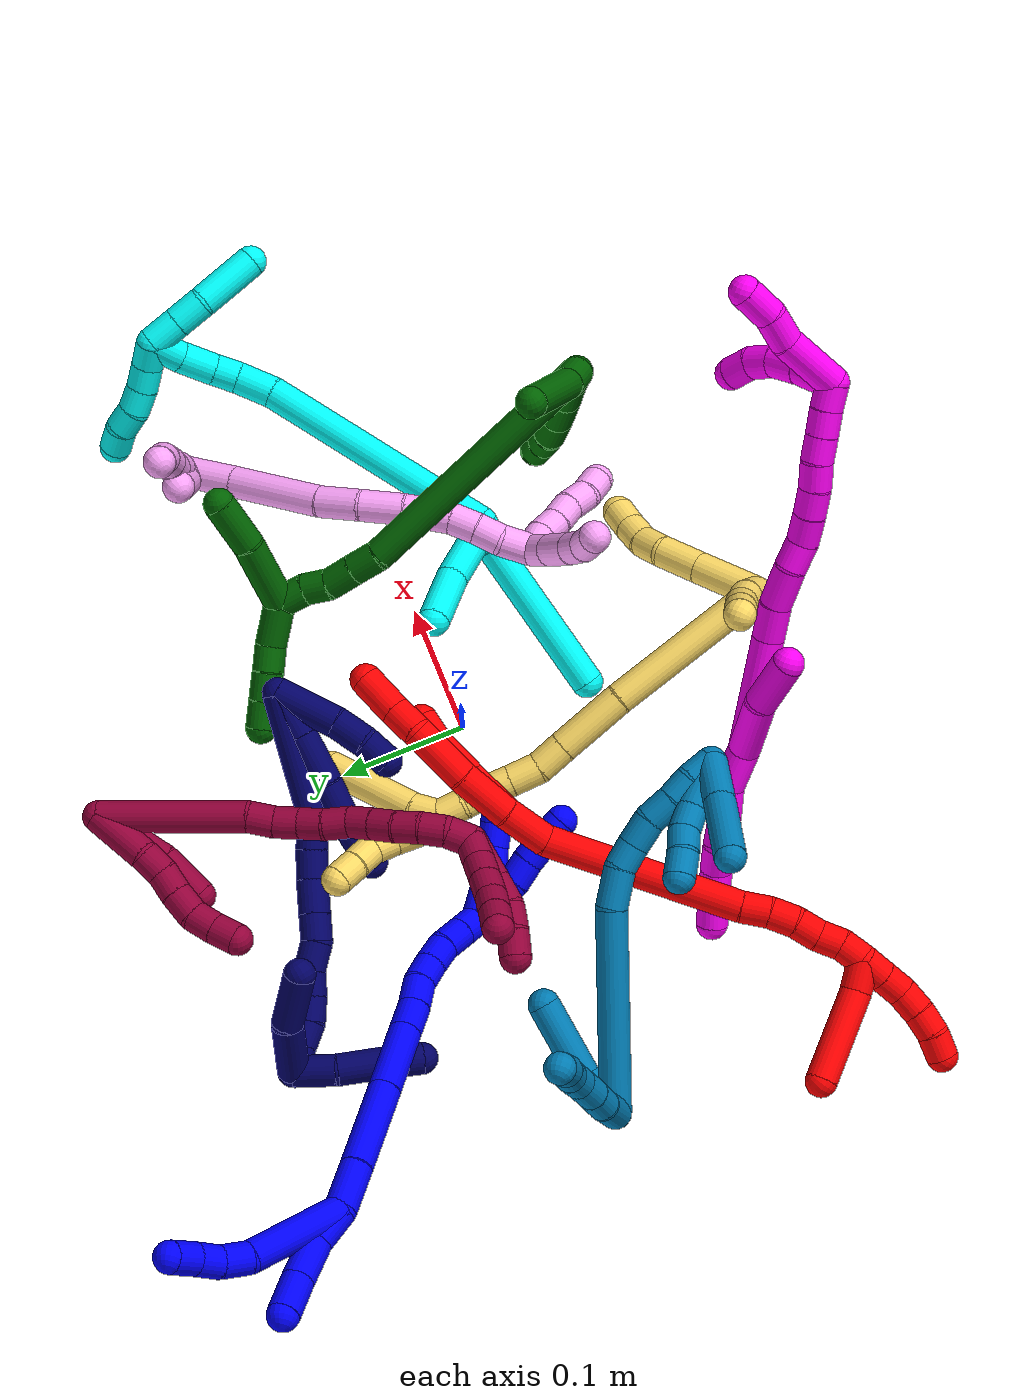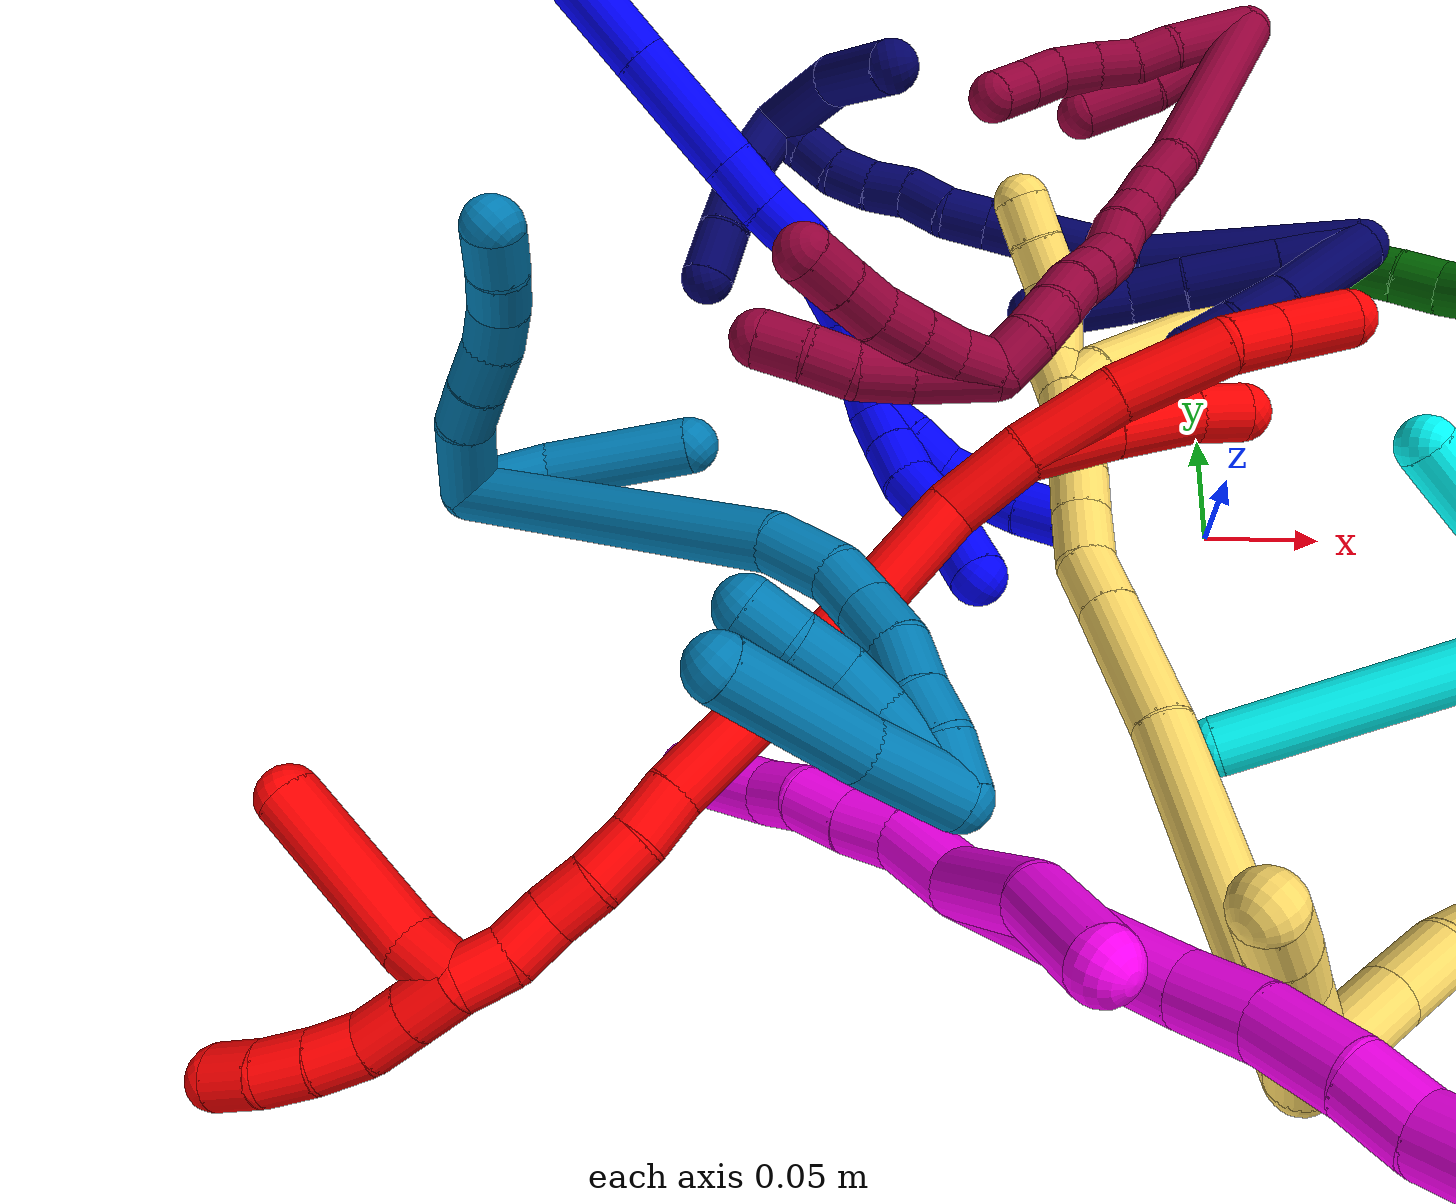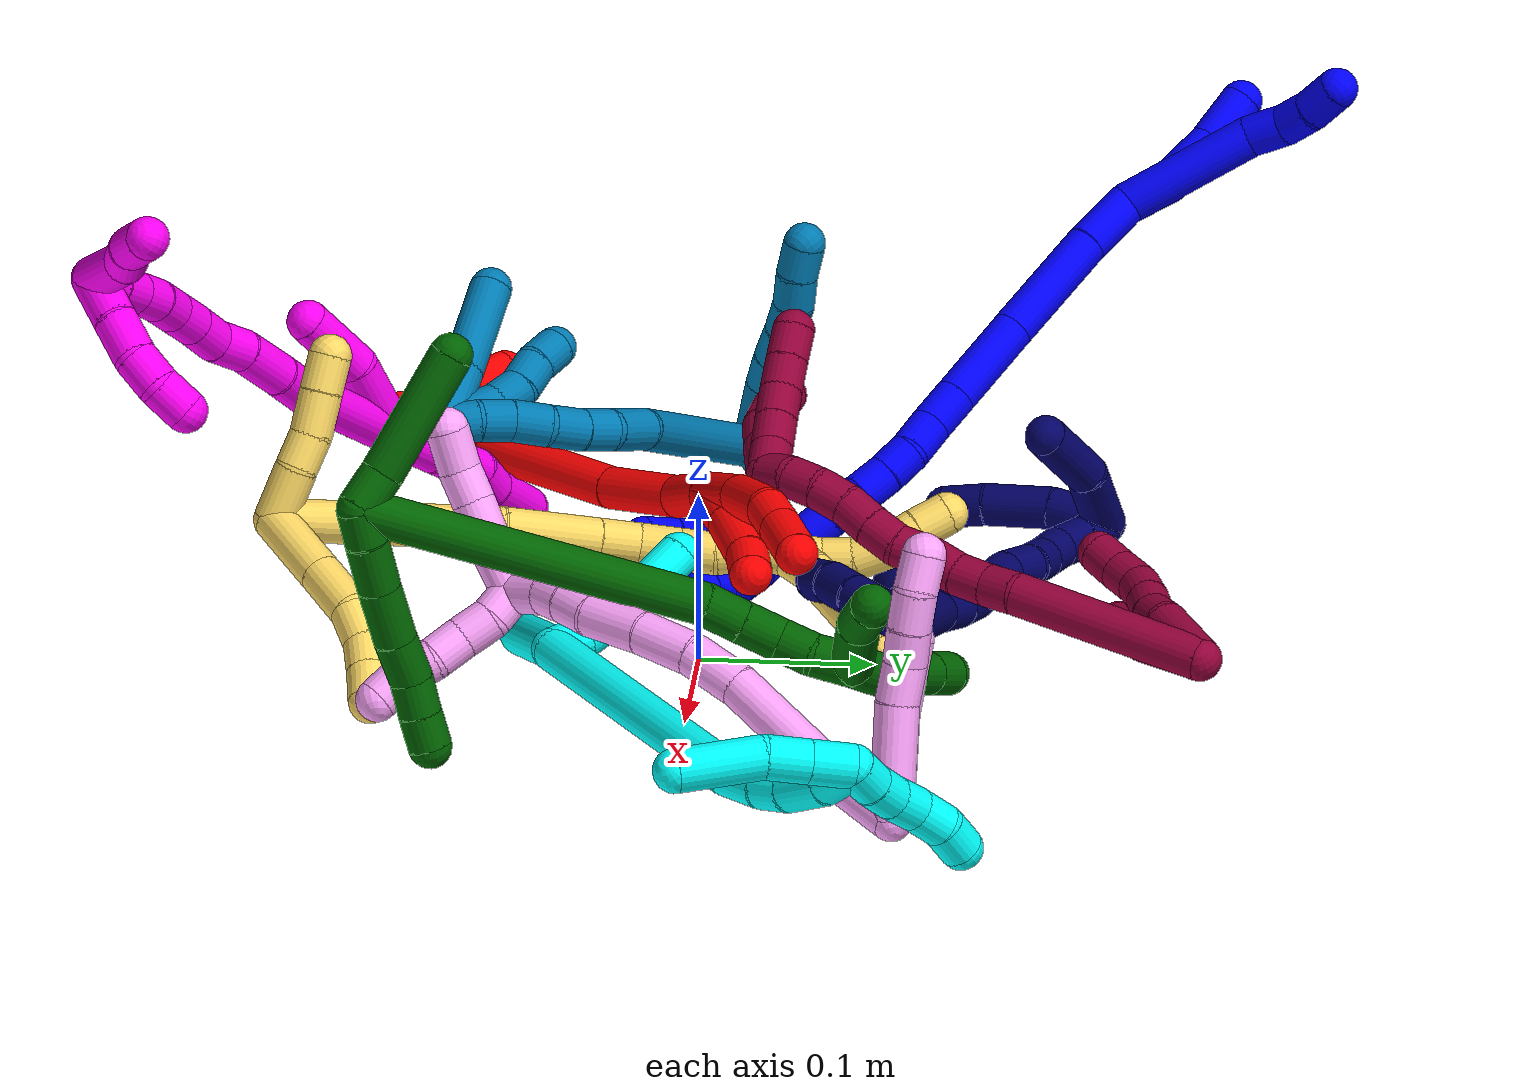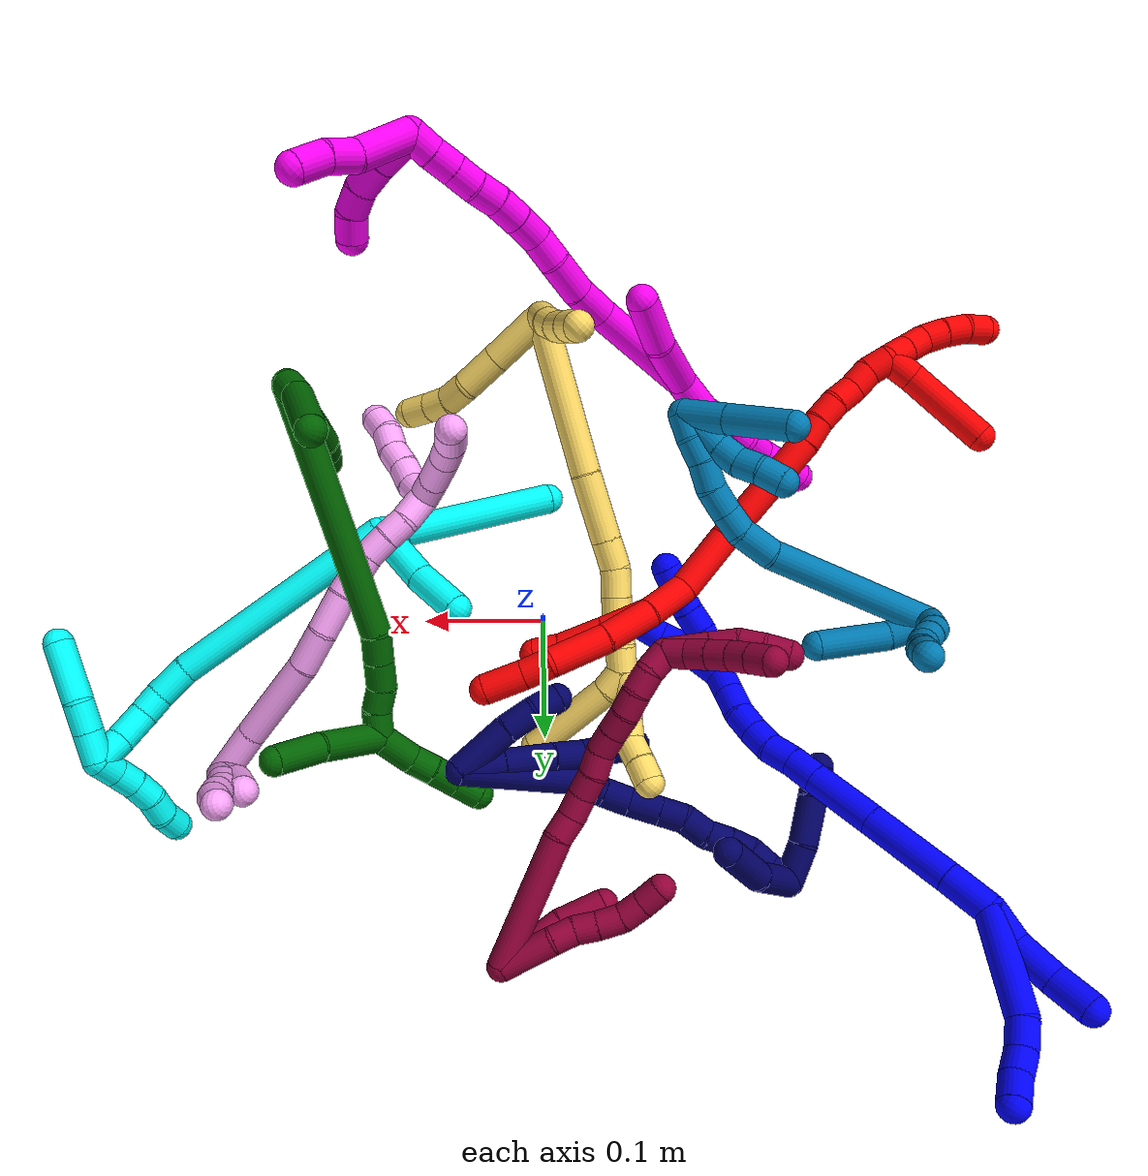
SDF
<sdf version="1.7">
 <world name="default">
  <plugin name="TubeGeneratorPlugin" filename="libtube_generator_plugin.so"/>
  <model name="photoneo_s_sensor">
   <static>1</static>
   <pose>0 0 2 1.57079 1.57079 3.14159</pose>
   <link name="link">
    <inertial><mass>0.1</mass></inertial>
    <sensor name="sensor" type="depth">
     <update_rate>30</update_rate>
     <camera>
      <horizontal_fov>1.22</horizontal_fov>
      <image><width>1920</width><height>1200</height><format>B8G8R8</format></image>
      <clip><near>0.1</near><far>4</far></clip>
      <depth_camera><output>points</output></depth_camera>
     </camera>
     <plugin name="camera_plugin" filename="libgazebo_ros_depth_camera.so">
      <baseline>0.2</baseline>
      <alwaysOn>1</alwaysOn>
      <updateRate>0.0</updateRate>
      <cameraName>camera_ir</cameraName>
      <imageTopicName>/camera/color/image_raw</imageTopicName>
      <cameraInfoTopicName>/camera/color/camera_info</cameraInfoTopicName>
      <depthImageTopicName>/camera/depth/image_raw</depthImageTopicName>
      <depthImageCameraInfoTopicName>/camera/depth/camera_info</depthImageCameraInfoTopicName>
      <pointCloudTopicName>/camera/depth/points</pointCloudTopicName>
      <frameName>fr_optical</frameName>
      <pointCloudCutoff>0.1</pointCloudCutoff>
      <pointCloudCutoffMax>2.0</pointCloudCutoffMax>
      <distortionK1>0</distortionK1>
      <distortionK2>0</distortionK2>
      <distortionK3>0</distortionK3>
      <distortionT1>0</distortionT1>
      <distortionT2>0</distortionT2>
      <CxPrime>0</CxPrime>
      <Cx>0</Cx>
      <Cy>0</Cy>
      <focalLength>0</focalLength>
      <hackBaseline>0</hackBaseline>
     </plugin>
    </sensor>
   </link>
  </model>
  <gravity>0 0 -9.8</gravity>
  <magnetic_field>6e-06 2.3e-05 -4.2e-05</magnetic_field>
  <atmosphere type="adiabatic"/>
  <physics name="default_physics" default="0" type="ode">
   <max_step_size>0.003</max_step_size>
   <real_time_factor>1</real_time_factor>
   <real_time_update_rate>1000</real_time_update_rate>
   <max_contacts>10000</max_contacts>
   <ode>
    <solver>
     <type>quick</type>
     <iters>100</iters>
     <sor>1.3</sor>
     <use_dynamic_moi_rescaling>0</use_dynamic_moi_rescaling>
    </solver>
    <constraints>
     <contact_max_correcting_vel>0</contact_max_correcting_vel>
     <contact_surface_layer>0.001</contact_surface_layer>
     <cfm>0</cfm>
     <erp>0.2</erp>
    </constraints>
   </ode>
  </physics>
  <scene><ambient>0.4 0.4 0.4 1</ambient><background>0.7 0.7 0.7 1</background><shadows>0</shadows></scene>
  <audio><device>default</device></audio>
  <spherical_coordinates>
   <surface_model>EARTH_WGS84</surface_model>
   <latitude_deg>0</latitude_deg>
   <longitude_deg>0</longitude_deg>
   <elevation>0</elevation>
   <heading_deg>0</heading_deg>
  </spherical_coordinates>
  <model name="bin">
   <static>1</static>
   <link name="bottom">
    <collision name="collision-bottom">
     <pose>0 0 -0.01 0 -0 0</pose>
     <geometry><box><size>0.8 0.6 0.02</size></box></geometry>
     <surface>
      <friction><ode><mu>100</mu><mu2>100</mu2></ode></friction>
      <contact><collide_bitmask>65535</collide_bitmask></contact>
     </surface>
    </collision>
   </link>
   <link name="west_wall">
    <collision name="collision-west_wall">
     <pose>-0.41 0 0.1 0 -0 0</pose>
     <geometry><box><size>0.02 0.6 0.2</size></box></geometry>
     <surface>
      <friction><ode><mu>100</mu><mu2>100</mu2></ode></friction>
      <contact><collide_bitmask>65535</collide_bitmask></contact>
     </surface>
    </collision>
   </link>
   <link name="east_wall">
    <collision name="collision-east_wall">
     <pose>0.41 0 0.1 0 -0 0</pose>
     <geometry><box><size>0.02 0.6 0.2</size></box></geometry>
     <surface>
      <friction><ode><mu>100</mu><mu2>100</mu2></ode></friction>
      <contact><collide_bitmask>65535</collide_bitmask></contact>
     </surface>
    </collision>
   </link>
   <link name="south_wall">
    <collision name="collision-south_wall">
     <pose>0 -0.31 0.1 0 -0 0</pose>
     <geometry><box><size>0.8 0.02 0.2</size></box></geometry>
     <surface>
      <friction><ode><mu>100</mu><mu2>100</mu2></ode></friction>
      <contact><collide_bitmask>65535</collide_bitmask></contact>
     </surface>
    </collision>
   </link>
   <link name="north_wall">
    <collision name="collision-north_wall">
     <pose>0 0.31 0.1 0 -0 0</pose>
     <geometry><box><size>0.8 0.02 0.2</size></box></geometry>
     <surface>
      <friction><ode><mu>100</mu><mu2>100</mu2></ode></friction>
      <contact><collide_bitmask>65535</collide_bitmask></contact>
     </surface>
    </collision>
   </link>
  </model>
  <model name="1">
   <static>0</static>
   <link name="1">
    <collision name="collision-cylinder-e_1_2_8">
     <pose>0.006796 0.0293 0.028825 -0.79357 0.163862 -0.068787</pose>
     <geometry><cylinder><radius>0.0125</radius><length>0.083319</length></cylinder></geometry>
     <surface>
      <friction><ode><mu>1.16</mu><mu2>1.16</mu2><slip1>0</slip1><slip2>0</slip2></ode></friction>
      <contact><ode><kp>1e+06</kp><kd>1</kd><max_vel>0</max_vel><min_depth>0.001</min_depth></ode></contact>
     </surface>
    </collision>
    <visual name="visual-cylinder-e_1_2_8">
     <pose>0.006796 0.0293 0.028825 -0.79357 0.163862 -0.068787</pose>
     <geometry><cylinder><radius>0.0125</radius><length>0.083319</length></cylinder></geometry>
     <material><ambient>0 0 1 1</ambient></material>
    </visual>
    <collision name="collision-cylinder-e_2_8_9">
     <pose>0.015129 0.068826 0.062634 -1.11727 0.134266 -0.084</pose>
     <geometry><cylinder><radius>0.0125</radius><length>0.02296</length></cylinder></geometry>
     <surface>
      <friction><ode><mu>1.16</mu><mu2>1.16</mu2><slip1>0</slip1><slip2>0</slip2></ode></friction>
      <contact><ode><kp>1e+06</kp><kd>1</kd><max_vel>0</max_vel><min_depth>0.001</min_depth></ode></contact>
     </surface>
    </collision>
    <visual name="visual-cylinder-e_2_8_9">
     <pose>0.015129 0.068826 0.062634 -1.11727 0.134266 -0.084</pose>
     <geometry><cylinder><radius>0.0125</radius><length>0.02296</length></cylinder></geometry>
     <material><ambient>0 0 1 1</ambient></material>
    </visual>
    <collision name="collision-cylinder-e_3_9_10">
     <pose>0.02086 0.088248 0.070321 -1.28496 0.412518 -0.310662</pose>
     <geometry><cylinder><radius>0.0125</radius><length>0.020923</length></cylinder></geometry>
     <surface>
      <friction><ode><mu>1.16</mu><mu2>1.16</mu2><slip1>0</slip1><slip2>0</slip2></ode></friction>
      <contact><ode><kp>1e+06</kp><kd>1</kd><max_vel>0</max_vel><min_depth>0.001</min_depth></ode></contact>
     </surface>
    </collision>
    <visual name="visual-cylinder-e_3_9_10">
     <pose>0.02086 0.088248 0.070321 -1.28496 0.412518 -0.310662</pose>
     <geometry><cylinder><radius>0.0125</radius><length>0.020923</length></cylinder></geometry>
     <material><ambient>0 0 1 1</ambient></material>
    </visual>
    <collision name="collision-cylinder-e_4_10_6">
     <pose>0.030871 0.106393 0.077023 -1.15053 0.535555 -0.352126</pose>
     <geometry><cylinder><radius>0.0125</radius><length>0.022798</length></cylinder></geometry>
     <surface>
      <friction><ode><mu>1.16</mu><mu2>1.16</mu2><slip1>0</slip1><slip2>0</slip2></ode></friction>
      <contact><ode><kp>1e+06</kp><kd>1</kd><max_vel>0</max_vel><min_depth>0.001</min_depth></ode></contact>
     </surface>
    </collision>
    <visual name="visual-cylinder-e_4_10_6">
     <pose>0.030871 0.106393 0.077023 -1.15053 0.535555 -0.352126</pose>
     <geometry><cylinder><radius>0.0125</radius><length>0.022798</length></cylinder></geometry>
     <material><ambient>0 0 1 1</ambient></material>
    </visual>
    <collision name="collision-cylinder-e_1_2_11">
     <pose>-0.001161 0.006512 0.013519 -0.448882 -0.077215 0.017636</pose>
     <geometry><cylinder><radius>0.0125</radius><length>0.0301</length></cylinder></geometry>
     <surface>
      <friction><ode><mu>1.16</mu><mu2>1.16</mu2><slip1>0</slip1><slip2>0</slip2></ode></friction>
      <contact><ode><kp>1e+06</kp><kd>1</kd><max_vel>0</max_vel><min_depth>0.001</min_depth></ode></contact>
     </surface>
    </collision>
    <visual name="visual-cylinder-e_1_2_11">
     <pose>-0.001161 0.006512 0.013519 -0.448882 -0.077215 0.017636</pose>
     <geometry><cylinder><radius>0.0125</radius><length>0.0301</length></cylinder></geometry>
     <material><ambient>0 0 1 1</ambient></material>
    </visual>
    <collision name="collision-cylinder-e_2_11_12">
     <pose>-0.000374 0.016996 0.044646 -0.221925 0.107502 -0.011989</pose>
     <geometry><cylinder><radius>0.0125</radius><length>0.036311</length></cylinder></geometry>
     <surface>
      <friction><ode><mu>1.16</mu><mu2>1.16</mu2><slip1>0</slip1><slip2>0</slip2></ode></friction>
      <contact><ode><kp>1e+06</kp><kd>1</kd><max_vel>0</max_vel><min_depth>0.001</min_depth></ode></contact>
     </surface>
    </collision>
    <visual name="visual-cylinder-e_2_11_12">
     <pose>-0.000374 0.016996 0.044646 -0.221925 0.107502 -0.011989</pose>
     <geometry><cylinder><radius>0.0125</radius><length>0.036311</length></cylinder></geometry>
     <material><ambient>0 0 1 1</ambient></material>
    </visual>
    <collision name="collision-cylinder-e_3_12_5">
     <pose>0.005657 0.023934 0.078272 -0.18302 0.245601 -0.022651</pose>
     <geometry><cylinder><radius>0.0125</radius><length>0.033589</length></cylinder></geometry>
     <surface>
      <friction><ode><mu>1.16</mu><mu2>1.16</mu2><slip1>0</slip1><slip2>0</slip2></ode></friction>
      <contact><ode><kp>1e+06</kp><kd>1</kd><max_vel>0</max_vel><min_depth>0.001</min_depth></ode></contact>
     </surface>
    </collision>
    <visual name="visual-cylinder-e_3_12_5">
     <pose>0.005657 0.023934 0.078272 -0.18302 0.245601 -0.022651</pose>
     <geometry><cylinder><radius>0.0125</radius><length>0.033589</length></cylinder></geometry>
     <material><ambient>0 0 1 1</ambient></material>
    </visual>
    <collision name="collision-cylinder-e_1_2_13">
     <pose>-0.001387 -0.002996 -0.019141 2.98633 -0.071446 -0.861341</pose>
     <geometry><cylinder><radius>0.0125</radius><length>0.038848</length></cylinder></geometry>
     <surface>
      <friction><ode><mu>1.16</mu><mu2>1.16</mu2><slip1>0</slip1><slip2>0</slip2></ode></friction>
      <contact><ode><kp>1e+06</kp><kd>1</kd><max_vel>0</max_vel><min_depth>0.001</min_depth></ode></contact>
     </surface>
    </collision>
    <visual name="visual-cylinder-e_1_2_13">
     <pose>-0.001387 -0.002996 -0.019141 2.98633 -0.071446 -0.861341</pose>
     <geometry><cylinder><radius>0.0125</radius><length>0.038848</length></cylinder></geometry>
     <material><ambient>0 0 1 1</ambient></material>
    </visual>
    <collision name="collision-cylinder-e_2_13_14">
     <pose>-0.007996 -0.01137 -0.074268 2.99324 -0.142578 -1.53096</pose>
     <geometry><cylinder><radius>0.0125</radius><length>0.073515</length></cylinder></geometry>
     <surface>
      <friction><ode><mu>1.16</mu><mu2>1.16</mu2><slip1>0</slip1><slip2>0</slip2></ode></friction>
      <contact><ode><kp>1e+06</kp><kd>1</kd><max_vel>0</max_vel><min_depth>0.001</min_depth></ode></contact>
     </surface>
    </collision>
    <visual name="visual-cylinder-e_2_13_14">
     <pose>-0.007996 -0.01137 -0.074268 2.99324 -0.142578 -1.53096</pose>
     <geometry><cylinder><radius>0.0125</radius><length>0.073515</length></cylinder></geometry>
     <material><ambient>0 0 1 1</ambient></material>
    </visual>
    <collision name="collision-cylinder-e_3_14_15">
     <pose>-0.017455 -0.02076 -0.138131 2.99865 -0.149265 -1.61423</pose>
     <geometry><cylinder><radius>0.0125</radius><length>0.056963</length></cylinder></geometry>
     <surface>
      <friction><ode><mu>1.16</mu><mu2>1.16</mu2><slip1>0</slip1><slip2>0</slip2></ode></friction>
      <contact><ode><kp>1e+06</kp><kd>1</kd><max_vel>0</max_vel><min_depth>0.001</min_depth></ode></contact>
     </surface>
    </collision>
    <visual name="visual-cylinder-e_3_14_15">
     <pose>-0.017455 -0.02076 -0.138131 2.99865 -0.149265 -1.61423</pose>
     <geometry><cylinder><radius>0.0125</radius><length>0.056963</length></cylinder></geometry>
     <material><ambient>0 0 1 1</ambient></material>
    </visual>
    <collision name="collision-cylinder-e_4_15_16">
     <pose>-0.023558 -0.026591 -0.178095 2.99224 -0.15163 -1.58596</pose>
     <geometry><cylinder><radius>0.0125</radius><length>0.024729</length></cylinder></geometry>
     <surface>
      <friction><ode><mu>1.16</mu><mu2>1.16</mu2><slip1>0</slip1><slip2>0</slip2></ode></friction>
      <contact><ode><kp>1e+06</kp><kd>1</kd><max_vel>0</max_vel><min_depth>0.001</min_depth></ode></contact>
     </surface>
    </collision>
    <visual name="visual-cylinder-e_4_15_16">
     <pose>-0.023558 -0.026591 -0.178095 2.99224 -0.15163 -1.58596</pose>
     <geometry><cylinder><radius>0.0125</radius><length>0.024729</length></cylinder></geometry>
     <material><ambient>0 0 1 1</ambient></material>
    </visual>
    <collision name="collision-cylinder-e_5_16_17">
     <pose>-0.02656 -0.028856 -0.201535 3.10234 -0.0995 -2.39059</pose>
     <geometry><cylinder><radius>0.0125</radius><length>0.022836</length></cylinder></geometry>
     <surface>
      <friction><ode><mu>1.16</mu><mu2>1.16</mu2><slip1>0</slip1><slip2>0</slip2></ode></friction>
      <contact><ode><kp>1e+06</kp><kd>1</kd><max_vel>0</max_vel><min_depth>0.001</min_depth></ode></contact>
     </surface>
    </collision>
    <visual name="visual-cylinder-e_5_16_17">
     <pose>-0.02656 -0.028856 -0.201535 3.10234 -0.0995 -2.39059</pose>
     <geometry><cylinder><radius>0.0125</radius><length>0.022836</length></cylinder></geometry>
     <material><ambient>0 0 1 1</ambient></material>
    </visual>
    <collision name="collision-cylinder-e_6_17_18">
     <pose>-0.02912 -0.032244 -0.222363 2.84048 -0.142671 -0.880412</pose>
     <geometry><cylinder><radius>0.0125</radius><length>0.020047</length></cylinder></geometry>
     <surface>
      <friction><ode><mu>1.16</mu><mu2>1.16</mu2><slip1>0</slip1><slip2>0</slip2></ode></friction>
      <contact><ode><kp>1e+06</kp><kd>1</kd><max_vel>0</max_vel><min_depth>0.001</min_depth></ode></contact>
     </surface>
    </collision>
    <visual name="visual-cylinder-e_6_17_18">
     <pose>-0.02912 -0.032244 -0.222363 2.84048 -0.142671 -0.880412</pose>
     <geometry><cylinder><radius>0.0125</radius><length>0.020047</length></cylinder></geometry>
     <material><ambient>0 0 1 1</ambient></material>
    </visual>
    <collision name="collision-cylinder-e_7_18_19">
     <pose>-0.031438 -0.038862 -0.24128 2.7704 -0.087965 -0.460492</pose>
     <geometry><cylinder><radius>0.0125</radius><length>0.020341</length></cylinder></geometry>
     <surface>
      <friction><ode><mu>1.16</mu><mu2>1.16</mu2><slip1>0</slip1><slip2>0</slip2></ode></friction>
      <contact><ode><kp>1e+06</kp><kd>1</kd><max_vel>0</max_vel><min_depth>0.001</min_depth></ode></contact>
     </surface>
    </collision>
    <visual name="visual-cylinder-e_7_18_19">
     <pose>-0.031438 -0.038862 -0.24128 2.7704 -0.087965 -0.460492</pose>
     <geometry><cylinder><radius>0.0125</radius><length>0.020341</length></cylinder></geometry>
     <material><ambient>0 0 1 1</ambient></material>
    </visual>
    <collision name="collision-cylinder-e_8_19_20">
     <pose>-0.034573 -0.048385 -0.25963 2.56074 -0.207303 -0.669874</pose>
     <geometry><cylinder><radius>0.0125</radius><length>0.02178</length></cylinder></geometry>
     <surface>
      <friction><ode><mu>1.16</mu><mu2>1.16</mu2><slip1>0</slip1><slip2>0</slip2></ode></friction>
      <contact><ode><kp>1e+06</kp><kd>1</kd><max_vel>0</max_vel><min_depth>0.001</min_depth></ode></contact>
     </surface>
    </collision>
    <visual name="visual-cylinder-e_8_19_20">
     <pose>-0.034573 -0.048385 -0.25963 2.56074 -0.207303 -0.669874</pose>
     <geometry><cylinder><radius>0.0125</radius><length>0.02178</length></cylinder></geometry>
     <material><ambient>0 0 1 1</ambient></material>
    </visual>
    <collision name="collision-cylinder-e_9_20_1">
     <pose>-0.03897 -0.059861 -0.2771 2.55993 -0.20734 -0.669068</pose>
     <geometry><cylinder><radius>0.0125</radius><length>0.020939</length></cylinder></geometry>
     <surface>
      <friction><ode><mu>1.16</mu><mu2>1.16</mu2><slip1>0</slip1><slip2>0</slip2></ode></friction>
      <contact><ode><kp>1e+06</kp><kd>1</kd><max_vel>0</max_vel><min_depth>0.001</min_depth></ode></contact>
     </surface>
    </collision>
    <visual name="visual-cylinder-e_9_20_1">
     <pose>-0.03897 -0.059861 -0.2771 2.55993 -0.20734 -0.669068</pose>
     <geometry><cylinder><radius>0.0125</radius><length>0.020939</length></cylinder></geometry>
     <material><ambient>0 0 1 1</ambient></material>
    </visual>
    <collision name="collision-cylinder-e_1_1_21">
     <pose>-0.036761 -0.070916 -0.292837 2.49425 0.451602 1.20087</pose>
     <geometry><cylinder><radius>0.0125</radius><length>0.02</length></cylinder></geometry>
     <surface>
      <friction><ode><mu>1.16</mu><mu2>1.16</mu2><slip1>0</slip1><slip2>0</slip2></ode></friction>
      <contact><ode><kp>1e+06</kp><kd>1</kd><max_vel>0</max_vel><min_depth>0.001</min_depth></ode></contact>
     </surface>
    </collision>
    <visual name="visual-cylinder-e_1_1_21">
     <pose>-0.036761 -0.070916 -0.292837 2.49425 0.451602 1.20087</pose>
     <geometry><cylinder><radius>0.0125</radius><length>0.02</length></cylinder></geometry>
     <material><ambient>0 0 1 1</ambient></material>
    </visual>
    <collision name="collision-cylinder-e_2_21_22">
     <pose>-0.028115 -0.081631 -0.307342 2.51647 0.442501 1.21614</pose>
     <geometry><cylinder><radius>0.0125</radius><length>0.02</length></cylinder></geometry>
     <surface>
      <friction><ode><mu>1.16</mu><mu2>1.16</mu2><slip1>0</slip1><slip2>0</slip2></ode></friction>
      <contact><ode><kp>1e+06</kp><kd>1</kd><max_vel>0</max_vel><min_depth>0.001</min_depth></ode></contact>
     </surface>
    </collision>
    <visual name="visual-cylinder-e_2_21_22">
     <pose>-0.028115 -0.081631 -0.307342 2.51647 0.442501 1.21614</pose>
     <geometry><cylinder><radius>0.0125</radius><length>0.02</length></cylinder></geometry>
     <material><ambient>0 0 1 1</ambient></material>
    </visual>
    <collision name="collision-cylinder-e_3_22_23">
     <pose>-0.018334 -0.090277 -0.322318 2.72785 0.58226 1.91958</pose>
     <geometry><cylinder><radius>0.0125</radius><length>0.02</length></cylinder></geometry>
     <surface>
      <friction><ode><mu>1.16</mu><mu2>1.16</mu2><slip1>0</slip1><slip2>0</slip2></ode></friction>
      <contact><ode><kp>1e+06</kp><kd>1</kd><max_vel>0</max_vel><min_depth>0.001</min_depth></ode></contact>
     </surface>
    </collision>
    <visual name="visual-cylinder-e_3_22_23">
     <pose>-0.018334 -0.090277 -0.322318 2.72785 0.58226 1.91958</pose>
     <geometry><cylinder><radius>0.0125</radius><length>0.02</length></cylinder></geometry>
     <material><ambient>0 0 1 1</ambient></material>
    </visual>
    <collision name="collision-cylinder-e_4_23_24">
     <pose>-0.007188 -0.097993 -0.336975 2.58539 0.600001 1.6509</pose>
     <geometry><cylinder><radius>0.0125</radius><length>0.02</length></cylinder></geometry>
     <surface>
      <friction><ode><mu>1.16</mu><mu2>1.16</mu2><slip1>0</slip1><slip2>0</slip2></ode></friction>
      <contact><ode><kp>1e+06</kp><kd>1</kd><max_vel>0</max_vel><min_depth>0.001</min_depth></ode></contact>
     </surface>
    </collision>
    <visual name="visual-cylinder-e_4_23_24">
     <pose>-0.007188 -0.097993 -0.336975 2.58539 0.600001 1.6509</pose>
     <geometry><cylinder><radius>0.0125</radius><length>0.02</length></cylinder></geometry>
     <material><ambient>0 0 1 1</ambient></material>
    </visual>
    <collision name="collision-cylinder-e_5_24_4">
     <pose>0.003765 -0.107067 -0.351026 2.55135 0.559366 1.51401</pose>
     <geometry><cylinder><radius>0.0125</radius><length>0.02</length></cylinder></geometry>
     <surface>
      <friction><ode><mu>1.16</mu><mu2>1.16</mu2><slip1>0</slip1><slip2>0</slip2></ode></friction>
      <contact><ode><kp>1e+06</kp><kd>1</kd><max_vel>0</max_vel><min_depth>0.001</min_depth></ode></contact>
     </surface>
    </collision>
    <visual name="visual-cylinder-e_5_24_4">
     <pose>0.003765 -0.107067 -0.351026 2.55135 0.559366 1.51401</pose>
     <geometry><cylinder><radius>0.0125</radius><length>0.02</length></cylinder></geometry>
     <material><ambient>0 0 1 1</ambient></material>
    </visual>
    <collision name="collision-cylinder-e_1_1_25">
     <pose>-0.038177 -0.066326 -0.295179 3.05407 0.299278 2.57625</pose>
     <geometry><cylinder><radius>0.0125</radius><length>0.02</length></cylinder></geometry>
     <surface>
      <friction><ode><mu>1.16</mu><mu2>1.16</mu2><slip1>0</slip1><slip2>0</slip2></ode></friction>
      <contact><ode><kp>1e+06</kp><kd>1</kd><max_vel>0</max_vel><min_depth>0.001</min_depth></ode></contact>
     </surface>
    </collision>
    <visual name="visual-cylinder-e_1_1_25">
     <pose>-0.038177 -0.066326 -0.295179 3.05407 0.299278 2.57625</pose>
     <geometry><cylinder><radius>0.0125</radius><length>0.02</length></cylinder></geometry>
     <material><ambient>0 0 1 1</ambient></material>
    </visual>
    <collision name="collision-cylinder-e_2_25_26">
     <pose>-0.034913 -0.068155 -0.314643 3.04193 0.031596 0.613607</pose>
     <geometry><cylinder><radius>0.0125</radius><length>0.02</length></cylinder></geometry>
     <surface>
      <friction><ode><mu>1.16</mu><mu2>1.16</mu2><slip1>0</slip1><slip2>0</slip2></ode></friction>
      <contact><ode><kp>1e+06</kp><kd>1</kd><max_vel>0</max_vel><min_depth>0.001</min_depth></ode></contact>
     </surface>
    </collision>
    <visual name="visual-cylinder-e_2_25_26">
     <pose>-0.034913 -0.068155 -0.314643 3.04193 0.031596 0.613607</pose>
     <geometry><cylinder><radius>0.0125</radius><length>0.02</length></cylinder></geometry>
     <material><ambient>0 0 1 1</ambient></material>
    </visual>
    <collision name="collision-cylinder-e_3_26_27">
     <pose>-0.031841 -0.067888 -0.334119 -3.00995 0.279131 -2.26414</pose>
     <geometry><cylinder><radius>0.0125</radius><length>0.02</length></cylinder></geometry>
     <surface>
      <friction><ode><mu>1.16</mu><mu2>1.16</mu2><slip1>0</slip1><slip2>0</slip2></ode></friction>
      <contact><ode><kp>1e+06</kp><kd>1</kd><max_vel>0</max_vel><min_depth>0.001</min_depth></ode></contact>
     </surface>
    </collision>
    <visual name="visual-cylinder-e_3_26_27">
     <pose>-0.031841 -0.067888 -0.334119 -3.00995 0.279131 -2.26414</pose>
     <geometry><cylinder><radius>0.0125</radius><length>0.02</length></cylinder></geometry>
     <material><ambient>0 0 1 1</ambient></material>
    </visual>
    <collision name="collision-cylinder-e_4_27_28">
     <pose>-0.023895 -0.065952 -0.352169 -3.0626 0.545825 -2.86107</pose>
     <geometry><cylinder><radius>0.0125</radius><length>0.02</length></cylinder></geometry>
     <surface>
      <friction><ode><mu>1.16</mu><mu2>1.16</mu2><slip1>0</slip1><slip2>0</slip2></ode></friction>
      <contact><ode><kp>1e+06</kp><kd>1</kd><max_vel>0</max_vel><min_depth>0.001</min_depth></ode></contact>
     </surface>
    </collision>
    <visual name="visual-cylinder-e_4_27_28">
     <pose>-0.023895 -0.065952 -0.352169 -3.0626 0.545825 -2.86107</pose>
     <geometry><cylinder><radius>0.0125</radius><length>0.02</length></cylinder></geometry>
     <material><ambient>0 0 1 1</ambient></material>
    </visual>
    <collision name="collision-cylinder-e_5_28_3">
     <pose>-0.012985 -0.063606 -0.368721 -2.93647 0.608747 -2.50835</pose>
     <geometry><cylinder><radius>0.0125</radius><length>0.02</length></cylinder></geometry>
     <surface>
      <friction><ode><mu>1.16</mu><mu2>1.16</mu2><slip1>0</slip1><slip2>0</slip2></ode></friction>
      <contact><ode><kp>1e+06</kp><kd>1</kd><max_vel>0</max_vel><min_depth>0.001</min_depth></ode></contact>
     </surface>
    </collision>
    <visual name="visual-cylinder-e_5_28_3">
     <pose>-0.012985 -0.063606 -0.368721 -2.93647 0.608747 -2.50835</pose>
     <geometry><cylinder><radius>0.0125</radius><length>0.02</length></cylinder></geometry>
     <material><ambient>0 0 1 1</ambient></material>
    </visual>
    <collision name="collision-sphere-3">
     <pose>-0.007267 -0.061935 -0.376752 0 -0 0</pose>
     <geometry><sphere><radius>0.0125</radius></sphere></geometry>
     <surface>
      <friction><ode><mu>1.16</mu><mu2>1.16</mu2><slip1>0</slip1><slip2>0</slip2></ode></friction>
      <contact><ode><kp>1e+06</kp><kd>1</kd><max_vel>0</max_vel><min_depth>0.001</min_depth></ode></contact>
     </surface>
    </collision>
    <visual name="visual-sphere-3">
     <pose>-0.007267 -0.061935 -0.376752 0 -0 0</pose>
     <geometry><sphere><radius>0.0125</radius></sphere></geometry>
     <material><ambient>0 0 1 1</ambient></material>
    </visual>
    <collision name="collision-sphere-28">
     <pose>-0.018704 -0.065277 -0.360689 0 -0 0</pose>
     <geometry><sphere><radius>0.0125</radius></sphere></geometry>
     <surface>
      <friction><ode><mu>1.16</mu><mu2>1.16</mu2><slip1>0</slip1><slip2>0</slip2></ode></friction>
      <contact><ode><kp>1e+06</kp><kd>1</kd><max_vel>0</max_vel><min_depth>0.001</min_depth></ode></contact>
     </surface>
    </collision>
    <visual name="visual-sphere-28">
     <pose>-0.018704 -0.065277 -0.360689 0 -0 0</pose>
     <geometry><sphere><radius>0.0125</radius></sphere></geometry>
     <material><ambient>0 0 1 1</ambient></material>
    </visual>
    <collision name="collision-sphere-27">
     <pose>-0.029086 -0.066626 -0.343648 0 -0 0</pose>
     <geometry><sphere><radius>0.0125</radius></sphere></geometry>
     <surface>
      <friction><ode><mu>1.16</mu><mu2>1.16</mu2><slip1>0</slip1><slip2>0</slip2></ode></friction>
      <contact><ode><kp>1e+06</kp><kd>1</kd><max_vel>0</max_vel><min_depth>0.001</min_depth></ode></contact>
     </surface>
    </collision>
    <visual name="visual-sphere-27">
     <pose>-0.029086 -0.066626 -0.343648 0 -0 0</pose>
     <geometry><sphere><radius>0.0125</radius></sphere></geometry>
     <material><ambient>0 0 1 1</ambient></material>
    </visual>
    <collision name="collision-sphere-26">
     <pose>-0.034597 -0.06915 -0.324589 0 -0 0</pose>
     <geometry><sphere><radius>0.0125</radius></sphere></geometry>
     <surface>
      <friction><ode><mu>1.16</mu><mu2>1.16</mu2><slip1>0</slip1><slip2>0</slip2></ode></friction>
      <contact><ode><kp>1e+06</kp><kd>1</kd><max_vel>0</max_vel><min_depth>0.001</min_depth></ode></contact>
     </surface>
    </collision>
    <visual name="visual-sphere-26">
     <pose>-0.034597 -0.06915 -0.324589 0 -0 0</pose>
     <geometry><sphere><radius>0.0125</radius></sphere></geometry>
     <material><ambient>0 0 1 1</ambient></material>
    </visual>
    <collision name="collision-sphere-25">
     <pose>-0.035228 -0.067161 -0.304698 0 -0 0</pose>
     <geometry><sphere><radius>0.0125</radius></sphere></geometry>
     <surface>
      <friction><ode><mu>1.16</mu><mu2>1.16</mu2><slip1>0</slip1><slip2>0</slip2></ode></friction>
      <contact><ode><kp>1e+06</kp><kd>1</kd><max_vel>0</max_vel><min_depth>0.001</min_depth></ode></contact>
     </surface>
    </collision>
    <visual name="visual-sphere-25">
     <pose>-0.035228 -0.067161 -0.304698 0 -0 0</pose>
     <geometry><sphere><radius>0.0125</radius></sphere></geometry>
     <material><ambient>0 0 1 1</ambient></material>
    </visual>
    <collision name="collision-sphere-4">
     <pose>0.009071 -0.111785 -0.358068 0 -0 0</pose>
     <geometry><sphere><radius>0.0125</radius></sphere></geometry>
     <surface>
      <friction><ode><mu>1.16</mu><mu2>1.16</mu2><slip1>0</slip1><slip2>0</slip2></ode></friction>
      <contact><ode><kp>1e+06</kp><kd>1</kd><max_vel>0</max_vel><min_depth>0.001</min_depth></ode></contact>
     </surface>
    </collision>
    <visual name="visual-sphere-4">
     <pose>0.009071 -0.111785 -0.358068 0 -0 0</pose>
     <geometry><sphere><radius>0.0125</radius></sphere></geometry>
     <material><ambient>0 0 1 1</ambient></material>
    </visual>
    <collision name="collision-sphere-24">
     <pose>-0.001542 -0.10235 -0.343984 0 -0 0</pose>
     <geometry><sphere><radius>0.0125</radius></sphere></geometry>
     <surface>
      <friction><ode><mu>1.16</mu><mu2>1.16</mu2><slip1>0</slip1><slip2>0</slip2></ode></friction>
      <contact><ode><kp>1e+06</kp><kd>1</kd><max_vel>0</max_vel><min_depth>0.001</min_depth></ode></contact>
     </surface>
    </collision>
    <visual name="visual-sphere-24">
     <pose>-0.001542 -0.10235 -0.343984 0 -0 0</pose>
     <geometry><sphere><radius>0.0125</radius></sphere></geometry>
     <material><ambient>0 0 1 1</ambient></material>
    </visual>
    <collision name="collision-sphere-23">
     <pose>-0.012835 -0.093635 -0.329965 0 -0 0</pose>
     <geometry><sphere><radius>0.0125</radius></sphere></geometry>
     <surface>
      <friction><ode><mu>1.16</mu><mu2>1.16</mu2><slip1>0</slip1><slip2>0</slip2></ode></friction>
      <contact><ode><kp>1e+06</kp><kd>1</kd><max_vel>0</max_vel><min_depth>0.001</min_depth></ode></contact>
     </surface>
    </collision>
    <visual name="visual-sphere-23">
     <pose>-0.012835 -0.093635 -0.329965 0 -0 0</pose>
     <geometry><sphere><radius>0.0125</radius></sphere></geometry>
     <material><ambient>0 0 1 1</ambient></material>
    </visual>
    <collision name="collision-sphere-22">
     <pose>-0.023833 -0.086919 -0.31467 0 -0 0</pose>
     <geometry><sphere><radius>0.0125</radius></sphere></geometry>
     <surface>
      <friction><ode><mu>1.16</mu><mu2>1.16</mu2><slip1>0</slip1><slip2>0</slip2></ode></friction>
      <contact><ode><kp>1e+06</kp><kd>1</kd><max_vel>0</max_vel><min_depth>0.001</min_depth></ode></contact>
     </surface>
    </collision>
    <visual name="visual-sphere-22">
     <pose>-0.023833 -0.086919 -0.31467 0 -0 0</pose>
     <geometry><sphere><radius>0.0125</radius></sphere></geometry>
     <material><ambient>0 0 1 1</ambient></material>
    </visual>
    <collision name="collision-sphere-21">
     <pose>-0.032397 -0.076342 -0.300015 0 -0 0</pose>
     <geometry><sphere><radius>0.0125</radius></sphere></geometry>
     <surface>
      <friction><ode><mu>1.16</mu><mu2>1.16</mu2><slip1>0</slip1><slip2>0</slip2></ode></friction>
      <contact><ode><kp>1e+06</kp><kd>1</kd><max_vel>0</max_vel><min_depth>0.001</min_depth></ode></contact>
     </surface>
    </collision>
    <visual name="visual-sphere-21">
     <pose>-0.032397 -0.076342 -0.300015 0 -0 0</pose>
     <geometry><sphere><radius>0.0125</radius></sphere></geometry>
     <material><ambient>0 0 1 1</ambient></material>
    </visual>
    <collision name="collision-sphere-1">
     <pose>-0.041125 -0.06549 -0.28566 0 -0 0</pose>
     <geometry><sphere><radius>0.0125</radius></sphere></geometry>
     <surface>
      <friction><ode><mu>1.16</mu><mu2>1.16</mu2><slip1>0</slip1><slip2>0</slip2></ode></friction>
      <contact><ode><kp>1e+06</kp><kd>1</kd><max_vel>0</max_vel><min_depth>0.001</min_depth></ode></contact>
     </surface>
    </collision>
    <visual name="visual-sphere-1">
     <pose>-0.041125 -0.06549 -0.28566 0 -0 0</pose>
     <geometry><sphere><radius>0.0125</radius></sphere></geometry>
     <material><ambient>0 0 1 1</ambient></material>
    </visual>
    <collision name="collision-sphere-11">
     <pose>-0.002322 0.013023 0.027038 0 -0 0</pose>
     <geometry><sphere><radius>0.0125</radius></sphere></geometry>
     <surface>
      <friction><ode><mu>1.16</mu><mu2>1.16</mu2><slip1>0</slip1><slip2>0</slip2></ode></friction>
      <contact><ode><kp>1e+06</kp><kd>1</kd><max_vel>0</max_vel><min_depth>0.001</min_depth></ode></contact>
     </surface>
    </collision>
    <visual name="visual-sphere-11">
     <pose>-0.002322 0.013023 0.027038 0 -0 0</pose>
     <geometry><sphere><radius>0.0125</radius></sphere></geometry>
     <material><ambient>0 0 1 1</ambient></material>
    </visual>
    <collision name="collision-sphere-6">
     <pose>0.036688 0.115342 0.081022 0 -0 0</pose>
     <geometry><sphere><radius>0.0125</radius></sphere></geometry>
     <surface>
      <friction><ode><mu>1.16</mu><mu2>1.16</mu2><slip1>0</slip1><slip2>0</slip2></ode></friction>
      <contact><ode><kp>1e+06</kp><kd>1</kd><max_vel>0</max_vel><min_depth>0.001</min_depth></ode></contact>
     </surface>
    </collision>
    <visual name="visual-sphere-6">
     <pose>0.036688 0.115342 0.081022 0 -0 0</pose>
     <geometry><sphere><radius>0.0125</radius></sphere></geometry>
     <material><ambient>0 0 1 1</ambient></material>
    </visual>
    <collision name="collision-sphere-10">
     <pose>0.025054 0.097443 0.073023 0 -0 0</pose>
     <geometry><sphere><radius>0.0125</radius></sphere></geometry>
     <surface>
      <friction><ode><mu>1.16</mu><mu2>1.16</mu2><slip1>0</slip1><slip2>0</slip2></ode></friction>
      <contact><ode><kp>1e+06</kp><kd>1</kd><max_vel>0</max_vel><min_depth>0.001</min_depth></ode></contact>
     </surface>
    </collision>
    <visual name="visual-sphere-10">
     <pose>0.025054 0.097443 0.073023 0 -0 0</pose>
     <geometry><sphere><radius>0.0125</radius></sphere></geometry>
     <material><ambient>0 0 1 1</ambient></material>
    </visual>
    <collision name="collision-sphere-9">
     <pose>0.016665 0.079053 0.067619 0 -0 0</pose>
     <geometry><sphere><radius>0.0125</radius></sphere></geometry>
     <surface>
      <friction><ode><mu>1.16</mu><mu2>1.16</mu2><slip1>0</slip1><slip2>0</slip2></ode></friction>
      <contact><ode><kp>1e+06</kp><kd>1</kd><max_vel>0</max_vel><min_depth>0.001</min_depth></ode></contact>
     </surface>
    </collision>
    <visual name="visual-sphere-9">
     <pose>0.016665 0.079053 0.067619 0 -0 0</pose>
     <geometry><sphere><radius>0.0125</radius></sphere></geometry>
     <material><ambient>0 0 1 1</ambient></material>
    </visual>
    <collision name="collision-sphere-2">
     <geometry><sphere><radius>0.0125</radius></sphere></geometry>
     <surface>
      <friction><ode><mu>1.16</mu><mu2>1.16</mu2><slip1>0</slip1><slip2>0</slip2></ode></friction>
      <contact><ode><kp>1e+06</kp><kd>1</kd><max_vel>0</max_vel><min_depth>0.001</min_depth></ode></contact>
     </surface>
    </collision>
    <visual name="visual-sphere-2">
     <geometry><sphere><radius>0.0125</radius></sphere></geometry>
     <material><ambient>0 0 1 1</ambient></material>
    </visual>
    <collision name="collision-sphere-19">
     <pose>-0.032332 -0.042537 -0.250721 0 -0 0</pose>
     <geometry><sphere><radius>0.0125</radius></sphere></geometry>
     <surface>
      <friction><ode><mu>1.16</mu><mu2>1.16</mu2><slip1>0</slip1><slip2>0</slip2></ode></friction>
      <contact><ode><kp>1e+06</kp><kd>1</kd><max_vel>0</max_vel><min_depth>0.001</min_depth></ode></contact>
     </surface>
    </collision>
    <visual name="visual-sphere-19">
     <pose>-0.032332 -0.042537 -0.250721 0 -0 0</pose>
     <geometry><sphere><radius>0.0125</radius></sphere></geometry>
     <material><ambient>0 0 1 1</ambient></material>
    </visual>
    <collision name="collision-sphere-8">
     <pose>0.013592 0.0586 0.05765 0 -0 0</pose>
     <geometry><sphere><radius>0.0125</radius></sphere></geometry>
     <surface>
      <friction><ode><mu>1.16</mu><mu2>1.16</mu2><slip1>0</slip1><slip2>0</slip2></ode></friction>
      <contact><ode><kp>1e+06</kp><kd>1</kd><max_vel>0</max_vel><min_depth>0.001</min_depth></ode></contact>
     </surface>
    </collision>
    <visual name="visual-sphere-8">
     <pose>0.013592 0.0586 0.05765 0 -0 0</pose>
     <geometry><sphere><radius>0.0125</radius></sphere></geometry>
     <material><ambient>0 0 1 1</ambient></material>
    </visual>
    <collision name="collision-sphere-12">
     <pose>0.001574 0.02097 0.062254 0 -0 0</pose>
     <geometry><sphere><radius>0.0125</radius></sphere></geometry>
     <surface>
      <friction><ode><mu>1.16</mu><mu2>1.16</mu2><slip1>0</slip1><slip2>0</slip2></ode></friction>
      <contact><ode><kp>1e+06</kp><kd>1</kd><max_vel>0</max_vel><min_depth>0.001</min_depth></ode></contact>
     </surface>
    </collision>
    <visual name="visual-sphere-12">
     <pose>0.001574 0.02097 0.062254 0 -0 0</pose>
     <geometry><sphere><radius>0.0125</radius></sphere></geometry>
     <material><ambient>0 0 1 1</ambient></material>
    </visual>
    <collision name="collision-sphere-5">
     <pose>0.009741 0.026899 0.09429 0 -0 0</pose>
     <geometry><sphere><radius>0.0125</radius></sphere></geometry>
     <surface>
      <friction><ode><mu>1.16</mu><mu2>1.16</mu2><slip1>0</slip1><slip2>0</slip2></ode></friction>
      <contact><ode><kp>1e+06</kp><kd>1</kd><max_vel>0</max_vel><min_depth>0.001</min_depth></ode></contact>
     </surface>
    </collision>
    <visual name="visual-sphere-5">
     <pose>0.009741 0.026899 0.09429 0 -0 0</pose>
     <geometry><sphere><radius>0.0125</radius></sphere></geometry>
     <material><ambient>0 0 1 1</ambient></material>
    </visual>
    <collision name="collision-sphere-13">
     <pose>-0.002773 -0.005992 -0.038283 0 -0 0</pose>
     <geometry><sphere><radius>0.0125</radius></sphere></geometry>
     <surface>
      <friction><ode><mu>1.16</mu><mu2>1.16</mu2><slip1>0</slip1><slip2>0</slip2></ode></friction>
      <contact><ode><kp>1e+06</kp><kd>1</kd><max_vel>0</max_vel><min_depth>0.001</min_depth></ode></contact>
     </surface>
    </collision>
    <visual name="visual-sphere-13">
     <pose>-0.002773 -0.005992 -0.038283 0 -0 0</pose>
     <geometry><sphere><radius>0.0125</radius></sphere></geometry>
     <material><ambient>0 0 1 1</ambient></material>
    </visual>
    <collision name="collision-sphere-14">
     <pose>-0.013219 -0.016748 -0.110253 0 -0 0</pose>
     <geometry><sphere><radius>0.0125</radius></sphere></geometry>
     <surface>
      <friction><ode><mu>1.16</mu><mu2>1.16</mu2><slip1>0</slip1><slip2>0</slip2></ode></friction>
      <contact><ode><kp>1e+06</kp><kd>1</kd><max_vel>0</max_vel><min_depth>0.001</min_depth></ode></contact>
     </surface>
    </collision>
    <visual name="visual-sphere-14">
     <pose>-0.013219 -0.016748 -0.110253 0 -0 0</pose>
     <geometry><sphere><radius>0.0125</radius></sphere></geometry>
     <material><ambient>0 0 1 1</ambient></material>
    </visual>
    <collision name="collision-sphere-15">
     <pose>-0.021691 -0.024773 -0.166008 0 -0 0</pose>
     <geometry><sphere><radius>0.0125</radius></sphere></geometry>
     <surface>
      <friction><ode><mu>1.16</mu><mu2>1.16</mu2><slip1>0</slip1><slip2>0</slip2></ode></friction>
      <contact><ode><kp>1e+06</kp><kd>1</kd><max_vel>0</max_vel><min_depth>0.001</min_depth></ode></contact>
     </surface>
    </collision>
    <visual name="visual-sphere-15">
     <pose>-0.021691 -0.024773 -0.166008 0 -0 0</pose>
     <geometry><sphere><radius>0.0125</radius></sphere></geometry>
     <material><ambient>0 0 1 1</ambient></material>
    </visual>
    <collision name="collision-sphere-16">
     <pose>-0.025426 -0.02841 -0.190182 0 -0 0</pose>
     <geometry><sphere><radius>0.0125</radius></sphere></geometry>
     <surface>
      <friction><ode><mu>1.16</mu><mu2>1.16</mu2><slip1>0</slip1><slip2>0</slip2></ode></friction>
      <contact><ode><kp>1e+06</kp><kd>1</kd><max_vel>0</max_vel><min_depth>0.001</min_depth></ode></contact>
     </surface>
    </collision>
    <visual name="visual-sphere-16">
     <pose>-0.025426 -0.02841 -0.190182 0 -0 0</pose>
     <geometry><sphere><radius>0.0125</radius></sphere></geometry>
     <material><ambient>0 0 1 1</ambient></material>
    </visual>
    <collision name="collision-sphere-17">
     <pose>-0.027694 -0.029302 -0.212887 0 -0 0</pose>
     <geometry><sphere><radius>0.0125</radius></sphere></geometry>
     <surface>
      <friction><ode><mu>1.16</mu><mu2>1.16</mu2><slip1>0</slip1><slip2>0</slip2></ode></friction>
      <contact><ode><kp>1e+06</kp><kd>1</kd><max_vel>0</max_vel><min_depth>0.001</min_depth></ode></contact>
     </surface>
    </collision>
    <visual name="visual-sphere-17">
     <pose>-0.027694 -0.029302 -0.212887 0 -0 0</pose>
     <geometry><sphere><radius>0.0125</radius></sphere></geometry>
     <material><ambient>0 0 1 1</ambient></material>
    </visual>
    <collision name="collision-sphere-18">
     <pose>-0.030545 -0.035187 -0.231838 0 -0 0</pose>
     <geometry><sphere><radius>0.0125</radius></sphere></geometry>
     <surface>
      <friction><ode><mu>1.16</mu><mu2>1.16</mu2><slip1>0</slip1><slip2>0</slip2></ode></friction>
      <contact><ode><kp>1e+06</kp><kd>1</kd><max_vel>0</max_vel><min_depth>0.001</min_depth></ode></contact>
     </surface>
    </collision>
    <visual name="visual-sphere-18">
     <pose>-0.030545 -0.035187 -0.231838 0 -0 0</pose>
     <geometry><sphere><radius>0.0125</radius></sphere></geometry>
     <material><ambient>0 0 1 1</ambient></material>
    </visual>
    <collision name="collision-sphere-20">
     <pose>-0.036815 -0.054232 -0.268539 0 -0 0</pose>
     <geometry><sphere><radius>0.0125</radius></sphere></geometry>
     <surface>
      <friction><ode><mu>1.16</mu><mu2>1.16</mu2><slip1>0</slip1><slip2>0</slip2></ode></friction>
      <contact><ode><kp>1e+06</kp><kd>1</kd><max_vel>0</max_vel><min_depth>0.001</min_depth></ode></contact>
     </surface>
    </collision>
    <visual name="visual-sphere-20">
     <pose>-0.036815 -0.054232 -0.268539 0 -0 0</pose>
     <geometry><sphere><radius>0.0125</radius></sphere></geometry>
     <material><ambient>0 0 1 1</ambient></material>
    </visual>
    <inertial>
     <pose>-0.010655 -0.017175 -0.130245 0 -0 0</pose>
     <mass>0.75</mass>
     <inertia>
      <ixx>1.7e-05</ixx>
      <ixy>0</ixy>
      <ixz>0</ixz>
      <iyy>-1.1e-05</iyy>
      <iyz>0</iyz>
      <izz>-5.9e-05</izz>
     </inertia>
    </inertial>
   </link>
   <pose>-0.327532 0.227458 0.172294 0.312368 -1.17501 -0.883399</pose>
  </model>
  <model name="2">
   <static>0</static>
   <link name="2">
    <collision name="collision-cylinder-e_1_2_8">
     <pose>0.00101 0.002368 -0.021593 -3.03238 0.046485 -0.804257</pose>
     <geometry><cylinder><radius>0.0125</radius><length>0.043491</length></cylinder></geometry>
     <surface>
      <friction><ode><mu>1.16</mu><mu2>1.16</mu2><slip1>0</slip1><slip2>0</slip2></ode></friction>
      <contact><ode><kp>1e+06</kp><kd>1</kd><max_vel>0</max_vel><min_depth>0.001</min_depth></ode></contact>
     </surface>
    </collision>
    <visual name="visual-cylinder-e_1_2_8">
     <pose>0.00101 0.002368 -0.021593 -3.03238 0.046485 -0.804257</pose>
     <geometry><cylinder><radius>0.0125</radius><length>0.043491</length></cylinder></geometry>
     <material><ambient>1 0 0 1</ambient></material>
    </visual>
    <collision name="collision-cylinder-e_2_8_9">
     <pose>0.004024 0.010813 -0.066882 -2.89053 0.081685 -0.626334</pose>
     <geometry><cylinder><radius>0.0125</radius><length>0.04909</length></cylinder></geometry>
     <surface>
      <friction><ode><mu>1.16</mu><mu2>1.16</mu2><slip1>0</slip1><slip2>0</slip2></ode></friction>
      <contact><ode><kp>1e+06</kp><kd>1</kd><max_vel>0</max_vel><min_depth>0.001</min_depth></ode></contact>
     </surface>
    </collision>
    <visual name="visual-cylinder-e_2_8_9">
     <pose>0.004024 0.010813 -0.066882 -2.89053 0.081685 -0.626334</pose>
     <geometry><cylinder><radius>0.0125</radius><length>0.04909</length></cylinder></geometry>
     <material><ambient>1 0 0 1</ambient></material>
    </visual>
    <collision name="collision-cylinder-e_3_9_10">
     <pose>0.010379 0.0213 -0.100523 -2.72425 0.380612 -1.47633</pose>
     <geometry><cylinder><radius>0.0125</radius><length>0.023435</length></cylinder></geometry>
     <surface>
      <friction><ode><mu>1.16</mu><mu2>1.16</mu2><slip1>0</slip1><slip2>0</slip2></ode></friction>
      <contact><ode><kp>1e+06</kp><kd>1</kd><max_vel>0</max_vel><min_depth>0.001</min_depth></ode></contact>
     </surface>
    </collision>
    <visual name="visual-cylinder-e_3_9_10">
     <pose>0.010379 0.0213 -0.100523 -2.72425 0.380612 -1.47633</pose>
     <geometry><cylinder><radius>0.0125</radius><length>0.023435</length></cylinder></geometry>
     <material><ambient>1 0 0 1</ambient></material>
    </visual>
    <collision name="collision-cylinder-e_4_10_6">
     <pose>0.019878 0.032629 -0.12511 -2.70012 0.307663 -1.20932</pose>
     <geometry><cylinder><radius>0.0125</radius><length>0.033983</length></cylinder></geometry>
     <surface>
      <friction><ode><mu>1.16</mu><mu2>1.16</mu2><slip1>0</slip1><slip2>0</slip2></ode></friction>
      <contact><ode><kp>1e+06</kp><kd>1</kd><max_vel>0</max_vel><min_depth>0.001</min_depth></ode></contact>
     </surface>
    </collision>
    <visual name="visual-cylinder-e_4_10_6">
     <pose>0.019878 0.032629 -0.12511 -2.70012 0.307663 -1.20932</pose>
     <geometry><cylinder><radius>0.0125</radius><length>0.033983</length></cylinder></geometry>
     <material><ambient>1 0 0 1</ambient></material>
    </visual>
    <collision name="collision-cylinder-e_1_2_11">
     <pose>0.006408 0.007546 -0.01706 -2.72516 0.330898 -1.33761</pose>
     <geometry><cylinder><radius>0.0125</radius><length>0.03945</length></cylinder></geometry>
     <surface>
      <friction><ode><mu>1.16</mu><mu2>1.16</mu2><slip1>0</slip1><slip2>0</slip2></ode></friction>
      <contact><ode><kp>1e+06</kp><kd>1</kd><max_vel>0</max_vel><min_depth>0.001</min_depth></ode></contact>
     </surface>
    </collision>
    <visual name="visual-cylinder-e_1_2_11">
     <pose>0.006408 0.007546 -0.01706 -2.72516 0.330898 -1.33761</pose>
     <geometry><cylinder><radius>0.0125</radius><length>0.03945</length></cylinder></geometry>
     <material><ambient>1 0 0 1</ambient></material>
    </visual>
    <collision name="collision-cylinder-e_2_11_12">
     <pose>0.019704 0.023106 -0.050192 -2.67899 0.366207 -1.33262</pose>
     <geometry><cylinder><radius>0.0125</radius><length>0.038469</length></cylinder></geometry>
     <surface>
      <friction><ode><mu>1.16</mu><mu2>1.16</mu2><slip1>0</slip1><slip2>0</slip2></ode></friction>
      <contact><ode><kp>1e+06</kp><kd>1</kd><max_vel>0</max_vel><min_depth>0.001</min_depth></ode></contact>
     </surface>
    </collision>
    <visual name="visual-cylinder-e_2_11_12">
     <pose>0.019704 0.023106 -0.050192 -2.67899 0.366207 -1.33262</pose>
     <geometry><cylinder><radius>0.0125</radius><length>0.038469</length></cylinder></geometry>
     <material><ambient>1 0 0 1</ambient></material>
    </visual>
    <collision name="collision-cylinder-e_3_12_5">
     <pose>0.029689 0.037354 -0.074834 -2.51283 0.284378 -0.829435</pose>
     <geometry><cylinder><radius>0.0125</radius><length>0.022082</length></cylinder></geometry>
     <surface>
      <friction><ode><mu>1.16</mu><mu2>1.16</mu2><slip1>0</slip1><slip2>0</slip2></ode></friction>
      <contact><ode><kp>1e+06</kp><kd>1</kd><max_vel>0</max_vel><min_depth>0.001</min_depth></ode></contact>
     </surface>
    </collision>
    <visual name="visual-cylinder-e_3_12_5">
     <pose>0.029689 0.037354 -0.074834 -2.51283 0.284378 -0.829435</pose>
     <geometry><cylinder><radius>0.0125</radius><length>0.022082</length></cylinder></geometry>
     <material><ambient>1 0 0 1</ambient></material>
    </visual>
    <collision name="collision-cylinder-e_1_2_13">
     <pose>-0.000127 1.2e-05 0.018966 -0.000635 -0.006717 2e-06</pose>
     <geometry><cylinder><radius>0.0125</radius><length>0.037932</length></cylinder></geometry>
     <surface>
      <friction><ode><mu>1.16</mu><mu2>1.16</mu2><slip1>0</slip1><slip2>0</slip2></ode></friction>
      <contact><ode><kp>1e+06</kp><kd>1</kd><max_vel>0</max_vel><min_depth>0.001</min_depth></ode></contact>
     </surface>
    </collision>
    <visual name="visual-cylinder-e_1_2_13">
     <pose>-0.000127 1.2e-05 0.018966 -0.000635 -0.006717 2e-06</pose>
     <geometry><cylinder><radius>0.0125</radius><length>0.037932</length></cylinder></geometry>
     <material><ambient>1 0 0 1</ambient></material>
    </visual>
    <collision name="collision-cylinder-e_2_13_14">
     <pose>-0.007989 0.004516 0.063611 -0.173183 -0.288407 0.02521</pose>
     <geometry><cylinder><radius>0.0125</radius><length>0.054385</length></cylinder></geometry>
     <surface>
      <friction><ode><mu>1.16</mu><mu2>1.16</mu2><slip1>0</slip1><slip2>0</slip2></ode></friction>
      <contact><ode><kp>1e+06</kp><kd>1</kd><max_vel>0</max_vel><min_depth>0.001</min_depth></ode></contact>
     </surface>
    </collision>
    <visual name="visual-cylinder-e_2_13_14">
     <pose>-0.007989 0.004516 0.063611 -0.173183 -0.288407 0.02521</pose>
     <geometry><cylinder><radius>0.0125</radius><length>0.054385</length></cylinder></geometry>
     <material><ambient>1 0 0 1</ambient></material>
    </visual>
    <collision name="collision-cylinder-e_3_14_15">
     <pose>-0.036376 0.013899 0.136831 -0.102512 -0.407899 0.02122</pose>
     <geometry><cylinder><radius>0.0125</radius><length>0.104126</length></cylinder></geometry>
     <surface>
      <friction><ode><mu>1.16</mu><mu2>1.16</mu2><slip1>0</slip1><slip2>0</slip2></ode></friction>
      <contact><ode><kp>1e+06</kp><kd>1</kd><max_vel>0</max_vel><min_depth>0.001</min_depth></ode></contact>
     </surface>
    </collision>
    <visual name="visual-cylinder-e_3_14_15">
     <pose>-0.036376 0.013899 0.136831 -0.102512 -0.407899 0.02122</pose>
     <geometry><cylinder><radius>0.0125</radius><length>0.104126</length></cylinder></geometry>
     <material><ambient>1 0 0 1</ambient></material>
    </visual>
    <collision name="collision-cylinder-e_4_15_16">
     <pose>-0.061841 0.021254 0.193999 -0.250612 -0.451029 0.057781</pose>
     <geometry><cylinder><radius>0.0125</radius><length>0.022084</length></cylinder></geometry>
     <surface>
      <friction><ode><mu>1.16</mu><mu2>1.16</mu2><slip1>0</slip1><slip2>0</slip2></ode></friction>
      <contact><ode><kp>1e+06</kp><kd>1</kd><max_vel>0</max_vel><min_depth>0.001</min_depth></ode></contact>
     </surface>
    </collision>
    <visual name="visual-cylinder-e_4_15_16">
     <pose>-0.061841 0.021254 0.193999 -0.250612 -0.451029 0.057781</pose>
     <geometry><cylinder><radius>0.0125</radius><length>0.022084</length></cylinder></geometry>
     <material><ambient>1 0 0 1</ambient></material>
    </visual>
    <collision name="collision-cylinder-e_5_16_17">
     <pose>-0.070161 0.024776 0.21353 -0.106291 -0.338514 0.018181</pose>
     <geometry><cylinder><radius>0.0125</radius><length>0.021117</length></cylinder></geometry>
     <surface>
      <friction><ode><mu>1.16</mu><mu2>1.16</mu2><slip1>0</slip1><slip2>0</slip2></ode></friction>
      <contact><ode><kp>1e+06</kp><kd>1</kd><max_vel>0</max_vel><min_depth>0.001</min_depth></ode></contact>
     </surface>
    </collision>
    <visual name="visual-cylinder-e_5_16_17">
     <pose>-0.070161 0.024776 0.21353 -0.106291 -0.338514 0.018181</pose>
     <geometry><cylinder><radius>0.0125</radius><length>0.021117</length></cylinder></geometry>
     <material><ambient>1 0 0 1</ambient></material>
    </visual>
    <collision name="collision-cylinder-e_6_17_18">
     <pose>-0.075172 0.025825 0.23345 0.000675 -0.149146 -5e-05</pose>
     <geometry><cylinder><radius>0.0125</radius><length>0.020259</length></cylinder></geometry>
     <surface>
      <friction><ode><mu>1.16</mu><mu2>1.16</mu2><slip1>0</slip1><slip2>0</slip2></ode></friction>
      <contact><ode><kp>1e+06</kp><kd>1</kd><max_vel>0</max_vel><min_depth>0.001</min_depth></ode></contact>
     </surface>
    </collision>
    <visual name="visual-cylinder-e_6_17_18">
     <pose>-0.075172 0.025825 0.23345 0.000675 -0.149146 -5e-05</pose>
     <geometry><cylinder><radius>0.0125</radius><length>0.020259</length></cylinder></geometry>
     <material><ambient>1 0 0 1</ambient></material>
    </visual>
    <collision name="collision-cylinder-e_7_18_19">
     <pose>-0.080008 0.026695 0.25289 -0.092751 -0.338342 0.015853</pose>
     <geometry><cylinder><radius>0.0125</radius><length>0.020064</length></cylinder></geometry>
     <surface>
      <friction><ode><mu>1.16</mu><mu2>1.16</mu2><slip1>0</slip1><slip2>0</slip2></ode></friction>
      <contact><ode><kp>1e+06</kp><kd>1</kd><max_vel>0</max_vel><min_depth>0.001</min_depth></ode></contact>
     </surface>
    </collision>
    <visual name="visual-cylinder-e_7_18_19">
     <pose>-0.080008 0.026695 0.25289 -0.092751 -0.338342 0.015853</pose>
     <geometry><cylinder><radius>0.0125</radius><length>0.020064</length></cylinder></geometry>
     <material><ambient>1 0 0 1</ambient></material>
    </visual>
    <collision name="collision-cylinder-e_8_19_1">
     <pose>-0.08655 0.025398 0.271547 0.231155 -0.326465 -0.038237</pose>
     <geometry><cylinder><radius>0.0125</radius><length>0.020032</length></cylinder></geometry>
     <surface>
      <friction><ode><mu>1.16</mu><mu2>1.16</mu2><slip1>0</slip1><slip2>0</slip2></ode></friction>
      <contact><ode><kp>1e+06</kp><kd>1</kd><max_vel>0</max_vel><min_depth>0.001</min_depth></ode></contact>
     </surface>
    </collision>
    <visual name="visual-cylinder-e_8_19_1">
     <pose>-0.08655 0.025398 0.271547 0.231155 -0.326465 -0.038237</pose>
     <geometry><cylinder><radius>0.0125</radius><length>0.020032</length></cylinder></geometry>
     <material><ambient>1 0 0 1</ambient></material>
    </visual>
    <collision name="collision-cylinder-e_1_1_20">
     <pose>-0.089502 0.022633 0.290761 0.059261 0.025934 0.000769</pose>
     <geometry><cylinder><radius>0.0125</radius><length>0.02</length></cylinder></geometry>
     <surface>
      <friction><ode><mu>1.16</mu><mu2>1.16</mu2><slip1>0</slip1><slip2>0</slip2></ode></friction>
      <contact><ode><kp>1e+06</kp><kd>1</kd><max_vel>0</max_vel><min_depth>0.001</min_depth></ode></contact>
     </surface>
    </collision>
    <visual name="visual-cylinder-e_1_1_20">
     <pose>-0.089502 0.022633 0.290761 0.059261 0.025934 0.000769</pose>
     <geometry><cylinder><radius>0.0125</radius><length>0.02</length></cylinder></geometry>
     <material><ambient>1 0 0 1</ambient></material>
    </visual>
    <collision name="collision-cylinder-e_2_20_21">
     <pose>-0.089088 0.021424 0.31072 0.061691 0.015472 0.000477</pose>
     <geometry><cylinder><radius>0.0125</radius><length>0.02</length></cylinder></geometry>
     <surface>
      <friction><ode><mu>1.16</mu><mu2>1.16</mu2><slip1>0</slip1><slip2>0</slip2></ode></friction>
      <contact><ode><kp>1e+06</kp><kd>1</kd><max_vel>0</max_vel><min_depth>0.001</min_depth></ode></contact>
     </surface>
    </collision>
    <visual name="visual-cylinder-e_2_20_21">
     <pose>-0.089088 0.021424 0.31072 0.061691 0.015472 0.000477</pose>
     <geometry><cylinder><radius>0.0125</radius><length>0.02</length></cylinder></geometry>
     <material><ambient>1 0 0 1</ambient></material>
    </visual>
    <collision name="collision-cylinder-e_3_21_22">
     <pose>-0.089709 0.017555 0.330124 0.332384 -0.077578 -0.013019</pose>
     <geometry><cylinder><radius>0.0125</radius><length>0.02</length></cylinder></geometry>
     <surface>
      <friction><ode><mu>1.16</mu><mu2>1.16</mu2><slip1>0</slip1><slip2>0</slip2></ode></friction>
      <contact><ode><kp>1e+06</kp><kd>1</kd><max_vel>0</max_vel><min_depth>0.001</min_depth></ode></contact>
     </surface>
    </collision>
    <visual name="visual-cylinder-e_3_21_22">
     <pose>-0.089709 0.017555 0.330124 0.332384 -0.077578 -0.013019</pose>
     <geometry><cylinder><radius>0.0125</radius><length>0.02</length></cylinder></geometry>
     <material><ambient>1 0 0 1</ambient></material>
    </visual>
    <collision name="collision-cylinder-e_4_22_23">
     <pose>-0.090283 0.010263 0.348694 0.415794 0.020065 0.004233</pose>
     <geometry><cylinder><radius>0.0125</radius><length>0.02</length></cylinder></geometry>
     <surface>
      <friction><ode><mu>1.16</mu><mu2>1.16</mu2><slip1>0</slip1><slip2>0</slip2></ode></friction>
      <contact><ode><kp>1e+06</kp><kd>1</kd><max_vel>0</max_vel><min_depth>0.001</min_depth></ode></contact>
     </surface>
    </collision>
    <visual name="visual-cylinder-e_4_22_23">
     <pose>-0.090283 0.010263 0.348694 0.415794 0.020065 0.004233</pose>
     <geometry><cylinder><radius>0.0125</radius><length>0.02</length></cylinder></geometry>
     <material><ambient>1 0 0 1</ambient></material>
    </visual>
    <collision name="collision-cylinder-e_5_23_4">
     <pose>-0.087504 0.00175 0.366403 0.481559 0.260805 0.064382</pose>
     <geometry><cylinder><radius>0.0125</radius><length>0.02</length></cylinder></geometry>
     <surface>
      <friction><ode><mu>1.16</mu><mu2>1.16</mu2><slip1>0</slip1><slip2>0</slip2></ode></friction>
      <contact><ode><kp>1e+06</kp><kd>1</kd><max_vel>0</max_vel><min_depth>0.001</min_depth></ode></contact>
     </surface>
    </collision>
    <visual name="visual-cylinder-e_5_23_4">
     <pose>-0.087504 0.00175 0.366403 0.481559 0.260805 0.064382</pose>
     <geometry><cylinder><radius>0.0125</radius><length>0.02</length></cylinder></geometry>
     <material><ambient>1 0 0 1</ambient></material>
    </visual>
    <collision name="collision-cylinder-e_1_1_24">
     <pose>-0.084822 0.012834 0.285329 1.15831 0.410718 0.270768</pose>
     <geometry><cylinder><radius>0.0125</radius><length>0.024742</length></cylinder></geometry>
     <surface>
      <friction><ode><mu>1.16</mu><mu2>1.16</mu2><slip1>0</slip1><slip2>0</slip2></ode></friction>
      <contact><ode><kp>1e+06</kp><kd>1</kd><max_vel>0</max_vel><min_depth>0.001</min_depth></ode></contact>
     </surface>
    </collision>
    <visual name="visual-cylinder-e_1_1_24">
     <pose>-0.084822 0.012834 0.285329 1.15831 0.410718 0.270768</pose>
     <geometry><cylinder><radius>0.0125</radius><length>0.024742</length></cylinder></geometry>
     <material><ambient>1 0 0 1</ambient></material>
    </visual>
    <collision name="collision-cylinder-e_2_24_3">
     <pose>-0.071575 -0.033886 0.295083 1.42843 0.222615 0.19318</pose>
     <geometry><cylinder><radius>0.0125</radius><length>0.075258</length></cylinder></geometry>
     <surface>
      <friction><ode><mu>1.16</mu><mu2>1.16</mu2><slip1>0</slip1><slip2>0</slip2></ode></friction>
      <contact><ode><kp>1e+06</kp><kd>1</kd><max_vel>0</max_vel><min_depth>0.001</min_depth></ode></contact>
     </surface>
    </collision>
    <visual name="visual-cylinder-e_2_24_3">
     <pose>-0.071575 -0.033886 0.295083 1.42843 0.222615 0.19318</pose>
     <geometry><cylinder><radius>0.0125</radius><length>0.075258</length></cylinder></geometry>
     <material><ambient>1 0 0 1</ambient></material>
    </visual>
    <collision name="collision-sphere-3">
     <pose>-0.063267 -0.070215 0.30029 0 -0 0</pose>
     <geometry><sphere><radius>0.0125</radius></sphere></geometry>
     <surface>
      <friction><ode><mu>1.16</mu><mu2>1.16</mu2><slip1>0</slip1><slip2>0</slip2></ode></friction>
      <contact><ode><kp>1e+06</kp><kd>1</kd><max_vel>0</max_vel><min_depth>0.001</min_depth></ode></contact>
     </surface>
    </collision>
    <visual name="visual-sphere-3">
     <pose>-0.063267 -0.070215 0.30029 0 -0 0</pose>
     <geometry><sphere><radius>0.0125</radius></sphere></geometry>
     <material><ambient>1 0 0 1</ambient></material>
    </visual>
    <collision name="collision-sphere-24">
     <pose>-0.079883 0.002443 0.289876 0 -0 0</pose>
     <geometry><sphere><radius>0.0125</radius></sphere></geometry>
     <surface>
      <friction><ode><mu>1.16</mu><mu2>1.16</mu2><slip1>0</slip1><slip2>0</slip2></ode></friction>
      <contact><ode><kp>1e+06</kp><kd>1</kd><max_vel>0</max_vel><min_depth>0.001</min_depth></ode></contact>
     </surface>
    </collision>
    <visual name="visual-sphere-24">
     <pose>-0.079883 0.002443 0.289876 0 -0 0</pose>
     <geometry><sphere><radius>0.0125</radius></sphere></geometry>
     <material><ambient>1 0 0 1</ambient></material>
    </visual>
    <collision name="collision-sphere-4">
     <pose>-0.084925 -0.002725 0.374966 0 -0 0</pose>
     <geometry><sphere><radius>0.0125</radius></sphere></geometry>
     <surface>
      <friction><ode><mu>1.16</mu><mu2>1.16</mu2><slip1>0</slip1><slip2>0</slip2></ode></friction>
      <contact><ode><kp>1e+06</kp><kd>1</kd><max_vel>0</max_vel><min_depth>0.001</min_depth></ode></contact>
     </surface>
    </collision>
    <visual name="visual-sphere-4">
     <pose>-0.084925 -0.002725 0.374966 0 -0 0</pose>
     <geometry><sphere><radius>0.0125</radius></sphere></geometry>
     <material><ambient>1 0 0 1</ambient></material>
    </visual>
    <collision name="collision-sphere-23">
     <pose>-0.090082 0.006225 0.35784 0 -0 0</pose>
     <geometry><sphere><radius>0.0125</radius></sphere></geometry>
     <surface>
      <friction><ode><mu>1.16</mu><mu2>1.16</mu2><slip1>0</slip1><slip2>0</slip2></ode></friction>
      <contact><ode><kp>1e+06</kp><kd>1</kd><max_vel>0</max_vel><min_depth>0.001</min_depth></ode></contact>
     </surface>
    </collision>
    <visual name="visual-sphere-23">
     <pose>-0.090082 0.006225 0.35784 0 -0 0</pose>
     <geometry><sphere><radius>0.0125</radius></sphere></geometry>
     <material><ambient>1 0 0 1</ambient></material>
    </visual>
    <collision name="collision-sphere-22">
     <pose>-0.090484 0.014301 0.339548 0 -0 0</pose>
     <geometry><sphere><radius>0.0125</radius></sphere></geometry>
     <surface>
      <friction><ode><mu>1.16</mu><mu2>1.16</mu2><slip1>0</slip1><slip2>0</slip2></ode></friction>
      <contact><ode><kp>1e+06</kp><kd>1</kd><max_vel>0</max_vel><min_depth>0.001</min_depth></ode></contact>
     </surface>
    </collision>
    <visual name="visual-sphere-22">
     <pose>-0.090484 0.014301 0.339548 0 -0 0</pose>
     <geometry><sphere><radius>0.0125</radius></sphere></geometry>
     <material><ambient>1 0 0 1</ambient></material>
    </visual>
    <collision name="collision-sphere-21">
     <pose>-0.088934 0.020808 0.320699 0 -0 0</pose>
     <geometry><sphere><radius>0.0125</radius></sphere></geometry>
     <surface>
      <friction><ode><mu>1.16</mu><mu2>1.16</mu2><slip1>0</slip1><slip2>0</slip2></ode></friction>
      <contact><ode><kp>1e+06</kp><kd>1</kd><max_vel>0</max_vel><min_depth>0.001</min_depth></ode></contact>
     </surface>
    </collision>
    <visual name="visual-sphere-21">
     <pose>-0.088934 0.020808 0.320699 0 -0 0</pose>
     <geometry><sphere><radius>0.0125</radius></sphere></geometry>
     <material><ambient>1 0 0 1</ambient></material>
    </visual>
    <collision name="collision-sphere-20">
     <pose>-0.089243 0.022041 0.30074 0 -0 0</pose>
     <geometry><sphere><radius>0.0125</radius></sphere></geometry>
     <surface>
      <friction><ode><mu>1.16</mu><mu2>1.16</mu2><slip1>0</slip1><slip2>0</slip2></ode></friction>
      <contact><ode><kp>1e+06</kp><kd>1</kd><max_vel>0</max_vel><min_depth>0.001</min_depth></ode></contact>
     </surface>
    </collision>
    <visual name="visual-sphere-20">
     <pose>-0.089243 0.022041 0.30074 0 -0 0</pose>
     <geometry><sphere><radius>0.0125</radius></sphere></geometry>
     <material><ambient>1 0 0 1</ambient></material>
    </visual>
    <collision name="collision-sphere-11">
     <pose>0.012817 0.015092 -0.034121 0 -0 0</pose>
     <geometry><sphere><radius>0.0125</radius></sphere></geometry>
     <surface>
      <friction><ode><mu>1.16</mu><mu2>1.16</mu2><slip1>0</slip1><slip2>0</slip2></ode></friction>
      <contact><ode><kp>1e+06</kp><kd>1</kd><max_vel>0</max_vel><min_depth>0.001</min_depth></ode></contact>
     </surface>
    </collision>
    <visual name="visual-sphere-11">
     <pose>0.012817 0.015092 -0.034121 0 -0 0</pose>
     <geometry><sphere><radius>0.0125</radius></sphere></geometry>
     <material><ambient>1 0 0 1</ambient></material>
    </visual>
    <collision name="collision-sphere-6">
     <pose>0.025024 0.039548 -0.139751 0 -0 0</pose>
     <geometry><sphere><radius>0.0125</radius></sphere></geometry>
     <surface>
      <friction><ode><mu>1.16</mu><mu2>1.16</mu2><slip1>0</slip1><slip2>0</slip2></ode></friction>
      <contact><ode><kp>1e+06</kp><kd>1</kd><max_vel>0</max_vel><min_depth>0.001</min_depth></ode></contact>
     </surface>
    </collision>
    <visual name="visual-sphere-6">
     <pose>0.025024 0.039548 -0.139751 0 -0 0</pose>
     <geometry><sphere><radius>0.0125</radius></sphere></geometry>
     <material><ambient>1 0 0 1</ambient></material>
    </visual>
    <collision name="collision-sphere-10">
     <pose>0.014732 0.025709 -0.110469 0 -0 0</pose>
     <geometry><sphere><radius>0.0125</radius></sphere></geometry>
     <surface>
      <friction><ode><mu>1.16</mu><mu2>1.16</mu2><slip1>0</slip1><slip2>0</slip2></ode></friction>
      <contact><ode><kp>1e+06</kp><kd>1</kd><max_vel>0</max_vel><min_depth>0.001</min_depth></ode></contact>
     </surface>
    </collision>
    <visual name="visual-sphere-10">
     <pose>0.014732 0.025709 -0.110469 0 -0 0</pose>
     <geometry><sphere><radius>0.0125</radius></sphere></geometry>
     <material><ambient>1 0 0 1</ambient></material>
    </visual>
    <collision name="collision-sphere-9">
     <pose>0.006026 0.01689 -0.090578 0 -0 0</pose>
     <geometry><sphere><radius>0.0125</radius></sphere></geometry>
     <surface>
      <friction><ode><mu>1.16</mu><mu2>1.16</mu2><slip1>0</slip1><slip2>0</slip2></ode></friction>
      <contact><ode><kp>1e+06</kp><kd>1</kd><max_vel>0</max_vel><min_depth>0.001</min_depth></ode></contact>
     </surface>
    </collision>
    <visual name="visual-sphere-9">
     <pose>0.006026 0.01689 -0.090578 0 -0 0</pose>
     <geometry><sphere><radius>0.0125</radius></sphere></geometry>
     <material><ambient>1 0 0 1</ambient></material>
    </visual>
    <collision name="collision-sphere-2">
     <geometry><sphere><radius>0.0125</radius></sphere></geometry>
     <surface>
      <friction><ode><mu>1.16</mu><mu2>1.16</mu2><slip1>0</slip1><slip2>0</slip2></ode></friction>
      <contact><ode><kp>1e+06</kp><kd>1</kd><max_vel>0</max_vel><min_depth>0.001</min_depth></ode></contact>
     </surface>
    </collision>
    <visual name="visual-sphere-2">
     <geometry><sphere><radius>0.0125</radius></sphere></geometry>
     <material><ambient>1 0 0 1</ambient></material>
    </visual>
    <collision name="collision-sphere-19">
     <pose>-0.083338 0.027572 0.262313 0 -0 0</pose>
     <geometry><sphere><radius>0.0125</radius></sphere></geometry>
     <surface>
      <friction><ode><mu>1.16</mu><mu2>1.16</mu2><slip1>0</slip1><slip2>0</slip2></ode></friction>
      <contact><ode><kp>1e+06</kp><kd>1</kd><max_vel>0</max_vel><min_depth>0.001</min_depth></ode></contact>
     </surface>
    </collision>
    <visual name="visual-sphere-19">
     <pose>-0.083338 0.027572 0.262313 0 -0 0</pose>
     <geometry><sphere><radius>0.0125</radius></sphere></geometry>
     <material><ambient>1 0 0 1</ambient></material>
    </visual>
    <collision name="collision-sphere-8">
     <pose>0.002021 0.004735 -0.043185 0 -0 0</pose>
     <geometry><sphere><radius>0.0125</radius></sphere></geometry>
     <surface>
      <friction><ode><mu>1.16</mu><mu2>1.16</mu2><slip1>0</slip1><slip2>0</slip2></ode></friction>
      <contact><ode><kp>1e+06</kp><kd>1</kd><max_vel>0</max_vel><min_depth>0.001</min_depth></ode></contact>
     </surface>
    </collision>
    <visual name="visual-sphere-8">
     <pose>0.002021 0.004735 -0.043185 0 -0 0</pose>
     <geometry><sphere><radius>0.0125</radius></sphere></geometry>
     <material><ambient>1 0 0 1</ambient></material>
    </visual>
    <collision name="collision-sphere-12">
     <pose>0.026592 0.031121 -0.066264 0 -0 0</pose>
     <geometry><sphere><radius>0.0125</radius></sphere></geometry>
     <surface>
      <friction><ode><mu>1.16</mu><mu2>1.16</mu2><slip1>0</slip1><slip2>0</slip2></ode></friction>
      <contact><ode><kp>1e+06</kp><kd>1</kd><max_vel>0</max_vel><min_depth>0.001</min_depth></ode></contact>
     </surface>
    </collision>
    <visual name="visual-sphere-12">
     <pose>0.026592 0.031121 -0.066264 0 -0 0</pose>
     <geometry><sphere><radius>0.0125</radius></sphere></geometry>
     <material><ambient>1 0 0 1</ambient></material>
    </visual>
    <collision name="collision-sphere-5">
     <pose>0.032787 0.043587 -0.083405 0 -0 0</pose>
     <geometry><sphere><radius>0.0125</radius></sphere></geometry>
     <surface>
      <friction><ode><mu>1.16</mu><mu2>1.16</mu2><slip1>0</slip1><slip2>0</slip2></ode></friction>
      <contact><ode><kp>1e+06</kp><kd>1</kd><max_vel>0</max_vel><min_depth>0.001</min_depth></ode></contact>
     </surface>
    </collision>
    <visual name="visual-sphere-5">
     <pose>0.032787 0.043587 -0.083405 0 -0 0</pose>
     <geometry><sphere><radius>0.0125</radius></sphere></geometry>
     <material><ambient>1 0 0 1</ambient></material>
    </visual>
    <collision name="collision-sphere-13">
     <pose>-0.000255 2.4e-05 0.037931 0 -0 0</pose>
     <geometry><sphere><radius>0.0125</radius></sphere></geometry>
     <surface>
      <friction><ode><mu>1.16</mu><mu2>1.16</mu2><slip1>0</slip1><slip2>0</slip2></ode></friction>
      <contact><ode><kp>1e+06</kp><kd>1</kd><max_vel>0</max_vel><min_depth>0.001</min_depth></ode></contact>
     </surface>
    </collision>
    <visual name="visual-sphere-13">
     <pose>-0.000255 2.4e-05 0.037931 0 -0 0</pose>
     <geometry><sphere><radius>0.0125</radius></sphere></geometry>
     <material><ambient>1 0 0 1</ambient></material>
    </visual>
    <collision name="collision-sphere-14">
     <pose>-0.015723 0.009009 0.08929 0 -0 0</pose>
     <geometry><sphere><radius>0.0125</radius></sphere></geometry>
     <surface>
      <friction><ode><mu>1.16</mu><mu2>1.16</mu2><slip1>0</slip1><slip2>0</slip2></ode></friction>
      <contact><ode><kp>1e+06</kp><kd>1</kd><max_vel>0</max_vel><min_depth>0.001</min_depth></ode></contact>
     </surface>
    </collision>
    <visual name="visual-sphere-14">
     <pose>-0.015723 0.009009 0.08929 0 -0 0</pose>
     <geometry><sphere><radius>0.0125</radius></sphere></geometry>
     <material><ambient>1 0 0 1</ambient></material>
    </visual>
    <collision name="collision-sphere-15">
     <pose>-0.057028 0.01879 0.184372 0 -0 0</pose>
     <geometry><sphere><radius>0.0125</radius></sphere></geometry>
     <surface>
      <friction><ode><mu>1.16</mu><mu2>1.16</mu2><slip1>0</slip1><slip2>0</slip2></ode></friction>
      <contact><ode><kp>1e+06</kp><kd>1</kd><max_vel>0</max_vel><min_depth>0.001</min_depth></ode></contact>
     </surface>
    </collision>
    <visual name="visual-sphere-15">
     <pose>-0.057028 0.01879 0.184372 0 -0 0</pose>
     <geometry><sphere><radius>0.0125</radius></sphere></geometry>
     <material><ambient>1 0 0 1</ambient></material>
    </visual>
    <collision name="collision-sphere-16">
     <pose>-0.066655 0.023719 0.203627 0 -0 0</pose>
     <geometry><sphere><radius>0.0125</radius></sphere></geometry>
     <surface>
      <friction><ode><mu>1.16</mu><mu2>1.16</mu2><slip1>0</slip1><slip2>0</slip2></ode></friction>
      <contact><ode><kp>1e+06</kp><kd>1</kd><max_vel>0</max_vel><min_depth>0.001</min_depth></ode></contact>
     </surface>
    </collision>
    <visual name="visual-sphere-16">
     <pose>-0.066655 0.023719 0.203627 0 -0 0</pose>
     <geometry><sphere><radius>0.0125</radius></sphere></geometry>
     <material><ambient>1 0 0 1</ambient></material>
    </visual>
    <collision name="collision-sphere-17">
     <pose>-0.073667 0.025832 0.223433 0 -0 0</pose>
     <geometry><sphere><radius>0.0125</radius></sphere></geometry>
     <surface>
      <friction><ode><mu>1.16</mu><mu2>1.16</mu2><slip1>0</slip1><slip2>0</slip2></ode></friction>
      <contact><ode><kp>1e+06</kp><kd>1</kd><max_vel>0</max_vel><min_depth>0.001</min_depth></ode></contact>
     </surface>
    </collision>
    <visual name="visual-sphere-17">
     <pose>-0.073667 0.025832 0.223433 0 -0 0</pose>
     <geometry><sphere><radius>0.0125</radius></sphere></geometry>
     <material><ambient>1 0 0 1</ambient></material>
    </visual>
    <collision name="collision-sphere-18">
     <pose>-0.076678 0.025819 0.243467 0 -0 0</pose>
     <geometry><sphere><radius>0.0125</radius></sphere></geometry>
     <surface>
      <friction><ode><mu>1.16</mu><mu2>1.16</mu2><slip1>0</slip1><slip2>0</slip2></ode></friction>
      <contact><ode><kp>1e+06</kp><kd>1</kd><max_vel>0</max_vel><min_depth>0.001</min_depth></ode></contact>
     </surface>
    </collision>
    <visual name="visual-sphere-18">
     <pose>-0.076678 0.025819 0.243467 0 -0 0</pose>
     <geometry><sphere><radius>0.0125</radius></sphere></geometry>
     <material><ambient>1 0 0 1</ambient></material>
    </visual>
    <collision name="collision-sphere-1">
     <pose>-0.089762 0.023225 0.280782 0 -0 0</pose>
     <geometry><sphere><radius>0.0125</radius></sphere></geometry>
     <surface>
      <friction><ode><mu>1.16</mu><mu2>1.16</mu2><slip1>0</slip1><slip2>0</slip2></ode></friction>
      <contact><ode><kp>1e+06</kp><kd>1</kd><max_vel>0</max_vel><min_depth>0.001</min_depth></ode></contact>
     </surface>
    </collision>
    <visual name="visual-sphere-1">
     <pose>-0.089762 0.023225 0.280782 0 -0 0</pose>
     <geometry><sphere><radius>0.0125</radius></sphere></geometry>
     <material><ambient>1 0 0 1</ambient></material>
    </visual>
    <inertial>
     <pose>-0.034022 0.010329 0.119437 0 -0 0</pose>
     <mass>0.75</mass>
     <inertia>
      <ixx>0.000164</ixx>
      <ixy>0</ixy>
      <ixz>0</ixz>
      <iyy>0.000101</iyy>
      <iyz>0</iyz>
      <izz>5.7e-05</izz>
     </inertia>
    </inertial>
   </link>
   <pose>-0.086092 -0.001299 0.070671 -2.34755 1.04234 1.47676</pose>
  </model>
  <model name="3">
   <static>0</static>
   <link name="3">
    <collision name="collision-cylinder-e_1_2_8">
     <pose>-0.006387 -0.002164 -0.008868 2.90227 -0.610558 -2.41259</pose>
     <geometry><cylinder><radius>0.0125</radius><length>0.022281</length></cylinder></geometry>
     <surface>
      <friction><ode><mu>1.16</mu><mu2>1.16</mu2><slip1>0</slip1><slip2>0</slip2></ode></friction>
      <contact><ode><kp>1e+06</kp><kd>1</kd><max_vel>0</max_vel><min_depth>0.001</min_depth></ode></contact>
     </surface>
    </collision>
    <visual name="visual-cylinder-e_1_2_8">
     <pose>-0.006387 -0.002164 -0.008868 2.90227 -0.610558 -2.41259</pose>
     <geometry><cylinder><radius>0.0125</radius><length>0.022281</length></cylinder></geometry>
     <material><ambient>0.003922 1 0.996078 1</ambient></material>
    </visual>
    <collision name="collision-cylinder-e_2_8_6">
     <pose>-0.054827 -0.024668 -0.061277 2.70458 -0.718841 -2.07408</pose>
     <geometry><cylinder><radius>0.0125</radius><length>0.127719</length></cylinder></geometry>
     <surface>
      <friction><ode><mu>1.16</mu><mu2>1.16</mu2><slip1>0</slip1><slip2>0</slip2></ode></friction>
      <contact><ode><kp>1e+06</kp><kd>1</kd><max_vel>0</max_vel><min_depth>0.001</min_depth></ode></contact>
     </surface>
    </collision>
    <visual name="visual-cylinder-e_2_8_6">
     <pose>-0.054827 -0.024668 -0.061277 2.70458 -0.718841 -2.07408</pose>
     <geometry><cylinder><radius>0.0125</radius><length>0.127719</length></cylinder></geometry>
     <material><ambient>0.003922 1 0.996078 1</ambient></material>
    </visual>
    <collision name="collision-cylinder-e_1_2_9">
     <pose>-0.00317 0.006603 -0.007247 -2.40264 -0.312735 0.773226</pose>
     <geometry><cylinder><radius>0.0125</radius><length>0.020607</length></cylinder></geometry>
     <surface>
      <friction><ode><mu>1.16</mu><mu2>1.16</mu2><slip1>0</slip1><slip2>0</slip2></ode></friction>
      <contact><ode><kp>1e+06</kp><kd>1</kd><max_vel>0</max_vel><min_depth>0.001</min_depth></ode></contact>
     </surface>
    </collision>
    <visual name="visual-cylinder-e_1_2_9">
     <pose>-0.00317 0.006603 -0.007247 -2.40264 -0.312735 0.773226</pose>
     <geometry><cylinder><radius>0.0125</radius><length>0.020607</length></cylinder></geometry>
     <material><ambient>0.003922 1 0.996078 1</ambient></material>
    </visual>
    <collision name="collision-cylinder-e_2_9_10">
     <pose>-0.012797 0.027343 -0.021963 -2.05687 -0.383819 0.62378</pose>
     <geometry><cylinder><radius>0.0125</radius><length>0.034488</length></cylinder></geometry>
     <surface>
      <friction><ode><mu>1.16</mu><mu2>1.16</mu2><slip1>0</slip1><slip2>0</slip2></ode></friction>
      <contact><ode><kp>1e+06</kp><kd>1</kd><max_vel>0</max_vel><min_depth>0.001</min_depth></ode></contact>
     </surface>
    </collision>
    <visual name="visual-cylinder-e_2_9_10">
     <pose>-0.012797 0.027343 -0.021963 -2.05687 -0.383819 0.62378</pose>
     <geometry><cylinder><radius>0.0125</radius><length>0.034488</length></cylinder></geometry>
     <material><ambient>0.003922 1 0.996078 1</ambient></material>
    </visual>
    <collision name="collision-cylinder-e_3_10_5">
     <pose>-0.03068 0.058866 -0.037877 -2.02296 -0.533879 0.823725</pose>
     <geometry><cylinder><radius>0.0125</radius><length>0.044905</length></cylinder></geometry>
     <surface>
      <friction><ode><mu>1.16</mu><mu2>1.16</mu2><slip1>0</slip1><slip2>0</slip2></ode></friction>
      <contact><ode><kp>1e+06</kp><kd>1</kd><max_vel>0</max_vel><min_depth>0.001</min_depth></ode></contact>
     </surface>
    </collision>
    <visual name="visual-cylinder-e_3_10_5">
     <pose>-0.03068 0.058866 -0.037877 -2.02296 -0.533879 0.823725</pose>
     <geometry><cylinder><radius>0.0125</radius><length>0.044905</length></cylinder></geometry>
     <material><ambient>0.003922 1 0.996078 1</ambient></material>
    </visual>
    <collision name="collision-cylinder-e_1_2_11">
     <pose>0.085202 0.039375 0.025551 -0.99519 1.06726 -0.621066</pose>
     <geometry><cylinder><radius>0.0125</radius><length>0.194552</length></cylinder></geometry>
     <surface>
      <friction><ode><mu>1.16</mu><mu2>1.16</mu2><slip1>0</slip1><slip2>0</slip2></ode></friction>
      <contact><ode><kp>1e+06</kp><kd>1</kd><max_vel>0</max_vel><min_depth>0.001</min_depth></ode></contact>
     </surface>
    </collision>
    <visual name="visual-cylinder-e_1_2_11">
     <pose>0.085202 0.039375 0.025551 -0.99519 1.06726 -0.621066</pose>
     <geometry><cylinder><radius>0.0125</radius><length>0.194552</length></cylinder></geometry>
     <material><ambient>0.003922 1 0.996078 1</ambient></material>
    </visual>
    <collision name="collision-cylinder-e_2_11_12">
     <pose>0.182357 0.087248 0.053931 -1.24935 0.92764 -0.692262</pose>
     <geometry><cylinder><radius>0.0125</radius><length>0.029872</length></cylinder></geometry>
     <surface>
      <friction><ode><mu>1.16</mu><mu2>1.16</mu2><slip1>0</slip1><slip2>0</slip2></ode></friction>
      <contact><ode><kp>1e+06</kp><kd>1</kd><max_vel>0</max_vel><min_depth>0.001</min_depth></ode></contact>
     </surface>
    </collision>
    <visual name="visual-cylinder-e_2_11_12">
     <pose>0.182357 0.087248 0.053931 -1.24935 0.92764 -0.692262</pose>
     <geometry><cylinder><radius>0.0125</radius><length>0.029872</length></cylinder></geometry>
     <material><ambient>0.003922 1 0.996078 1</ambient></material>
    </visual>
    <collision name="collision-cylinder-e_3_12_13">
     <pose>0.201233 0.102736 0.058712 -1.29857 0.762001 -0.590368</pose>
     <geometry><cylinder><radius>0.0125</radius><length>0.020061</length></cylinder></geometry>
     <surface>
      <friction><ode><mu>1.16</mu><mu2>1.16</mu2><slip1>0</slip1><slip2>0</slip2></ode></friction>
      <contact><ode><kp>1e+06</kp><kd>1</kd><max_vel>0</max_vel><min_depth>0.001</min_depth></ode></contact>
     </surface>
    </collision>
    <visual name="visual-cylinder-e_3_12_13">
     <pose>0.201233 0.102736 0.058712 -1.29857 0.762001 -0.590368</pose>
     <geometry><cylinder><radius>0.0125</radius><length>0.020061</length></cylinder></geometry>
     <material><ambient>0.003922 1 0.996078 1</ambient></material>
    </visual>
    <collision name="collision-cylinder-e_4_13_14">
     <pose>0.215874 0.121362 0.065193 -1.19956 0.553501 -0.383684</pose>
     <geometry><cylinder><radius>0.0125</radius><length>0.029358</length></cylinder></geometry>
     <surface>
      <friction><ode><mu>1.16</mu><mu2>1.16</mu2><slip1>0</slip1><slip2>0</slip2></ode></friction>
      <contact><ode><kp>1e+06</kp><kd>1</kd><max_vel>0</max_vel><min_depth>0.001</min_depth></ode></contact>
     </surface>
    </collision>
    <visual name="visual-cylinder-e_4_13_14">
     <pose>0.215874 0.121362 0.065193 -1.19956 0.553501 -0.383684</pose>
     <geometry><cylinder><radius>0.0125</radius><length>0.029358</length></cylinder></geometry>
     <material><ambient>0.003922 1 0.996078 1</ambient></material>
    </visual>
    <collision name="collision-cylinder-e_5_14_1">
     <pose>0.227899 0.143731 0.075831 -1.05341 0.335709 -0.196435</pose>
     <geometry><cylinder><radius>0.0125</radius><length>0.026157</length></cylinder></geometry>
     <surface>
      <friction><ode><mu>1.16</mu><mu2>1.16</mu2><slip1>0</slip1><slip2>0</slip2></ode></friction>
      <contact><ode><kp>1e+06</kp><kd>1</kd><max_vel>0</max_vel><min_depth>0.001</min_depth></ode></contact>
     </surface>
    </collision>
    <visual name="visual-cylinder-e_5_14_1">
     <pose>0.227899 0.143731 0.075831 -1.05341 0.335709 -0.196435</pose>
     <geometry><cylinder><radius>0.0125</radius><length>0.026157</length></cylinder></geometry>
     <material><ambient>0.003922 1 0.996078 1</ambient></material>
    </visual>
    <collision name="collision-cylinder-e_1_1_15">
     <pose>0.22889 0.145807 0.090447 0.793958 -0.266855 -0.112425</pose>
     <geometry><cylinder><radius>0.0125</radius><length>0.025166</length></cylinder></geometry>
     <surface>
      <friction><ode><mu>1.16</mu><mu2>1.16</mu2><slip1>0</slip1><slip2>0</slip2></ode></friction>
      <contact><ode><kp>1e+06</kp><kd>1</kd><max_vel>0</max_vel><min_depth>0.001</min_depth></ode></contact>
     </surface>
    </collision>
    <visual name="visual-cylinder-e_1_1_15">
     <pose>0.22889 0.145807 0.090447 0.793958 -0.266855 -0.112425</pose>
     <geometry><cylinder><radius>0.0125</radius><length>0.025166</length></cylinder></geometry>
     <material><ambient>0.003922 1 0.996078 1</ambient></material>
    </visual>
    <collision name="collision-cylinder-e_2_15_16">
     <pose>0.222281 0.128548 0.107439 0.792452 -0.265877 -0.111773</pose>
     <geometry><cylinder><radius>0.0125</radius><length>0.025045</length></cylinder></geometry>
     <surface>
      <friction><ode><mu>1.16</mu><mu2>1.16</mu2><slip1>0</slip1><slip2>0</slip2></ode></friction>
      <contact><ode><kp>1e+06</kp><kd>1</kd><max_vel>0</max_vel><min_depth>0.001</min_depth></ode></contact>
     </surface>
    </collision>
    <visual name="visual-cylinder-e_2_15_16">
     <pose>0.222281 0.128548 0.107439 0.792452 -0.265877 -0.111773</pose>
     <geometry><cylinder><radius>0.0125</radius><length>0.025045</length></cylinder></geometry>
     <material><ambient>0.003922 1 0.996078 1</ambient></material>
    </visual>
    <collision name="collision-cylinder-e_3_16_4">
     <pose>0.217008 0.099524 0.130023 0.966449 -0.079712 -0.041842</pose>
     <geometry><cylinder><radius>0.0125</radius><length>0.049789</length></cylinder></geometry>
     <surface>
      <friction><ode><mu>1.16</mu><mu2>1.16</mu2><slip1>0</slip1><slip2>0</slip2></ode></friction>
      <contact><ode><kp>1e+06</kp><kd>1</kd><max_vel>0</max_vel><min_depth>0.001</min_depth></ode></contact>
     </surface>
    </collision>
    <visual name="visual-cylinder-e_3_16_4">
     <pose>0.217008 0.099524 0.130023 0.966449 -0.079712 -0.041842</pose>
     <geometry><cylinder><radius>0.0125</radius><length>0.049789</length></cylinder></geometry>
     <material><ambient>0.003922 1 0.996078 1</ambient></material>
    </visual>
    <collision name="collision-cylinder-e_1_1_17">
     <pose>0.233579 0.154434 0.072033 3.13867 0.137556 3.09914</pose>
     <geometry><cylinder><radius>0.0125</radius><length>0.02</length></cylinder></geometry>
     <surface>
      <friction><ode><mu>1.16</mu><mu2>1.16</mu2><slip1>0</slip1><slip2>0</slip2></ode></friction>
      <contact><ode><kp>1e+06</kp><kd>1</kd><max_vel>0</max_vel><min_depth>0.001</min_depth></ode></contact>
     </surface>
    </collision>
    <visual name="visual-cylinder-e_1_1_17">
     <pose>0.233579 0.154434 0.072033 3.13867 0.137556 3.09914</pose>
     <geometry><cylinder><radius>0.0125</radius><length>0.02</length></cylinder></geometry>
     <material><ambient>0.003922 1 0.996078 1</ambient></material>
    </visual>
    <collision name="collision-cylinder-e_2_17_18">
     <pose>0.23541 0.155437 0.052191 -3.03814 0.045989 -0.836039</pose>
     <geometry><cylinder><radius>0.0125</radius><length>0.02</length></cylinder></geometry>
     <surface>
      <friction><ode><mu>1.16</mu><mu2>1.16</mu2><slip1>0</slip1><slip2>0</slip2></ode></friction>
      <contact><ode><kp>1e+06</kp><kd>1</kd><max_vel>0</max_vel><min_depth>0.001</min_depth></ode></contact>
     </surface>
    </collision>
    <visual name="visual-cylinder-e_2_17_18">
     <pose>0.23541 0.155437 0.052191 -3.03814 0.045989 -0.836039</pose>
     <geometry><cylinder><radius>0.0125</radius><length>0.02</length></cylinder></geometry>
     <material><ambient>0.003922 1 0.996078 1</ambient></material>
    </visual>
    <collision name="collision-cylinder-e_3_18_19">
     <pose>0.236774 0.158648 0.032538 -2.92097 0.090559 -0.776624</pose>
     <geometry><cylinder><radius>0.0125</radius><length>0.02</length></cylinder></geometry>
     <surface>
      <friction><ode><mu>1.16</mu><mu2>1.16</mu2><slip1>0</slip1><slip2>0</slip2></ode></friction>
      <contact><ode><kp>1e+06</kp><kd>1</kd><max_vel>0</max_vel><min_depth>0.001</min_depth></ode></contact>
     </surface>
    </collision>
    <visual name="visual-cylinder-e_3_18_19">
     <pose>0.236774 0.158648 0.032538 -2.92097 0.090559 -0.776624</pose>
     <geometry><cylinder><radius>0.0125</radius><length>0.02</length></cylinder></geometry>
     <material><ambient>0.003922 1 0.996078 1</ambient></material>
    </visual>
    <collision name="collision-cylinder-e_4_19_20">
     <pose>0.241007 0.163491 0.013775 -2.85524 0.339394 -1.74269</pose>
     <geometry><cylinder><radius>0.0125</radius><length>0.02</length></cylinder></geometry>
     <surface>
      <friction><ode><mu>1.16</mu><mu2>1.16</mu2><slip1>0</slip1><slip2>0</slip2></ode></friction>
      <contact><ode><kp>1e+06</kp><kd>1</kd><max_vel>0</max_vel><min_depth>0.001</min_depth></ode></contact>
     </surface>
    </collision>
    <visual name="visual-cylinder-e_4_19_20">
     <pose>0.241007 0.163491 0.013775 -2.85524 0.339394 -1.74269</pose>
     <geometry><cylinder><radius>0.0125</radius><length>0.02</length></cylinder></geometry>
     <material><ambient>0.003922 1 0.996078 1</ambient></material>
    </visual>
    <collision name="collision-cylinder-e_5_20_3">
     <pose>0.247105 0.165823 -0.004875 3.10711 0.280484 2.8985</pose>
     <geometry><cylinder><radius>0.0125</radius><length>0.02</length></cylinder></geometry>
     <surface>
      <friction><ode><mu>1.16</mu><mu2>1.16</mu2><slip1>0</slip1><slip2>0</slip2></ode></friction>
      <contact><ode><kp>1e+06</kp><kd>1</kd><max_vel>0</max_vel><min_depth>0.001</min_depth></ode></contact>
     </surface>
    </collision>
    <visual name="visual-cylinder-e_5_20_3">
     <pose>0.247105 0.165823 -0.004875 3.10711 0.280484 2.8985</pose>
     <geometry><cylinder><radius>0.0125</radius><length>0.02</length></cylinder></geometry>
     <material><ambient>0.003922 1 0.996078 1</ambient></material>
    </visual>
    <collision name="collision-sphere-3">
     <pose>0.249873 0.165492 -0.014478 0 -0 0</pose>
     <geometry><sphere><radius>0.0125</radius></sphere></geometry>
     <surface>
      <friction><ode><mu>1.16</mu><mu2>1.16</mu2><slip1>0</slip1><slip2>0</slip2></ode></friction>
      <contact><ode><kp>1e+06</kp><kd>1</kd><max_vel>0</max_vel><min_depth>0.001</min_depth></ode></contact>
     </surface>
    </collision>
    <visual name="visual-sphere-3">
     <pose>0.249873 0.165492 -0.014478 0 -0 0</pose>
     <geometry><sphere><radius>0.0125</radius></sphere></geometry>
     <material><ambient>0.003922 1 0.996078 1</ambient></material>
    </visual>
    <collision name="collision-sphere-20">
     <pose>0.244337 0.166154 0.004729 0 -0 0</pose>
     <geometry><sphere><radius>0.0125</radius></sphere></geometry>
     <surface>
      <friction><ode><mu>1.16</mu><mu2>1.16</mu2><slip1>0</slip1><slip2>0</slip2></ode></friction>
      <contact><ode><kp>1e+06</kp><kd>1</kd><max_vel>0</max_vel><min_depth>0.001</min_depth></ode></contact>
     </surface>
    </collision>
    <visual name="visual-sphere-20">
     <pose>0.244337 0.166154 0.004729 0 -0 0</pose>
     <geometry><sphere><radius>0.0125</radius></sphere></geometry>
     <material><ambient>0.003922 1 0.996078 1</ambient></material>
    </visual>
    <collision name="collision-sphere-19">
     <pose>0.237678 0.160827 0.02282 0 -0 0</pose>
     <geometry><sphere><radius>0.0125</radius></sphere></geometry>
     <surface>
      <friction><ode><mu>1.16</mu><mu2>1.16</mu2><slip1>0</slip1><slip2>0</slip2></ode></friction>
      <contact><ode><kp>1e+06</kp><kd>1</kd><max_vel>0</max_vel><min_depth>0.001</min_depth></ode></contact>
     </surface>
    </collision>
    <visual name="visual-sphere-19">
     <pose>0.237678 0.160827 0.02282 0 -0 0</pose>
     <geometry><sphere><radius>0.0125</radius></sphere></geometry>
     <material><ambient>0.003922 1 0.996078 1</ambient></material>
    </visual>
    <collision name="collision-sphere-5">
     <pose>-0.042106 0.076252 -0.046322 0 -0 0</pose>
     <geometry><sphere><radius>0.0125</radius></sphere></geometry>
     <surface>
      <friction><ode><mu>1.16</mu><mu2>1.16</mu2><slip1>0</slip1><slip2>0</slip2></ode></friction>
      <contact><ode><kp>1e+06</kp><kd>1</kd><max_vel>0</max_vel><min_depth>0.001</min_depth></ode></contact>
     </surface>
    </collision>
    <visual name="visual-sphere-5">
     <pose>-0.042106 0.076252 -0.046322 0 -0 0</pose>
     <geometry><sphere><radius>0.0125</radius></sphere></geometry>
     <material><ambient>0.003922 1 0.996078 1</ambient></material>
    </visual>
    <collision name="collision-sphere-10">
     <pose>-0.019254 0.041481 -0.029432 0 -0 0</pose>
     <geometry><sphere><radius>0.0125</radius></sphere></geometry>
     <surface>
      <friction><ode><mu>1.16</mu><mu2>1.16</mu2><slip1>0</slip1><slip2>0</slip2></ode></friction>
      <contact><ode><kp>1e+06</kp><kd>1</kd><max_vel>0</max_vel><min_depth>0.001</min_depth></ode></contact>
     </surface>
    </collision>
    <visual name="visual-sphere-10">
     <pose>-0.019254 0.041481 -0.029432 0 -0 0</pose>
     <geometry><sphere><radius>0.0125</radius></sphere></geometry>
     <material><ambient>0.003922 1 0.996078 1</ambient></material>
    </visual>
    <collision name="collision-sphere-6">
     <pose>-0.096879 -0.045008 -0.104819 0 -0 0</pose>
     <geometry><sphere><radius>0.0125</radius></sphere></geometry>
     <surface>
      <friction><ode><mu>1.16</mu><mu2>1.16</mu2><slip1>0</slip1><slip2>0</slip2></ode></friction>
      <contact><ode><kp>1e+06</kp><kd>1</kd><max_vel>0</max_vel><min_depth>0.001</min_depth></ode></contact>
     </surface>
    </collision>
    <visual name="visual-sphere-6">
     <pose>-0.096879 -0.045008 -0.104819 0 -0 0</pose>
     <geometry><sphere><radius>0.0125</radius></sphere></geometry>
     <material><ambient>0.003922 1 0.996078 1</ambient></material>
    </visual>
    <collision name="collision-sphere-9">
     <pose>-0.00634 0.013206 -0.014493 0 -0 0</pose>
     <geometry><sphere><radius>0.0125</radius></sphere></geometry>
     <surface>
      <friction><ode><mu>1.16</mu><mu2>1.16</mu2><slip1>0</slip1><slip2>0</slip2></ode></friction>
      <contact><ode><kp>1e+06</kp><kd>1</kd><max_vel>0</max_vel><min_depth>0.001</min_depth></ode></contact>
     </surface>
    </collision>
    <visual name="visual-sphere-9">
     <pose>-0.00634 0.013206 -0.014493 0 -0 0</pose>
     <geometry><sphere><radius>0.0125</radius></sphere></geometry>
     <material><ambient>0.003922 1 0.996078 1</ambient></material>
    </visual>
    <collision name="collision-sphere-2">
     <geometry><sphere><radius>0.0125</radius></sphere></geometry>
     <surface>
      <friction><ode><mu>1.16</mu><mu2>1.16</mu2><slip1>0</slip1><slip2>0</slip2></ode></friction>
      <contact><ode><kp>1e+06</kp><kd>1</kd><max_vel>0</max_vel><min_depth>0.001</min_depth></ode></contact>
     </surface>
    </collision>
    <visual name="visual-sphere-2">
     <geometry><sphere><radius>0.0125</radius></sphere></geometry>
     <material><ambient>0.003922 1 0.996078 1</ambient></material>
    </visual>
    <collision name="collision-sphere-8">
     <pose>-0.012774 -0.004327 -0.017735 0 -0 0</pose>
     <geometry><sphere><radius>0.0125</radius></sphere></geometry>
     <surface>
      <friction><ode><mu>1.16</mu><mu2>1.16</mu2><slip1>0</slip1><slip2>0</slip2></ode></friction>
      <contact><ode><kp>1e+06</kp><kd>1</kd><max_vel>0</max_vel><min_depth>0.001</min_depth></ode></contact>
     </surface>
    </collision>
    <visual name="visual-sphere-8">
     <pose>-0.012774 -0.004327 -0.017735 0 -0 0</pose>
     <geometry><sphere><radius>0.0125</radius></sphere></geometry>
     <material><ambient>0.003922 1 0.996078 1</ambient></material>
    </visual>
    <collision name="collision-sphere-11">
     <pose>0.170405 0.078749 0.051101 0 -0 0</pose>
     <geometry><sphere><radius>0.0125</radius></sphere></geometry>
     <surface>
      <friction><ode><mu>1.16</mu><mu2>1.16</mu2><slip1>0</slip1><slip2>0</slip2></ode></friction>
      <contact><ode><kp>1e+06</kp><kd>1</kd><max_vel>0</max_vel><min_depth>0.001</min_depth></ode></contact>
     </surface>
    </collision>
    <visual name="visual-sphere-11">
     <pose>0.170405 0.078749 0.051101 0 -0 0</pose>
     <geometry><sphere><radius>0.0125</radius></sphere></geometry>
     <material><ambient>0.003922 1 0.996078 1</ambient></material>
    </visual>
    <collision name="collision-sphere-12">
     <pose>0.194309 0.095747 0.056761 0 -0 0</pose>
     <geometry><sphere><radius>0.0125</radius></sphere></geometry>
     <surface>
      <friction><ode><mu>1.16</mu><mu2>1.16</mu2><slip1>0</slip1><slip2>0</slip2></ode></friction>
      <contact><ode><kp>1e+06</kp><kd>1</kd><max_vel>0</max_vel><min_depth>0.001</min_depth></ode></contact>
     </surface>
    </collision>
    <visual name="visual-sphere-12">
     <pose>0.194309 0.095747 0.056761 0 -0 0</pose>
     <geometry><sphere><radius>0.0125</radius></sphere></geometry>
     <material><ambient>0.003922 1 0.996078 1</ambient></material>
    </visual>
    <collision name="collision-sphere-13">
     <pose>0.208158 0.109726 0.060663 0 -0 0</pose>
     <geometry><sphere><radius>0.0125</radius></sphere></geometry>
     <surface>
      <friction><ode><mu>1.16</mu><mu2>1.16</mu2><slip1>0</slip1><slip2>0</slip2></ode></friction>
      <contact><ode><kp>1e+06</kp><kd>1</kd><max_vel>0</max_vel><min_depth>0.001</min_depth></ode></contact>
     </surface>
    </collision>
    <visual name="visual-sphere-13">
     <pose>0.208158 0.109726 0.060663 0 -0 0</pose>
     <geometry><sphere><radius>0.0125</radius></sphere></geometry>
     <material><ambient>0.003922 1 0.996078 1</ambient></material>
    </visual>
    <collision name="collision-sphere-14">
     <pose>0.223591 0.132999 0.069723 0 -0 0</pose>
     <geometry><sphere><radius>0.0125</radius></sphere></geometry>
     <surface>
      <friction><ode><mu>1.16</mu><mu2>1.16</mu2><slip1>0</slip1><slip2>0</slip2></ode></friction>
      <contact><ode><kp>1e+06</kp><kd>1</kd><max_vel>0</max_vel><min_depth>0.001</min_depth></ode></contact>
     </surface>
    </collision>
    <visual name="visual-sphere-14">
     <pose>0.223591 0.132999 0.069723 0 -0 0</pose>
     <geometry><sphere><radius>0.0125</radius></sphere></geometry>
     <material><ambient>0.003922 1 0.996078 1</ambient></material>
    </visual>
    <collision name="collision-sphere-1">
     <pose>0.232208 0.154463 0.081938 0 -0 0</pose>
     <geometry><sphere><radius>0.0125</radius></sphere></geometry>
     <surface>
      <friction><ode><mu>1.16</mu><mu2>1.16</mu2><slip1>0</slip1><slip2>0</slip2></ode></friction>
      <contact><ode><kp>1e+06</kp><kd>1</kd><max_vel>0</max_vel><min_depth>0.001</min_depth></ode></contact>
     </surface>
    </collision>
    <visual name="visual-sphere-1">
     <pose>0.232208 0.154463 0.081938 0 -0 0</pose>
     <geometry><sphere><radius>0.0125</radius></sphere></geometry>
     <material><ambient>0.003922 1 0.996078 1</ambient></material>
    </visual>
    <collision name="collision-sphere-18">
     <pose>0.23587 0.156468 0.042255 0 -0 0</pose>
     <geometry><sphere><radius>0.0125</radius></sphere></geometry>
     <surface>
      <friction><ode><mu>1.16</mu><mu2>1.16</mu2><slip1>0</slip1><slip2>0</slip2></ode></friction>
      <contact><ode><kp>1e+06</kp><kd>1</kd><max_vel>0</max_vel><min_depth>0.001</min_depth></ode></contact>
     </surface>
    </collision>
    <visual name="visual-sphere-18">
     <pose>0.23587 0.156468 0.042255 0 -0 0</pose>
     <geometry><sphere><radius>0.0125</radius></sphere></geometry>
     <material><ambient>0.003922 1 0.996078 1</ambient></material>
    </visual>
    <collision name="collision-sphere-15">
     <pose>0.225571 0.137152 0.098956 0 -0 0</pose>
     <geometry><sphere><radius>0.0125</radius></sphere></geometry>
     <surface>
      <friction><ode><mu>1.16</mu><mu2>1.16</mu2><slip1>0</slip1><slip2>0</slip2></ode></friction>
      <contact><ode><kp>1e+06</kp><kd>1</kd><max_vel>0</max_vel><min_depth>0.001</min_depth></ode></contact>
     </surface>
    </collision>
    <visual name="visual-sphere-15">
     <pose>0.225571 0.137152 0.098956 0 -0 0</pose>
     <geometry><sphere><radius>0.0125</radius></sphere></geometry>
     <material><ambient>0.003922 1 0.996078 1</ambient></material>
    </visual>
    <collision name="collision-sphere-16">
     <pose>0.218991 0.119944 0.115922 0 -0 0</pose>
     <geometry><sphere><radius>0.0125</radius></sphere></geometry>
     <surface>
      <friction><ode><mu>1.16</mu><mu2>1.16</mu2><slip1>0</slip1><slip2>0</slip2></ode></friction>
      <contact><ode><kp>1e+06</kp><kd>1</kd><max_vel>0</max_vel><min_depth>0.001</min_depth></ode></contact>
     </surface>
    </collision>
    <visual name="visual-sphere-16">
     <pose>0.218991 0.119944 0.115922 0 -0 0</pose>
     <geometry><sphere><radius>0.0125</radius></sphere></geometry>
     <material><ambient>0.003922 1 0.996078 1</ambient></material>
    </visual>
    <collision name="collision-sphere-4">
     <pose>0.215026 0.079104 0.144124 0 -0 0</pose>
     <geometry><sphere><radius>0.0125</radius></sphere></geometry>
     <surface>
      <friction><ode><mu>1.16</mu><mu2>1.16</mu2><slip1>0</slip1><slip2>0</slip2></ode></friction>
      <contact><ode><kp>1e+06</kp><kd>1</kd><max_vel>0</max_vel><min_depth>0.001</min_depth></ode></contact>
     </surface>
    </collision>
    <visual name="visual-sphere-4">
     <pose>0.215026 0.079104 0.144124 0 -0 0</pose>
     <geometry><sphere><radius>0.0125</radius></sphere></geometry>
     <material><ambient>0.003922 1 0.996078 1</ambient></material>
    </visual>
    <collision name="collision-sphere-17">
     <pose>0.23495 0.154405 0.062127 0 -0 0</pose>
     <geometry><sphere><radius>0.0125</radius></sphere></geometry>
     <surface>
      <friction><ode><mu>1.16</mu><mu2>1.16</mu2><slip1>0</slip1><slip2>0</slip2></ode></friction>
      <contact><ode><kp>1e+06</kp><kd>1</kd><max_vel>0</max_vel><min_depth>0.001</min_depth></ode></contact>
     </surface>
    </collision>
    <visual name="visual-sphere-17">
     <pose>0.23495 0.154405 0.062127 0 -0 0</pose>
     <geometry><sphere><radius>0.0125</radius></sphere></geometry>
     <material><ambient>0.003922 1 0.996078 1</ambient></material>
    </visual>
    <inertial>
     <pose>0.100453 0.063966 0.02104 0 -0 0</pose>
     <mass>0.75</mass>
     <inertia>
      <ixx>-7.3e-05</ixx>
      <ixy>0</ixy>
      <ixz>0</ixz>
      <iyy>0.000399</iyy>
      <iyz>0</iyz>
      <izz>-0.000633</izz>
     </inertia>
    </inertial>
   </link>
   <pose>0.134589 -0.071034 0.054922 0.722337 0.538052 0.473118</pose>
  </model>
  <model name="4">
   <static>0</static>
   <link name="4">
    <collision name="collision-cylinder-e_1_2_8">
     <pose>0.004061 0.021304 -0.024151 -2.41874 0.125442 -0.329258</pose>
     <geometry><cylinder><radius>0.0125</radius><length>0.06492</length></cylinder></geometry>
     <surface>
      <friction><ode><mu>1.16</mu><mu2>1.16</mu2><slip1>0</slip1><slip2>0</slip2></ode></friction>
      <contact><ode><kp>1e+06</kp><kd>1</kd><max_vel>0</max_vel><min_depth>0.001</min_depth></ode></contact>
     </surface>
    </collision>
    <visual name="visual-cylinder-e_1_2_8">
     <pose>0.004061 0.021304 -0.024151 -2.41874 0.125442 -0.329258</pose>
     <geometry><cylinder><radius>0.0125</radius><length>0.06492</length></cylinder></geometry>
     <material><ambient>1 0.65098 0.996078 1</ambient></material>
    </visual>
    <collision name="collision-cylinder-e_2_8_9">
     <pose>0.011093 0.050203 -0.056214 -2.37672 0.26451 -0.638805</pose>
     <geometry><cylinder><radius>0.0125</radius><length>0.022724</length></cylinder></geometry>
     <surface>
      <friction><ode><mu>1.16</mu><mu2>1.16</mu2><slip1>0</slip1><slip2>0</slip2></ode></friction>
      <contact><ode><kp>1e+06</kp><kd>1</kd><max_vel>0</max_vel><min_depth>0.001</min_depth></ode></contact>
     </surface>
    </collision>
    <visual name="visual-cylinder-e_2_8_9">
     <pose>0.011093 0.050203 -0.056214 -2.37672 0.26451 -0.638805</pose>
     <geometry><cylinder><radius>0.0125</radius><length>0.022724</length></cylinder></geometry>
     <material><ambient>1 0.65098 0.996078 1</ambient></material>
    </visual>
    <collision name="collision-cylinder-e_3_9_10">
     <pose>0.015741 0.065993 -0.069898 -2.18427 0.165821 -0.317593</pose>
     <geometry><cylinder><radius>0.0125</radius><length>0.020329</length></cylinder></geometry>
     <surface>
      <friction><ode><mu>1.16</mu><mu2>1.16</mu2><slip1>0</slip1><slip2>0</slip2></ode></friction>
      <contact><ode><kp>1e+06</kp><kd>1</kd><max_vel>0</max_vel><min_depth>0.001</min_depth></ode></contact>
     </surface>
    </collision>
    <visual name="visual-cylinder-e_3_9_10">
     <pose>0.015741 0.065993 -0.069898 -2.18427 0.165821 -0.317593</pose>
     <geometry><cylinder><radius>0.0125</radius><length>0.020329</length></cylinder></geometry>
     <material><ambient>1 0.65098 0.996078 1</ambient></material>
    </visual>
    <collision name="collision-cylinder-e_4_10_11">
     <pose>0.019818 0.08246 -0.0823 -2.24665 0.222632 -0.457639</pose>
     <geometry><cylinder><radius>0.0125</radius><length>0.021736</length></cylinder></geometry>
     <surface>
      <friction><ode><mu>1.16</mu><mu2>1.16</mu2><slip1>0</slip1><slip2>0</slip2></ode></friction>
      <contact><ode><kp>1e+06</kp><kd>1</kd><max_vel>0</max_vel><min_depth>0.001</min_depth></ode></contact>
     </surface>
    </collision>
    <visual name="visual-cylinder-e_4_10_11">
     <pose>0.019818 0.08246 -0.0823 -2.24665 0.222632 -0.457639</pose>
     <geometry><cylinder><radius>0.0125</radius><length>0.021736</length></cylinder></geometry>
     <material><ambient>1 0.65098 0.996078 1</ambient></material>
    </visual>
    <collision name="collision-cylinder-e_5_11_6">
     <pose>0.02538 0.096453 -0.096689 -2.50602 0.316905 -0.904424</pose>
     <geometry><cylinder><radius>0.0125</radius><length>0.020292</length></cylinder></geometry>
     <surface>
      <friction><ode><mu>1.16</mu><mu2>1.16</mu2><slip1>0</slip1><slip2>0</slip2></ode></friction>
      <contact><ode><kp>1e+06</kp><kd>1</kd><max_vel>0</max_vel><min_depth>0.001</min_depth></ode></contact>
     </surface>
    </collision>
    <visual name="visual-cylinder-e_5_11_6">
     <pose>0.02538 0.096453 -0.096689 -2.50602 0.316905 -0.904424</pose>
     <geometry><cylinder><radius>0.0125</radius><length>0.020292</length></cylinder></geometry>
     <material><ambient>1 0.65098 0.996078 1</ambient></material>
    </visual>
    <collision name="collision-cylinder-e_1_2_12">
     <pose>0.00427 0.01438 -0.024555 -2.61182 0.14895 -0.536844</pose>
     <geometry><cylinder><radius>0.0125</radius><length>0.057548</length></cylinder></geometry>
     <surface>
      <friction><ode><mu>1.16</mu><mu2>1.16</mu2><slip1>0</slip1><slip2>0</slip2></ode></friction>
      <contact><ode><kp>1e+06</kp><kd>1</kd><max_vel>0</max_vel><min_depth>0.001</min_depth></ode></contact>
     </surface>
    </collision>
    <visual name="visual-cylinder-e_1_2_12">
     <pose>0.00427 0.01438 -0.024555 -2.61182 0.14895 -0.536844</pose>
     <geometry><cylinder><radius>0.0125</radius><length>0.057548</length></cylinder></geometry>
     <material><ambient>1 0.65098 0.996078 1</ambient></material>
    </visual>
    <collision name="collision-cylinder-e_2_12_5">
     <pose>0.014211 0.041178 -0.065363 -2.48914 0.270455 -0.764745</pose>
     <geometry><cylinder><radius>0.0125</radius><length>0.042452</length></cylinder></geometry>
     <surface>
      <friction><ode><mu>1.16</mu><mu2>1.16</mu2><slip1>0</slip1><slip2>0</slip2></ode></friction>
      <contact><ode><kp>1e+06</kp><kd>1</kd><max_vel>0</max_vel><min_depth>0.001</min_depth></ode></contact>
     </surface>
    </collision>
    <visual name="visual-cylinder-e_2_12_5">
     <pose>0.014211 0.041178 -0.065363 -2.48914 0.270455 -0.764745</pose>
     <geometry><cylinder><radius>0.0125</radius><length>0.042452</length></cylinder></geometry>
     <material><ambient>1 0.65098 0.996078 1</ambient></material>
    </visual>
    <collision name="collision-cylinder-e_1_2_13">
     <pose>-0.014654 -0.003395 -0.018822 2.96317 -0.653763 -2.62568</pose>
     <geometry><cylinder><radius>0.0125</radius><length>0.048189</length></cylinder></geometry>
     <surface>
      <friction><ode><mu>1.16</mu><mu2>1.16</mu2><slip1>0</slip1><slip2>0</slip2></ode></friction>
      <contact><ode><kp>1e+06</kp><kd>1</kd><max_vel>0</max_vel><min_depth>0.001</min_depth></ode></contact>
     </surface>
    </collision>
    <visual name="visual-cylinder-e_1_2_13">
     <pose>-0.014654 -0.003395 -0.018822 2.96317 -0.653763 -2.62568</pose>
     <geometry><cylinder><radius>0.0125</radius><length>0.048189</length></cylinder></geometry>
     <material><ambient>1 0.65098 0.996078 1</ambient></material>
    </visual>
    <collision name="collision-cylinder-e_2_13_14">
     <pose>-0.051049 -0.009813 -0.070154 3.04883 -0.58747 -2.8371</pose>
     <geometry><cylinder><radius>0.0125</radius><length>0.078453</length></cylinder></geometry>
     <surface>
      <friction><ode><mu>1.16</mu><mu2>1.16</mu2><slip1>0</slip1><slip2>0</slip2></ode></friction>
      <contact><ode><kp>1e+06</kp><kd>1</kd><max_vel>0</max_vel><min_depth>0.001</min_depth></ode></contact>
     </surface>
    </collision>
    <visual name="visual-cylinder-e_2_13_14">
     <pose>-0.051049 -0.009813 -0.070154 3.04883 -0.58747 -2.8371</pose>
     <geometry><cylinder><radius>0.0125</radius><length>0.078453</length></cylinder></geometry>
     <material><ambient>1 0.65098 0.996078 1</ambient></material>
    </visual>
    <collision name="collision-cylinder-e_3_14_15">
     <pose>-0.084499 -0.014111 -0.115291 3.04104 -0.745164 -2.88552</pose>
     <geometry><cylinder><radius>0.0125</radius><length>0.034535</length></cylinder></geometry>
     <surface>
      <friction><ode><mu>1.16</mu><mu2>1.16</mu2><slip1>0</slip1><slip2>0</slip2></ode></friction>
      <contact><ode><kp>1e+06</kp><kd>1</kd><max_vel>0</max_vel><min_depth>0.001</min_depth></ode></contact>
     </surface>
    </collision>
    <visual name="visual-cylinder-e_3_14_15">
     <pose>-0.084499 -0.014111 -0.115291 3.04104 -0.745164 -2.88552</pose>
     <geometry><cylinder><radius>0.0125</radius><length>0.034535</length></cylinder></geometry>
     <material><ambient>1 0.65098 0.996078 1</ambient></material>
    </visual>
    <collision name="collision-cylinder-e_4_15_16">
     <pose>-0.109011 -0.019007 -0.138737 2.81856 -0.842897 -2.4444</pose>
     <geometry><cylinder><radius>0.0125</radius><length>0.034296</length></cylinder></geometry>
     <surface>
      <friction><ode><mu>1.16</mu><mu2>1.16</mu2><slip1>0</slip1><slip2>0</slip2></ode></friction>
      <contact><ode><kp>1e+06</kp><kd>1</kd><max_vel>0</max_vel><min_depth>0.001</min_depth></ode></contact>
     </surface>
    </collision>
    <visual name="visual-cylinder-e_4_15_16">
     <pose>-0.109011 -0.019007 -0.138737 2.81856 -0.842897 -2.4444</pose>
     <geometry><cylinder><radius>0.0125</radius><length>0.034296</length></cylinder></geometry>
     <material><ambient>1 0.65098 0.996078 1</ambient></material>
    </visual>
    <collision name="collision-cylinder-e_5_16_17">
     <pose>-0.135156 -0.028859 -0.160886 2.63884 -0.801112 -2.05127</pose>
     <geometry><cylinder><radius>0.0125</radius><length>0.03716</length></cylinder></geometry>
     <surface>
      <friction><ode><mu>1.16</mu><mu2>1.16</mu2><slip1>0</slip1><slip2>0</slip2></ode></friction>
      <contact><ode><kp>1e+06</kp><kd>1</kd><max_vel>0</max_vel><min_depth>0.001</min_depth></ode></contact>
     </surface>
    </collision>
    <visual name="visual-cylinder-e_5_16_17">
     <pose>-0.135156 -0.028859 -0.160886 2.63884 -0.801112 -2.05127</pose>
     <geometry><cylinder><radius>0.0125</radius><length>0.03716</length></cylinder></geometry>
     <material><ambient>1 0.65098 0.996078 1</ambient></material>
    </visual>
    <collision name="collision-cylinder-e_6_17_18">
     <pose>-0.154598 -0.039492 -0.179951 2.62414 -0.600726 -1.72742</pose>
     <geometry><cylinder><radius>0.0125</radius><length>0.02158</length></cylinder></geometry>
     <surface>
      <friction><ode><mu>1.16</mu><mu2>1.16</mu2><slip1>0</slip1><slip2>0</slip2></ode></friction>
      <contact><ode><kp>1e+06</kp><kd>1</kd><max_vel>0</max_vel><min_depth>0.001</min_depth></ode></contact>
     </surface>
    </collision>
    <visual name="visual-cylinder-e_6_17_18">
     <pose>-0.154598 -0.039492 -0.179951 2.62414 -0.600726 -1.72742</pose>
     <geometry><cylinder><radius>0.0125</radius><length>0.02158</length></cylinder></geometry>
     <material><ambient>1 0.65098 0.996078 1</ambient></material>
    </visual>
    <collision name="collision-cylinder-e_7_18_19">
     <pose>-0.165939 -0.048908 -0.194578 2.51266 -0.551457 -1.43185</pose>
     <geometry><cylinder><radius>0.0125</radius><length>0.02001</length></cylinder></geometry>
     <surface>
      <friction><ode><mu>1.16</mu><mu2>1.16</mu2><slip1>0</slip1><slip2>0</slip2></ode></friction>
      <contact><ode><kp>1e+06</kp><kd>1</kd><max_vel>0</max_vel><min_depth>0.001</min_depth></ode></contact>
     </surface>
    </collision>
    <visual name="visual-cylinder-e_7_18_19">
     <pose>-0.165939 -0.048908 -0.194578 2.51266 -0.551457 -1.43185</pose>
     <geometry><cylinder><radius>0.0125</radius><length>0.02001</length></cylinder></geometry>
     <material><ambient>1 0.65098 0.996078 1</ambient></material>
    </visual>
    <collision name="collision-cylinder-e_8_19_1">
     <pose>-0.179902 -0.061136 -0.207634 2.27783 -0.743266 -1.40388</pose>
     <geometry><cylinder><radius>0.0125</radius><length>0.025777</length></cylinder></geometry>
     <surface>
      <friction><ode><mu>1.16</mu><mu2>1.16</mu2><slip1>0</slip1><slip2>0</slip2></ode></friction>
      <contact><ode><kp>1e+06</kp><kd>1</kd><max_vel>0</max_vel><min_depth>0.001</min_depth></ode></contact>
     </surface>
    </collision>
    <visual name="visual-cylinder-e_8_19_1">
     <pose>-0.179902 -0.061136 -0.207634 2.27783 -0.743266 -1.40388</pose>
     <geometry><cylinder><radius>0.0125</radius><length>0.025777</length></cylinder></geometry>
     <material><ambient>1 0.65098 0.996078 1</ambient></material>
    </visual>
    <collision name="collision-cylinder-e_1_1_20">
     <pose>-0.195536 -0.070318 -0.206844 0.275713 -0.76312 -0.111214</pose>
     <geometry><cylinder><radius>0.0125</radius><length>0.02</length></cylinder></geometry>
     <surface>
      <friction><ode><mu>1.16</mu><mu2>1.16</mu2><slip1>0</slip1><slip2>0</slip2></ode></friction>
      <contact><ode><kp>1e+06</kp><kd>1</kd><max_vel>0</max_vel><min_depth>0.001</min_depth></ode></contact>
     </surface>
    </collision>
    <visual name="visual-cylinder-e_1_1_20">
     <pose>-0.195536 -0.070318 -0.206844 0.275713 -0.76312 -0.111214</pose>
     <geometry><cylinder><radius>0.0125</radius><length>0.02</length></cylinder></geometry>
     <material><ambient>1 0.65098 0.996078 1</ambient></material>
    </visual>
    <collision name="collision-cylinder-e_2_20_21">
     <pose>-0.211189 -0.074401 -0.195518 0.450732 -1.06364 -0.268159</pose>
     <geometry><cylinder><radius>0.0125</radius><length>0.02</length></cylinder></geometry>
     <surface>
      <friction><ode><mu>1.16</mu><mu2>1.16</mu2><slip1>0</slip1><slip2>0</slip2></ode></friction>
      <contact><ode><kp>1e+06</kp><kd>1</kd><max_vel>0</max_vel><min_depth>0.001</min_depth></ode></contact>
     </surface>
    </collision>
    <visual name="visual-cylinder-e_2_20_21">
     <pose>-0.211189 -0.074401 -0.195518 0.450732 -1.06364 -0.268159</pose>
     <geometry><cylinder><radius>0.0125</radius><length>0.02</length></cylinder></geometry>
     <material><ambient>1 0.65098 0.996078 1</ambient></material>
    </visual>
    <collision name="collision-cylinder-e_3_21_22">
     <pose>-0.228304 -0.07762 -0.185793 0.20317 -0.992578 -0.110283</pose>
     <geometry><cylinder><radius>0.0125</radius><length>0.02</length></cylinder></geometry>
     <surface>
      <friction><ode><mu>1.16</mu><mu2>1.16</mu2><slip1>0</slip1><slip2>0</slip2></ode></friction>
      <contact><ode><kp>1e+06</kp><kd>1</kd><max_vel>0</max_vel><min_depth>0.001</min_depth></ode></contact>
     </surface>
    </collision>
    <visual name="visual-cylinder-e_3_21_22">
     <pose>-0.228304 -0.07762 -0.185793 0.20317 -0.992578 -0.110283</pose>
     <geometry><cylinder><radius>0.0125</radius><length>0.02</length></cylinder></geometry>
     <material><ambient>1 0.65098 0.996078 1</ambient></material>
    </visual>
    <collision name="collision-cylinder-e_4_22_23">
     <pose>-0.245825 -0.081006 -0.177105 0.600313 -1.15464 -0.397858</pose>
     <geometry><cylinder><radius>0.0125</radius><length>0.02</length></cylinder></geometry>
     <surface>
      <friction><ode><mu>1.16</mu><mu2>1.16</mu2><slip1>0</slip1><slip2>0</slip2></ode></friction>
      <contact><ode><kp>1e+06</kp><kd>1</kd><max_vel>0</max_vel><min_depth>0.001</min_depth></ode></contact>
     </surface>
    </collision>
    <visual name="visual-cylinder-e_4_22_23">
     <pose>-0.245825 -0.081006 -0.177105 0.600313 -1.15464 -0.397858</pose>
     <geometry><cylinder><radius>0.0125</radius><length>0.02</length></cylinder></geometry>
     <material><ambient>1 0.65098 0.996078 1</ambient></material>
    </visual>
    <collision name="collision-cylinder-e_5_23_4">
     <pose>-0.262774 -0.085162 -0.167801 0.303952 -0.895096 -0.146777</pose>
     <geometry><cylinder><radius>0.0125</radius><length>0.02</length></cylinder></geometry>
     <surface>
      <friction><ode><mu>1.16</mu><mu2>1.16</mu2><slip1>0</slip1><slip2>0</slip2></ode></friction>
      <contact><ode><kp>1e+06</kp><kd>1</kd><max_vel>0</max_vel><min_depth>0.001</min_depth></ode></contact>
     </surface>
    </collision>
    <visual name="visual-cylinder-e_5_23_4">
     <pose>-0.262774 -0.085162 -0.167801 0.303952 -0.895096 -0.146777</pose>
     <geometry><cylinder><radius>0.0125</radius><length>0.02</length></cylinder></geometry>
     <material><ambient>1 0.65098 0.996078 1</ambient></material>
    </visual>
    <collision name="collision-cylinder-e_1_1_24">
     <pose>-0.192716 -0.064176 -0.223582 -2.73827 -0.367272 1.47495</pose>
     <geometry><cylinder><radius>0.0125</radius><length>0.022796</length></cylinder></geometry>
     <surface>
      <friction><ode><mu>1.16</mu><mu2>1.16</mu2><slip1>0</slip1><slip2>0</slip2></ode></friction>
      <contact><ode><kp>1e+06</kp><kd>1</kd><max_vel>0</max_vel><min_depth>0.001</min_depth></ode></contact>
     </surface>
    </collision>
    <visual name="visual-cylinder-e_1_1_24">
     <pose>-0.192716 -0.064176 -0.223582 -2.73827 -0.367272 1.47495</pose>
     <geometry><cylinder><radius>0.0125</radius><length>0.022796</length></cylinder></geometry>
     <material><ambient>1 0.65098 0.996078 1</ambient></material>
    </visual>
    <collision name="collision-cylinder-e_2_24_25">
     <pose>-0.201407 -0.052363 -0.247033 -2.63203 -0.285653 1.009</pose>
     <geometry><cylinder><radius>0.0125</radius><length>0.032635</length></cylinder></geometry>
     <surface>
      <friction><ode><mu>1.16</mu><mu2>1.16</mu2><slip1>0</slip1><slip2>0</slip2></ode></friction>
      <contact><ode><kp>1e+06</kp><kd>1</kd><max_vel>0</max_vel><min_depth>0.001</min_depth></ode></contact>
     </surface>
    </collision>
    <visual name="visual-cylinder-e_2_24_25">
     <pose>-0.201407 -0.052363 -0.247033 -2.63203 -0.285653 1.009</pose>
     <geometry><cylinder><radius>0.0125</radius><length>0.032635</length></cylinder></geometry>
     <material><ambient>1 0.65098 0.996078 1</ambient></material>
    </visual>
    <collision name="collision-cylinder-e_3_25_26">
     <pose>-0.209167 -0.039652 -0.26875 -2.57917 -0.320839 1.02121</pose>
     <geometry><cylinder><radius>0.0125</radius><length>0.020055</length></cylinder></geometry>
     <surface>
      <friction><ode><mu>1.16</mu><mu2>1.16</mu2><slip1>0</slip1><slip2>0</slip2></ode></friction>
      <contact><ode><kp>1e+06</kp><kd>1</kd><max_vel>0</max_vel><min_depth>0.001</min_depth></ode></contact>
     </surface>
    </collision>
    <visual name="visual-cylinder-e_3_25_26">
     <pose>-0.209167 -0.039652 -0.26875 -2.57917 -0.320839 1.02121</pose>
     <geometry><cylinder><radius>0.0125</radius><length>0.020055</length></cylinder></geometry>
     <material><ambient>1 0.65098 0.996078 1</ambient></material>
    </visual>
    <collision name="collision-cylinder-e_4_26_3">
     <pose>-0.214928 -0.025844 -0.284998 -2.32455 -0.213612 0.485582</pose>
     <geometry><cylinder><radius>0.0125</radius><length>0.024514</length></cylinder></geometry>
     <surface>
      <friction><ode><mu>1.16</mu><mu2>1.16</mu2><slip1>0</slip1><slip2>0</slip2></ode></friction>
      <contact><ode><kp>1e+06</kp><kd>1</kd><max_vel>0</max_vel><min_depth>0.001</min_depth></ode></contact>
     </surface>
    </collision>
    <visual name="visual-cylinder-e_4_26_3">
     <pose>-0.214928 -0.025844 -0.284998 -2.32455 -0.213612 0.485582</pose>
     <geometry><cylinder><radius>0.0125</radius><length>0.024514</length></cylinder></geometry>
     <material><ambient>1 0.65098 0.996078 1</ambient></material>
    </visual>
    <collision name="collision-sphere-3">
     <pose>-0.217526 -0.01711 -0.293196 0 -0 0</pose>
     <geometry><sphere><radius>0.0125</radius></sphere></geometry>
     <surface>
      <friction><ode><mu>1.16</mu><mu2>1.16</mu2><slip1>0</slip1><slip2>0</slip2></ode></friction>
      <contact><ode><kp>1e+06</kp><kd>1</kd><max_vel>0</max_vel><min_depth>0.001</min_depth></ode></contact>
     </surface>
    </collision>
    <visual name="visual-sphere-3">
     <pose>-0.217526 -0.01711 -0.293196 0 -0 0</pose>
     <geometry><sphere><radius>0.0125</radius></sphere></geometry>
     <material><ambient>1 0.65098 0.996078 1</ambient></material>
    </visual>
    <collision name="collision-sphere-26">
     <pose>-0.21233 -0.034578 -0.2768 0 -0 0</pose>
     <geometry><sphere><radius>0.0125</radius></sphere></geometry>
     <surface>
      <friction><ode><mu>1.16</mu><mu2>1.16</mu2><slip1>0</slip1><slip2>0</slip2></ode></friction>
      <contact><ode><kp>1e+06</kp><kd>1</kd><max_vel>0</max_vel><min_depth>0.001</min_depth></ode></contact>
     </surface>
    </collision>
    <visual name="visual-sphere-26">
     <pose>-0.21233 -0.034578 -0.2768 0 -0 0</pose>
     <geometry><sphere><radius>0.0125</radius></sphere></geometry>
     <material><ambient>1 0.65098 0.996078 1</ambient></material>
    </visual>
    <collision name="collision-sphere-25">
     <pose>-0.206005 -0.044726 -0.2607 0 -0 0</pose>
     <geometry><sphere><radius>0.0125</radius></sphere></geometry>
     <surface>
      <friction><ode><mu>1.16</mu><mu2>1.16</mu2><slip1>0</slip1><slip2>0</slip2></ode></friction>
      <contact><ode><kp>1e+06</kp><kd>1</kd><max_vel>0</max_vel><min_depth>0.001</min_depth></ode></contact>
     </surface>
    </collision>
    <visual name="visual-sphere-25">
     <pose>-0.206005 -0.044726 -0.2607 0 -0 0</pose>
     <geometry><sphere><radius>0.0125</radius></sphere></geometry>
     <material><ambient>1 0.65098 0.996078 1</ambient></material>
    </visual>
    <collision name="collision-sphere-24">
     <pose>-0.196809 -0.060001 -0.233366 0 -0 0</pose>
     <geometry><sphere><radius>0.0125</radius></sphere></geometry>
     <surface>
      <friction><ode><mu>1.16</mu><mu2>1.16</mu2><slip1>0</slip1><slip2>0</slip2></ode></friction>
      <contact><ode><kp>1e+06</kp><kd>1</kd><max_vel>0</max_vel><min_depth>0.001</min_depth></ode></contact>
     </surface>
    </collision>
    <visual name="visual-sphere-24">
     <pose>-0.196809 -0.060001 -0.233366 0 -0 0</pose>
     <geometry><sphere><radius>0.0125</radius></sphere></geometry>
     <material><ambient>1 0.65098 0.996078 1</ambient></material>
    </visual>
    <collision name="collision-sphere-4">
     <pose>-0.270577 -0.087034 -0.161833 0 -0 0</pose>
     <geometry><sphere><radius>0.0125</radius></sphere></geometry>
     <surface>
      <friction><ode><mu>1.16</mu><mu2>1.16</mu2><slip1>0</slip1><slip2>0</slip2></ode></friction>
      <contact><ode><kp>1e+06</kp><kd>1</kd><max_vel>0</max_vel><min_depth>0.001</min_depth></ode></contact>
     </surface>
    </collision>
    <visual name="visual-sphere-4">
     <pose>-0.270577 -0.087034 -0.161833 0 -0 0</pose>
     <geometry><sphere><radius>0.0125</radius></sphere></geometry>
     <material><ambient>1 0.65098 0.996078 1</ambient></material>
    </visual>
    <collision name="collision-sphere-23">
     <pose>-0.254972 -0.08329 -0.173769 0 -0 0</pose>
     <geometry><sphere><radius>0.0125</radius></sphere></geometry>
     <surface>
      <friction><ode><mu>1.16</mu><mu2>1.16</mu2><slip1>0</slip1><slip2>0</slip2></ode></friction>
      <contact><ode><kp>1e+06</kp><kd>1</kd><max_vel>0</max_vel><min_depth>0.001</min_depth></ode></contact>
     </surface>
    </collision>
    <visual name="visual-sphere-23">
     <pose>-0.254972 -0.08329 -0.173769 0 -0 0</pose>
     <geometry><sphere><radius>0.0125</radius></sphere></geometry>
     <material><ambient>1 0.65098 0.996078 1</ambient></material>
    </visual>
    <collision name="collision-sphere-22">
     <pose>-0.236679 -0.078723 -0.18044 0 -0 0</pose>
     <geometry><sphere><radius>0.0125</radius></sphere></geometry>
     <surface>
      <friction><ode><mu>1.16</mu><mu2>1.16</mu2><slip1>0</slip1><slip2>0</slip2></ode></friction>
      <contact><ode><kp>1e+06</kp><kd>1</kd><max_vel>0</max_vel><min_depth>0.001</min_depth></ode></contact>
     </surface>
    </collision>
    <visual name="visual-sphere-22">
     <pose>-0.236679 -0.078723 -0.18044 0 -0 0</pose>
     <geometry><sphere><radius>0.0125</radius></sphere></geometry>
     <material><ambient>1 0.65098 0.996078 1</ambient></material>
    </visual>
    <collision name="collision-sphere-21">
     <pose>-0.21993 -0.076517 -0.191146 0 -0 0</pose>
     <geometry><sphere><radius>0.0125</radius></sphere></geometry>
     <surface>
      <friction><ode><mu>1.16</mu><mu2>1.16</mu2><slip1>0</slip1><slip2>0</slip2></ode></friction>
      <contact><ode><kp>1e+06</kp><kd>1</kd><max_vel>0</max_vel><min_depth>0.001</min_depth></ode></contact>
     </surface>
    </collision>
    <visual name="visual-sphere-21">
     <pose>-0.21993 -0.076517 -0.191146 0 -0 0</pose>
     <geometry><sphere><radius>0.0125</radius></sphere></geometry>
     <material><ambient>1 0.65098 0.996078 1</ambient></material>
    </visual>
    <collision name="collision-sphere-20">
     <pose>-0.202447 -0.072286 -0.19989 0 -0 0</pose>
     <geometry><sphere><radius>0.0125</radius></sphere></geometry>
     <surface>
      <friction><ode><mu>1.16</mu><mu2>1.16</mu2><slip1>0</slip1><slip2>0</slip2></ode></friction>
      <contact><ode><kp>1e+06</kp><kd>1</kd><max_vel>0</max_vel><min_depth>0.001</min_depth></ode></contact>
     </surface>
    </collision>
    <visual name="visual-sphere-20">
     <pose>-0.202447 -0.072286 -0.19989 0 -0 0</pose>
     <geometry><sphere><radius>0.0125</radius></sphere></geometry>
     <material><ambient>1 0.65098 0.996078 1</ambient></material>
    </visual>
    <collision name="collision-sphere-6">
     <pose>0.028541 0.102176 -0.104447 0 -0 0</pose>
     <geometry><sphere><radius>0.0125</radius></sphere></geometry>
     <surface>
      <friction><ode><mu>1.16</mu><mu2>1.16</mu2><slip1>0</slip1><slip2>0</slip2></ode></friction>
      <contact><ode><kp>1e+06</kp><kd>1</kd><max_vel>0</max_vel><min_depth>0.001</min_depth></ode></contact>
     </surface>
    </collision>
    <visual name="visual-sphere-6">
     <pose>0.028541 0.102176 -0.104447 0 -0 0</pose>
     <geometry><sphere><radius>0.0125</radius></sphere></geometry>
     <material><ambient>1 0.65098 0.996078 1</ambient></material>
    </visual>
    <collision name="collision-sphere-11">
     <pose>0.022218 0.090729 -0.088931 0 -0 0</pose>
     <geometry><sphere><radius>0.0125</radius></sphere></geometry>
     <surface>
      <friction><ode><mu>1.16</mu><mu2>1.16</mu2><slip1>0</slip1><slip2>0</slip2></ode></friction>
      <contact><ode><kp>1e+06</kp><kd>1</kd><max_vel>0</max_vel><min_depth>0.001</min_depth></ode></contact>
     </surface>
    </collision>
    <visual name="visual-sphere-11">
     <pose>0.022218 0.090729 -0.088931 0 -0 0</pose>
     <geometry><sphere><radius>0.0125</radius></sphere></geometry>
     <material><ambient>1 0.65098 0.996078 1</ambient></material>
    </visual>
    <collision name="collision-sphere-10">
     <pose>0.017419 0.07419 -0.075669 0 -0 0</pose>
     <geometry><sphere><radius>0.0125</radius></sphere></geometry>
     <surface>
      <friction><ode><mu>1.16</mu><mu2>1.16</mu2><slip1>0</slip1><slip2>0</slip2></ode></friction>
      <contact><ode><kp>1e+06</kp><kd>1</kd><max_vel>0</max_vel><min_depth>0.001</min_depth></ode></contact>
     </surface>
    </collision>
    <visual name="visual-sphere-10">
     <pose>0.017419 0.07419 -0.075669 0 -0 0</pose>
     <geometry><sphere><radius>0.0125</radius></sphere></geometry>
     <material><ambient>1 0.65098 0.996078 1</ambient></material>
    </visual>
    <collision name="collision-sphere-9">
     <pose>0.014063 0.057796 -0.064126 0 -0 0</pose>
     <geometry><sphere><radius>0.0125</radius></sphere></geometry>
     <surface>
      <friction><ode><mu>1.16</mu><mu2>1.16</mu2><slip1>0</slip1><slip2>0</slip2></ode></friction>
      <contact><ode><kp>1e+06</kp><kd>1</kd><max_vel>0</max_vel><min_depth>0.001</min_depth></ode></contact>
     </surface>
    </collision>
    <visual name="visual-sphere-9">
     <pose>0.014063 0.057796 -0.064126 0 -0 0</pose>
     <geometry><sphere><radius>0.0125</radius></sphere></geometry>
     <material><ambient>1 0.65098 0.996078 1</ambient></material>
    </visual>
    <collision name="collision-sphere-2">
     <geometry><sphere><radius>0.0125</radius></sphere></geometry>
     <surface>
      <friction><ode><mu>1.16</mu><mu2>1.16</mu2><slip1>0</slip1><slip2>0</slip2></ode></friction>
      <contact><ode><kp>1e+06</kp><kd>1</kd><max_vel>0</max_vel><min_depth>0.001</min_depth></ode></contact>
     </surface>
    </collision>
    <visual name="visual-sphere-2">
     <geometry><sphere><radius>0.0125</radius></sphere></geometry>
     <material><ambient>1 0.65098 0.996078 1</ambient></material>
    </visual>
    <collision name="collision-sphere-19">
     <pose>-0.17118 -0.053921 -0.201469 0 -0 0</pose>
     <geometry><sphere><radius>0.0125</radius></sphere></geometry>
     <surface>
      <friction><ode><mu>1.16</mu><mu2>1.16</mu2><slip1>0</slip1><slip2>0</slip2></ode></friction>
      <contact><ode><kp>1e+06</kp><kd>1</kd><max_vel>0</max_vel><min_depth>0.001</min_depth></ode></contact>
     </surface>
    </collision>
    <visual name="visual-sphere-19">
     <pose>-0.17118 -0.053921 -0.201469 0 -0 0</pose>
     <geometry><sphere><radius>0.0125</radius></sphere></geometry>
     <material><ambient>1 0.65098 0.996078 1</ambient></material>
    </visual>
    <collision name="collision-sphere-8">
     <pose>0.008122 0.042609 -0.048302 0 -0 0</pose>
     <geometry><sphere><radius>0.0125</radius></sphere></geometry>
     <surface>
      <friction><ode><mu>1.16</mu><mu2>1.16</mu2><slip1>0</slip1><slip2>0</slip2></ode></friction>
      <contact><ode><kp>1e+06</kp><kd>1</kd><max_vel>0</max_vel><min_depth>0.001</min_depth></ode></contact>
     </surface>
    </collision>
    <visual name="visual-sphere-8">
     <pose>0.008122 0.042609 -0.048302 0 -0 0</pose>
     <geometry><sphere><radius>0.0125</radius></sphere></geometry>
     <material><ambient>1 0.65098 0.996078 1</ambient></material>
    </visual>
    <collision name="collision-sphere-12">
     <pose>0.00854 0.028759 -0.04911 0 -0 0</pose>
     <geometry><sphere><radius>0.0125</radius></sphere></geometry>
     <surface>
      <friction><ode><mu>1.16</mu><mu2>1.16</mu2><slip1>0</slip1><slip2>0</slip2></ode></friction>
      <contact><ode><kp>1e+06</kp><kd>1</kd><max_vel>0</max_vel><min_depth>0.001</min_depth></ode></contact>
     </surface>
    </collision>
    <visual name="visual-sphere-12">
     <pose>0.00854 0.028759 -0.04911 0 -0 0</pose>
     <geometry><sphere><radius>0.0125</radius></sphere></geometry>
     <material><ambient>1 0.65098 0.996078 1</ambient></material>
    </visual>
    <collision name="collision-sphere-5">
     <pose>0.019882 0.053596 -0.081616 0 -0 0</pose>
     <geometry><sphere><radius>0.0125</radius></sphere></geometry>
     <surface>
      <friction><ode><mu>1.16</mu><mu2>1.16</mu2><slip1>0</slip1><slip2>0</slip2></ode></friction>
      <contact><ode><kp>1e+06</kp><kd>1</kd><max_vel>0</max_vel><min_depth>0.001</min_depth></ode></contact>
     </surface>
    </collision>
    <visual name="visual-sphere-5">
     <pose>0.019882 0.053596 -0.081616 0 -0 0</pose>
     <geometry><sphere><radius>0.0125</radius></sphere></geometry>
     <material><ambient>1 0.65098 0.996078 1</ambient></material>
    </visual>
    <collision name="collision-sphere-13">
     <pose>-0.029307 -0.006789 -0.037645 0 -0 0</pose>
     <geometry><sphere><radius>0.0125</radius></sphere></geometry>
     <surface>
      <friction><ode><mu>1.16</mu><mu2>1.16</mu2><slip1>0</slip1><slip2>0</slip2></ode></friction>
      <contact><ode><kp>1e+06</kp><kd>1</kd><max_vel>0</max_vel><min_depth>0.001</min_depth></ode></contact>
     </surface>
    </collision>
    <visual name="visual-sphere-13">
     <pose>-0.029307 -0.006789 -0.037645 0 -0 0</pose>
     <geometry><sphere><radius>0.0125</radius></sphere></geometry>
     <material><ambient>1 0.65098 0.996078 1</ambient></material>
    </visual>
    <collision name="collision-sphere-14">
     <pose>-0.07279 -0.012837 -0.102664 0 -0 0</pose>
     <geometry><sphere><radius>0.0125</radius></sphere></geometry>
     <surface>
      <friction><ode><mu>1.16</mu><mu2>1.16</mu2><slip1>0</slip1><slip2>0</slip2></ode></friction>
      <contact><ode><kp>1e+06</kp><kd>1</kd><max_vel>0</max_vel><min_depth>0.001</min_depth></ode></contact>
     </surface>
    </collision>
    <visual name="visual-sphere-14">
     <pose>-0.07279 -0.012837 -0.102664 0 -0 0</pose>
     <geometry><sphere><radius>0.0125</radius></sphere></geometry>
     <material><ambient>1 0.65098 0.996078 1</ambient></material>
    </visual>
    <collision name="collision-sphere-15">
     <pose>-0.096208 -0.015385 -0.127918 0 -0 0</pose>
     <geometry><sphere><radius>0.0125</radius></sphere></geometry>
     <surface>
      <friction><ode><mu>1.16</mu><mu2>1.16</mu2><slip1>0</slip1><slip2>0</slip2></ode></friction>
      <contact><ode><kp>1e+06</kp><kd>1</kd><max_vel>0</max_vel><min_depth>0.001</min_depth></ode></contact>
     </surface>
    </collision>
    <visual name="visual-sphere-15">
     <pose>-0.096208 -0.015385 -0.127918 0 -0 0</pose>
     <geometry><sphere><radius>0.0125</radius></sphere></geometry>
     <material><ambient>1 0.65098 0.996078 1</ambient></material>
    </visual>
    <collision name="collision-sphere-16">
     <pose>-0.121813 -0.022629 -0.149556 0 -0 0</pose>
     <geometry><sphere><radius>0.0125</radius></sphere></geometry>
     <surface>
      <friction><ode><mu>1.16</mu><mu2>1.16</mu2><slip1>0</slip1><slip2>0</slip2></ode></friction>
      <contact><ode><kp>1e+06</kp><kd>1</kd><max_vel>0</max_vel><min_depth>0.001</min_depth></ode></contact>
     </surface>
    </collision>
    <visual name="visual-sphere-16">
     <pose>-0.121813 -0.022629 -0.149556 0 -0 0</pose>
     <geometry><sphere><radius>0.0125</radius></sphere></geometry>
     <material><ambient>1 0.65098 0.996078 1</ambient></material>
    </visual>
    <collision name="collision-sphere-17">
     <pose>-0.148499 -0.035089 -0.172216 0 -0 0</pose>
     <geometry><sphere><radius>0.0125</radius></sphere></geometry>
     <surface>
      <friction><ode><mu>1.16</mu><mu2>1.16</mu2><slip1>0</slip1><slip2>0</slip2></ode></friction>
      <contact><ode><kp>1e+06</kp><kd>1</kd><max_vel>0</max_vel><min_depth>0.001</min_depth></ode></contact>
     </surface>
    </collision>
    <visual name="visual-sphere-17">
     <pose>-0.148499 -0.035089 -0.172216 0 -0 0</pose>
     <geometry><sphere><radius>0.0125</radius></sphere></geometry>
     <material><ambient>1 0.65098 0.996078 1</ambient></material>
    </visual>
    <collision name="collision-sphere-18">
     <pose>-0.160697 -0.043895 -0.187687 0 -0 0</pose>
     <geometry><sphere><radius>0.0125</radius></sphere></geometry>
     <surface>
      <friction><ode><mu>1.16</mu><mu2>1.16</mu2><slip1>0</slip1><slip2>0</slip2></ode></friction>
      <contact><ode><kp>1e+06</kp><kd>1</kd><max_vel>0</max_vel><min_depth>0.001</min_depth></ode></contact>
     </surface>
    </collision>
    <visual name="visual-sphere-18">
     <pose>-0.160697 -0.043895 -0.187687 0 -0 0</pose>
     <geometry><sphere><radius>0.0125</radius></sphere></geometry>
     <material><ambient>1 0.65098 0.996078 1</ambient></material>
    </visual>
    <collision name="collision-sphere-1">
     <pose>-0.188624 -0.068351 -0.213798 0 -0 0</pose>
     <geometry><sphere><radius>0.0125</radius></sphere></geometry>
     <surface>
      <friction><ode><mu>1.16</mu><mu2>1.16</mu2><slip1>0</slip1><slip2>0</slip2></ode></friction>
      <contact><ode><kp>1e+06</kp><kd>1</kd><max_vel>0</max_vel><min_depth>0.001</min_depth></ode></contact>
     </surface>
    </collision>
    <visual name="visual-sphere-1">
     <pose>-0.188624 -0.068351 -0.213798 0 -0 0</pose>
     <geometry><sphere><radius>0.0125</radius></sphere></geometry>
     <material><ambient>1 0.65098 0.996078 1</ambient></material>
    </visual>
    <inertial>
     <pose>-0.091141 -0.011643 -0.120879 0 -0 0</pose>
     <mass>0.75</mass>
     <inertia><ixx>-5.6e-05</ixx><ixy>0</ixy><ixz>0</ixz><iyy>-2e-06</iyy><iyz>0</iyz><izz>-1.7e-05</izz></inertia>
    </inertial>
   </link>
   <pose>0.272156 0.128162 0.012495 2.21309 -0.060955 1.73911</pose>
  </model>
  <model name="5">
   <static>0</static>
   <link name="5">
    <collision name="collision-cylinder-e_1_2_8">
     <pose>0.00458 0.001614 0.025398 -0.063476 0.178062 -0.005668</pose>
     <geometry><cylinder><radius>0.0125</radius><length>0.051716</length></cylinder></geometry>
     <surface>
      <friction><ode><mu>1.16</mu><mu2>1.16</mu2><slip1>0</slip1><slip2>0</slip2></ode></friction>
      <contact><ode><kp>1e+06</kp><kd>1</kd><max_vel>0</max_vel><min_depth>0.001</min_depth></ode></contact>
     </surface>
    </collision>
    <visual name="visual-cylinder-e_1_2_8">
     <pose>0.00458 0.001614 0.025398 -0.063476 0.178062 -0.005668</pose>
     <geometry><cylinder><radius>0.0125</radius><length>0.051716</length></cylinder></geometry>
     <material><ambient>1 0.858824 0.4 1</ambient></material>
    </visual>
    <collision name="collision-cylinder-e_2_8_9">
     <pose>0.012321 0.004177 0.067609 -0.056343 0.185522 -0.005243</pose>
     <geometry><cylinder><radius>0.0125</radius><length>0.034268</length></cylinder></geometry>
     <surface>
      <friction><ode><mu>1.16</mu><mu2>1.16</mu2><slip1>0</slip1><slip2>0</slip2></ode></friction>
      <contact><ode><kp>1e+06</kp><kd>1</kd><max_vel>0</max_vel><min_depth>0.001</min_depth></ode></contact>
     </surface>
    </collision>
    <visual name="visual-cylinder-e_2_8_9">
     <pose>0.012321 0.004177 0.067609 -0.056343 0.185522 -0.005243</pose>
     <geometry><cylinder><radius>0.0125</radius><length>0.034268</length></cylinder></geometry>
     <material><ambient>1 0.858824 0.4 1</ambient></material>
    </visual>
    <collision name="collision-cylinder-e_3_9_10">
     <pose>0.020603 0.006902 0.094463 -0.175121 0.46553 -0.041615</pose>
     <geometry><cylinder><radius>0.0125</radius><length>0.022821</length></cylinder></geometry>
     <surface>
      <friction><ode><mu>1.16</mu><mu2>1.16</mu2><slip1>0</slip1><slip2>0</slip2></ode></friction>
      <contact><ode><kp>1e+06</kp><kd>1</kd><max_vel>0</max_vel><min_depth>0.001</min_depth></ode></contact>
     </surface>
    </collision>
    <visual name="visual-cylinder-e_3_9_10">
     <pose>0.020603 0.006902 0.094463 -0.175121 0.46553 -0.041615</pose>
     <geometry><cylinder><radius>0.0125</radius><length>0.022821</length></cylinder></geometry>
     <material><ambient>1 0.858824 0.4 1</ambient></material>
    </visual>
    <collision name="collision-cylinder-e_4_10_11">
     <pose>0.031663 0.008146 0.112585 0.065822 0.632561 0.021548</pose>
     <geometry><cylinder><radius>0.0125</radius><length>0.020085</length></cylinder></geometry>
     <surface>
      <friction><ode><mu>1.16</mu><mu2>1.16</mu2><slip1>0</slip1><slip2>0</slip2></ode></friction>
      <contact><ode><kp>1e+06</kp><kd>1</kd><max_vel>0</max_vel><min_depth>0.001</min_depth></ode></contact>
     </surface>
    </collision>
    <visual name="visual-cylinder-e_4_10_11">
     <pose>0.031663 0.008146 0.112585 0.065822 0.632561 0.021548</pose>
     <geometry><cylinder><radius>0.0125</radius><length>0.020085</length></cylinder></geometry>
     <material><ambient>1 0.858824 0.4 1</ambient></material>
    </visual>
    <collision name="collision-cylinder-e_5_11_6">
     <pose>0.044004 0.006386 0.128967 0.146802 0.6519 0.049699</pose>
     <geometry><cylinder><radius>0.0125</radius><length>0.021109</length></cylinder></geometry>
     <surface>
      <friction><ode><mu>1.16</mu><mu2>1.16</mu2><slip1>0</slip1><slip2>0</slip2></ode></friction>
      <contact><ode><kp>1e+06</kp><kd>1</kd><max_vel>0</max_vel><min_depth>0.001</min_depth></ode></contact>
     </surface>
    </collision>
    <visual name="visual-cylinder-e_5_11_6">
     <pose>0.044004 0.006386 0.128967 0.146802 0.6519 0.049699</pose>
     <geometry><cylinder><radius>0.0125</radius><length>0.021109</length></cylinder></geometry>
     <material><ambient>1 0.858824 0.4 1</ambient></material>
    </visual>
    <collision name="collision-cylinder-e_1_2_12">
     <pose>-0.015559 -0.005089 -0.000552 1.67889 -1.25294 -1.35739</pose>
     <geometry><cylinder><radius>0.0125</radius><length>0.032759</length></cylinder></geometry>
     <surface>
      <friction><ode><mu>1.16</mu><mu2>1.16</mu2><slip1>0</slip1><slip2>0</slip2></ode></friction>
      <contact><ode><kp>1e+06</kp><kd>1</kd><max_vel>0</max_vel><min_depth>0.001</min_depth></ode></contact>
     </surface>
    </collision>
    <visual name="visual-cylinder-e_1_2_12">
     <pose>-0.015559 -0.005089 -0.000552 1.67889 -1.25294 -1.35739</pose>
     <geometry><cylinder><radius>0.0125</radius><length>0.032759</length></cylinder></geometry>
     <material><ambient>1 0.858824 0.4 1</ambient></material>
    </visual>
    <collision name="collision-cylinder-e_2_12_13">
     <pose>-0.04109 -0.011745 -0.002773 2.38773 -1.34515 -2.21907</pose>
     <geometry><cylinder><radius>0.0125</radius><length>0.020462</length></cylinder></geometry>
     <surface>
      <friction><ode><mu>1.16</mu><mu2>1.16</mu2><slip1>0</slip1><slip2>0</slip2></ode></friction>
      <contact><ode><kp>1e+06</kp><kd>1</kd><max_vel>0</max_vel><min_depth>0.001</min_depth></ode></contact>
     </surface>
    </collision>
    <visual name="visual-cylinder-e_2_12_13">
     <pose>-0.04109 -0.011745 -0.002773 2.38773 -1.34515 -2.21907</pose>
     <geometry><cylinder><radius>0.0125</radius><length>0.020462</length></cylinder></geometry>
     <material><ambient>1 0.858824 0.4 1</ambient></material>
    </visual>
    <collision name="collision-cylinder-e_3_13_14">
     <pose>-0.062765 -0.017144 -0.007695 2.27463 -1.16517 -1.91682</pose>
     <geometry><cylinder><radius>0.0125</radius><length>0.025475</length></cylinder></geometry>
     <surface>
      <friction><ode><mu>1.16</mu><mu2>1.16</mu2><slip1>0</slip1><slip2>0</slip2></ode></friction>
      <contact><ode><kp>1e+06</kp><kd>1</kd><max_vel>0</max_vel><min_depth>0.001</min_depth></ode></contact>
     </surface>
    </collision>
    <visual name="visual-cylinder-e_3_13_14">
     <pose>-0.062765 -0.017144 -0.007695 2.27463 -1.16517 -1.91682</pose>
     <geometry><cylinder><radius>0.0125</radius><length>0.025475</length></cylinder></geometry>
     <material><ambient>1 0.858824 0.4 1</ambient></material>
    </visual>
    <collision name="collision-cylinder-e_4_14_5">
     <pose>-0.08432 -0.023748 -0.013904 2.38838 -1.18046 -2.07498</pose>
     <geometry><cylinder><radius>0.0125</radius><length>0.021304</length></cylinder></geometry>
     <surface>
      <friction><ode><mu>1.16</mu><mu2>1.16</mu2><slip1>0</slip1><slip2>0</slip2></ode></friction>
      <contact><ode><kp>1e+06</kp><kd>1</kd><max_vel>0</max_vel><min_depth>0.001</min_depth></ode></contact>
     </surface>
    </collision>
    <visual name="visual-cylinder-e_4_14_5">
     <pose>-0.08432 -0.023748 -0.013904 2.38838 -1.18046 -2.07498</pose>
     <geometry><cylinder><radius>0.0125</radius><length>0.021304</length></cylinder></geometry>
     <material><ambient>1 0.858824 0.4 1</ambient></material>
    </visual>
    <collision name="collision-cylinder-e_1_2_15">
     <pose>-0.036956 0.045331 0.031655 -0.961207 -0.589212 0.313809</pose>
     <geometry><cylinder><radius>0.0125</radius><length>0.133006</length></cylinder></geometry>
     <surface>
      <friction><ode><mu>1.16</mu><mu2>1.16</mu2><slip1>0</slip1><slip2>0</slip2></ode></friction>
      <contact><ode><kp>1e+06</kp><kd>1</kd><max_vel>0</max_vel><min_depth>0.001</min_depth></ode></contact>
     </surface>
    </collision>
    <visual name="visual-cylinder-e_1_2_15">
     <pose>-0.036956 0.045331 0.031655 -0.961207 -0.589212 0.313809</pose>
     <geometry><cylinder><radius>0.0125</radius><length>0.133006</length></cylinder></geometry>
     <material><ambient>1 0.858824 0.4 1</ambient></material>
    </visual>
    <collision name="collision-cylinder-e_2_15_16">
     <pose>-0.087524 0.111788 0.07627 -1.02051 -0.502231 0.285208</pose>
     <geometry><cylinder><radius>0.0125</radius><length>0.056554</length></cylinder></geometry>
     <surface>
      <friction><ode><mu>1.16</mu><mu2>1.16</mu2><slip1>0</slip1><slip2>0</slip2></ode></friction>
      <contact><ode><kp>1e+06</kp><kd>1</kd><max_vel>0</max_vel><min_depth>0.001</min_depth></ode></contact>
     </surface>
    </collision>
    <visual name="visual-cylinder-e_2_15_16">
     <pose>-0.087524 0.111788 0.07627 -1.02051 -0.502231 0.285208</pose>
     <geometry><cylinder><radius>0.0125</radius><length>0.056554</length></cylinder></geometry>
     <material><ambient>1 0.858824 0.4 1</ambient></material>
    </visual>
    <collision name="collision-cylinder-e_3_16_17">
     <pose>-0.107032 0.142208 0.094727 -1.03682 -0.499788 0.28916</pose>
     <geometry><cylinder><radius>0.0125</radius><length>0.024605</length></cylinder></geometry>
     <surface>
      <friction><ode><mu>1.16</mu><mu2>1.16</mu2><slip1>0</slip1><slip2>0</slip2></ode></friction>
      <contact><ode><kp>1e+06</kp><kd>1</kd><max_vel>0</max_vel><min_depth>0.001</min_depth></ode></contact>
     </surface>
    </collision>
    <visual name="visual-cylinder-e_3_16_17">
     <pose>-0.107032 0.142208 0.094727 -1.03682 -0.499788 0.28916</pose>
     <geometry><cylinder><radius>0.0125</radius><length>0.024605</length></cylinder></geometry>
     <material><ambient>1 0.858824 0.4 1</ambient></material>
    </visual>
    <collision name="collision-cylinder-e_4_17_18">
     <pose>-0.118774 0.15832 0.108264 -0.703175 -0.506272 0.18922</pose>
     <geometry><cylinder><radius>0.0125</radius><length>0.024109</length></cylinder></geometry>
     <surface>
      <friction><ode><mu>1.16</mu><mu2>1.16</mu2><slip1>0</slip1><slip2>0</slip2></ode></friction>
      <contact><ode><kp>1e+06</kp><kd>1</kd><max_vel>0</max_vel><min_depth>0.001</min_depth></ode></contact>
     </surface>
    </collision>
    <visual name="visual-cylinder-e_4_17_18">
     <pose>-0.118774 0.15832 0.108264 -0.703175 -0.506272 0.18922</pose>
     <geometry><cylinder><radius>0.0125</radius><length>0.024109</length></cylinder></geometry>
     <material><ambient>1 0.858824 0.4 1</ambient></material>
    </visual>
    <collision name="collision-cylinder-e_5_18_19">
     <pose>-0.129702 0.17066 0.123367 -0.663801 -0.515788 0.181316</pose>
     <geometry><cylinder><radius>0.0125</radius><length>0.020609</length></cylinder></geometry>
     <surface>
      <friction><ode><mu>1.16</mu><mu2>1.16</mu2><slip1>0</slip1><slip2>0</slip2></ode></friction>
      <contact><ode><kp>1e+06</kp><kd>1</kd><max_vel>0</max_vel><min_depth>0.001</min_depth></ode></contact>
     </surface>
    </collision>
    <visual name="visual-cylinder-e_5_18_19">
     <pose>-0.129702 0.17066 0.123367 -0.663801 -0.515788 0.181316</pose>
     <geometry><cylinder><radius>0.0125</radius><length>0.020609</length></cylinder></geometry>
     <material><ambient>1 0.858824 0.4 1</ambient></material>
    </visual>
    <collision name="collision-cylinder-e_6_19_20">
     <pose>-0.141775 0.181339 0.136155 -0.73286 -0.736757 0.294124</pose>
     <geometry><cylinder><radius>0.0125</radius><length>0.02081</length></cylinder></geometry>
     <surface>
      <friction><ode><mu>1.16</mu><mu2>1.16</mu2><slip1>0</slip1><slip2>0</slip2></ode></friction>
      <contact><ode><kp>1e+06</kp><kd>1</kd><max_vel>0</max_vel><min_depth>0.001</min_depth></ode></contact>
     </surface>
    </collision>
    <visual name="visual-cylinder-e_6_19_20">
     <pose>-0.141775 0.181339 0.136155 -0.73286 -0.736757 0.294124</pose>
     <geometry><cylinder><radius>0.0125</radius><length>0.02081</length></cylinder></geometry>
     <material><ambient>1 0.858824 0.4 1</ambient></material>
    </visual>
    <collision name="collision-cylinder-e_7_20_1">
     <pose>-0.153784 0.192313 0.14852 -0.71975 -0.516918 0.198293</pose>
     <geometry><cylinder><radius>0.0125</radius><length>0.020306</length></cylinder></geometry>
     <surface>
      <friction><ode><mu>1.16</mu><mu2>1.16</mu2><slip1>0</slip1><slip2>0</slip2></ode></friction>
      <contact><ode><kp>1e+06</kp><kd>1</kd><max_vel>0</max_vel><min_depth>0.001</min_depth></ode></contact>
     </surface>
    </collision>
    <visual name="visual-cylinder-e_7_20_1">
     <pose>-0.153784 0.192313 0.14852 -0.71975 -0.516918 0.198293</pose>
     <geometry><cylinder><radius>0.0125</radius><length>0.020306</length></cylinder></geometry>
     <material><ambient>1 0.858824 0.4 1</ambient></material>
    </visual>
    <collision name="collision-cylinder-e_1_1_21">
     <pose>-0.159189 0.199522 0.165836 -0.129482 -0.035985 0.002333</pose>
     <geometry><cylinder><radius>0.0125</radius><length>0.02155</length></cylinder></geometry>
     <surface>
      <friction><ode><mu>1.16</mu><mu2>1.16</mu2><slip1>0</slip1><slip2>0</slip2></ode></friction>
      <contact><ode><kp>1e+06</kp><kd>1</kd><max_vel>0</max_vel><min_depth>0.001</min_depth></ode></contact>
     </surface>
    </collision>
    <visual name="visual-cylinder-e_1_1_21">
     <pose>-0.159189 0.199522 0.165836 -0.129482 -0.035985 0.002333</pose>
     <geometry><cylinder><radius>0.0125</radius><length>0.02155</length></cylinder></geometry>
     <material><ambient>1 0.858824 0.4 1</ambient></material>
    </visual>
    <collision name="collision-cylinder-e_2_21_4">
     <pose>-0.1529 0.20196 0.215152 -0.027104 0.171061 -0.002324</pose>
     <geometry><cylinder><radius>0.0125</radius><length>0.07845</length></cylinder></geometry>
     <surface>
      <friction><ode><mu>1.16</mu><mu2>1.16</mu2><slip1>0</slip1><slip2>0</slip2></ode></friction>
      <contact><ode><kp>1e+06</kp><kd>1</kd><max_vel>0</max_vel><min_depth>0.001</min_depth></ode></contact>
     </surface>
    </collision>
    <visual name="visual-cylinder-e_2_21_4">
     <pose>-0.1529 0.20196 0.215152 -0.027104 0.171061 -0.002324</pose>
     <geometry><cylinder><radius>0.0125</radius><length>0.07845</length></cylinder></geometry>
     <material><ambient>1 0.858824 0.4 1</ambient></material>
    </visual>
    <collision name="collision-cylinder-e_1_1_22">
     <pose>-0.163527 0.205227 0.160385 -0.935898 -0.492179 0.252537</pose>
     <geometry><cylinder><radius>0.0125</radius><length>0.02</length></cylinder></geometry>
     <surface>
      <friction><ode><mu>1.16</mu><mu2>1.16</mu2><slip1>0</slip1><slip2>0</slip2></ode></friction>
      <contact><ode><kp>1e+06</kp><kd>1</kd><max_vel>0</max_vel><min_depth>0.001</min_depth></ode></contact>
     </surface>
    </collision>
    <visual name="visual-cylinder-e_1_1_22">
     <pose>-0.163527 0.205227 0.160385 -0.935898 -0.492179 0.252537</pose>
     <geometry><cylinder><radius>0.0125</radius><length>0.02</length></cylinder></geometry>
     <material><ambient>1 0.858824 0.4 1</ambient></material>
    </visual>
    <collision name="collision-cylinder-e_2_22_23">
     <pose>-0.174143 0.216622 0.172454 -0.560984 -0.62985 0.18715</pose>
     <geometry><cylinder><radius>0.0125</radius><length>0.02</length></cylinder></geometry>
     <surface>
      <friction><ode><mu>1.16</mu><mu2>1.16</mu2><slip1>0</slip1><slip2>0</slip2></ode></friction>
      <contact><ode><kp>1e+06</kp><kd>1</kd><max_vel>0</max_vel><min_depth>0.001</min_depth></ode></contact>
     </surface>
    </collision>
    <visual name="visual-cylinder-e_2_22_23">
     <pose>-0.174143 0.216622 0.172454 -0.560984 -0.62985 0.18715</pose>
     <geometry><cylinder><radius>0.0125</radius><length>0.02</length></cylinder></geometry>
     <material><ambient>1 0.858824 0.4 1</ambient></material>
    </visual>
    <collision name="collision-cylinder-e_3_23_24">
     <pose>-0.188141 0.223772 0.18441 -0.50854 -0.945475 0.26428</pose>
     <geometry><cylinder><radius>0.0125</radius><length>0.02</length></cylinder></geometry>
     <surface>
      <friction><ode><mu>1.16</mu><mu2>1.16</mu2><slip1>0</slip1><slip2>0</slip2></ode></friction>
      <contact><ode><kp>1e+06</kp><kd>1</kd><max_vel>0</max_vel><min_depth>0.001</min_depth></ode></contact>
     </surface>
    </collision>
    <visual name="visual-cylinder-e_3_23_24">
     <pose>-0.188141 0.223772 0.18441 -0.50854 -0.945475 0.26428</pose>
     <geometry><cylinder><radius>0.0125</radius><length>0.02</length></cylinder></geometry>
     <material><ambient>1 0.858824 0.4 1</ambient></material>
    </visual>
    <collision name="collision-cylinder-e_4_24_25">
     <pose>-0.205511 0.229884 0.191409 -1.04643 -1.18442 0.740368</pose>
     <geometry><cylinder><radius>0.0125</radius><length>0.02</length></cylinder></geometry>
     <surface>
      <friction><ode><mu>1.16</mu><mu2>1.16</mu2><slip1>0</slip1><slip2>0</slip2></ode></friction>
      <contact><ode><kp>1e+06</kp><kd>1</kd><max_vel>0</max_vel><min_depth>0.001</min_depth></ode></contact>
     </surface>
    </collision>
    <visual name="visual-cylinder-e_4_24_25">
     <pose>-0.205511 0.229884 0.191409 -1.04643 -1.18442 0.740368</pose>
     <geometry><cylinder><radius>0.0125</radius><length>0.02</length></cylinder></geometry>
     <material><ambient>1 0.858824 0.4 1</ambient></material>
    </visual>
    <collision name="collision-cylinder-e_5_25_3">
     <pose>-0.223714 0.236889 0.195758 -0.989013 -1.10618 0.642683</pose>
     <geometry><cylinder><radius>0.0125</radius><length>0.02</length></cylinder></geometry>
     <surface>
      <friction><ode><mu>1.16</mu><mu2>1.16</mu2><slip1>0</slip1><slip2>0</slip2></ode></friction>
      <contact><ode><kp>1e+06</kp><kd>1</kd><max_vel>0</max_vel><min_depth>0.001</min_depth></ode></contact>
     </surface>
    </collision>
    <visual name="visual-cylinder-e_5_25_3">
     <pose>-0.223714 0.236889 0.195758 -0.989013 -1.10618 0.642683</pose>
     <geometry><cylinder><radius>0.0125</radius><length>0.02</length></cylinder></geometry>
     <material><ambient>1 0.858824 0.4 1</ambient></material>
    </visual>
    <collision name="collision-sphere-3">
     <pose>-0.232654 0.240633 0.19822 0 -0 0</pose>
     <geometry><sphere><radius>0.0125</radius></sphere></geometry>
     <surface>
      <friction><ode><mu>1.16</mu><mu2>1.16</mu2><slip1>0</slip1><slip2>0</slip2></ode></friction>
      <contact><ode><kp>1e+06</kp><kd>1</kd><max_vel>0</max_vel><min_depth>0.001</min_depth></ode></contact>
     </surface>
    </collision>
    <visual name="visual-sphere-3">
     <pose>-0.232654 0.240633 0.19822 0 -0 0</pose>
     <geometry><sphere><radius>0.0125</radius></sphere></geometry>
     <material><ambient>1 0.858824 0.4 1</ambient></material>
    </visual>
    <collision name="collision-sphere-25">
     <pose>-0.214774 0.233146 0.193296 0 -0 0</pose>
     <geometry><sphere><radius>0.0125</radius></sphere></geometry>
     <surface>
      <friction><ode><mu>1.16</mu><mu2>1.16</mu2><slip1>0</slip1><slip2>0</slip2></ode></friction>
      <contact><ode><kp>1e+06</kp><kd>1</kd><max_vel>0</max_vel><min_depth>0.001</min_depth></ode></contact>
     </surface>
    </collision>
    <visual name="visual-sphere-25">
     <pose>-0.214774 0.233146 0.193296 0 -0 0</pose>
     <geometry><sphere><radius>0.0125</radius></sphere></geometry>
     <material><ambient>1 0.858824 0.4 1</ambient></material>
    </visual>
    <collision name="collision-sphere-24">
     <pose>-0.196248 0.226622 0.189523 0 -0 0</pose>
     <geometry><sphere><radius>0.0125</radius></sphere></geometry>
     <surface>
      <friction><ode><mu>1.16</mu><mu2>1.16</mu2><slip1>0</slip1><slip2>0</slip2></ode></friction>
      <contact><ode><kp>1e+06</kp><kd>1</kd><max_vel>0</max_vel><min_depth>0.001</min_depth></ode></contact>
     </surface>
    </collision>
    <visual name="visual-sphere-24">
     <pose>-0.196248 0.226622 0.189523 0 -0 0</pose>
     <geometry><sphere><radius>0.0125</radius></sphere></geometry>
     <material><ambient>1 0.858824 0.4 1</ambient></material>
    </visual>
    <collision name="collision-sphere-23">
     <pose>-0.180033 0.220921 0.179297 0 -0 0</pose>
     <geometry><sphere><radius>0.0125</radius></sphere></geometry>
     <surface>
      <friction><ode><mu>1.16</mu><mu2>1.16</mu2><slip1>0</slip1><slip2>0</slip2></ode></friction>
      <contact><ode><kp>1e+06</kp><kd>1</kd><max_vel>0</max_vel><min_depth>0.001</min_depth></ode></contact>
     </surface>
    </collision>
    <visual name="visual-sphere-23">
     <pose>-0.180033 0.220921 0.179297 0 -0 0</pose>
     <geometry><sphere><radius>0.0125</radius></sphere></geometry>
     <material><ambient>1 0.858824 0.4 1</ambient></material>
    </visual>
    <collision name="collision-sphere-22">
     <pose>-0.168252 0.212323 0.165612 0 -0 0</pose>
     <geometry><sphere><radius>0.0125</radius></sphere></geometry>
     <surface>
      <friction><ode><mu>1.16</mu><mu2>1.16</mu2><slip1>0</slip1><slip2>0</slip2></ode></friction>
      <contact><ode><kp>1e+06</kp><kd>1</kd><max_vel>0</max_vel><min_depth>0.001</min_depth></ode></contact>
     </surface>
    </collision>
    <visual name="visual-sphere-22">
     <pose>-0.168252 0.212323 0.165612 0 -0 0</pose>
     <geometry><sphere><radius>0.0125</radius></sphere></geometry>
     <material><ambient>1 0.858824 0.4 1</ambient></material>
    </visual>
    <collision name="collision-sphere-4">
     <pose>-0.146222 0.203007 0.25379 0 -0 0</pose>
     <geometry><sphere><radius>0.0125</radius></sphere></geometry>
     <surface>
      <friction><ode><mu>1.16</mu><mu2>1.16</mu2><slip1>0</slip1><slip2>0</slip2></ode></friction>
      <contact><ode><kp>1e+06</kp><kd>1</kd><max_vel>0</max_vel><min_depth>0.001</min_depth></ode></contact>
     </surface>
    </collision>
    <visual name="visual-sphere-4">
     <pose>-0.146222 0.203007 0.25379 0 -0 0</pose>
     <geometry><sphere><radius>0.0125</radius></sphere></geometry>
     <material><ambient>1 0.858824 0.4 1</ambient></material>
    </visual>
    <collision name="collision-sphere-21">
     <pose>-0.159577 0.200912 0.176514 0 -0 0</pose>
     <geometry><sphere><radius>0.0125</radius></sphere></geometry>
     <surface>
      <friction><ode><mu>1.16</mu><mu2>1.16</mu2><slip1>0</slip1><slip2>0</slip2></ode></friction>
      <contact><ode><kp>1e+06</kp><kd>1</kd><max_vel>0</max_vel><min_depth>0.001</min_depth></ode></contact>
     </surface>
    </collision>
    <visual name="visual-sphere-21">
     <pose>-0.159577 0.200912 0.176514 0 -0 0</pose>
     <geometry><sphere><radius>0.0125</radius></sphere></geometry>
     <material><ambient>1 0.858824 0.4 1</ambient></material>
    </visual>
    <collision name="collision-sphere-1">
     <pose>-0.158802 0.198131 0.155158 0 -0 0</pose>
     <geometry><sphere><radius>0.0125</radius></sphere></geometry>
     <surface>
      <friction><ode><mu>1.16</mu><mu2>1.16</mu2><slip1>0</slip1><slip2>0</slip2></ode></friction>
      <contact><ode><kp>1e+06</kp><kd>1</kd><max_vel>0</max_vel><min_depth>0.001</min_depth></ode></contact>
     </surface>
    </collision>
    <visual name="visual-sphere-1">
     <pose>-0.158802 0.198131 0.155158 0 -0 0</pose>
     <geometry><sphere><radius>0.0125</radius></sphere></geometry>
     <material><ambient>1 0.858824 0.4 1</ambient></material>
    </visual>
    <collision name="collision-sphere-6">
     <pose>0.050407 0.005158 0.137267 0 -0 0</pose>
     <geometry><sphere><radius>0.0125</radius></sphere></geometry>
     <surface>
      <friction><ode><mu>1.16</mu><mu2>1.16</mu2><slip1>0</slip1><slip2>0</slip2></ode></friction>
      <contact><ode><kp>1e+06</kp><kd>1</kd><max_vel>0</max_vel><min_depth>0.001</min_depth></ode></contact>
     </surface>
    </collision>
    <visual name="visual-sphere-6">
     <pose>0.050407 0.005158 0.137267 0 -0 0</pose>
     <geometry><sphere><radius>0.0125</radius></sphere></geometry>
     <material><ambient>1 0.858824 0.4 1</ambient></material>
    </visual>
    <collision name="collision-sphere-11">
     <pose>0.0376 0.007613 0.120667 0 -0 0</pose>
     <geometry><sphere><radius>0.0125</radius></sphere></geometry>
     <surface>
      <friction><ode><mu>1.16</mu><mu2>1.16</mu2><slip1>0</slip1><slip2>0</slip2></ode></friction>
      <contact><ode><kp>1e+06</kp><kd>1</kd><max_vel>0</max_vel><min_depth>0.001</min_depth></ode></contact>
     </surface>
    </collision>
    <visual name="visual-sphere-11">
     <pose>0.0376 0.007613 0.120667 0 -0 0</pose>
     <geometry><sphere><radius>0.0125</radius></sphere></geometry>
     <material><ambient>1 0.858824 0.4 1</ambient></material>
    </visual>
    <collision name="collision-sphere-10">
     <pose>0.025726 0.008678 0.104503 0 -0 0</pose>
     <geometry><sphere><radius>0.0125</radius></sphere></geometry>
     <surface>
      <friction><ode><mu>1.16</mu><mu2>1.16</mu2><slip1>0</slip1><slip2>0</slip2></ode></friction>
      <contact><ode><kp>1e+06</kp><kd>1</kd><max_vel>0</max_vel><min_depth>0.001</min_depth></ode></contact>
     </surface>
    </collision>
    <visual name="visual-sphere-10">
     <pose>0.025726 0.008678 0.104503 0 -0 0</pose>
     <geometry><sphere><radius>0.0125</radius></sphere></geometry>
     <material><ambient>1 0.858824 0.4 1</ambient></material>
    </visual>
    <collision name="collision-sphere-9">
     <pose>0.015481 0.005125 0.084422 0 -0 0</pose>
     <geometry><sphere><radius>0.0125</radius></sphere></geometry>
     <surface>
      <friction><ode><mu>1.16</mu><mu2>1.16</mu2><slip1>0</slip1><slip2>0</slip2></ode></friction>
      <contact><ode><kp>1e+06</kp><kd>1</kd><max_vel>0</max_vel><min_depth>0.001</min_depth></ode></contact>
     </surface>
    </collision>
    <visual name="visual-sphere-9">
     <pose>0.015481 0.005125 0.084422 0 -0 0</pose>
     <geometry><sphere><radius>0.0125</radius></sphere></geometry>
     <material><ambient>1 0.858824 0.4 1</ambient></material>
    </visual>
    <collision name="collision-sphere-2">
     <geometry><sphere><radius>0.0125</radius></sphere></geometry>
     <surface>
      <friction><ode><mu>1.16</mu><mu2>1.16</mu2><slip1>0</slip1><slip2>0</slip2></ode></friction>
      <contact><ode><kp>1e+06</kp><kd>1</kd><max_vel>0</max_vel><min_depth>0.001</min_depth></ode></contact>
     </surface>
    </collision>
    <visual name="visual-sphere-2">
     <geometry><sphere><radius>0.0125</radius></sphere></geometry>
     <material><ambient>1 0.858824 0.4 1</ambient></material>
    </visual>
    <collision name="collision-sphere-19">
     <pose>-0.134784 0.176183 0.130427 0 -0 0</pose>
     <geometry><sphere><radius>0.0125</radius></sphere></geometry>
     <surface>
      <friction><ode><mu>1.16</mu><mu2>1.16</mu2><slip1>0</slip1><slip2>0</slip2></ode></friction>
      <contact><ode><kp>1e+06</kp><kd>1</kd><max_vel>0</max_vel><min_depth>0.001</min_depth></ode></contact>
     </surface>
    </collision>
    <visual name="visual-sphere-19">
     <pose>-0.134784 0.176183 0.130427 0 -0 0</pose>
     <geometry><sphere><radius>0.0125</radius></sphere></geometry>
     <material><ambient>1 0.858824 0.4 1</ambient></material>
    </visual>
    <collision name="collision-sphere-8">
     <pose>0.00916 0.003229 0.050796 0 -0 0</pose>
     <geometry><sphere><radius>0.0125</radius></sphere></geometry>
     <surface>
      <friction><ode><mu>1.16</mu><mu2>1.16</mu2><slip1>0</slip1><slip2>0</slip2></ode></friction>
      <contact><ode><kp>1e+06</kp><kd>1</kd><max_vel>0</max_vel><min_depth>0.001</min_depth></ode></contact>
     </surface>
    </collision>
    <visual name="visual-sphere-8">
     <pose>0.00916 0.003229 0.050796 0 -0 0</pose>
     <geometry><sphere><radius>0.0125</radius></sphere></geometry>
     <material><ambient>1 0.858824 0.4 1</ambient></material>
    </visual>
    <collision name="collision-sphere-12">
     <pose>-0.031118 -0.010178 -0.001105 0 -0 0</pose>
     <geometry><sphere><radius>0.0125</radius></sphere></geometry>
     <surface>
      <friction><ode><mu>1.16</mu><mu2>1.16</mu2><slip1>0</slip1><slip2>0</slip2></ode></friction>
      <contact><ode><kp>1e+06</kp><kd>1</kd><max_vel>0</max_vel><min_depth>0.001</min_depth></ode></contact>
     </surface>
    </collision>
    <visual name="visual-sphere-12">
     <pose>-0.031118 -0.010178 -0.001105 0 -0 0</pose>
     <geometry><sphere><radius>0.0125</radius></sphere></geometry>
     <material><ambient>1 0.858824 0.4 1</ambient></material>
    </visual>
    <collision name="collision-sphere-13">
     <pose>-0.051061 -0.013312 -0.004442 0 -0 0</pose>
     <geometry><sphere><radius>0.0125</radius></sphere></geometry>
     <surface>
      <friction><ode><mu>1.16</mu><mu2>1.16</mu2><slip1>0</slip1><slip2>0</slip2></ode></friction>
      <contact><ode><kp>1e+06</kp><kd>1</kd><max_vel>0</max_vel><min_depth>0.001</min_depth></ode></contact>
     </surface>
    </collision>
    <visual name="visual-sphere-13">
     <pose>-0.051061 -0.013312 -0.004442 0 -0 0</pose>
     <geometry><sphere><radius>0.0125</radius></sphere></geometry>
     <material><ambient>1 0.858824 0.4 1</ambient></material>
    </visual>
    <collision name="collision-sphere-14">
     <pose>-0.074469 -0.020975 -0.010947 0 -0 0</pose>
     <geometry><sphere><radius>0.0125</radius></sphere></geometry>
     <surface>
      <friction><ode><mu>1.16</mu><mu2>1.16</mu2><slip1>0</slip1><slip2>0</slip2></ode></friction>
      <contact><ode><kp>1e+06</kp><kd>1</kd><max_vel>0</max_vel><min_depth>0.001</min_depth></ode></contact>
     </surface>
    </collision>
    <visual name="visual-sphere-14">
     <pose>-0.074469 -0.020975 -0.010947 0 -0 0</pose>
     <geometry><sphere><radius>0.0125</radius></sphere></geometry>
     <material><ambient>1 0.858824 0.4 1</ambient></material>
    </visual>
    <collision name="collision-sphere-5">
     <pose>-0.094171 -0.02652 -0.016861 0 -0 0</pose>
     <geometry><sphere><radius>0.0125</radius></sphere></geometry>
     <surface>
      <friction><ode><mu>1.16</mu><mu2>1.16</mu2><slip1>0</slip1><slip2>0</slip2></ode></friction>
      <contact><ode><kp>1e+06</kp><kd>1</kd><max_vel>0</max_vel><min_depth>0.001</min_depth></ode></contact>
     </surface>
    </collision>
    <visual name="visual-sphere-5">
     <pose>-0.094171 -0.02652 -0.016861 0 -0 0</pose>
     <geometry><sphere><radius>0.0125</radius></sphere></geometry>
     <material><ambient>1 0.858824 0.4 1</ambient></material>
    </visual>
    <collision name="collision-sphere-15">
     <pose>-0.073912 0.090661 0.063309 0 -0 0</pose>
     <geometry><sphere><radius>0.0125</radius></sphere></geometry>
     <surface>
      <friction><ode><mu>1.16</mu><mu2>1.16</mu2><slip1>0</slip1><slip2>0</slip2></ode></friction>
      <contact><ode><kp>1e+06</kp><kd>1</kd><max_vel>0</max_vel><min_depth>0.001</min_depth></ode></contact>
     </surface>
    </collision>
    <visual name="visual-sphere-15">
     <pose>-0.073912 0.090661 0.063309 0 -0 0</pose>
     <geometry><sphere><radius>0.0125</radius></sphere></geometry>
     <material><ambient>1 0.858824 0.4 1</ambient></material>
    </visual>
    <collision name="collision-sphere-16">
     <pose>-0.101136 0.132914 0.089231 0 -0 0</pose>
     <geometry><sphere><radius>0.0125</radius></sphere></geometry>
     <surface>
      <friction><ode><mu>1.16</mu><mu2>1.16</mu2><slip1>0</slip1><slip2>0</slip2></ode></friction>
      <contact><ode><kp>1e+06</kp><kd>1</kd><max_vel>0</max_vel><min_depth>0.001</min_depth></ode></contact>
     </surface>
    </collision>
    <visual name="visual-sphere-16">
     <pose>-0.101136 0.132914 0.089231 0 -0 0</pose>
     <geometry><sphere><radius>0.0125</radius></sphere></geometry>
     <material><ambient>1 0.858824 0.4 1</ambient></material>
    </visual>
    <collision name="collision-sphere-17">
     <pose>-0.112928 0.151503 0.100223 0 -0 0</pose>
     <geometry><sphere><radius>0.0125</radius></sphere></geometry>
     <surface>
      <friction><ode><mu>1.16</mu><mu2>1.16</mu2><slip1>0</slip1><slip2>0</slip2></ode></friction>
      <contact><ode><kp>1e+06</kp><kd>1</kd><max_vel>0</max_vel><min_depth>0.001</min_depth></ode></contact>
     </surface>
    </collision>
    <visual name="visual-sphere-17">
     <pose>-0.112928 0.151503 0.100223 0 -0 0</pose>
     <geometry><sphere><radius>0.0125</radius></sphere></geometry>
     <material><ambient>1 0.858824 0.4 1</ambient></material>
    </visual>
    <collision name="collision-sphere-18">
     <pose>-0.124619 0.165137 0.116306 0 -0 0</pose>
     <geometry><sphere><radius>0.0125</radius></sphere></geometry>
     <surface>
      <friction><ode><mu>1.16</mu><mu2>1.16</mu2><slip1>0</slip1><slip2>0</slip2></ode></friction>
      <contact><ode><kp>1e+06</kp><kd>1</kd><max_vel>0</max_vel><min_depth>0.001</min_depth></ode></contact>
     </surface>
    </collision>
    <visual name="visual-sphere-18">
     <pose>-0.124619 0.165137 0.116306 0 -0 0</pose>
     <geometry><sphere><radius>0.0125</radius></sphere></geometry>
     <material><ambient>1 0.858824 0.4 1</ambient></material>
    </visual>
    <collision name="collision-sphere-20">
     <pose>-0.148766 0.186494 0.141883 0 -0 0</pose>
     <geometry><sphere><radius>0.0125</radius></sphere></geometry>
     <surface>
      <friction><ode><mu>1.16</mu><mu2>1.16</mu2><slip1>0</slip1><slip2>0</slip2></ode></friction>
      <contact><ode><kp>1e+06</kp><kd>1</kd><max_vel>0</max_vel><min_depth>0.001</min_depth></ode></contact>
     </surface>
    </collision>
    <visual name="visual-sphere-20">
     <pose>-0.148766 0.186494 0.141883 0 -0 0</pose>
     <geometry><sphere><radius>0.0125</radius></sphere></geometry>
     <material><ambient>1 0.858824 0.4 1</ambient></material>
    </visual>
    <inertial>
     <pose>-0.080915 0.096783 0.094133 0 -0 0</pose>
     <mass>0.75</mass>
     <inertia><ixx>0.000286</ixx><ixy>0</ixy><ixz>0</ixz><iyy>0.000312</iyy><iyz>0</iyz><izz>0</izz></inertia>
    </inertial>
   </link>
   <pose>-0.001213 -0.243283 0.078196 -1.85687 0.847463 -1.03587</pose>
  </model>
  <model name="6">
   <static>0</static>
   <link name="6">
    <collision name="collision-cylinder-e_1_2_8">
     <pose>0.004866 0.003134 -0.008518 -2.78904 0.492108 -1.90778</pose>
     <geometry><cylinder><radius>0.0125</radius><length>0.020596</length></cylinder></geometry>
     <surface>
      <friction><ode><mu>1.16</mu><mu2>1.16</mu2><slip1>0</slip1><slip2>0</slip2></ode></friction>
      <contact><ode><kp>1e+06</kp><kd>1</kd><max_vel>0</max_vel><min_depth>0.001</min_depth></ode></contact>
     </surface>
    </collision>
    <visual name="visual-cylinder-e_1_2_8">
     <pose>0.004866 0.003134 -0.008518 -2.78904 0.492108 -1.90778</pose>
     <geometry><cylinder><radius>0.0125</radius><length>0.020596</length></cylinder></geometry>
     <material><ambient>0 0.392157 0.003922 1</ambient></material>
    </visual>
    <collision name="collision-cylinder-e_2_8_9">
     <pose>0.015231 0.010242 -0.02949 -2.8327 0.398233 -1.82731</pose>
     <geometry><cylinder><radius>0.0125</radius><length>0.028366</length></cylinder></geometry>
     <surface>
      <friction><ode><mu>1.16</mu><mu2>1.16</mu2><slip1>0</slip1><slip2>0</slip2></ode></friction>
      <contact><ode><kp>1e+06</kp><kd>1</kd><max_vel>0</max_vel><min_depth>0.001</min_depth></ode></contact>
     </surface>
    </collision>
    <visual name="visual-cylinder-e_2_8_9">
     <pose>0.015231 0.010242 -0.02949 -2.8327 0.398233 -1.82731</pose>
     <geometry><cylinder><radius>0.0125</radius><length>0.028366</length></cylinder></geometry>
     <material><ambient>0 0.392157 0.003922 1</ambient></material>
    </visual>
    <collision name="collision-cylinder-e_3_9_10">
     <pose>0.026968 0.019404 -0.056647 -2.8024 0.380504 -1.68796</pose>
     <geometry><cylinder><radius>0.0125</radius><length>0.033584</length></cylinder></geometry>
     <surface>
      <friction><ode><mu>1.16</mu><mu2>1.16</mu2><slip1>0</slip1><slip2>0</slip2></ode></friction>
      <contact><ode><kp>1e+06</kp><kd>1</kd><max_vel>0</max_vel><min_depth>0.001</min_depth></ode></contact>
     </surface>
    </collision>
    <visual name="visual-cylinder-e_3_9_10">
     <pose>0.026968 0.019404 -0.056647 -2.8024 0.380504 -1.68796</pose>
     <geometry><cylinder><radius>0.0125</radius><length>0.033584</length></cylinder></geometry>
     <material><ambient>0 0.392157 0.003922 1</ambient></material>
    </visual>
    <collision name="collision-cylinder-e_4_10_11">
     <pose>0.037621 0.029442 -0.082819 -2.7415 0.340864 -1.4076</pose>
     <geometry><cylinder><radius>0.0125</radius><length>0.026427</length></cylinder></geometry>
     <surface>
      <friction><ode><mu>1.16</mu><mu2>1.16</mu2><slip1>0</slip1><slip2>0</slip2></ode></friction>
      <contact><ode><kp>1e+06</kp><kd>1</kd><max_vel>0</max_vel><min_depth>0.001</min_depth></ode></contact>
     </surface>
    </collision>
    <visual name="visual-cylinder-e_4_10_11">
     <pose>0.037621 0.029442 -0.082819 -2.7415 0.340864 -1.4076</pose>
     <geometry><cylinder><radius>0.0125</radius><length>0.026427</length></cylinder></geometry>
     <material><ambient>0 0.392157 0.003922 1</ambient></material>
    </visual>
    <collision name="collision-cylinder-e_5_11_12">
     <pose>0.047549 0.037739 -0.102527 -2.74539 0.552896 -1.91008</pose>
     <geometry><cylinder><radius>0.0125</radius><length>0.020986</length></cylinder></geometry>
     <surface>
      <friction><ode><mu>1.16</mu><mu2>1.16</mu2><slip1>0</slip1><slip2>0</slip2></ode></friction>
      <contact><ode><kp>1e+06</kp><kd>1</kd><max_vel>0</max_vel><min_depth>0.001</min_depth></ode></contact>
     </surface>
    </collision>
    <visual name="visual-cylinder-e_5_11_12">
     <pose>0.047549 0.037739 -0.102527 -2.74539 0.552896 -1.91008</pose>
     <geometry><cylinder><radius>0.0125</radius><length>0.020986</length></cylinder></geometry>
     <material><ambient>0 0.392157 0.003922 1</ambient></material>
    </visual>
    <collision name="collision-cylinder-e_6_12_6">
     <pose>0.05827 0.044935 -0.118459 -2.68806 0.546833 -1.76466</pose>
     <geometry><cylinder><radius>0.0125</radius><length>0.020041</length></cylinder></geometry>
     <surface>
      <friction><ode><mu>1.16</mu><mu2>1.16</mu2><slip1>0</slip1><slip2>0</slip2></ode></friction>
      <contact><ode><kp>1e+06</kp><kd>1</kd><max_vel>0</max_vel><min_depth>0.001</min_depth></ode></contact>
     </surface>
    </collision>
    <visual name="visual-cylinder-e_6_12_6">
     <pose>0.05827 0.044935 -0.118459 -2.68806 0.546833 -1.76466</pose>
     <geometry><cylinder><radius>0.0125</radius><length>0.020041</length></cylinder></geometry>
     <material><ambient>0 0.392157 0.003922 1</ambient></material>
    </visual>
    <collision name="collision-cylinder-e_1_2_13">
     <pose>-0.010097 0.004445 0.004366 -0.794367 -1.01795 0.459867</pose>
     <geometry><cylinder><radius>0.0125</radius><length>0.02373</length></cylinder></geometry>
     <surface>
      <friction><ode><mu>1.16</mu><mu2>1.16</mu2><slip1>0</slip1><slip2>0</slip2></ode></friction>
      <contact><ode><kp>1e+06</kp><kd>1</kd><max_vel>0</max_vel><min_depth>0.001</min_depth></ode></contact>
     </surface>
    </collision>
    <visual name="visual-cylinder-e_1_2_13">
     <pose>-0.010097 0.004445 0.004366 -0.794367 -1.01795 0.459867</pose>
     <geometry><cylinder><radius>0.0125</radius><length>0.02373</length></cylinder></geometry>
     <material><ambient>0 0.392157 0.003922 1</ambient></material>
    </visual>
    <collision name="collision-cylinder-e_2_13_5">
     <pose>-0.049024 0.02251 0.029653 -0.577083 -0.857129 0.269585</pose>
     <geometry><cylinder><radius>0.0125</radius><length>0.07627</length></cylinder></geometry>
     <surface>
      <friction><ode><mu>1.16</mu><mu2>1.16</mu2><slip1>0</slip1><slip2>0</slip2></ode></friction>
      <contact><ode><kp>1e+06</kp><kd>1</kd><max_vel>0</max_vel><min_depth>0.001</min_depth></ode></contact>
     </surface>
    </collision>
    <visual name="visual-cylinder-e_2_13_5">
     <pose>-0.049024 0.02251 0.029653 -0.577083 -0.857129 0.269585</pose>
     <geometry><cylinder><radius>0.0125</radius><length>0.07627</length></cylinder></geometry>
     <material><ambient>0 0.392157 0.003922 1</ambient></material>
    </visual>
    <collision name="collision-cylinder-e_1_2_14">
     <pose>-0.021419 0.090603 -0.047725 -2.05561 -0.206187 0.339566</pose>
     <geometry><cylinder><radius>0.0125</radius><length>0.20924</length></cylinder></geometry>
     <surface>
      <friction><ode><mu>1.16</mu><mu2>1.16</mu2><slip1>0</slip1><slip2>0</slip2></ode></friction>
      <contact><ode><kp>1e+06</kp><kd>1</kd><max_vel>0</max_vel><min_depth>0.001</min_depth></ode></contact>
     </surface>
    </collision>
    <visual name="visual-cylinder-e_1_2_14">
     <pose>-0.021419 0.090603 -0.047725 -2.05561 -0.206187 0.339566</pose>
     <geometry><cylinder><radius>0.0125</radius><length>0.20924</length></cylinder></geometry>
     <material><ambient>0 0.392157 0.003922 1</ambient></material>
    </visual>
    <collision name="collision-cylinder-e_2_14_15">
     <pose>-0.042293 0.191966 -0.100219 -1.98802 0.046284 -0.071125</pose>
     <geometry><cylinder><radius>0.0125</radius><length>0.023563</length></cylinder></geometry>
     <surface>
      <friction><ode><mu>1.16</mu><mu2>1.16</mu2><slip1>0</slip1><slip2>0</slip2></ode></friction>
      <contact><ode><kp>1e+06</kp><kd>1</kd><max_vel>0</max_vel><min_depth>0.001</min_depth></ode></contact>
     </surface>
    </collision>
    <visual name="visual-cylinder-e_2_14_15">
     <pose>-0.042293 0.191966 -0.100219 -1.98802 0.046284 -0.071125</pose>
     <geometry><cylinder><radius>0.0125</radius><length>0.023563</length></cylinder></geometry>
     <material><ambient>0 0.392157 0.003922 1</ambient></material>
    </visual>
    <collision name="collision-cylinder-e_3_15_16">
     <pose>-0.041385 0.213622 -0.109907 -1.99483 0.030286 -0.046895</pose>
     <geometry><cylinder><radius>0.0125</radius><length>0.023922</length></cylinder></geometry>
     <surface>
      <friction><ode><mu>1.16</mu><mu2>1.16</mu2><slip1>0</slip1><slip2>0</slip2></ode></friction>
      <contact><ode><kp>1e+06</kp><kd>1</kd><max_vel>0</max_vel><min_depth>0.001</min_depth></ode></contact>
     </surface>
    </collision>
    <visual name="visual-cylinder-e_3_15_16">
     <pose>-0.041385 0.213622 -0.109907 -1.99483 0.030286 -0.046895</pose>
     <geometry><cylinder><radius>0.0125</radius><length>0.023922</length></cylinder></geometry>
     <material><ambient>0 0.392157 0.003922 1</ambient></material>
    </visual>
    <collision name="collision-cylinder-e_4_16_17">
     <pose>-0.038983 0.234472 -0.116325 -1.7202 0.199941 -0.23202</pose>
     <geometry><cylinder><radius>0.0125</radius><length>0.02054</length></cylinder></geometry>
     <surface>
      <friction><ode><mu>1.16</mu><mu2>1.16</mu2><slip1>0</slip1><slip2>0</slip2></ode></friction>
      <contact><ode><kp>1e+06</kp><kd>1</kd><max_vel>0</max_vel><min_depth>0.001</min_depth></ode></contact>
     </surface>
    </collision>
    <visual name="visual-cylinder-e_4_16_17">
     <pose>-0.038983 0.234472 -0.116325 -1.7202 0.199941 -0.23202</pose>
     <geometry><cylinder><radius>0.0125</radius><length>0.02054</length></cylinder></geometry>
     <material><ambient>0 0.392157 0.003922 1</ambient></material>
    </visual>
    <collision name="collision-cylinder-e_5_17_1">
     <pose>-0.037693 0.255361 -0.120831 -1.8392 -0.065971 0.086543</pose>
     <geometry><cylinder><radius>0.0125</radius><length>0.022735</length></cylinder></geometry>
     <surface>
      <friction><ode><mu>1.16</mu><mu2>1.16</mu2><slip1>0</slip1><slip2>0</slip2></ode></friction>
      <contact><ode><kp>1e+06</kp><kd>1</kd><max_vel>0</max_vel><min_depth>0.001</min_depth></ode></contact>
     </surface>
    </collision>
    <visual name="visual-cylinder-e_5_17_1">
     <pose>-0.037693 0.255361 -0.120831 -1.8392 -0.065971 0.086543</pose>
     <geometry><cylinder><radius>0.0125</radius><length>0.022735</length></cylinder></geometry>
     <material><ambient>0 0.392157 0.003922 1</ambient></material>
    </visual>
    <collision name="collision-cylinder-e_1_1_18">
     <pose>-0.045904 0.273973 -0.13739 -2.62624 -0.446782 1.42291</pose>
     <geometry><cylinder><radius>0.0125</radius><length>0.034539</length></cylinder></geometry>
     <surface>
      <friction><ode><mu>1.16</mu><mu2>1.16</mu2><slip1>0</slip1><slip2>0</slip2></ode></friction>
      <contact><ode><kp>1e+06</kp><kd>1</kd><max_vel>0</max_vel><min_depth>0.001</min_depth></ode></contact>
     </surface>
    </collision>
    <visual name="visual-cylinder-e_1_1_18">
     <pose>-0.045904 0.273973 -0.13739 -2.62624 -0.446782 1.42291</pose>
     <geometry><cylinder><radius>0.0125</radius><length>0.034539</length></cylinder></geometry>
     <material><ambient>0 0.392157 0.003922 1</ambient></material>
    </visual>
    <collision name="collision-cylinder-e_2_18_19">
     <pose>-0.060481 0.285248 -0.157968 -2.66821 -0.733561 2.02024</pose>
     <geometry><cylinder><radius>0.0125</radius><length>0.021257</length></cylinder></geometry>
     <surface>
      <friction><ode><mu>1.16</mu><mu2>1.16</mu2><slip1>0</slip1><slip2>0</slip2></ode></friction>
      <contact><ode><kp>1e+06</kp><kd>1</kd><max_vel>0</max_vel><min_depth>0.001</min_depth></ode></contact>
     </surface>
    </collision>
    <visual name="visual-cylinder-e_2_18_19">
     <pose>-0.060481 0.285248 -0.157968 -2.66821 -0.733561 2.02024</pose>
     <geometry><cylinder><radius>0.0125</radius><length>0.021257</length></cylinder></geometry>
     <material><ambient>0 0.392157 0.003922 1</ambient></material>
    </visual>
    <collision name="collision-cylinder-e_3_19_20">
     <pose>-0.074233 0.292886 -0.173036 -2.6761 -0.635425 1.89248</pose>
     <geometry><cylinder><radius>0.0125</radius><length>0.022361</length></cylinder></geometry>
     <surface>
      <friction><ode><mu>1.16</mu><mu2>1.16</mu2><slip1>0</slip1><slip2>0</slip2></ode></friction>
      <contact><ode><kp>1e+06</kp><kd>1</kd><max_vel>0</max_vel><min_depth>0.001</min_depth></ode></contact>
     </surface>
    </collision>
    <visual name="visual-cylinder-e_3_19_20">
     <pose>-0.074233 0.292886 -0.173036 -2.6761 -0.635425 1.89248</pose>
     <geometry><cylinder><radius>0.0125</radius><length>0.022361</length></cylinder></geometry>
     <material><ambient>0 0.392157 0.003922 1</ambient></material>
    </visual>
    <collision name="collision-cylinder-e_4_20_4">
     <pose>-0.087386 0.300787 -0.188945 -2.68537 -0.639342 1.91838</pose>
     <geometry><cylinder><radius>0.0125</radius><length>0.021843</length></cylinder></geometry>
     <surface>
      <friction><ode><mu>1.16</mu><mu2>1.16</mu2><slip1>0</slip1><slip2>0</slip2></ode></friction>
      <contact><ode><kp>1e+06</kp><kd>1</kd><max_vel>0</max_vel><min_depth>0.001</min_depth></ode></contact>
     </surface>
    </collision>
    <visual name="visual-cylinder-e_4_20_4">
     <pose>-0.087386 0.300787 -0.188945 -2.68537 -0.639342 1.91838</pose>
     <geometry><cylinder><radius>0.0125</radius><length>0.021843</length></cylinder></geometry>
     <material><ambient>0 0.392157 0.003922 1</ambient></material>
    </visual>
    <collision name="collision-cylinder-e_1_1_21">
     <pose>-0.033082 0.271195 -0.095233 -0.169569 0.182655 -0.015566</pose>
     <geometry><cylinder><radius>0.0125</radius><length>0.059026</length></cylinder></geometry>
     <surface>
      <friction><ode><mu>1.16</mu><mu2>1.16</mu2><slip1>0</slip1><slip2>0</slip2></ode></friction>
      <contact><ode><kp>1e+06</kp><kd>1</kd><max_vel>0</max_vel><min_depth>0.001</min_depth></ode></contact>
     </surface>
    </collision>
    <visual name="visual-cylinder-e_1_1_21">
     <pose>-0.033082 0.271195 -0.095233 -0.169569 0.182655 -0.015566</pose>
     <geometry><cylinder><radius>0.0125</radius><length>0.059026</length></cylinder></geometry>
     <material><ambient>0 0.392157 0.003922 1</ambient></material>
    </visual>
    <collision name="collision-cylinder-e_2_21_3">
     <pose>-0.021727 0.282391 -0.048077 -0.32731 0.296906 -0.049382</pose>
     <geometry><cylinder><radius>0.0125</radius><length>0.040974</length></cylinder></geometry>
     <surface>
      <friction><ode><mu>1.16</mu><mu2>1.16</mu2><slip1>0</slip1><slip2>0</slip2></ode></friction>
      <contact><ode><kp>1e+06</kp><kd>1</kd><max_vel>0</max_vel><min_depth>0.001</min_depth></ode></contact>
     </surface>
    </collision>
    <visual name="visual-cylinder-e_2_21_3">
     <pose>-0.021727 0.282391 -0.048077 -0.32731 0.296906 -0.049382</pose>
     <geometry><cylinder><radius>0.0125</radius><length>0.040974</length></cylinder></geometry>
     <material><ambient>0 0.392157 0.003922 1</ambient></material>
    </visual>
    <collision name="collision-sphere-3">
     <pose>-0.015733 0.28869 -0.029526 0 -0 0</pose>
     <geometry><sphere><radius>0.0125</radius></sphere></geometry>
     <surface>
      <friction><ode><mu>1.16</mu><mu2>1.16</mu2><slip1>0</slip1><slip2>0</slip2></ode></friction>
      <contact><ode><kp>1e+06</kp><kd>1</kd><max_vel>0</max_vel><min_depth>0.001</min_depth></ode></contact>
     </surface>
    </collision>
    <visual name="visual-sphere-3">
     <pose>-0.015733 0.28869 -0.029526 0 -0 0</pose>
     <geometry><sphere><radius>0.0125</radius></sphere></geometry>
     <material><ambient>0 0.392157 0.003922 1</ambient></material>
    </visual>
    <collision name="collision-sphere-21">
     <pose>-0.027721 0.276093 -0.066627 0 -0 0</pose>
     <geometry><sphere><radius>0.0125</radius></sphere></geometry>
     <surface>
      <friction><ode><mu>1.16</mu><mu2>1.16</mu2><slip1>0</slip1><slip2>0</slip2></ode></friction>
      <contact><ode><kp>1e+06</kp><kd>1</kd><max_vel>0</max_vel><min_depth>0.001</min_depth></ode></contact>
     </surface>
    </collision>
    <visual name="visual-sphere-21">
     <pose>-0.027721 0.276093 -0.066627 0 -0 0</pose>
     <geometry><sphere><radius>0.0125</radius></sphere></geometry>
     <material><ambient>0 0.392157 0.003922 1</ambient></material>
    </visual>
    <collision name="collision-sphere-4">
     <pose>-0.093902 0.304648 -0.196813 0 -0 0</pose>
     <geometry><sphere><radius>0.0125</radius></sphere></geometry>
     <surface>
      <friction><ode><mu>1.16</mu><mu2>1.16</mu2><slip1>0</slip1><slip2>0</slip2></ode></friction>
      <contact><ode><kp>1e+06</kp><kd>1</kd><max_vel>0</max_vel><min_depth>0.001</min_depth></ode></contact>
     </surface>
    </collision>
    <visual name="visual-sphere-4">
     <pose>-0.093902 0.304648 -0.196813 0 -0 0</pose>
     <geometry><sphere><radius>0.0125</radius></sphere></geometry>
     <material><ambient>0 0.392157 0.003922 1</ambient></material>
    </visual>
    <collision name="collision-sphere-20">
     <pose>-0.080869 0.296926 -0.181077 0 -0 0</pose>
     <geometry><sphere><radius>0.0125</radius></sphere></geometry>
     <surface>
      <friction><ode><mu>1.16</mu><mu2>1.16</mu2><slip1>0</slip1><slip2>0</slip2></ode></friction>
      <contact><ode><kp>1e+06</kp><kd>1</kd><max_vel>0</max_vel><min_depth>0.001</min_depth></ode></contact>
     </surface>
    </collision>
    <visual name="visual-sphere-20">
     <pose>-0.080869 0.296926 -0.181077 0 -0 0</pose>
     <geometry><sphere><radius>0.0125</radius></sphere></geometry>
     <material><ambient>0 0.392157 0.003922 1</ambient></material>
    </visual>
    <collision name="collision-sphere-12">
     <pose>0.05306 0.041185 -0.110765 0 -0 0</pose>
     <geometry><sphere><radius>0.0125</radius></sphere></geometry>
     <surface>
      <friction><ode><mu>1.16</mu><mu2>1.16</mu2><slip1>0</slip1><slip2>0</slip2></ode></friction>
      <contact><ode><kp>1e+06</kp><kd>1</kd><max_vel>0</max_vel><min_depth>0.001</min_depth></ode></contact>
     </surface>
    </collision>
    <visual name="visual-sphere-12">
     <pose>0.05306 0.041185 -0.110765 0 -0 0</pose>
     <geometry><sphere><radius>0.0125</radius></sphere></geometry>
     <material><ambient>0 0.392157 0.003922 1</ambient></material>
    </visual>
    <collision name="collision-sphere-11">
     <pose>0.042039 0.034293 -0.094289 0 -0 0</pose>
     <geometry><sphere><radius>0.0125</radius></sphere></geometry>
     <surface>
      <friction><ode><mu>1.16</mu><mu2>1.16</mu2><slip1>0</slip1><slip2>0</slip2></ode></friction>
      <contact><ode><kp>1e+06</kp><kd>1</kd><max_vel>0</max_vel><min_depth>0.001</min_depth></ode></contact>
     </surface>
    </collision>
    <visual name="visual-sphere-11">
     <pose>0.042039 0.034293 -0.094289 0 -0 0</pose>
     <geometry><sphere><radius>0.0125</radius></sphere></geometry>
     <material><ambient>0 0.392157 0.003922 1</ambient></material>
    </visual>
    <collision name="collision-sphere-10">
     <pose>0.033204 0.024591 -0.07135 0 -0 0</pose>
     <geometry><sphere><radius>0.0125</radius></sphere></geometry>
     <surface>
      <friction><ode><mu>1.16</mu><mu2>1.16</mu2><slip1>0</slip1><slip2>0</slip2></ode></friction>
      <contact><ode><kp>1e+06</kp><kd>1</kd><max_vel>0</max_vel><min_depth>0.001</min_depth></ode></contact>
     </surface>
    </collision>
    <visual name="visual-sphere-10">
     <pose>0.033204 0.024591 -0.07135 0 -0 0</pose>
     <geometry><sphere><radius>0.0125</radius></sphere></geometry>
     <material><ambient>0 0.392157 0.003922 1</ambient></material>
    </visual>
    <collision name="collision-sphere-9">
     <pose>0.020731 0.014216 -0.041944 0 -0 0</pose>
     <geometry><sphere><radius>0.0125</radius></sphere></geometry>
     <surface>
      <friction><ode><mu>1.16</mu><mu2>1.16</mu2><slip1>0</slip1><slip2>0</slip2></ode></friction>
      <contact><ode><kp>1e+06</kp><kd>1</kd><max_vel>0</max_vel><min_depth>0.001</min_depth></ode></contact>
     </surface>
    </collision>
    <visual name="visual-sphere-9">
     <pose>0.020731 0.014216 -0.041944 0 -0 0</pose>
     <geometry><sphere><radius>0.0125</radius></sphere></geometry>
     <material><ambient>0 0.392157 0.003922 1</ambient></material>
    </visual>
    <collision name="collision-sphere-2">
     <geometry><sphere><radius>0.0125</radius></sphere></geometry>
     <surface>
      <friction><ode><mu>1.16</mu><mu2>1.16</mu2><slip1>0</slip1><slip2>0</slip2></ode></friction>
      <contact><ode><kp>1e+06</kp><kd>1</kd><max_vel>0</max_vel><min_depth>0.001</min_depth></ode></contact>
     </surface>
    </collision>
    <visual name="visual-sphere-2">
     <geometry><sphere><radius>0.0125</radius></sphere></geometry>
     <material><ambient>0 0.392157 0.003922 1</ambient></material>
    </visual>
    <collision name="collision-sphere-19">
     <pose>-0.067597 0.288847 -0.164995 0 -0 0</pose>
     <geometry><sphere><radius>0.0125</radius></sphere></geometry>
     <surface>
      <friction><ode><mu>1.16</mu><mu2>1.16</mu2><slip1>0</slip1><slip2>0</slip2></ode></friction>
      <contact><ode><kp>1e+06</kp><kd>1</kd><max_vel>0</max_vel><min_depth>0.001</min_depth></ode></contact>
     </surface>
    </collision>
    <visual name="visual-sphere-19">
     <pose>-0.067597 0.288847 -0.164995 0 -0 0</pose>
     <geometry><sphere><radius>0.0125</radius></sphere></geometry>
     <material><ambient>0 0.392157 0.003922 1</ambient></material>
    </visual>
    <collision name="collision-sphere-8">
     <pose>0.009731 0.006268 -0.017035 0 -0 0</pose>
     <geometry><sphere><radius>0.0125</radius></sphere></geometry>
     <surface>
      <friction><ode><mu>1.16</mu><mu2>1.16</mu2><slip1>0</slip1><slip2>0</slip2></ode></friction>
      <contact><ode><kp>1e+06</kp><kd>1</kd><max_vel>0</max_vel><min_depth>0.001</min_depth></ode></contact>
     </surface>
    </collision>
    <visual name="visual-sphere-8">
     <pose>0.009731 0.006268 -0.017035 0 -0 0</pose>
     <geometry><sphere><radius>0.0125</radius></sphere></geometry>
     <material><ambient>0 0.392157 0.003922 1</ambient></material>
    </visual>
    <collision name="collision-sphere-6">
     <pose>0.063481 0.048685 -0.126153 0 -0 0</pose>
     <geometry><sphere><radius>0.0125</radius></sphere></geometry>
     <surface>
      <friction><ode><mu>1.16</mu><mu2>1.16</mu2><slip1>0</slip1><slip2>0</slip2></ode></friction>
      <contact><ode><kp>1e+06</kp><kd>1</kd><max_vel>0</max_vel><min_depth>0.001</min_depth></ode></contact>
     </surface>
    </collision>
    <visual name="visual-sphere-6">
     <pose>0.063481 0.048685 -0.126153 0 -0 0</pose>
     <geometry><sphere><radius>0.0125</radius></sphere></geometry>
     <material><ambient>0 0.392157 0.003922 1</ambient></material>
    </visual>
    <collision name="collision-sphere-13">
     <pose>-0.020195 0.00889 0.008732 0 -0 0</pose>
     <geometry><sphere><radius>0.0125</radius></sphere></geometry>
     <surface>
      <friction><ode><mu>1.16</mu><mu2>1.16</mu2><slip1>0</slip1><slip2>0</slip2></ode></friction>
      <contact><ode><kp>1e+06</kp><kd>1</kd><max_vel>0</max_vel><min_depth>0.001</min_depth></ode></contact>
     </surface>
    </collision>
    <visual name="visual-sphere-13">
     <pose>-0.020195 0.00889 0.008732 0 -0 0</pose>
     <geometry><sphere><radius>0.0125</radius></sphere></geometry>
     <material><ambient>0 0.392157 0.003922 1</ambient></material>
    </visual>
    <collision name="collision-sphere-5">
     <pose>-0.077853 0.036129 0.050574 0 -0 0</pose>
     <geometry><sphere><radius>0.0125</radius></sphere></geometry>
     <surface>
      <friction><ode><mu>1.16</mu><mu2>1.16</mu2><slip1>0</slip1><slip2>0</slip2></ode></friction>
      <contact><ode><kp>1e+06</kp><kd>1</kd><max_vel>0</max_vel><min_depth>0.001</min_depth></ode></contact>
     </surface>
    </collision>
    <visual name="visual-sphere-5">
     <pose>-0.077853 0.036129 0.050574 0 -0 0</pose>
     <geometry><sphere><radius>0.0125</radius></sphere></geometry>
     <material><ambient>0 0.392157 0.003922 1</ambient></material>
    </visual>
    <collision name="collision-sphere-14">
     <pose>-0.042838 0.181206 -0.09545 0 -0 0</pose>
     <geometry><sphere><radius>0.0125</radius></sphere></geometry>
     <surface>
      <friction><ode><mu>1.16</mu><mu2>1.16</mu2><slip1>0</slip1><slip2>0</slip2></ode></friction>
      <contact><ode><kp>1e+06</kp><kd>1</kd><max_vel>0</max_vel><min_depth>0.001</min_depth></ode></contact>
     </surface>
    </collision>
    <visual name="visual-sphere-14">
     <pose>-0.042838 0.181206 -0.09545 0 -0 0</pose>
     <geometry><sphere><radius>0.0125</radius></sphere></geometry>
     <material><ambient>0 0.392157 0.003922 1</ambient></material>
    </visual>
    <collision name="collision-sphere-15">
     <pose>-0.041747 0.202725 -0.104988 0 -0 0</pose>
     <geometry><sphere><radius>0.0125</radius></sphere></geometry>
     <surface>
      <friction><ode><mu>1.16</mu><mu2>1.16</mu2><slip1>0</slip1><slip2>0</slip2></ode></friction>
      <contact><ode><kp>1e+06</kp><kd>1</kd><max_vel>0</max_vel><min_depth>0.001</min_depth></ode></contact>
     </surface>
    </collision>
    <visual name="visual-sphere-15">
     <pose>-0.041747 0.202725 -0.104988 0 -0 0</pose>
     <geometry><sphere><radius>0.0125</radius></sphere></geometry>
     <material><ambient>0 0.392157 0.003922 1</ambient></material>
    </visual>
    <collision name="collision-sphere-16">
     <pose>-0.041023 0.224518 -0.114826 0 -0 0</pose>
     <geometry><sphere><radius>0.0125</radius></sphere></geometry>
     <surface>
      <friction><ode><mu>1.16</mu><mu2>1.16</mu2><slip1>0</slip1><slip2>0</slip2></ode></friction>
      <contact><ode><kp>1e+06</kp><kd>1</kd><max_vel>0</max_vel><min_depth>0.001</min_depth></ode></contact>
     </surface>
    </collision>
    <visual name="visual-sphere-16">
     <pose>-0.041023 0.224518 -0.114826 0 -0 0</pose>
     <geometry><sphere><radius>0.0125</radius></sphere></geometry>
     <material><ambient>0 0.392157 0.003922 1</ambient></material>
    </visual>
    <collision name="collision-sphere-17">
     <pose>-0.036944 0.244425 -0.117823 0 -0 0</pose>
     <geometry><sphere><radius>0.0125</radius></sphere></geometry>
     <surface>
      <friction><ode><mu>1.16</mu><mu2>1.16</mu2><slip1>0</slip1><slip2>0</slip2></ode></friction>
      <contact><ode><kp>1e+06</kp><kd>1</kd><max_vel>0</max_vel><min_depth>0.001</min_depth></ode></contact>
     </surface>
    </collision>
    <visual name="visual-sphere-17">
     <pose>-0.036944 0.244425 -0.117823 0 -0 0</pose>
     <geometry><sphere><radius>0.0125</radius></sphere></geometry>
     <material><ambient>0 0.392157 0.003922 1</ambient></material>
    </visual>
    <collision name="collision-sphere-1">
     <pose>-0.038442 0.266298 -0.123839 0 -0 0</pose>
     <geometry><sphere><radius>0.0125</radius></sphere></geometry>
     <surface>
      <friction><ode><mu>1.16</mu><mu2>1.16</mu2><slip1>0</slip1><slip2>0</slip2></ode></friction>
      <contact><ode><kp>1e+06</kp><kd>1</kd><max_vel>0</max_vel><min_depth>0.001</min_depth></ode></contact>
     </surface>
    </collision>
    <visual name="visual-sphere-1">
     <pose>-0.038442 0.266298 -0.123839 0 -0 0</pose>
     <geometry><sphere><radius>0.0125</radius></sphere></geometry>
     <material><ambient>0 0.392157 0.003922 1</ambient></material>
    </visual>
    <collision name="collision-sphere-18">
     <pose>-0.053365 0.281649 -0.150942 0 -0 0</pose>
     <geometry><sphere><radius>0.0125</radius></sphere></geometry>
     <surface>
      <friction><ode><mu>1.16</mu><mu2>1.16</mu2><slip1>0</slip1><slip2>0</slip2></ode></friction>
      <contact><ode><kp>1e+06</kp><kd>1</kd><max_vel>0</max_vel><min_depth>0.001</min_depth></ode></contact>
     </surface>
    </collision>
    <visual name="visual-sphere-18">
     <pose>-0.053365 0.281649 -0.150942 0 -0 0</pose>
     <geometry><sphere><radius>0.0125</radius></sphere></geometry>
     <material><ambient>0 0.392157 0.003922 1</ambient></material>
    </visual>
    <inertial>
     <pose>-0.022386 0.134315 -0.06809 0 -0 0</pose>
     <mass>0.75</mass>
     <inertia>
      <ixx>0.001015</ixx>
      <ixy>0</ixy>
      <ixz>0</ixz>
      <iyy>6.3e-05</iyy>
      <iyz>0</iyz>
      <izz>-0.000535</izz>
     </inertia>
    </inertial>
   </link>
   <pose>0.19278 -0.173801 0.156708 -0.112222 0.585813 -0.227014</pose>
  </model>
  <model name="7">
   <static>0</static>
   <link name="7">
    <collision name="collision-cylinder-e_1_2_8">
     <pose>3.7e-05 0.000132 -0.018654 -3.13454 0.002001 -0.553041</pose>
     <geometry><cylinder><radius>0.0125</radius><length>0.037308</length></cylinder></geometry>
     <surface>
      <friction><ode><mu>1.16</mu><mu2>1.16</mu2><slip1>0</slip1><slip2>0</slip2></ode></friction>
      <contact><ode><kp>1e+06</kp><kd>1</kd><max_vel>0</max_vel><min_depth>0.001</min_depth></ode></contact>
     </surface>
    </collision>
    <visual name="visual-cylinder-e_1_2_8">
     <pose>3.7e-05 0.000132 -0.018654 -3.13454 0.002001 -0.553041</pose>
     <geometry><cylinder><radius>0.0125</radius><length>0.037308</length></cylinder></geometry>
     <material><ambient>0.003922 0 0.403922 1</ambient></material>
    </visual>
    <collision name="collision-cylinder-e_2_8_9">
     <pose>0.000168 0.001162 -0.058338 -3.09889 0.004422 -0.206361</pose>
     <geometry><cylinder><radius>0.0125</radius><length>0.042101</length></cylinder></geometry>
     <surface>
      <friction><ode><mu>1.16</mu><mu2>1.16</mu2><slip1>0</slip1><slip2>0</slip2></ode></friction>
      <contact><ode><kp>1e+06</kp><kd>1</kd><max_vel>0</max_vel><min_depth>0.001</min_depth></ode></contact>
     </surface>
    </collision>
    <visual name="visual-cylinder-e_2_8_9">
     <pose>0.000168 0.001162 -0.058338 -3.09889 0.004422 -0.206361</pose>
     <geometry><cylinder><radius>0.0125</radius><length>0.042101</length></cylinder></geometry>
     <material><ambient>0.003922 0 0.403922 1</ambient></material>
    </visual>
    <collision name="collision-cylinder-e_3_9_10">
     <pose>0.001257 0.003482 -0.092313 -3.03223 0.076351 -1.21849</pose>
     <geometry><cylinder><radius>0.0125</radius><length>0.026119</length></cylinder></geometry>
     <surface>
      <friction><ode><mu>1.16</mu><mu2>1.16</mu2><slip1>0</slip1><slip2>0</slip2></ode></friction>
      <contact><ode><kp>1e+06</kp><kd>1</kd><max_vel>0</max_vel><min_depth>0.001</min_depth></ode></contact>
     </surface>
    </collision>
    <visual name="visual-cylinder-e_3_9_10">
     <pose>0.001257 0.003482 -0.092313 -3.03223 0.076351 -1.21849</pose>
     <geometry><cylinder><radius>0.0125</radius><length>0.026119</length></cylinder></geometry>
     <material><ambient>0.003922 0 0.403922 1</ambient></material>
    </visual>
    <collision name="collision-cylinder-e_4_10_6">
     <pose>-0.000316 0.002929 -0.127256 3.05211 -0.115788 -1.82612</pose>
     <geometry><cylinder><radius>0.0125</radius><length>0.044471</length></cylinder></geometry>
     <surface>
      <friction><ode><mu>1.16</mu><mu2>1.16</mu2><slip1>0</slip1><slip2>0</slip2></ode></friction>
      <contact><ode><kp>1e+06</kp><kd>1</kd><max_vel>0</max_vel><min_depth>0.001</min_depth></ode></contact>
     </surface>
    </collision>
    <visual name="visual-cylinder-e_4_10_6">
     <pose>-0.000316 0.002929 -0.127256 3.05211 -0.115788 -1.82612</pose>
     <geometry><cylinder><radius>0.0125</radius><length>0.044471</length></cylinder></geometry>
     <material><ambient>0.003922 0 0.403922 1</ambient></material>
    </visual>
    <collision name="collision-cylinder-e_1_2_11">
     <pose>0.000587 -0.014811 -0.020726 2.52111 0.023046 0.071858</pose>
     <geometry><cylinder><radius>0.0125</radius><length>0.050962</length></cylinder></geometry>
     <surface>
      <friction><ode><mu>1.16</mu><mu2>1.16</mu2><slip1>0</slip1><slip2>0</slip2></ode></friction>
      <contact><ode><kp>1e+06</kp><kd>1</kd><max_vel>0</max_vel><min_depth>0.001</min_depth></ode></contact>
     </surface>
    </collision>
    <visual name="visual-cylinder-e_1_2_11">
     <pose>0.000587 -0.014811 -0.020726 2.52111 0.023046 0.071858</pose>
     <geometry><cylinder><radius>0.0125</radius><length>0.050962</length></cylinder></geometry>
     <material><ambient>0.003922 0 0.403922 1</ambient></material>
    </visual>
    <collision name="collision-cylinder-e_2_11_12">
     <pose>0.001455 -0.035624 -0.053129 2.6669 0.021336 0.088144</pose>
     <geometry><cylinder><radius>0.0125</radius><length>0.026265</length></cylinder></geometry>
     <surface>
      <friction><ode><mu>1.16</mu><mu2>1.16</mu2><slip1>0</slip1><slip2>0</slip2></ode></friction>
      <contact><ode><kp>1e+06</kp><kd>1</kd><max_vel>0</max_vel><min_depth>0.001</min_depth></ode></contact>
     </surface>
    </collision>
    <visual name="visual-cylinder-e_2_11_12">
     <pose>0.001455 -0.035624 -0.053129 2.6669 0.021336 0.088144</pose>
     <geometry><cylinder><radius>0.0125</radius><length>0.026265</length></cylinder></geometry>
     <material><ambient>0.003922 0 0.403922 1</ambient></material>
    </visual>
    <collision name="collision-cylinder-e_3_12_5">
     <pose>0.003694 -0.044774 -0.075573 2.85698 0.172958 1.08833</pose>
     <geometry><cylinder><radius>0.0125</radius><length>0.022773</length></cylinder></geometry>
     <surface>
      <friction><ode><mu>1.16</mu><mu2>1.16</mu2><slip1>0</slip1><slip2>0</slip2></ode></friction>
      <contact><ode><kp>1e+06</kp><kd>1</kd><max_vel>0</max_vel><min_depth>0.001</min_depth></ode></contact>
     </surface>
    </collision>
    <visual name="visual-cylinder-e_3_12_5">
     <pose>0.003694 -0.044774 -0.075573 2.85698 0.172958 1.08833</pose>
     <geometry><cylinder><radius>0.0125</radius><length>0.022773</length></cylinder></geometry>
     <material><ambient>0.003922 0 0.403922 1</ambient></material>
    </visual>
    <collision name="collision-cylinder-e_1_2_13">
     <pose>-0.001944 0.011716 -0.04753 -2.89991 -0.039687 0.324007</pose>
     <geometry><cylinder><radius>0.0125</radius><length>0.097983</length></cylinder></geometry>
     <surface>
      <friction><ode><mu>1.16</mu><mu2>1.16</mu2><slip1>0</slip1><slip2>0</slip2></ode></friction>
      <contact><ode><kp>1e+06</kp><kd>1</kd><max_vel>0</max_vel><min_depth>0.001</min_depth></ode></contact>
     </surface>
    </collision>
    <visual name="visual-cylinder-e_1_2_13">
     <pose>-0.001944 0.011716 -0.04753 -2.89991 -0.039687 0.324007</pose>
     <geometry><cylinder><radius>0.0125</radius><length>0.097983</length></cylinder></geometry>
     <material><ambient>0.003922 0 0.403922 1</ambient></material>
    </visual>
    <collision name="collision-cylinder-e_2_13_14">
     <pose>-0.006789 0.029857 -0.106509 -2.63023 -0.217539 0.79143</pose>
     <geometry><cylinder><radius>0.0125</radius><length>0.02689</length></cylinder></geometry>
     <surface>
      <friction><ode><mu>1.16</mu><mu2>1.16</mu2><slip1>0</slip1><slip2>0</slip2></ode></friction>
      <contact><ode><kp>1e+06</kp><kd>1</kd><max_vel>0</max_vel><min_depth>0.001</min_depth></ode></contact>
     </surface>
    </collision>
    <visual name="visual-cylinder-e_2_13_14">
     <pose>-0.006789 0.029857 -0.106509 -2.63023 -0.217539 0.79143</pose>
     <geometry><cylinder><radius>0.0125</radius><length>0.02689</length></cylinder></geometry>
     <material><ambient>0.003922 0 0.403922 1</ambient></material>
    </visual>
    <collision name="collision-cylinder-e_3_14_15">
     <pose>-0.0129 0.041091 -0.128215 -2.70311 -0.275977 1.11467</pose>
     <geometry><cylinder><radius>0.0125</radius><length>0.023549</length></cylinder></geometry>
     <surface>
      <friction><ode><mu>1.16</mu><mu2>1.16</mu2><slip1>0</slip1><slip2>0</slip2></ode></friction>
      <contact><ode><kp>1e+06</kp><kd>1</kd><max_vel>0</max_vel><min_depth>0.001</min_depth></ode></contact>
     </surface>
    </collision>
    <visual name="visual-cylinder-e_3_14_15">
     <pose>-0.0129 0.041091 -0.128215 -2.70311 -0.275977 1.11467</pose>
     <geometry><cylinder><radius>0.0125</radius><length>0.023549</length></cylinder></geometry>
     <material><ambient>0.003922 0 0.403922 1</ambient></material>
    </visual>
    <collision name="collision-cylinder-e_4_15_16">
     <pose>-0.020941 0.050151 -0.150335 -2.79753 -0.366201 1.63444</pose>
     <geometry><cylinder><radius>0.0125</radius><length>0.026992</length></cylinder></geometry>
     <surface>
      <friction><ode><mu>1.16</mu><mu2>1.16</mu2><slip1>0</slip1><slip2>0</slip2></ode></friction>
      <contact><ode><kp>1e+06</kp><kd>1</kd><max_vel>0</max_vel><min_depth>0.001</min_depth></ode></contact>
     </surface>
    </collision>
    <visual name="visual-cylinder-e_4_15_16">
     <pose>-0.020941 0.050151 -0.150335 -2.79753 -0.366201 1.63444</pose>
     <geometry><cylinder><radius>0.0125</radius><length>0.026992</length></cylinder></geometry>
     <material><ambient>0.003922 0 0.403922 1</ambient></material>
    </visual>
    <collision name="collision-cylinder-e_5_16_17">
     <pose>-0.029602 0.0578 -0.171666 -2.79702 -0.363651 1.62579</pose>
     <geometry><cylinder><radius>0.0125</radius><length>0.021528</length></cylinder></geometry>
     <surface>
      <friction><ode><mu>1.16</mu><mu2>1.16</mu2><slip1>0</slip1><slip2>0</slip2></ode></friction>
      <contact><ode><kp>1e+06</kp><kd>1</kd><max_vel>0</max_vel><min_depth>0.001</min_depth></ode></contact>
     </surface>
    </collision>
    <visual name="visual-cylinder-e_5_16_17">
     <pose>-0.029602 0.0578 -0.171666 -2.79702 -0.363651 1.62579</pose>
     <geometry><cylinder><radius>0.0125</radius><length>0.021528</length></cylinder></geometry>
     <material><ambient>0.003922 0 0.403922 1</ambient></material>
    </visual>
    <collision name="collision-cylinder-e_6_17_18">
     <pose>-0.037533 0.068109 -0.189203 -2.43328 -0.368589 0.933931</pose>
     <geometry><cylinder><radius>0.0125</radius><length>0.022776</length></cylinder></geometry>
     <surface>
      <friction><ode><mu>1.16</mu><mu2>1.16</mu2><slip1>0</slip1><slip2>0</slip2></ode></friction>
      <contact><ode><kp>1e+06</kp><kd>1</kd><max_vel>0</max_vel><min_depth>0.001</min_depth></ode></contact>
     </surface>
    </collision>
    <visual name="visual-cylinder-e_6_17_18">
     <pose>-0.037533 0.068109 -0.189203 -2.43328 -0.368589 0.933931</pose>
     <geometry><cylinder><radius>0.0125</radius><length>0.022776</length></cylinder></geometry>
     <material><ambient>0.003922 0 0.403922 1</ambient></material>
    </visual>
    <collision name="collision-cylinder-e_7_18_19">
     <pose>-0.044105 0.07879 -0.206321 -2.74687 -0.246697 1.10999</pose>
     <geometry><cylinder><radius>0.0125</radius><length>0.02022</length></cylinder></geometry>
     <surface>
      <friction><ode><mu>1.16</mu><mu2>1.16</mu2><slip1>0</slip1><slip2>0</slip2></ode></friction>
      <contact><ode><kp>1e+06</kp><kd>1</kd><max_vel>0</max_vel><min_depth>0.001</min_depth></ode></contact>
     </surface>
    </collision>
    <visual name="visual-cylinder-e_7_18_19">
     <pose>-0.044105 0.07879 -0.206321 -2.74687 -0.246697 1.10999</pose>
     <geometry><cylinder><radius>0.0125</radius><length>0.02022</length></cylinder></geometry>
     <material><ambient>0.003922 0 0.403922 1</ambient></material>
    </visual>
    <collision name="collision-cylinder-e_8_19_20">
     <pose>-0.050767 0.086686 -0.223474 -2.67067 -0.432051 1.48177</pose>
     <geometry><cylinder><radius>0.0125</radius><length>0.020028</length></cylinder></geometry>
     <surface>
      <friction><ode><mu>1.16</mu><mu2>1.16</mu2><slip1>0</slip1><slip2>0</slip2></ode></friction>
      <contact><ode><kp>1e+06</kp><kd>1</kd><max_vel>0</max_vel><min_depth>0.001</min_depth></ode></contact>
     </surface>
    </collision>
    <visual name="visual-cylinder-e_8_19_20">
     <pose>-0.050767 0.086686 -0.223474 -2.67067 -0.432051 1.48177</pose>
     <geometry><cylinder><radius>0.0125</radius><length>0.020028</length></cylinder></geometry>
     <material><ambient>0.003922 0 0.403922 1</ambient></material>
    </visual>
    <collision name="collision-cylinder-e_9_20_21">
     <pose>-0.060082 0.096901 -0.237641 -2.35405 -0.537457 1.17069</pose>
     <geometry><cylinder><radius>0.0125</radius><length>0.020006</length></cylinder></geometry>
     <surface>
      <friction><ode><mu>1.16</mu><mu2>1.16</mu2><slip1>0</slip1><slip2>0</slip2></ode></friction>
      <contact><ode><kp>1e+06</kp><kd>1</kd><max_vel>0</max_vel><min_depth>0.001</min_depth></ode></contact>
     </surface>
    </collision>
    <visual name="visual-cylinder-e_9_20_21">
     <pose>-0.060082 0.096901 -0.237641 -2.35405 -0.537457 1.17069</pose>
     <geometry><cylinder><radius>0.0125</radius><length>0.020006</length></cylinder></geometry>
     <material><ambient>0.003922 0 0.403922 1</ambient></material>
    </visual>
    <collision name="collision-cylinder-e_10_21_1">
     <pose>-0.070879 0.108063 -0.250211 -2.47938 -0.602594 1.47004</pose>
     <geometry><cylinder><radius>0.0125</radius><length>0.020028</length></cylinder></geometry>
     <surface>
      <friction><ode><mu>1.16</mu><mu2>1.16</mu2><slip1>0</slip1><slip2>0</slip2></ode></friction>
      <contact><ode><kp>1e+06</kp><kd>1</kd><max_vel>0</max_vel><min_depth>0.001</min_depth></ode></contact>
     </surface>
    </collision>
    <visual name="visual-cylinder-e_10_21_1">
     <pose>-0.070879 0.108063 -0.250211 -2.47938 -0.602594 1.47004</pose>
     <geometry><cylinder><radius>0.0125</radius><length>0.020028</length></cylinder></geometry>
     <material><ambient>0.003922 0 0.403922 1</ambient></material>
    </visual>
    <collision name="collision-cylinder-e_1_1_22">
     <pose>-0.073949 0.09814 -0.264289 2.03836 0.153875 0.249265</pose>
     <geometry><cylinder><radius>0.0125</radius><length>0.034</length></cylinder></geometry>
     <surface>
      <friction><ode><mu>1.16</mu><mu2>1.16</mu2><slip1>0</slip1><slip2>0</slip2></ode></friction>
      <contact><ode><kp>1e+06</kp><kd>1</kd><max_vel>0</max_vel><min_depth>0.001</min_depth></ode></contact>
     </surface>
    </collision>
    <visual name="visual-cylinder-e_1_1_22">
     <pose>-0.073949 0.09814 -0.264289 2.03836 0.153875 0.249265</pose>
     <geometry><cylinder><radius>0.0125</radius><length>0.034</length></cylinder></geometry>
     <material><ambient>0.003922 0 0.403922 1</ambient></material>
    </visual>
    <collision name="collision-cylinder-e_2_22_23">
     <pose>-0.064027 0.065916 -0.279236 1.97532 0.37219 0.556037</pose>
     <geometry><cylinder><radius>0.0125</radius><length>0.040236</length></cylinder></geometry>
     <surface>
      <friction><ode><mu>1.16</mu><mu2>1.16</mu2><slip1>0</slip1><slip2>0</slip2></ode></friction>
      <contact><ode><kp>1e+06</kp><kd>1</kd><max_vel>0</max_vel><min_depth>0.001</min_depth></ode></contact>
     </surface>
    </collision>
    <visual name="visual-cylinder-e_2_22_23">
     <pose>-0.064027 0.065916 -0.279236 1.97532 0.37219 0.556037</pose>
     <geometry><cylinder><radius>0.0125</radius><length>0.040236</length></cylinder></geometry>
     <material><ambient>0.003922 0 0.403922 1</ambient></material>
    </visual>
    <collision name="collision-cylinder-e_3_23_4">
     <pose>-0.050706 0.038551 -0.291822 2.04551 0.484922 0.769924</pose>
     <geometry><cylinder><radius>0.0125</radius><length>0.025764</length></cylinder></geometry>
     <surface>
      <friction><ode><mu>1.16</mu><mu2>1.16</mu2><slip1>0</slip1><slip2>0</slip2></ode></friction>
      <contact><ode><kp>1e+06</kp><kd>1</kd><max_vel>0</max_vel><min_depth>0.001</min_depth></ode></contact>
     </surface>
    </collision>
    <visual name="visual-cylinder-e_3_23_4">
     <pose>-0.050706 0.038551 -0.291822 2.04551 0.484922 0.769924</pose>
     <geometry><cylinder><radius>0.0125</radius><length>0.025764</length></cylinder></geometry>
     <material><ambient>0.003922 0 0.403922 1</ambient></material>
    </visual>
    <collision name="collision-cylinder-e_1_1_24">
     <pose>-0.089178 0.099805 -0.238036 0.619791 -0.502865 -0.164135</pose>
     <geometry><cylinder><radius>0.0125</radius><length>0.052385</length></cylinder></geometry>
     <surface>
      <friction><ode><mu>1.16</mu><mu2>1.16</mu2><slip1>0</slip1><slip2>0</slip2></ode></friction>
      <contact><ode><kp>1e+06</kp><kd>1</kd><max_vel>0</max_vel><min_depth>0.001</min_depth></ode></contact>
     </surface>
    </collision>
    <visual name="visual-cylinder-e_1_1_24">
     <pose>-0.089178 0.099805 -0.238036 0.619791 -0.502865 -0.164135</pose>
     <geometry><cylinder><radius>0.0125</radius><length>0.052385</length></cylinder></geometry>
     <material><ambient>0.003922 0 0.403922 1</ambient></material>
    </visual>
    <collision name="collision-cylinder-e_2_24_3">
     <pose>-0.10819 0.06918 -0.204292 0.854272 -0.271699 -0.124272</pose>
     <geometry><cylinder><radius>0.0125</radius><length>0.047615</length></cylinder></geometry>
     <surface>
      <friction><ode><mu>1.16</mu><mu2>1.16</mu2><slip1>0</slip1><slip2>0</slip2></ode></friction>
      <contact><ode><kp>1e+06</kp><kd>1</kd><max_vel>0</max_vel><min_depth>0.001</min_depth></ode></contact>
     </surface>
    </collision>
    <visual name="visual-cylinder-e_2_24_3">
     <pose>-0.10819 0.06918 -0.204292 0.854272 -0.271699 -0.124272</pose>
     <geometry><cylinder><radius>0.0125</radius><length>0.047615</length></cylinder></geometry>
     <material><ambient>0.003922 0 0.403922 1</ambient></material>
    </visual>
    <collision name="collision-sphere-3">
     <pose>-0.114579 0.051885 -0.18923 0 -0 0</pose>
     <geometry><sphere><radius>0.0125</radius></sphere></geometry>
     <surface>
      <friction><ode><mu>1.16</mu><mu2>1.16</mu2><slip1>0</slip1><slip2>0</slip2></ode></friction>
      <contact><ode><kp>1e+06</kp><kd>1</kd><max_vel>0</max_vel><min_depth>0.001</min_depth></ode></contact>
     </surface>
    </collision>
    <visual name="visual-sphere-3">
     <pose>-0.114579 0.051885 -0.18923 0 -0 0</pose>
     <geometry><sphere><radius>0.0125</radius></sphere></geometry>
     <material><ambient>0.003922 0 0.403922 1</ambient></material>
    </visual>
    <collision name="collision-sphere-24">
     <pose>-0.101801 0.086474 -0.219354 0 -0 0</pose>
     <geometry><sphere><radius>0.0125</radius></sphere></geometry>
     <surface>
      <friction><ode><mu>1.16</mu><mu2>1.16</mu2><slip1>0</slip1><slip2>0</slip2></ode></friction>
      <contact><ode><kp>1e+06</kp><kd>1</kd><max_vel>0</max_vel><min_depth>0.001</min_depth></ode></contact>
     </surface>
    </collision>
    <visual name="visual-sphere-24">
     <pose>-0.101801 0.086474 -0.219354 0 -0 0</pose>
     <geometry><sphere><radius>0.0125</radius></sphere></geometry>
     <material><ambient>0.003922 0 0.403922 1</ambient></material>
    </visual>
    <collision name="collision-sphere-4">
     <pose>-0.044701 0.028414 -0.297031 0 -0 0</pose>
     <geometry><sphere><radius>0.0125</radius></sphere></geometry>
     <surface>
      <friction><ode><mu>1.16</mu><mu2>1.16</mu2><slip1>0</slip1><slip2>0</slip2></ode></friction>
      <contact><ode><kp>1e+06</kp><kd>1</kd><max_vel>0</max_vel><min_depth>0.001</min_depth></ode></contact>
     </surface>
    </collision>
    <visual name="visual-sphere-4">
     <pose>-0.044701 0.028414 -0.297031 0 -0 0</pose>
     <geometry><sphere><radius>0.0125</radius></sphere></geometry>
     <material><ambient>0.003922 0 0.403922 1</ambient></material>
    </visual>
    <collision name="collision-sphere-23">
     <pose>-0.056711 0.048688 -0.286612 0 -0 0</pose>
     <geometry><sphere><radius>0.0125</radius></sphere></geometry>
     <surface>
      <friction><ode><mu>1.16</mu><mu2>1.16</mu2><slip1>0</slip1><slip2>0</slip2></ode></friction>
      <contact><ode><kp>1e+06</kp><kd>1</kd><max_vel>0</max_vel><min_depth>0.001</min_depth></ode></contact>
     </surface>
    </collision>
    <visual name="visual-sphere-23">
     <pose>-0.056711 0.048688 -0.286612 0 -0 0</pose>
     <geometry><sphere><radius>0.0125</radius></sphere></geometry>
     <material><ambient>0.003922 0 0.403922 1</ambient></material>
    </visual>
    <collision name="collision-sphere-22">
     <pose>-0.071343 0.083144 -0.27186 0 -0 0</pose>
     <geometry><sphere><radius>0.0125</radius></sphere></geometry>
     <surface>
      <friction><ode><mu>1.16</mu><mu2>1.16</mu2><slip1>0</slip1><slip2>0</slip2></ode></friction>
      <contact><ode><kp>1e+06</kp><kd>1</kd><max_vel>0</max_vel><min_depth>0.001</min_depth></ode></contact>
     </surface>
    </collision>
    <visual name="visual-sphere-22">
     <pose>-0.071343 0.083144 -0.27186 0 -0 0</pose>
     <geometry><sphere><radius>0.0125</radius></sphere></geometry>
     <material><ambient>0.003922 0 0.403922 1</ambient></material>
    </visual>
    <collision name="collision-sphere-1">
     <pose>-0.076554 0.113136 -0.256717 0 -0 0</pose>
     <geometry><sphere><radius>0.0125</radius></sphere></geometry>
     <surface>
      <friction><ode><mu>1.16</mu><mu2>1.16</mu2><slip1>0</slip1><slip2>0</slip2></ode></friction>
      <contact><ode><kp>1e+06</kp><kd>1</kd><max_vel>0</max_vel><min_depth>0.001</min_depth></ode></contact>
     </surface>
    </collision>
    <visual name="visual-sphere-1">
     <pose>-0.076554 0.113136 -0.256717 0 -0 0</pose>
     <geometry><sphere><radius>0.0125</radius></sphere></geometry>
     <material><ambient>0.003922 0 0.403922 1</ambient></material>
    </visual>
    <collision name="collision-sphere-21">
     <pose>-0.065203 0.10299 -0.243704 0 -0 0</pose>
     <geometry><sphere><radius>0.0125</radius></sphere></geometry>
     <surface>
      <friction><ode><mu>1.16</mu><mu2>1.16</mu2><slip1>0</slip1><slip2>0</slip2></ode></friction>
      <contact><ode><kp>1e+06</kp><kd>1</kd><max_vel>0</max_vel><min_depth>0.001</min_depth></ode></contact>
     </surface>
    </collision>
    <visual name="visual-sphere-21">
     <pose>-0.065203 0.10299 -0.243704 0 -0 0</pose>
     <geometry><sphere><radius>0.0125</radius></sphere></geometry>
     <material><ambient>0.003922 0 0.403922 1</ambient></material>
    </visual>
    <collision name="collision-sphere-11">
     <pose>0.001174 -0.029623 -0.041452 0 -0 0</pose>
     <geometry><sphere><radius>0.0125</radius></sphere></geometry>
     <surface>
      <friction><ode><mu>1.16</mu><mu2>1.16</mu2><slip1>0</slip1><slip2>0</slip2></ode></friction>
      <contact><ode><kp>1e+06</kp><kd>1</kd><max_vel>0</max_vel><min_depth>0.001</min_depth></ode></contact>
     </surface>
    </collision>
    <visual name="visual-sphere-11">
     <pose>0.001174 -0.029623 -0.041452 0 -0 0</pose>
     <geometry><sphere><radius>0.0125</radius></sphere></geometry>
     <material><ambient>0.003922 0 0.403922 1</ambient></material>
    </visual>
    <collision name="collision-sphere-6">
     <pose>-0.002885 0.000955 -0.149254 0 -0 0</pose>
     <geometry><sphere><radius>0.0125</radius></sphere></geometry>
     <surface>
      <friction><ode><mu>1.16</mu><mu2>1.16</mu2><slip1>0</slip1><slip2>0</slip2></ode></friction>
      <contact><ode><kp>1e+06</kp><kd>1</kd><max_vel>0</max_vel><min_depth>0.001</min_depth></ode></contact>
     </surface>
    </collision>
    <visual name="visual-sphere-6">
     <pose>-0.002885 0.000955 -0.149254 0 -0 0</pose>
     <geometry><sphere><radius>0.0125</radius></sphere></geometry>
     <material><ambient>0.003922 0 0.403922 1</ambient></material>
    </visual>
    <collision name="collision-sphere-10">
     <pose>0.002253 0.004903 -0.105257 0 -0 0</pose>
     <geometry><sphere><radius>0.0125</radius></sphere></geometry>
     <surface>
      <friction><ode><mu>1.16</mu><mu2>1.16</mu2><slip1>0</slip1><slip2>0</slip2></ode></friction>
      <contact><ode><kp>1e+06</kp><kd>1</kd><max_vel>0</max_vel><min_depth>0.001</min_depth></ode></contact>
     </surface>
    </collision>
    <visual name="visual-sphere-10">
     <pose>0.002253 0.004903 -0.105257 0 -0 0</pose>
     <geometry><sphere><radius>0.0125</radius></sphere></geometry>
     <material><ambient>0.003922 0 0.403922 1</ambient></material>
    </visual>
    <collision name="collision-sphere-9">
     <pose>0.000261 0.00206 -0.079369 0 -0 0</pose>
     <geometry><sphere><radius>0.0125</radius></sphere></geometry>
     <surface>
      <friction><ode><mu>1.16</mu><mu2>1.16</mu2><slip1>0</slip1><slip2>0</slip2></ode></friction>
      <contact><ode><kp>1e+06</kp><kd>1</kd><max_vel>0</max_vel><min_depth>0.001</min_depth></ode></contact>
     </surface>
    </collision>
    <visual name="visual-sphere-9">
     <pose>0.000261 0.00206 -0.079369 0 -0 0</pose>
     <geometry><sphere><radius>0.0125</radius></sphere></geometry>
     <material><ambient>0.003922 0 0.403922 1</ambient></material>
    </visual>
    <collision name="collision-sphere-2">
     <geometry><sphere><radius>0.0125</radius></sphere></geometry>
     <surface>
      <friction><ode><mu>1.16</mu><mu2>1.16</mu2><slip1>0</slip1><slip2>0</slip2></ode></friction>
      <contact><ode><kp>1e+06</kp><kd>1</kd><max_vel>0</max_vel><min_depth>0.001</min_depth></ode></contact>
     </surface>
    </collision>
    <visual name="visual-sphere-2">
     <geometry><sphere><radius>0.0125</radius></sphere></geometry>
     <material><ambient>0.003922 0 0.403922 1</ambient></material>
    </visual>
    <collision name="collision-sphere-19">
     <pose>-0.046574 0.08256 -0.215371 0 -0 0</pose>
     <geometry><sphere><radius>0.0125</radius></sphere></geometry>
     <surface>
      <friction><ode><mu>1.16</mu><mu2>1.16</mu2><slip1>0</slip1><slip2>0</slip2></ode></friction>
      <contact><ode><kp>1e+06</kp><kd>1</kd><max_vel>0</max_vel><min_depth>0.001</min_depth></ode></contact>
     </surface>
    </collision>
    <visual name="visual-sphere-19">
     <pose>-0.046574 0.08256 -0.215371 0 -0 0</pose>
     <geometry><sphere><radius>0.0125</radius></sphere></geometry>
     <material><ambient>0.003922 0 0.403922 1</ambient></material>
    </visual>
    <collision name="collision-sphere-8">
     <pose>7.5e-05 0.000263 -0.037307 0 -0 0</pose>
     <geometry><sphere><radius>0.0125</radius></sphere></geometry>
     <surface>
      <friction><ode><mu>1.16</mu><mu2>1.16</mu2><slip1>0</slip1><slip2>0</slip2></ode></friction>
      <contact><ode><kp>1e+06</kp><kd>1</kd><max_vel>0</max_vel><min_depth>0.001</min_depth></ode></contact>
     </surface>
    </collision>
    <visual name="visual-sphere-8">
     <pose>7.5e-05 0.000263 -0.037307 0 -0 0</pose>
     <geometry><sphere><radius>0.0125</radius></sphere></geometry>
     <material><ambient>0.003922 0 0.403922 1</ambient></material>
    </visual>
    <collision name="collision-sphere-12">
     <pose>0.001735 -0.041625 -0.064807 0 -0 0</pose>
     <geometry><sphere><radius>0.0125</radius></sphere></geometry>
     <surface>
      <friction><ode><mu>1.16</mu><mu2>1.16</mu2><slip1>0</slip1><slip2>0</slip2></ode></friction>
      <contact><ode><kp>1e+06</kp><kd>1</kd><max_vel>0</max_vel><min_depth>0.001</min_depth></ode></contact>
     </surface>
    </collision>
    <visual name="visual-sphere-12">
     <pose>0.001735 -0.041625 -0.064807 0 -0 0</pose>
     <geometry><sphere><radius>0.0125</radius></sphere></geometry>
     <material><ambient>0.003922 0 0.403922 1</ambient></material>
    </visual>
    <collision name="collision-sphere-5">
     <pose>0.005654 -0.047924 -0.086338 0 -0 0</pose>
     <geometry><sphere><radius>0.0125</radius></sphere></geometry>
     <surface>
      <friction><ode><mu>1.16</mu><mu2>1.16</mu2><slip1>0</slip1><slip2>0</slip2></ode></friction>
      <contact><ode><kp>1e+06</kp><kd>1</kd><max_vel>0</max_vel><min_depth>0.001</min_depth></ode></contact>
     </surface>
    </collision>
    <visual name="visual-sphere-5">
     <pose>0.005654 -0.047924 -0.086338 0 -0 0</pose>
     <geometry><sphere><radius>0.0125</radius></sphere></geometry>
     <material><ambient>0.003922 0 0.403922 1</ambient></material>
    </visual>
    <collision name="collision-sphere-13">
     <pose>-0.003888 0.023432 -0.095061 0 -0 0</pose>
     <geometry><sphere><radius>0.0125</radius></sphere></geometry>
     <surface>
      <friction><ode><mu>1.16</mu><mu2>1.16</mu2><slip1>0</slip1><slip2>0</slip2></ode></friction>
      <contact><ode><kp>1e+06</kp><kd>1</kd><max_vel>0</max_vel><min_depth>0.001</min_depth></ode></contact>
     </surface>
    </collision>
    <visual name="visual-sphere-13">
     <pose>-0.003888 0.023432 -0.095061 0 -0 0</pose>
     <geometry><sphere><radius>0.0125</radius></sphere></geometry>
     <material><ambient>0.003922 0 0.403922 1</ambient></material>
    </visual>
    <collision name="collision-sphere-14">
     <pose>-0.009691 0.036281 -0.117958 0 -0 0</pose>
     <geometry><sphere><radius>0.0125</radius></sphere></geometry>
     <surface>
      <friction><ode><mu>1.16</mu><mu2>1.16</mu2><slip1>0</slip1><slip2>0</slip2></ode></friction>
      <contact><ode><kp>1e+06</kp><kd>1</kd><max_vel>0</max_vel><min_depth>0.001</min_depth></ode></contact>
     </surface>
    </collision>
    <visual name="visual-sphere-14">
     <pose>-0.009691 0.036281 -0.117958 0 -0 0</pose>
     <geometry><sphere><radius>0.0125</radius></sphere></geometry>
     <material><ambient>0.003922 0 0.403922 1</ambient></material>
    </visual>
    <collision name="collision-sphere-15">
     <pose>-0.016108 0.045901 -0.138473 0 -0 0</pose>
     <geometry><sphere><radius>0.0125</radius></sphere></geometry>
     <surface>
      <friction><ode><mu>1.16</mu><mu2>1.16</mu2><slip1>0</slip1><slip2>0</slip2></ode></friction>
      <contact><ode><kp>1e+06</kp><kd>1</kd><max_vel>0</max_vel><min_depth>0.001</min_depth></ode></contact>
     </surface>
    </collision>
    <visual name="visual-sphere-15">
     <pose>-0.016108 0.045901 -0.138473 0 -0 0</pose>
     <geometry><sphere><radius>0.0125</radius></sphere></geometry>
     <material><ambient>0.003922 0 0.403922 1</ambient></material>
    </visual>
    <collision name="collision-sphere-16">
     <pose>-0.025773 0.054402 -0.162198 0 -0 0</pose>
     <geometry><sphere><radius>0.0125</radius></sphere></geometry>
     <surface>
      <friction><ode><mu>1.16</mu><mu2>1.16</mu2><slip1>0</slip1><slip2>0</slip2></ode></friction>
      <contact><ode><kp>1e+06</kp><kd>1</kd><max_vel>0</max_vel><min_depth>0.001</min_depth></ode></contact>
     </surface>
    </collision>
    <visual name="visual-sphere-16">
     <pose>-0.025773 0.054402 -0.162198 0 -0 0</pose>
     <geometry><sphere><radius>0.0125</radius></sphere></geometry>
     <material><ambient>0.003922 0 0.403922 1</ambient></material>
    </visual>
    <collision name="collision-sphere-17">
     <pose>-0.03343 0.061198 -0.181135 0 -0 0</pose>
     <geometry><sphere><radius>0.0125</radius></sphere></geometry>
     <surface>
      <friction><ode><mu>1.16</mu><mu2>1.16</mu2><slip1>0</slip1><slip2>0</slip2></ode></friction>
      <contact><ode><kp>1e+06</kp><kd>1</kd><max_vel>0</max_vel><min_depth>0.001</min_depth></ode></contact>
     </surface>
    </collision>
    <visual name="visual-sphere-17">
     <pose>-0.03343 0.061198 -0.181135 0 -0 0</pose>
     <geometry><sphere><radius>0.0125</radius></sphere></geometry>
     <material><ambient>0.003922 0 0.403922 1</ambient></material>
    </visual>
    <collision name="collision-sphere-18">
     <pose>-0.041636 0.07502 -0.197271 0 -0 0</pose>
     <geometry><sphere><radius>0.0125</radius></sphere></geometry>
     <surface>
      <friction><ode><mu>1.16</mu><mu2>1.16</mu2><slip1>0</slip1><slip2>0</slip2></ode></friction>
      <contact><ode><kp>1e+06</kp><kd>1</kd><max_vel>0</max_vel><min_depth>0.001</min_depth></ode></contact>
     </surface>
    </collision>
    <visual name="visual-sphere-18">
     <pose>-0.041636 0.07502 -0.197271 0 -0 0</pose>
     <geometry><sphere><radius>0.0125</radius></sphere></geometry>
     <material><ambient>0.003922 0 0.403922 1</ambient></material>
    </visual>
    <collision name="collision-sphere-20">
     <pose>-0.05496 0.090812 -0.231578 0 -0 0</pose>
     <geometry><sphere><radius>0.0125</radius></sphere></geometry>
     <surface>
      <friction><ode><mu>1.16</mu><mu2>1.16</mu2><slip1>0</slip1><slip2>0</slip2></ode></friction>
      <contact><ode><kp>1e+06</kp><kd>1</kd><max_vel>0</max_vel><min_depth>0.001</min_depth></ode></contact>
     </surface>
    </collision>
    <visual name="visual-sphere-20">
     <pose>-0.05496 0.090812 -0.231578 0 -0 0</pose>
     <geometry><sphere><radius>0.0125</radius></sphere></geometry>
     <material><ambient>0.003922 0 0.403922 1</ambient></material>
    </visual>
    <inertial>
     <pose>-0.031073 0.036759 -0.141797 0 -0 0</pose>
     <mass>0.75</mass>
     <inertia>
      <ixx>0.000168</ixx>
      <ixy>0</ixy>
      <ixz>0</ixz>
      <iyy>-6.2e-05</iyy>
      <iyz>0</iyz>
      <izz>-1.2e-05</izz>
     </inertia>
    </inertial>
   </link>
   <pose>0.069836 0.124661 0.051333 -1.07691 1.08837 -0.984424</pose>
  </model>
  <model name="8">
   <static>0</static>
   <link name="8">
    <collision name="collision-cylinder-e_1_2_8">
     <pose>-0.00983 -0.020803 0.006189 1.28165 -0.425274 -0.319309</pose>
     <geometry><cylinder><radius>0.0125</radius><length>0.047653</length></cylinder></geometry>
     <surface>
      <friction><ode><mu>1.16</mu><mu2>1.16</mu2><slip1>0</slip1><slip2>0</slip2></ode></friction>
      <contact><ode><kp>1e+06</kp><kd>1</kd><max_vel>0</max_vel><min_depth>0.001</min_depth></ode></contact>
     </surface>
    </collision>
    <visual name="visual-cylinder-e_1_2_8">
     <pose>-0.00983 -0.020803 0.006189 1.28165 -0.425274 -0.319309</pose>
     <geometry><cylinder><radius>0.0125</radius><length>0.047653</length></cylinder></geometry>
     <material><ambient>0.584314 0 0.227451 1</ambient></material>
    </visual>
    <collision name="collision-cylinder-e_2_8_9">
     <pose>-0.023784 -0.049537 0.017102 1.03347 -0.420129 -0.241132</pose>
     <geometry><cylinder><radius>0.0125</radius><length>0.020222</length></cylinder></geometry>
     <surface>
      <friction><ode><mu>1.16</mu><mu2>1.16</mu2><slip1>0</slip1><slip2>0</slip2></ode></friction>
      <contact><ode><kp>1e+06</kp><kd>1</kd><max_vel>0</max_vel><min_depth>0.001</min_depth></ode></contact>
     </surface>
    </collision>
    <visual name="visual-cylinder-e_2_8_9">
     <pose>-0.023784 -0.049537 0.017102 1.03347 -0.420129 -0.241132</pose>
     <geometry><cylinder><radius>0.0125</radius><length>0.020222</length></cylinder></geometry>
     <material><ambient>0.584314 0 0.227451 1</ambient></material>
    </visual>
    <collision name="collision-cylinder-e_3_9_10">
     <pose>-0.029618 -0.066423 0.026029 1.13209 -0.171157 -0.108913</pose>
     <geometry><cylinder><radius>0.0125</radius><length>0.020077</length></cylinder></geometry>
     <surface>
      <friction><ode><mu>1.16</mu><mu2>1.16</mu2><slip1>0</slip1><slip2>0</slip2></ode></friction>
      <contact><ode><kp>1e+06</kp><kd>1</kd><max_vel>0</max_vel><min_depth>0.001</min_depth></ode></contact>
     </surface>
    </collision>
    <visual name="visual-cylinder-e_3_9_10">
     <pose>-0.029618 -0.066423 0.026029 1.13209 -0.171157 -0.108913</pose>
     <geometry><cylinder><radius>0.0125</radius><length>0.020077</length></cylinder></geometry>
     <material><ambient>0.584314 0 0.227451 1</ambient></material>
    </visual>
    <collision name="collision-cylinder-e_4_10_11">
     <pose>-0.03414 -0.084865 0.034253 1.1698 -0.266436 -0.177019</pose>
     <geometry><cylinder><radius>0.0125</radius><length>0.021364</length></cylinder></geometry>
     <surface>
      <friction><ode><mu>1.16</mu><mu2>1.16</mu2><slip1>0</slip1><slip2>0</slip2></ode></friction>
      <contact><ode><kp>1e+06</kp><kd>1</kd><max_vel>0</max_vel><min_depth>0.001</min_depth></ode></contact>
     </surface>
    </collision>
    <visual name="visual-cylinder-e_4_10_11">
     <pose>-0.03414 -0.084865 0.034253 1.1698 -0.266436 -0.177019</pose>
     <geometry><cylinder><radius>0.0125</radius><length>0.021364</length></cylinder></geometry>
     <material><ambient>0.584314 0 0.227451 1</ambient></material>
    </visual>
    <collision name="collision-cylinder-e_5_11_12">
     <pose>-0.042392 -0.102727 0.040276 1.33634 -0.563389 -0.449112</pose>
     <geometry><cylinder><radius>0.0125</radius><length>0.020369</length></cylinder></geometry>
     <surface>
      <friction><ode><mu>1.16</mu><mu2>1.16</mu2><slip1>0</slip1><slip2>0</slip2></ode></friction>
      <contact><ode><kp>1e+06</kp><kd>1</kd><max_vel>0</max_vel><min_depth>0.001</min_depth></ode></contact>
     </surface>
    </collision>
    <visual name="visual-cylinder-e_5_11_12">
     <pose>-0.042392 -0.102727 0.040276 1.33634 -0.563389 -0.449112</pose>
     <geometry><cylinder><radius>0.0125</radius><length>0.020369</length></cylinder></geometry>
     <material><ambient>0.584314 0 0.227451 1</ambient></material>
    </visual>
    <collision name="collision-cylinder-e_6_12_6">
     <pose>-0.0535 -0.119511 0.042855 1.50212 -0.592073 -0.554797</pose>
     <geometry><cylinder><radius>0.0125</radius><length>0.020316</length></cylinder></geometry>
     <surface>
      <friction><ode><mu>1.16</mu><mu2>1.16</mu2><slip1>0</slip1><slip2>0</slip2></ode></friction>
      <contact><ode><kp>1e+06</kp><kd>1</kd><max_vel>0</max_vel><min_depth>0.001</min_depth></ode></contact>
     </surface>
    </collision>
    <visual name="visual-cylinder-e_6_12_6">
     <pose>-0.0535 -0.119511 0.042855 1.50212 -0.592073 -0.554797</pose>
     <geometry><cylinder><radius>0.0125</radius><length>0.020316</length></cylinder></geometry>
     <material><ambient>0.584314 0 0.227451 1</ambient></material>
    </visual>
    <collision name="collision-cylinder-e_1_2_13">
     <pose>-0.017419 -0.021159 0.012928 1.02234 -0.612406 -0.351</pose>
     <geometry><cylinder><radius>0.0125</radius><length>0.060606</length></cylinder></geometry>
     <surface>
      <friction><ode><mu>1.16</mu><mu2>1.16</mu2><slip1>0</slip1><slip2>0</slip2></ode></friction>
      <contact><ode><kp>1e+06</kp><kd>1</kd><max_vel>0</max_vel><min_depth>0.001</min_depth></ode></contact>
     </surface>
    </collision>
    <visual name="visual-cylinder-e_1_2_13">
     <pose>-0.017419 -0.021159 0.012928 1.02234 -0.612406 -0.351</pose>
     <geometry><cylinder><radius>0.0125</radius><length>0.060606</length></cylinder></geometry>
     <material><ambient>0.584314 0 0.227451 1</ambient></material>
    </visual>
    <collision name="collision-cylinder-e_2_13_5">
     <pose>-0.042625 -0.058005 0.034871 1.04918 -0.406387 -0.237336</pose>
     <geometry><cylinder><radius>0.0125</radius><length>0.039394</length></cylinder></geometry>
     <surface>
      <friction><ode><mu>1.16</mu><mu2>1.16</mu2><slip1>0</slip1><slip2>0</slip2></ode></friction>
      <contact><ode><kp>1e+06</kp><kd>1</kd><max_vel>0</max_vel><min_depth>0.001</min_depth></ode></contact>
     </surface>
    </collision>
    <visual name="visual-cylinder-e_2_13_5">
     <pose>-0.042625 -0.058005 0.034871 1.04918 -0.406387 -0.237336</pose>
     <geometry><cylinder><radius>0.0125</radius><length>0.039394</length></cylinder></geometry>
     <material><ambient>0.584314 0 0.227451 1</ambient></material>
    </visual>
    <collision name="collision-cylinder-e_1_2_14">
     <pose>-0.050426 -0.030725 -0.005021 1.73279 -1.01769 -1.16173</pose>
     <geometry><cylinder><radius>0.0125</radius><length>0.118525</length></cylinder></geometry>
     <surface>
      <friction><ode><mu>1.16</mu><mu2>1.16</mu2><slip1>0</slip1><slip2>0</slip2></ode></friction>
      <contact><ode><kp>1e+06</kp><kd>1</kd><max_vel>0</max_vel><min_depth>0.001</min_depth></ode></contact>
     </surface>
    </collision>
    <visual name="visual-cylinder-e_1_2_14">
     <pose>-0.050426 -0.030725 -0.005021 1.73279 -1.01769 -1.16173</pose>
     <geometry><cylinder><radius>0.0125</radius><length>0.118525</length></cylinder></geometry>
     <material><ambient>0.584314 0 0.227451 1</ambient></material>
    </visual>
    <collision name="collision-cylinder-e_2_14_15">
     <pose>-0.109203 -0.067482 -0.008717 1.35456 -0.934017 -0.770425</pose>
     <geometry><cylinder><radius>0.0125</radius><length>0.020772</length></cylinder></geometry>
     <surface>
      <friction><ode><mu>1.16</mu><mu2>1.16</mu2><slip1>0</slip1><slip2>0</slip2></ode></friction>
      <contact><ode><kp>1e+06</kp><kd>1</kd><max_vel>0</max_vel><min_depth>0.001</min_depth></ode></contact>
     </surface>
    </collision>
    <visual name="visual-cylinder-e_2_14_15">
     <pose>-0.109203 -0.067482 -0.008717 1.35456 -0.934017 -0.770425</pose>
     <geometry><cylinder><radius>0.0125</radius><length>0.020772</length></cylinder></geometry>
     <material><ambient>0.584314 0 0.227451 1</ambient></material>
    </visual>
    <collision name="collision-cylinder-e_3_15_16">
     <pose>-0.125964 -0.079045 -0.007972 1.6753 -0.986508 -1.07628</pose>
     <geometry><cylinder><radius>0.0125</radius><length>0.020167</length></cylinder></geometry>
     <surface>
      <friction><ode><mu>1.16</mu><mu2>1.16</mu2><slip1>0</slip1><slip2>0</slip2></ode></friction>
      <contact><ode><kp>1e+06</kp><kd>1</kd><max_vel>0</max_vel><min_depth>0.001</min_depth></ode></contact>
     </surface>
    </collision>
    <visual name="visual-cylinder-e_3_15_16">
     <pose>-0.125964 -0.079045 -0.007972 1.6753 -0.986508 -1.07628</pose>
     <geometry><cylinder><radius>0.0125</radius><length>0.020167</length></cylinder></geometry>
     <material><ambient>0.584314 0 0.227451 1</ambient></material>
    </visual>
    <collision name="collision-cylinder-e_4_16_17">
     <pose>-0.141958 -0.091046 -0.010407 1.84991 -0.844956 -1.07566</pose>
     <geometry><cylinder><radius>0.0125</radius><length>0.020277</length></cylinder></geometry>
     <surface>
      <friction><ode><mu>1.16</mu><mu2>1.16</mu2><slip1>0</slip1><slip2>0</slip2></ode></friction>
      <contact><ode><kp>1e+06</kp><kd>1</kd><max_vel>0</max_vel><min_depth>0.001</min_depth></ode></contact>
     </surface>
    </collision>
    <visual name="visual-cylinder-e_4_16_17">
     <pose>-0.141958 -0.091046 -0.010407 1.84991 -0.844956 -1.07566</pose>
     <geometry><cylinder><radius>0.0125</radius><length>0.020277</length></cylinder></geometry>
     <material><ambient>0.584314 0 0.227451 1</ambient></material>
    </visual>
    <collision name="collision-cylinder-e_5_17_18">
     <pose>-0.158295 -0.102191 -0.014096 1.94486 -1.04992 -1.40846</pose>
     <geometry><cylinder><radius>0.0125</radius><length>0.020185</length></cylinder></geometry>
     <surface>
      <friction><ode><mu>1.16</mu><mu2>1.16</mu2><slip1>0</slip1><slip2>0</slip2></ode></friction>
      <contact><ode><kp>1e+06</kp><kd>1</kd><max_vel>0</max_vel><min_depth>0.001</min_depth></ode></contact>
     </surface>
    </collision>
    <visual name="visual-cylinder-e_5_17_18">
     <pose>-0.158295 -0.102191 -0.014096 1.94486 -1.04992 -1.40846</pose>
     <geometry><cylinder><radius>0.0125</radius><length>0.020185</length></cylinder></geometry>
     <material><ambient>0.584314 0 0.227451 1</ambient></material>
    </visual>
    <collision name="collision-cylinder-e_6_18_19">
     <pose>-0.173902 -0.113814 -0.018213 1.88809 -0.752935 -0.999393</pose>
     <geometry><cylinder><radius>0.0125</radius><length>0.020044</length></cylinder></geometry>
     <surface>
      <friction><ode><mu>1.16</mu><mu2>1.16</mu2><slip1>0</slip1><slip2>0</slip2></ode></friction>
      <contact><ode><kp>1e+06</kp><kd>1</kd><max_vel>0</max_vel><min_depth>0.001</min_depth></ode></contact>
     </surface>
    </collision>
    <visual name="visual-cylinder-e_6_18_19">
     <pose>-0.173902 -0.113814 -0.018213 1.88809 -0.752935 -0.999393</pose>
     <geometry><cylinder><radius>0.0125</radius><length>0.020044</length></cylinder></geometry>
     <material><ambient>0.584314 0 0.227451 1</ambient></material>
    </visual>
    <collision name="collision-cylinder-e_7_19_20">
     <pose>-0.187142 -0.128021 -0.02308 1.91304 -0.692091 -0.945143</pose>
     <geometry><cylinder><radius>0.0125</radius><length>0.020019</length></cylinder></geometry>
     <surface>
      <friction><ode><mu>1.16</mu><mu2>1.16</mu2><slip1>0</slip1><slip2>0</slip2></ode></friction>
      <contact><ode><kp>1e+06</kp><kd>1</kd><max_vel>0</max_vel><min_depth>0.001</min_depth></ode></contact>
     </surface>
    </collision>
    <visual name="visual-cylinder-e_7_19_20">
     <pose>-0.187142 -0.128021 -0.02308 1.91304 -0.692091 -0.945143</pose>
     <geometry><cylinder><radius>0.0125</radius><length>0.020019</length></cylinder></geometry>
     <material><ambient>0.584314 0 0.227451 1</ambient></material>
    </visual>
    <collision name="collision-cylinder-e_8_20_21">
     <pose>-0.201135 -0.141517 -0.027498 1.85644 -0.86362 -1.10363</pose>
     <geometry><cylinder><radius>0.0125</radius><length>0.020009</length></cylinder></geometry>
     <surface>
      <friction><ode><mu>1.16</mu><mu2>1.16</mu2><slip1>0</slip1><slip2>0</slip2></ode></friction>
      <contact><ode><kp>1e+06</kp><kd>1</kd><max_vel>0</max_vel><min_depth>0.001</min_depth></ode></contact>
     </surface>
    </collision>
    <visual name="visual-cylinder-e_8_20_21">
     <pose>-0.201135 -0.141517 -0.027498 1.85644 -0.86362 -1.10363</pose>
     <geometry><cylinder><radius>0.0125</radius><length>0.020009</length></cylinder></geometry>
     <material><ambient>0.584314 0 0.227451 1</ambient></material>
    </visual>
    <collision name="collision-cylinder-e_9_21_22">
     <pose>-0.216684 -0.153827 -0.029241 1.55626 -0.917967 -0.906472</pose>
     <geometry><cylinder><radius>0.0125</radius><length>0.020001</length></cylinder></geometry>
     <surface>
      <friction><ode><mu>1.16</mu><mu2>1.16</mu2><slip1>0</slip1><slip2>0</slip2></ode></friction>
      <contact><ode><kp>1e+06</kp><kd>1</kd><max_vel>0</max_vel><min_depth>0.001</min_depth></ode></contact>
     </surface>
    </collision>
    <visual name="visual-cylinder-e_9_21_22">
     <pose>-0.216684 -0.153827 -0.029241 1.55626 -0.917967 -0.906472</pose>
     <geometry><cylinder><radius>0.0125</radius><length>0.020001</length></cylinder></geometry>
     <material><ambient>0.584314 0 0.227451 1</ambient></material>
    </visual>
    <collision name="collision-cylinder-e_10_22_1">
     <pose>-0.232074 -0.165729 -0.025895 1.0611 -0.83979 -0.512314</pose>
     <geometry><cylinder><radius>0.0125</radius><length>0.020002</length></cylinder></geometry>
     <surface>
      <friction><ode><mu>1.16</mu><mu2>1.16</mu2><slip1>0</slip1><slip2>0</slip2></ode></friction>
      <contact><ode><kp>1e+06</kp><kd>1</kd><max_vel>0</max_vel><min_depth>0.001</min_depth></ode></contact>
     </surface>
    </collision>
    <visual name="visual-cylinder-e_10_22_1">
     <pose>-0.232074 -0.165729 -0.025895 1.0611 -0.83979 -0.512314</pose>
     <geometry><cylinder><radius>0.0125</radius><length>0.020002</length></cylinder></geometry>
     <material><ambient>0.584314 0 0.227451 1</ambient></material>
    </visual>
    <collision name="collision-cylinder-e_1_1_23">
     <pose>-0.24126 -0.187838 -0.015261 1.14536 -0.097063 -0.062611</pose>
     <geometry><cylinder><radius>0.0125</radius><length>0.035918</length></cylinder></geometry>
     <surface>
      <friction><ode><mu>1.16</mu><mu2>1.16</mu2><slip1>0</slip1><slip2>0</slip2></ode></friction>
      <contact><ode><kp>1e+06</kp><kd>1</kd><max_vel>0</max_vel><min_depth>0.001</min_depth></ode></contact>
     </surface>
    </collision>
    <visual name="visual-cylinder-e_1_1_23">
     <pose>-0.24126 -0.187838 -0.015261 1.14536 -0.097063 -0.062611</pose>
     <geometry><cylinder><radius>0.0125</radius><length>0.035918</length></cylinder></geometry>
     <material><ambient>0.584314 0 0.227451 1</ambient></material>
    </visual>
    <collision name="collision-cylinder-e_2_23_24">
     <pose>-0.24359 -0.215438 -0.004458 1.27692 -0.049795 -0.036959</pose>
     <geometry><cylinder><radius>0.0125</radius><length>0.023679</length></cylinder></geometry>
     <surface>
      <friction><ode><mu>1.16</mu><mu2>1.16</mu2><slip1>0</slip1><slip2>0</slip2></ode></friction>
      <contact><ode><kp>1e+06</kp><kd>1</kd><max_vel>0</max_vel><min_depth>0.001</min_depth></ode></contact>
     </surface>
    </collision>
    <visual name="visual-cylinder-e_2_23_24">
     <pose>-0.24359 -0.215438 -0.004458 1.27692 -0.049795 -0.036959</pose>
     <geometry><cylinder><radius>0.0125</radius><length>0.023679</length></cylinder></geometry>
     <material><ambient>0.584314 0 0.227451 1</ambient></material>
    </visual>
    <collision name="collision-cylinder-e_3_24_25">
     <pose>-0.241532 -0.235984 0.00206 1.24738 0.265571 0.19162</pose>
     <geometry><cylinder><radius>0.0125</radius><length>0.020173</length></cylinder></geometry>
     <surface>
      <friction><ode><mu>1.16</mu><mu2>1.16</mu2><slip1>0</slip1><slip2>0</slip2></ode></friction>
      <contact><ode><kp>1e+06</kp><kd>1</kd><max_vel>0</max_vel><min_depth>0.001</min_depth></ode></contact>
     </surface>
    </collision>
    <visual name="visual-cylinder-e_3_24_25">
     <pose>-0.241532 -0.235984 0.00206 1.24738 0.265571 0.19162</pose>
     <geometry><cylinder><radius>0.0125</radius><length>0.020173</length></cylinder></geometry>
     <material><ambient>0.584314 0 0.227451 1</ambient></material>
    </visual>
    <collision name="collision-cylinder-e_4_25_4">
     <pose>-0.235889 -0.253587 0.00997 1.04893 0.300625 0.17479</pose>
     <geometry><cylinder><radius>0.0125</radius><length>0.020229</length></cylinder></geometry>
     <surface>
      <friction><ode><mu>1.16</mu><mu2>1.16</mu2><slip1>0</slip1><slip2>0</slip2></ode></friction>
      <contact><ode><kp>1e+06</kp><kd>1</kd><max_vel>0</max_vel><min_depth>0.001</min_depth></ode></contact>
     </surface>
    </collision>
    <visual name="visual-cylinder-e_4_25_4">
     <pose>-0.235889 -0.253587 0.00997 1.04893 0.300625 0.17479</pose>
     <geometry><cylinder><radius>0.0125</radius><length>0.020229</length></cylinder></geometry>
     <material><ambient>0.584314 0 0.227451 1</ambient></material>
    </visual>
    <collision name="collision-cylinder-e_1_1_26">
     <pose>-0.238122 -0.181403 -0.021583 1.46404 0.140256 0.126068</pose>
     <geometry><cylinder><radius>0.0125</radius><length>0.02</length></cylinder></geometry>
     <surface>
      <friction><ode><mu>1.16</mu><mu2>1.16</mu2><slip1>0</slip1><slip2>0</slip2></ode></friction>
      <contact><ode><kp>1e+06</kp><kd>1</kd><max_vel>0</max_vel><min_depth>0.001</min_depth></ode></contact>
     </surface>
    </collision>
    <visual name="visual-cylinder-e_1_1_26">
     <pose>-0.238122 -0.181403 -0.021583 1.46404 0.140256 0.126068</pose>
     <geometry><cylinder><radius>0.0125</radius><length>0.02</length></cylinder></geometry>
     <material><ambient>0.584314 0 0.227451 1</ambient></material>
    </visual>
    <collision name="collision-cylinder-e_2_26_27">
     <pose>-0.234875 -0.201036 -0.021416 1.66129 0.18592 0.203439</pose>
     <geometry><cylinder><radius>0.0125</radius><length>0.02</length></cylinder></geometry>
     <surface>
      <friction><ode><mu>1.16</mu><mu2>1.16</mu2><slip1>0</slip1><slip2>0</slip2></ode></friction>
      <contact><ode><kp>1e+06</kp><kd>1</kd><max_vel>0</max_vel><min_depth>0.001</min_depth></ode></contact>
     </surface>
    </collision>
    <visual name="visual-cylinder-e_2_26_27">
     <pose>-0.234875 -0.201036 -0.021416 1.66129 0.18592 0.203439</pose>
     <geometry><cylinder><radius>0.0125</radius><length>0.02</length></cylinder></geometry>
     <material><ambient>0.584314 0 0.227451 1</ambient></material>
    </visual>
    <collision name="collision-cylinder-e_3_27_28">
     <pose>-0.231049 -0.220573 -0.023317 1.67434 0.199047 0.220635</pose>
     <geometry><cylinder><radius>0.0125</radius><length>0.02</length></cylinder></geometry>
     <surface>
      <friction><ode><mu>1.16</mu><mu2>1.16</mu2><slip1>0</slip1><slip2>0</slip2></ode></friction>
      <contact><ode><kp>1e+06</kp><kd>1</kd><max_vel>0</max_vel><min_depth>0.001</min_depth></ode></contact>
     </surface>
    </collision>
    <visual name="visual-cylinder-e_3_27_28">
     <pose>-0.231049 -0.220573 -0.023317 1.67434 0.199047 0.220635</pose>
     <geometry><cylinder><radius>0.0125</radius><length>0.02</length></cylinder></geometry>
     <material><ambient>0.584314 0 0.227451 1</ambient></material>
    </visual>
    <collision name="collision-cylinder-e_4_28_29">
     <pose>-0.226359 -0.239626 -0.026798 1.8301 0.274752 0.355608</pose>
     <geometry><cylinder><radius>0.0125</radius><length>0.02</length></cylinder></geometry>
     <surface>
      <friction><ode><mu>1.16</mu><mu2>1.16</mu2><slip1>0</slip1><slip2>0</slip2></ode></friction>
      <contact><ode><kp>1e+06</kp><kd>1</kd><max_vel>0</max_vel><min_depth>0.001</min_depth></ode></contact>
     </surface>
    </collision>
    <visual name="visual-cylinder-e_4_28_29">
     <pose>-0.226359 -0.239626 -0.026798 1.8301 0.274752 0.355608</pose>
     <geometry><cylinder><radius>0.0125</radius><length>0.02</length></cylinder></geometry>
     <material><ambient>0.584314 0 0.227451 1</ambient></material>
    </visual>
    <collision name="collision-cylinder-e_5_29_3">
     <pose>-0.220753 -0.258197 -0.03166 1.82358 0.293527 0.377191</pose>
     <geometry><cylinder><radius>0.0125</radius><length>0.02</length></cylinder></geometry>
     <surface>
      <friction><ode><mu>1.16</mu><mu2>1.16</mu2><slip1>0</slip1><slip2>0</slip2></ode></friction>
      <contact><ode><kp>1e+06</kp><kd>1</kd><max_vel>0</max_vel><min_depth>0.001</min_depth></ode></contact>
     </surface>
    </collision>
    <visual name="visual-cylinder-e_5_29_3">
     <pose>-0.220753 -0.258197 -0.03166 1.82358 0.293527 0.377191</pose>
     <geometry><cylinder><radius>0.0125</radius><length>0.02</length></cylinder></geometry>
     <material><ambient>0.584314 0 0.227451 1</ambient></material>
    </visual>
    <collision name="collision-sphere-3">
     <pose>-0.217859 -0.267466 -0.034054 0 -0 0</pose>
     <geometry><sphere><radius>0.0125</radius></sphere></geometry>
     <surface>
      <friction><ode><mu>1.16</mu><mu2>1.16</mu2><slip1>0</slip1><slip2>0</slip2></ode></friction>
      <contact><ode><kp>1e+06</kp><kd>1</kd><max_vel>0</max_vel><min_depth>0.001</min_depth></ode></contact>
     </surface>
    </collision>
    <visual name="visual-sphere-3">
     <pose>-0.217859 -0.267466 -0.034054 0 -0 0</pose>
     <geometry><sphere><radius>0.0125</radius></sphere></geometry>
     <material><ambient>0.584314 0 0.227451 1</ambient></material>
    </visual>
    <collision name="collision-sphere-29">
     <pose>-0.223646 -0.248929 -0.029266 0 -0 0</pose>
     <geometry><sphere><radius>0.0125</radius></sphere></geometry>
     <surface>
      <friction><ode><mu>1.16</mu><mu2>1.16</mu2><slip1>0</slip1><slip2>0</slip2></ode></friction>
      <contact><ode><kp>1e+06</kp><kd>1</kd><max_vel>0</max_vel><min_depth>0.001</min_depth></ode></contact>
     </surface>
    </collision>
    <visual name="visual-sphere-29">
     <pose>-0.223646 -0.248929 -0.029266 0 -0 0</pose>
     <geometry><sphere><radius>0.0125</radius></sphere></geometry>
     <material><ambient>0.584314 0 0.227451 1</ambient></material>
    </visual>
    <collision name="collision-sphere-28">
     <pose>-0.229072 -0.230323 -0.02433 0 -0 0</pose>
     <geometry><sphere><radius>0.0125</radius></sphere></geometry>
     <surface>
      <friction><ode><mu>1.16</mu><mu2>1.16</mu2><slip1>0</slip1><slip2>0</slip2></ode></friction>
      <contact><ode><kp>1e+06</kp><kd>1</kd><max_vel>0</max_vel><min_depth>0.001</min_depth></ode></contact>
     </surface>
    </collision>
    <visual name="visual-sphere-28">
     <pose>-0.229072 -0.230323 -0.02433 0 -0 0</pose>
     <geometry><sphere><radius>0.0125</radius></sphere></geometry>
     <material><ambient>0.584314 0 0.227451 1</ambient></material>
    </visual>
    <collision name="collision-sphere-27">
     <pose>-0.233027 -0.210823 -0.022304 0 -0 0</pose>
     <geometry><sphere><radius>0.0125</radius></sphere></geometry>
     <surface>
      <friction><ode><mu>1.16</mu><mu2>1.16</mu2><slip1>0</slip1><slip2>0</slip2></ode></friction>
      <contact><ode><kp>1e+06</kp><kd>1</kd><max_vel>0</max_vel><min_depth>0.001</min_depth></ode></contact>
     </surface>
    </collision>
    <visual name="visual-sphere-27">
     <pose>-0.233027 -0.210823 -0.022304 0 -0 0</pose>
     <geometry><sphere><radius>0.0125</radius></sphere></geometry>
     <material><ambient>0.584314 0 0.227451 1</ambient></material>
    </visual>
    <collision name="collision-sphere-26">
     <pose>-0.236724 -0.191248 -0.020528 0 -0 0</pose>
     <geometry><sphere><radius>0.0125</radius></sphere></geometry>
     <surface>
      <friction><ode><mu>1.16</mu><mu2>1.16</mu2><slip1>0</slip1><slip2>0</slip2></ode></friction>
      <contact><ode><kp>1e+06</kp><kd>1</kd><max_vel>0</max_vel><min_depth>0.001</min_depth></ode></contact>
     </surface>
    </collision>
    <visual name="visual-sphere-26">
     <pose>-0.236724 -0.191248 -0.020528 0 -0 0</pose>
     <geometry><sphere><radius>0.0125</radius></sphere></geometry>
     <material><ambient>0.584314 0 0.227451 1</ambient></material>
    </visual>
    <collision name="collision-sphere-4">
     <pose>-0.232894 -0.261963 0.014786 0 -0 0</pose>
     <geometry><sphere><radius>0.0125</radius></sphere></geometry>
     <surface>
      <friction><ode><mu>1.16</mu><mu2>1.16</mu2><slip1>0</slip1><slip2>0</slip2></ode></friction>
      <contact><ode><kp>1e+06</kp><kd>1</kd><max_vel>0</max_vel><min_depth>0.001</min_depth></ode></contact>
     </surface>
    </collision>
    <visual name="visual-sphere-4">
     <pose>-0.232894 -0.261963 0.014786 0 -0 0</pose>
     <geometry><sphere><radius>0.0125</radius></sphere></geometry>
     <material><ambient>0.584314 0 0.227451 1</ambient></material>
    </visual>
    <collision name="collision-sphere-25">
     <pose>-0.238884 -0.245212 0.005154 0 -0 0</pose>
     <geometry><sphere><radius>0.0125</radius></sphere></geometry>
     <surface>
      <friction><ode><mu>1.16</mu><mu2>1.16</mu2><slip1>0</slip1><slip2>0</slip2></ode></friction>
      <contact><ode><kp>1e+06</kp><kd>1</kd><max_vel>0</max_vel><min_depth>0.001</min_depth></ode></contact>
     </surface>
    </collision>
    <visual name="visual-sphere-25">
     <pose>-0.238884 -0.245212 0.005154 0 -0 0</pose>
     <geometry><sphere><radius>0.0125</radius></sphere></geometry>
     <material><ambient>0.584314 0 0.227451 1</ambient></material>
    </visual>
    <collision name="collision-sphere-24">
     <pose>-0.244179 -0.226756 -0.001033 0 -0 0</pose>
     <geometry><sphere><radius>0.0125</radius></sphere></geometry>
     <surface>
      <friction><ode><mu>1.16</mu><mu2>1.16</mu2><slip1>0</slip1><slip2>0</slip2></ode></friction>
      <contact><ode><kp>1e+06</kp><kd>1</kd><max_vel>0</max_vel><min_depth>0.001</min_depth></ode></contact>
     </surface>
    </collision>
    <visual name="visual-sphere-24">
     <pose>-0.244179 -0.226756 -0.001033 0 -0 0</pose>
     <geometry><sphere><radius>0.0125</radius></sphere></geometry>
     <material><ambient>0.584314 0 0.227451 1</ambient></material>
    </visual>
    <collision name="collision-sphere-23">
     <pose>-0.243 -0.20412 -0.007883 0 -0 0</pose>
     <geometry><sphere><radius>0.0125</radius></sphere></geometry>
     <surface>
      <friction><ode><mu>1.16</mu><mu2>1.16</mu2><slip1>0</slip1><slip2>0</slip2></ode></friction>
      <contact><ode><kp>1e+06</kp><kd>1</kd><max_vel>0</max_vel><min_depth>0.001</min_depth></ode></contact>
     </surface>
    </collision>
    <visual name="visual-sphere-23">
     <pose>-0.243 -0.20412 -0.007883 0 -0 0</pose>
     <geometry><sphere><radius>0.0125</radius></sphere></geometry>
     <material><ambient>0.584314 0 0.227451 1</ambient></material>
    </visual>
    <collision name="collision-sphere-1">
     <pose>-0.23952 -0.171557 -0.022638 0 -0 0</pose>
     <geometry><sphere><radius>0.0125</radius></sphere></geometry>
     <surface>
      <friction><ode><mu>1.16</mu><mu2>1.16</mu2><slip1>0</slip1><slip2>0</slip2></ode></friction>
      <contact><ode><kp>1e+06</kp><kd>1</kd><max_vel>0</max_vel><min_depth>0.001</min_depth></ode></contact>
     </surface>
    </collision>
    <visual name="visual-sphere-1">
     <pose>-0.23952 -0.171557 -0.022638 0 -0 0</pose>
     <geometry><sphere><radius>0.0125</radius></sphere></geometry>
     <material><ambient>0.584314 0 0.227451 1</ambient></material>
    </visual>
    <collision name="collision-sphere-22">
     <pose>-0.224628 -0.159901 -0.029153 0 -0 0</pose>
     <geometry><sphere><radius>0.0125</radius></sphere></geometry>
     <surface>
      <friction><ode><mu>1.16</mu><mu2>1.16</mu2><slip1>0</slip1><slip2>0</slip2></ode></friction>
      <contact><ode><kp>1e+06</kp><kd>1</kd><max_vel>0</max_vel><min_depth>0.001</min_depth></ode></contact>
     </surface>
    </collision>
    <visual name="visual-sphere-22">
     <pose>-0.224628 -0.159901 -0.029153 0 -0 0</pose>
     <geometry><sphere><radius>0.0125</radius></sphere></geometry>
     <material><ambient>0.584314 0 0.227451 1</ambient></material>
    </visual>
    <collision name="collision-sphere-21">
     <pose>-0.20874 -0.147753 -0.02933 0 -0 0</pose>
     <geometry><sphere><radius>0.0125</radius></sphere></geometry>
     <surface>
      <friction><ode><mu>1.16</mu><mu2>1.16</mu2><slip1>0</slip1><slip2>0</slip2></ode></friction>
      <contact><ode><kp>1e+06</kp><kd>1</kd><max_vel>0</max_vel><min_depth>0.001</min_depth></ode></contact>
     </surface>
    </collision>
    <visual name="visual-sphere-21">
     <pose>-0.20874 -0.147753 -0.02933 0 -0 0</pose>
     <geometry><sphere><radius>0.0125</radius></sphere></geometry>
     <material><ambient>0.584314 0 0.227451 1</ambient></material>
    </visual>
    <collision name="collision-sphere-12">
     <pose>-0.047831 -0.111102 0.042276 0 -0 0</pose>
     <geometry><sphere><radius>0.0125</radius></sphere></geometry>
     <surface>
      <friction><ode><mu>1.16</mu><mu2>1.16</mu2><slip1>0</slip1><slip2>0</slip2></ode></friction>
      <contact><ode><kp>1e+06</kp><kd>1</kd><max_vel>0</max_vel><min_depth>0.001</min_depth></ode></contact>
     </surface>
    </collision>
    <visual name="visual-sphere-12">
     <pose>-0.047831 -0.111102 0.042276 0 -0 0</pose>
     <geometry><sphere><radius>0.0125</radius></sphere></geometry>
     <material><ambient>0.584314 0 0.227451 1</ambient></material>
    </visual>
    <collision name="collision-sphere-11">
     <pose>-0.036953 -0.094352 0.038275 0 -0 0</pose>
     <geometry><sphere><radius>0.0125</radius></sphere></geometry>
     <surface>
      <friction><ode><mu>1.16</mu><mu2>1.16</mu2><slip1>0</slip1><slip2>0</slip2></ode></friction>
      <contact><ode><kp>1e+06</kp><kd>1</kd><max_vel>0</max_vel><min_depth>0.001</min_depth></ode></contact>
     </surface>
    </collision>
    <visual name="visual-sphere-11">
     <pose>-0.036953 -0.094352 0.038275 0 -0 0</pose>
     <geometry><sphere><radius>0.0125</radius></sphere></geometry>
     <material><ambient>0.584314 0 0.227451 1</ambient></material>
    </visual>
    <collision name="collision-sphere-10">
     <pose>-0.031328 -0.075378 0.030231 0 -0 0</pose>
     <geometry><sphere><radius>0.0125</radius></sphere></geometry>
     <surface>
      <friction><ode><mu>1.16</mu><mu2>1.16</mu2><slip1>0</slip1><slip2>0</slip2></ode></friction>
      <contact><ode><kp>1e+06</kp><kd>1</kd><max_vel>0</max_vel><min_depth>0.001</min_depth></ode></contact>
     </surface>
    </collision>
    <visual name="visual-sphere-10">
     <pose>-0.031328 -0.075378 0.030231 0 -0 0</pose>
     <geometry><sphere><radius>0.0125</radius></sphere></geometry>
     <material><ambient>0.584314 0 0.227451 1</ambient></material>
    </visual>
    <collision name="collision-sphere-9">
     <pose>-0.027908 -0.057467 0.021827 0 -0 0</pose>
     <geometry><sphere><radius>0.0125</radius></sphere></geometry>
     <surface>
      <friction><ode><mu>1.16</mu><mu2>1.16</mu2><slip1>0</slip1><slip2>0</slip2></ode></friction>
      <contact><ode><kp>1e+06</kp><kd>1</kd><max_vel>0</max_vel><min_depth>0.001</min_depth></ode></contact>
     </surface>
    </collision>
    <visual name="visual-sphere-9">
     <pose>-0.027908 -0.057467 0.021827 0 -0 0</pose>
     <geometry><sphere><radius>0.0125</radius></sphere></geometry>
     <material><ambient>0.584314 0 0.227451 1</ambient></material>
    </visual>
    <collision name="collision-sphere-2">
     <geometry><sphere><radius>0.0125</radius></sphere></geometry>
     <surface>
      <friction><ode><mu>1.16</mu><mu2>1.16</mu2><slip1>0</slip1><slip2>0</slip2></ode></friction>
      <contact><ode><kp>1e+06</kp><kd>1</kd><max_vel>0</max_vel><min_depth>0.001</min_depth></ode></contact>
     </surface>
    </collision>
    <visual name="visual-sphere-2">
     <geometry><sphere><radius>0.0125</radius></sphere></geometry>
     <material><ambient>0.584314 0 0.227451 1</ambient></material>
    </visual>
    <collision name="collision-sphere-19">
     <pose>-0.180755 -0.120762 -0.020494 0 -0 0</pose>
     <geometry><sphere><radius>0.0125</radius></sphere></geometry>
     <surface>
      <friction><ode><mu>1.16</mu><mu2>1.16</mu2><slip1>0</slip1><slip2>0</slip2></ode></friction>
      <contact><ode><kp>1e+06</kp><kd>1</kd><max_vel>0</max_vel><min_depth>0.001</min_depth></ode></contact>
     </surface>
    </collision>
    <visual name="visual-sphere-19">
     <pose>-0.180755 -0.120762 -0.020494 0 -0 0</pose>
     <geometry><sphere><radius>0.0125</radius></sphere></geometry>
     <material><ambient>0.584314 0 0.227451 1</ambient></material>
    </visual>
    <collision name="collision-sphere-8">
     <pose>-0.01966 -0.041606 0.012377 0 -0 0</pose>
     <geometry><sphere><radius>0.0125</radius></sphere></geometry>
     <surface>
      <friction><ode><mu>1.16</mu><mu2>1.16</mu2><slip1>0</slip1><slip2>0</slip2></ode></friction>
      <contact><ode><kp>1e+06</kp><kd>1</kd><max_vel>0</max_vel><min_depth>0.001</min_depth></ode></contact>
     </surface>
    </collision>
    <visual name="visual-sphere-8">
     <pose>-0.01966 -0.041606 0.012377 0 -0 0</pose>
     <geometry><sphere><radius>0.0125</radius></sphere></geometry>
     <material><ambient>0.584314 0 0.227451 1</ambient></material>
    </visual>
    <collision name="collision-sphere-6">
     <pose>-0.059169 -0.12792 0.043433 0 -0 0</pose>
     <geometry><sphere><radius>0.0125</radius></sphere></geometry>
     <surface>
      <friction><ode><mu>1.16</mu><mu2>1.16</mu2><slip1>0</slip1><slip2>0</slip2></ode></friction>
      <contact><ode><kp>1e+06</kp><kd>1</kd><max_vel>0</max_vel><min_depth>0.001</min_depth></ode></contact>
     </surface>
    </collision>
    <visual name="visual-sphere-6">
     <pose>-0.059169 -0.12792 0.043433 0 -0 0</pose>
     <geometry><sphere><radius>0.0125</radius></sphere></geometry>
     <material><ambient>0.584314 0 0.227451 1</ambient></material>
    </visual>
    <collision name="collision-sphere-13">
     <pose>-0.034839 -0.042318 0.025856 0 -0 0</pose>
     <geometry><sphere><radius>0.0125</radius></sphere></geometry>
     <surface>
      <friction><ode><mu>1.16</mu><mu2>1.16</mu2><slip1>0</slip1><slip2>0</slip2></ode></friction>
      <contact><ode><kp>1e+06</kp><kd>1</kd><max_vel>0</max_vel><min_depth>0.001</min_depth></ode></contact>
     </surface>
    </collision>
    <visual name="visual-sphere-13">
     <pose>-0.034839 -0.042318 0.025856 0 -0 0</pose>
     <geometry><sphere><radius>0.0125</radius></sphere></geometry>
     <material><ambient>0.584314 0 0.227451 1</ambient></material>
    </visual>
    <collision name="collision-sphere-5">
     <pose>-0.050411 -0.073692 0.043886 0 -0 0</pose>
     <geometry><sphere><radius>0.0125</radius></sphere></geometry>
     <surface>
      <friction><ode><mu>1.16</mu><mu2>1.16</mu2><slip1>0</slip1><slip2>0</slip2></ode></friction>
      <contact><ode><kp>1e+06</kp><kd>1</kd><max_vel>0</max_vel><min_depth>0.001</min_depth></ode></contact>
     </surface>
    </collision>
    <visual name="visual-sphere-5">
     <pose>-0.050411 -0.073692 0.043886 0 -0 0</pose>
     <geometry><sphere><radius>0.0125</radius></sphere></geometry>
     <material><ambient>0.584314 0 0.227451 1</ambient></material>
    </visual>
    <collision name="collision-sphere-14">
     <pose>-0.100852 -0.06145 -0.010042 0 -0 0</pose>
     <geometry><sphere><radius>0.0125</radius></sphere></geometry>
     <surface>
      <friction><ode><mu>1.16</mu><mu2>1.16</mu2><slip1>0</slip1><slip2>0</slip2></ode></friction>
      <contact><ode><kp>1e+06</kp><kd>1</kd><max_vel>0</max_vel><min_depth>0.001</min_depth></ode></contact>
     </surface>
    </collision>
    <visual name="visual-sphere-14">
     <pose>-0.100852 -0.06145 -0.010042 0 -0 0</pose>
     <geometry><sphere><radius>0.0125</radius></sphere></geometry>
     <material><ambient>0.584314 0 0.227451 1</ambient></material>
    </visual>
    <collision name="collision-sphere-15">
     <pose>-0.117553 -0.073514 -0.007392 0 -0 0</pose>
     <geometry><sphere><radius>0.0125</radius></sphere></geometry>
     <surface>
      <friction><ode><mu>1.16</mu><mu2>1.16</mu2><slip1>0</slip1><slip2>0</slip2></ode></friction>
      <contact><ode><kp>1e+06</kp><kd>1</kd><max_vel>0</max_vel><min_depth>0.001</min_depth></ode></contact>
     </surface>
    </collision>
    <visual name="visual-sphere-15">
     <pose>-0.117553 -0.073514 -0.007392 0 -0 0</pose>
     <geometry><sphere><radius>0.0125</radius></sphere></geometry>
     <material><ambient>0.584314 0 0.227451 1</ambient></material>
    </visual>
    <collision name="collision-sphere-16">
     <pose>-0.134374 -0.084577 -0.008552 0 -0 0</pose>
     <geometry><sphere><radius>0.0125</radius></sphere></geometry>
     <surface>
      <friction><ode><mu>1.16</mu><mu2>1.16</mu2><slip1>0</slip1><slip2>0</slip2></ode></friction>
      <contact><ode><kp>1e+06</kp><kd>1</kd><max_vel>0</max_vel><min_depth>0.001</min_depth></ode></contact>
     </surface>
    </collision>
    <visual name="visual-sphere-16">
     <pose>-0.134374 -0.084577 -0.008552 0 -0 0</pose>
     <geometry><sphere><radius>0.0125</radius></sphere></geometry>
     <material><ambient>0.584314 0 0.227451 1</ambient></material>
    </visual>
    <collision name="collision-sphere-17">
     <pose>-0.149541 -0.097516 -0.012261 0 -0 0</pose>
     <geometry><sphere><radius>0.0125</radius></sphere></geometry>
     <surface>
      <friction><ode><mu>1.16</mu><mu2>1.16</mu2><slip1>0</slip1><slip2>0</slip2></ode></friction>
      <contact><ode><kp>1e+06</kp><kd>1</kd><max_vel>0</max_vel><min_depth>0.001</min_depth></ode></contact>
     </surface>
    </collision>
    <visual name="visual-sphere-17">
     <pose>-0.149541 -0.097516 -0.012261 0 -0 0</pose>
     <geometry><sphere><radius>0.0125</radius></sphere></geometry>
     <material><ambient>0.584314 0 0.227451 1</ambient></material>
    </visual>
    <collision name="collision-sphere-18">
     <pose>-0.167049 -0.106866 -0.015931 0 -0 0</pose>
     <geometry><sphere><radius>0.0125</radius></sphere></geometry>
     <surface>
      <friction><ode><mu>1.16</mu><mu2>1.16</mu2><slip1>0</slip1><slip2>0</slip2></ode></friction>
      <contact><ode><kp>1e+06</kp><kd>1</kd><max_vel>0</max_vel><min_depth>0.001</min_depth></ode></contact>
     </surface>
    </collision>
    <visual name="visual-sphere-18">
     <pose>-0.167049 -0.106866 -0.015931 0 -0 0</pose>
     <geometry><sphere><radius>0.0125</radius></sphere></geometry>
     <material><ambient>0.584314 0 0.227451 1</ambient></material>
    </visual>
    <collision name="collision-sphere-20">
     <pose>-0.19353 -0.13528 -0.025667 0 -0 0</pose>
     <geometry><sphere><radius>0.0125</radius></sphere></geometry>
     <surface>
      <friction><ode><mu>1.16</mu><mu2>1.16</mu2><slip1>0</slip1><slip2>0</slip2></ode></friction>
      <contact><ode><kp>1e+06</kp><kd>1</kd><max_vel>0</max_vel><min_depth>0.001</min_depth></ode></contact>
     </surface>
    </collision>
    <visual name="visual-sphere-20">
     <pose>-0.19353 -0.13528 -0.025667 0 -0 0</pose>
     <geometry><sphere><radius>0.0125</radius></sphere></geometry>
     <material><ambient>0.584314 0 0.227451 1</ambient></material>
    </visual>
    <inertial>
     <pose>-0.121535 -0.108795 -0.001434 0 -0 0</pose>
     <mass>0.75</mass>
     <inertia><ixx>-2.2e-05</ixx><ixy>0</ixy><ixz>0</ixz><iyy>8e-06</iyy><iyz>0</iyz><izz>0.000294</izz></inertia>
    </inertial>
   </link>
   <pose>0.038041 0.288215 0.023278 -2.6175 -0.197302 1.57751</pose>
  </model>
  <model name="9">
   <static>0</static>
   <link name="9">
    <collision name="collision-cylinder-e_1_2_8">
     <pose>0.011427 0.016715 -0.007905 -2.01254 0.553561 -0.843344</pose>
     <geometry><cylinder><radius>0.0125</radius><length>0.043472</length></cylinder></geometry>
     <surface>
      <friction><ode><mu>1.16</mu><mu2>1.16</mu2><slip1>0</slip1><slip2>0</slip2></ode></friction>
      <contact><ode><kp>1e+06</kp><kd>1</kd><max_vel>0</max_vel><min_depth>0.001</min_depth></ode></contact>
     </surface>
    </collision>
    <visual name="visual-cylinder-e_1_2_8">
     <pose>0.011427 0.016715 -0.007905 -2.01254 0.553561 -0.843344</pose>
     <geometry><cylinder><radius>0.0125</radius><length>0.043472</length></cylinder></geometry>
     <material><ambient>0 0.490196 0.709804 1</ambient></material>
    </visual>
    <collision name="collision-cylinder-e_2_8_9">
     <pose>0.030786 0.041313 -0.017765 -1.81391 0.773603 -0.960121</pose>
     <geometry><cylinder><radius>0.0125</radius><length>0.022706</length></cylinder></geometry>
     <surface>
      <friction><ode><mu>1.16</mu><mu2>1.16</mu2><slip1>0</slip1><slip2>0</slip2></ode></friction>
      <contact><ode><kp>1e+06</kp><kd>1</kd><max_vel>0</max_vel><min_depth>0.001</min_depth></ode></contact>
     </surface>
    </collision>
    <visual name="visual-cylinder-e_2_8_9">
     <pose>0.030786 0.041313 -0.017765 -1.81391 0.773603 -0.960121</pose>
     <geometry><cylinder><radius>0.0125</radius><length>0.022706</length></cylinder></geometry>
     <material><ambient>0 0.490196 0.709804 1</ambient></material>
    </visual>
    <collision name="collision-cylinder-e_3_9_10">
     <pose>0.047384 0.056623 -0.021776 -1.84081 0.843905 -1.06613</pose>
     <geometry><cylinder><radius>0.0125</radius><length>0.023192</length></cylinder></geometry>
     <surface>
      <friction><ode><mu>1.16</mu><mu2>1.16</mu2><slip1>0</slip1><slip2>0</slip2></ode></friction>
      <contact><ode><kp>1e+06</kp><kd>1</kd><max_vel>0</max_vel><min_depth>0.001</min_depth></ode></contact>
     </surface>
    </collision>
    <visual name="visual-cylinder-e_3_9_10">
     <pose>0.047384 0.056623 -0.021776 -1.84081 0.843905 -1.06613</pose>
     <geometry><cylinder><radius>0.0125</radius><length>0.023192</length></cylinder></geometry>
     <material><ambient>0 0.490196 0.709804 1</ambient></material>
    </visual>
    <collision name="collision-cylinder-e_4_10_11">
     <pose>0.062482 0.071139 -0.026728 -1.9587 0.698668 -0.993905</pose>
     <geometry><cylinder><radius>0.0125</radius><length>0.020003</length></cylinder></geometry>
     <surface>
      <friction><ode><mu>1.16</mu><mu2>1.16</mu2><slip1>0</slip1><slip2>0</slip2></ode></friction>
      <contact><ode><kp>1e+06</kp><kd>1</kd><max_vel>0</max_vel><min_depth>0.001</min_depth></ode></contact>
     </surface>
    </collision>
    <visual name="visual-cylinder-e_4_10_11">
     <pose>0.062482 0.071139 -0.026728 -1.9587 0.698668 -0.993905</pose>
     <geometry><cylinder><radius>0.0125</radius><length>0.020003</length></cylinder></geometry>
     <material><ambient>0 0.490196 0.709804 1</ambient></material>
    </visual>
    <collision name="collision-cylinder-e_5_11_12">
     <pose>0.073765 0.08654 -0.032656 -1.92053 0.501449 -0.701761</pose>
     <geometry><cylinder><radius>0.0125</radius><length>0.020179</length></cylinder></geometry>
     <surface>
      <friction><ode><mu>1.16</mu><mu2>1.16</mu2><slip1>0</slip1><slip2>0</slip2></ode></friction>
      <contact><ode><kp>1e+06</kp><kd>1</kd><max_vel>0</max_vel><min_depth>0.001</min_depth></ode></contact>
     </surface>
    </collision>
    <visual name="visual-cylinder-e_5_11_12">
     <pose>0.073765 0.08654 -0.032656 -1.92053 0.501449 -0.701761</pose>
     <geometry><cylinder><radius>0.0125</radius><length>0.020179</length></cylinder></geometry>
     <material><ambient>0 0.490196 0.709804 1</ambient></material>
    </visual>
    <collision name="collision-cylinder-e_6_12_6">
     <pose>0.08365 0.102632 -0.040006 -2.07748 0.51486 -0.841081</pose>
     <geometry><cylinder><radius>0.0125</radius><length>0.020448</length></cylinder></geometry>
     <surface>
      <friction><ode><mu>1.16</mu><mu2>1.16</mu2><slip1>0</slip1><slip2>0</slip2></ode></friction>
      <contact><ode><kp>1e+06</kp><kd>1</kd><max_vel>0</max_vel><min_depth>0.001</min_depth></ode></contact>
     </surface>
    </collision>
    <visual name="visual-cylinder-e_6_12_6">
     <pose>0.08365 0.102632 -0.040006 -2.07748 0.51486 -0.841081</pose>
     <geometry><cylinder><radius>0.0125</radius><length>0.020448</length></cylinder></geometry>
     <material><ambient>0 0.490196 0.709804 1</ambient></material>
    </visual>
    <collision name="collision-cylinder-e_1_2_13">
     <pose>0.015972 -0.001174 0.009276 0.125944 1.04118 0.072274</pose>
     <geometry><cylinder><radius>0.0125</radius><length>0.037016</length></cylinder></geometry>
     <surface>
      <friction><ode><mu>1.16</mu><mu2>1.16</mu2><slip1>0</slip1><slip2>0</slip2></ode></friction>
      <contact><ode><kp>1e+06</kp><kd>1</kd><max_vel>0</max_vel><min_depth>0.001</min_depth></ode></contact>
     </surface>
    </collision>
    <visual name="visual-cylinder-e_1_2_13">
     <pose>0.015972 -0.001174 0.009276 0.125944 1.04118 0.072274</pose>
     <geometry><cylinder><radius>0.0125</radius><length>0.037016</length></cylinder></geometry>
     <material><ambient>0 0.490196 0.709804 1</ambient></material>
    </visual>
    <collision name="collision-cylinder-e_2_13_5">
     <pose>0.057285 0.0022 0.036688 -0.24578 0.935113 -0.12456</pose>
     <geometry><cylinder><radius>0.0125</radius><length>0.062984</length></cylinder></geometry>
     <surface>
      <friction><ode><mu>1.16</mu><mu2>1.16</mu2><slip1>0</slip1><slip2>0</slip2></ode></friction>
      <contact><ode><kp>1e+06</kp><kd>1</kd><max_vel>0</max_vel><min_depth>0.001</min_depth></ode></contact>
     </surface>
    </collision>
    <visual name="visual-cylinder-e_2_13_5">
     <pose>0.057285 0.0022 0.036688 -0.24578 0.935113 -0.12456</pose>
     <geometry><cylinder><radius>0.0125</radius><length>0.062984</length></cylinder></geometry>
     <material><ambient>0 0.490196 0.709804 1</ambient></material>
    </visual>
    <collision name="collision-cylinder-e_1_2_14">
     <pose>0.03922 0.042611 0.056129 -0.649347 0.507849 -0.174263</pose>
     <geometry><cylinder><radius>0.0125</radius><length>0.161299</length></cylinder></geometry>
     <surface>
      <friction><ode><mu>1.16</mu><mu2>1.16</mu2><slip1>0</slip1><slip2>0</slip2></ode></friction>
      <contact><ode><kp>1e+06</kp><kd>1</kd><max_vel>0</max_vel><min_depth>0.001</min_depth></ode></contact>
     </surface>
    </collision>
    <visual name="visual-cylinder-e_1_2_14">
     <pose>0.03922 0.042611 0.056129 -0.649347 0.507849 -0.174263</pose>
     <geometry><cylinder><radius>0.0125</radius><length>0.161299</length></cylinder></geometry>
     <material><ambient>0 0.490196 0.709804 1</ambient></material>
    </visual>
    <collision name="collision-cylinder-e_2_14_15">
     <pose>0.082494 0.093433 0.125055 -0.570425 0.260581 -0.076802</pose>
     <geometry><cylinder><radius>0.0125</radius><length>0.031472</length></cylinder></geometry>
     <surface>
      <friction><ode><mu>1.16</mu><mu2>1.16</mu2><slip1>0</slip1><slip2>0</slip2></ode></friction>
      <contact><ode><kp>1e+06</kp><kd>1</kd><max_vel>0</max_vel><min_depth>0.001</min_depth></ode></contact>
     </surface>
    </collision>
    <visual name="visual-cylinder-e_2_14_15">
     <pose>0.082494 0.093433 0.125055 -0.570425 0.260581 -0.076802</pose>
     <geometry><cylinder><radius>0.0125</radius><length>0.031472</length></cylinder></geometry>
     <material><ambient>0 0.490196 0.709804 1</ambient></material>
    </visual>
    <collision name="collision-cylinder-e_3_15_16">
     <pose>0.085914 0.107385 0.146168 -0.604241 -0.062623 0.019523</pose>
     <geometry><cylinder><radius>0.0125</radius><length>0.020251</length></cylinder></geometry>
     <surface>
      <friction><ode><mu>1.16</mu><mu2>1.16</mu2><slip1>0</slip1><slip2>0</slip2></ode></friction>
      <contact><ode><kp>1e+06</kp><kd>1</kd><max_vel>0</max_vel><min_depth>0.001</min_depth></ode></contact>
     </surface>
    </collision>
    <visual name="visual-cylinder-e_3_15_16">
     <pose>0.085914 0.107385 0.146168 -0.604241 -0.062623 0.019523</pose>
     <geometry><cylinder><radius>0.0125</radius><length>0.020251</length></cylinder></geometry>
     <material><ambient>0 0.490196 0.709804 1</ambient></material>
    </visual>
    <collision name="collision-cylinder-e_4_16_17">
     <pose>0.084369 0.120615 0.163148 -0.712789 -0.079469 0.029599</pose>
     <geometry><cylinder><radius>0.0125</radius><length>0.022974</length></cylinder></geometry>
     <surface>
      <friction><ode><mu>1.16</mu><mu2>1.16</mu2><slip1>0</slip1><slip2>0</slip2></ode></friction>
      <contact><ode><kp>1e+06</kp><kd>1</kd><max_vel>0</max_vel><min_depth>0.001</min_depth></ode></contact>
     </surface>
    </collision>
    <visual name="visual-cylinder-e_4_16_17">
     <pose>0.084369 0.120615 0.163148 -0.712789 -0.079469 0.029599</pose>
     <geometry><cylinder><radius>0.0125</radius><length>0.022974</length></cylinder></geometry>
     <material><ambient>0 0.490196 0.709804 1</ambient></material>
    </visual>
    <collision name="collision-cylinder-e_5_17_18">
     <pose>0.07955 0.135498 0.179558 -0.762099 -0.349733 0.141324</pose>
     <geometry><cylinder><radius>0.0125</radius><length>0.022801</length></cylinder></geometry>
     <surface>
      <friction><ode><mu>1.16</mu><mu2>1.16</mu2><slip1>0</slip1><slip2>0</slip2></ode></friction>
      <contact><ode><kp>1e+06</kp><kd>1</kd><max_vel>0</max_vel><min_depth>0.001</min_depth></ode></contact>
     </surface>
    </collision>
    <visual name="visual-cylinder-e_5_17_18">
     <pose>0.07955 0.135498 0.179558 -0.762099 -0.349733 0.141324</pose>
     <geometry><cylinder><radius>0.0125</radius><length>0.022801</length></cylinder></geometry>
     <material><ambient>0 0.490196 0.709804 1</ambient></material>
    </visual>
    <collision name="collision-cylinder-e_6_18_19">
     <pose>0.07303 0.148357 0.195291 -0.600138 -0.263858 0.082072</pose>
     <geometry><cylinder><radius>0.0125</radius><length>0.020043</length></cylinder></geometry>
     <surface>
      <friction><ode><mu>1.16</mu><mu2>1.16</mu2><slip1>0</slip1><slip2>0</slip2></ode></friction>
      <contact><ode><kp>1e+06</kp><kd>1</kd><max_vel>0</max_vel><min_depth>0.001</min_depth></ode></contact>
     </surface>
    </collision>
    <visual name="visual-cylinder-e_6_18_19">
     <pose>0.07303 0.148357 0.195291 -0.600138 -0.263858 0.082072</pose>
     <geometry><cylinder><radius>0.0125</radius><length>0.020043</length></cylinder></geometry>
     <material><ambient>0 0.490196 0.709804 1</ambient></material>
    </visual>
    <collision name="collision-cylinder-e_7_19_1">
     <pose>0.065727 0.15825 0.21166 -0.485986 -0.459216 0.11575</pose>
     <geometry><cylinder><radius>0.0125</radius><length>0.021159</length></cylinder></geometry>
     <surface>
      <friction><ode><mu>1.16</mu><mu2>1.16</mu2><slip1>0</slip1><slip2>0</slip2></ode></friction>
      <contact><ode><kp>1e+06</kp><kd>1</kd><max_vel>0</max_vel><min_depth>0.001</min_depth></ode></contact>
     </surface>
    </collision>
    <visual name="visual-cylinder-e_7_19_1">
     <pose>0.065727 0.15825 0.21166 -0.485986 -0.459216 0.11575</pose>
     <geometry><cylinder><radius>0.0125</radius><length>0.021159</length></cylinder></geometry>
     <material><ambient>0 0.490196 0.709804 1</ambient></material>
    </visual>
    <collision name="collision-cylinder-e_1_1_20">
     <pose>0.061283 0.157072 0.201252 2.85162 0.012489 0.085486</pose>
     <geometry><cylinder><radius>0.0125</radius><length>0.039229</length></cylinder></geometry>
     <surface>
      <friction><ode><mu>1.16</mu><mu2>1.16</mu2><slip1>0</slip1><slip2>0</slip2></ode></friction>
      <contact><ode><kp>1e+06</kp><kd>1</kd><max_vel>0</max_vel><min_depth>0.001</min_depth></ode></contact>
     </surface>
    </collision>
    <visual name="visual-cylinder-e_1_1_20">
     <pose>0.061283 0.157072 0.201252 2.85162 0.012489 0.085486</pose>
     <geometry><cylinder><radius>0.0125</radius><length>0.039229</length></cylinder></geometry>
     <material><ambient>0 0.490196 0.709804 1</ambient></material>
    </visual>
    <collision name="collision-cylinder-e_2_20_21">
     <pose>0.061622 0.150381 0.172259 3.03574 0.009204 0.173308</pose>
     <geometry><cylinder><radius>0.0125</radius><length>0.020514</length></cylinder></geometry>
     <surface>
      <friction><ode><mu>1.16</mu><mu2>1.16</mu2><slip1>0</slip1><slip2>0</slip2></ode></friction>
      <contact><ode><kp>1e+06</kp><kd>1</kd><max_vel>0</max_vel><min_depth>0.001</min_depth></ode></contact>
     </surface>
    </collision>
    <visual name="visual-cylinder-e_2_20_21">
     <pose>0.061622 0.150381 0.172259 3.03574 0.009204 0.173308</pose>
     <geometry><cylinder><radius>0.0125</radius><length>0.020514</length></cylinder></geometry>
     <material><ambient>0 0.490196 0.709804 1</ambient></material>
    </visual>
    <collision name="collision-cylinder-e_3_21_22">
     <pose>0.060168 0.151004 0.152309 -2.96833 -0.155189 1.46033</pose>
     <geometry><cylinder><radius>0.0125</radius><length>0.020039</length></cylinder></geometry>
     <surface>
      <friction><ode><mu>1.16</mu><mu2>1.16</mu2><slip1>0</slip1><slip2>0</slip2></ode></friction>
      <contact><ode><kp>1e+06</kp><kd>1</kd><max_vel>0</max_vel><min_depth>0.001</min_depth></ode></contact>
     </surface>
    </collision>
    <visual name="visual-cylinder-e_3_21_22">
     <pose>0.060168 0.151004 0.152309 -2.96833 -0.155189 1.46033</pose>
     <geometry><cylinder><radius>0.0125</radius><length>0.020039</length></cylinder></geometry>
     <material><ambient>0 0.490196 0.709804 1</ambient></material>
    </visual>
    <collision name="collision-cylinder-e_4_22_4">
     <pose>0.057162 0.152021 0.132578 3.07267 -0.144694 -2.25352</pose>
     <geometry><cylinder><radius>0.0125</radius><length>0.020218</length></cylinder></geometry>
     <surface>
      <friction><ode><mu>1.16</mu><mu2>1.16</mu2><slip1>0</slip1><slip2>0</slip2></ode></friction>
      <contact><ode><kp>1e+06</kp><kd>1</kd><max_vel>0</max_vel><min_depth>0.001</min_depth></ode></contact>
     </surface>
    </collision>
    <visual name="visual-cylinder-e_4_22_4">
     <pose>0.057162 0.152021 0.132578 3.07267 -0.144694 -2.25352</pose>
     <geometry><cylinder><radius>0.0125</radius><length>0.020218</length></cylinder></geometry>
     <material><ambient>0 0.490196 0.709804 1</ambient></material>
    </visual>
    <collision name="collision-cylinder-e_1_1_23">
     <pose>0.05559 0.169255 0.201574 -2.79962 -0.271016 1.33675</pose>
     <geometry><cylinder><radius>0.0125</radius><length>0.0407</length></cylinder></geometry>
     <surface>
      <friction><ode><mu>1.16</mu><mu2>1.16</mu2><slip1>0</slip1><slip2>0</slip2></ode></friction>
      <contact><ode><kp>1e+06</kp><kd>1</kd><max_vel>0</max_vel><min_depth>0.001</min_depth></ode></contact>
     </surface>
    </collision>
    <visual name="visual-cylinder-e_1_1_23">
     <pose>0.05559 0.169255 0.201574 -2.79962 -0.271016 1.33675</pose>
     <geometry><cylinder><radius>0.0125</radius><length>0.0407</length></cylinder></geometry>
     <material><ambient>0 0.490196 0.709804 1</ambient></material>
    </visual>
    <collision name="collision-cylinder-e_2_23_3">
     <pose>0.044152 0.187351 0.156447 -2.73364 -0.203417 0.9167</pose>
     <geometry><cylinder><radius>0.0125</radius><length>0.0593</length></cylinder></geometry>
     <surface>
      <friction><ode><mu>1.16</mu><mu2>1.16</mu2><slip1>0</slip1><slip2>0</slip2></ode></friction>
      <contact><ode><kp>1e+06</kp><kd>1</kd><max_vel>0</max_vel><min_depth>0.001</min_depth></ode></contact>
     </surface>
    </collision>
    <visual name="visual-cylinder-e_2_23_3">
     <pose>0.044152 0.187351 0.156447 -2.73364 -0.203417 0.9167</pose>
     <geometry><cylinder><radius>0.0125</radius><length>0.0593</length></cylinder></geometry>
     <material><ambient>0 0.490196 0.709804 1</ambient></material>
    </visual>
    <collision name="collision-sphere-3">
     <pose>0.038162 0.198871 0.129791 0 -0 0</pose>
     <geometry><sphere><radius>0.0125</radius></sphere></geometry>
     <surface>
      <friction><ode><mu>1.16</mu><mu2>1.16</mu2><slip1>0</slip1><slip2>0</slip2></ode></friction>
      <contact><ode><kp>1e+06</kp><kd>1</kd><max_vel>0</max_vel><min_depth>0.001</min_depth></ode></contact>
     </surface>
    </collision>
    <visual name="visual-sphere-3">
     <pose>0.038162 0.198871 0.129791 0 -0 0</pose>
     <geometry><sphere><radius>0.0125</radius></sphere></geometry>
     <material><ambient>0 0.490196 0.709804 1</ambient></material>
    </visual>
    <collision name="collision-sphere-23">
     <pose>0.050142 0.17583 0.183102 0 -0 0</pose>
     <geometry><sphere><radius>0.0125</radius></sphere></geometry>
     <surface>
      <friction><ode><mu>1.16</mu><mu2>1.16</mu2><slip1>0</slip1><slip2>0</slip2></ode></friction>
      <contact><ode><kp>1e+06</kp><kd>1</kd><max_vel>0</max_vel><min_depth>0.001</min_depth></ode></contact>
     </surface>
    </collision>
    <visual name="visual-sphere-23">
     <pose>0.050142 0.17583 0.183102 0 -0 0</pose>
     <geometry><sphere><radius>0.0125</radius></sphere></geometry>
     <material><ambient>0 0.490196 0.709804 1</ambient></material>
    </visual>
    <collision name="collision-sphere-4">
     <pose>0.055704 0.151332 0.122598 0 -0 0</pose>
     <geometry><sphere><radius>0.0125</radius></sphere></geometry>
     <surface>
      <friction><ode><mu>1.16</mu><mu2>1.16</mu2><slip1>0</slip1><slip2>0</slip2></ode></friction>
      <contact><ode><kp>1e+06</kp><kd>1</kd><max_vel>0</max_vel><min_depth>0.001</min_depth></ode></contact>
     </surface>
    </collision>
    <visual name="visual-sphere-4">
     <pose>0.055704 0.151332 0.122598 0 -0 0</pose>
     <geometry><sphere><radius>0.0125</radius></sphere></geometry>
     <material><ambient>0 0.490196 0.709804 1</ambient></material>
    </visual>
    <collision name="collision-sphere-22">
     <pose>0.058619 0.15271 0.142558 0 -0 0</pose>
     <geometry><sphere><radius>0.0125</radius></sphere></geometry>
     <surface>
      <friction><ode><mu>1.16</mu><mu2>1.16</mu2><slip1>0</slip1><slip2>0</slip2></ode></friction>
      <contact><ode><kp>1e+06</kp><kd>1</kd><max_vel>0</max_vel><min_depth>0.001</min_depth></ode></contact>
     </surface>
    </collision>
    <visual name="visual-sphere-22">
     <pose>0.058619 0.15271 0.142558 0 -0 0</pose>
     <geometry><sphere><radius>0.0125</radius></sphere></geometry>
     <material><ambient>0 0.490196 0.709804 1</ambient></material>
    </visual>
    <collision name="collision-sphere-21">
     <pose>0.061717 0.149297 0.162059 0 -0 0</pose>
     <geometry><sphere><radius>0.0125</radius></sphere></geometry>
     <surface>
      <friction><ode><mu>1.16</mu><mu2>1.16</mu2><slip1>0</slip1><slip2>0</slip2></ode></friction>
      <contact><ode><kp>1e+06</kp><kd>1</kd><max_vel>0</max_vel><min_depth>0.001</min_depth></ode></contact>
     </surface>
    </collision>
    <visual name="visual-sphere-21">
     <pose>0.061717 0.149297 0.162059 0 -0 0</pose>
     <geometry><sphere><radius>0.0125</radius></sphere></geometry>
     <material><ambient>0 0.490196 0.709804 1</ambient></material>
    </visual>
    <collision name="collision-sphere-20">
     <pose>0.061528 0.151464 0.182458 0 -0 0</pose>
     <geometry><sphere><radius>0.0125</radius></sphere></geometry>
     <surface>
      <friction><ode><mu>1.16</mu><mu2>1.16</mu2><slip1>0</slip1><slip2>0</slip2></ode></friction>
      <contact><ode><kp>1e+06</kp><kd>1</kd><max_vel>0</max_vel><min_depth>0.001</min_depth></ode></contact>
     </surface>
    </collision>
    <visual name="visual-sphere-20">
     <pose>0.061528 0.151464 0.182458 0 -0 0</pose>
     <geometry><sphere><radius>0.0125</radius></sphere></geometry>
     <material><ambient>0 0.490196 0.709804 1</ambient></material>
    </visual>
    <collision name="collision-sphere-12">
     <pose>0.078615 0.094852 -0.035688 0 -0 0</pose>
     <geometry><sphere><radius>0.0125</radius></sphere></geometry>
     <surface>
      <friction><ode><mu>1.16</mu><mu2>1.16</mu2><slip1>0</slip1><slip2>0</slip2></ode></friction>
      <contact><ode><kp>1e+06</kp><kd>1</kd><max_vel>0</max_vel><min_depth>0.001</min_depth></ode></contact>
     </surface>
    </collision>
    <visual name="visual-sphere-12">
     <pose>0.078615 0.094852 -0.035688 0 -0 0</pose>
     <geometry><sphere><radius>0.0125</radius></sphere></geometry>
     <material><ambient>0 0.490196 0.709804 1</ambient></material>
    </visual>
    <collision name="collision-sphere-11">
     <pose>0.068915 0.078228 -0.029625 0 -0 0</pose>
     <geometry><sphere><radius>0.0125</radius></sphere></geometry>
     <surface>
      <friction><ode><mu>1.16</mu><mu2>1.16</mu2><slip1>0</slip1><slip2>0</slip2></ode></friction>
      <contact><ode><kp>1e+06</kp><kd>1</kd><max_vel>0</max_vel><min_depth>0.001</min_depth></ode></contact>
     </surface>
    </collision>
    <visual name="visual-sphere-11">
     <pose>0.068915 0.078228 -0.029625 0 -0 0</pose>
     <geometry><sphere><radius>0.0125</radius></sphere></geometry>
     <material><ambient>0 0.490196 0.709804 1</ambient></material>
    </visual>
    <collision name="collision-sphere-10">
     <pose>0.056049 0.06405 -0.023831 0 -0 0</pose>
     <geometry><sphere><radius>0.0125</radius></sphere></geometry>
     <surface>
      <friction><ode><mu>1.16</mu><mu2>1.16</mu2><slip1>0</slip1><slip2>0</slip2></ode></friction>
      <contact><ode><kp>1e+06</kp><kd>1</kd><max_vel>0</max_vel><min_depth>0.001</min_depth></ode></contact>
     </surface>
    </collision>
    <visual name="visual-sphere-10">
     <pose>0.056049 0.06405 -0.023831 0 -0 0</pose>
     <geometry><sphere><radius>0.0125</radius></sphere></geometry>
     <material><ambient>0 0.490196 0.709804 1</ambient></material>
    </visual>
    <collision name="collision-sphere-9">
     <pose>0.038719 0.049196 -0.01972 0 -0 0</pose>
     <geometry><sphere><radius>0.0125</radius></sphere></geometry>
     <surface>
      <friction><ode><mu>1.16</mu><mu2>1.16</mu2><slip1>0</slip1><slip2>0</slip2></ode></friction>
      <contact><ode><kp>1e+06</kp><kd>1</kd><max_vel>0</max_vel><min_depth>0.001</min_depth></ode></contact>
     </surface>
    </collision>
    <visual name="visual-sphere-9">
     <pose>0.038719 0.049196 -0.01972 0 -0 0</pose>
     <geometry><sphere><radius>0.0125</radius></sphere></geometry>
     <material><ambient>0 0.490196 0.709804 1</ambient></material>
    </visual>
    <collision name="collision-sphere-2">
     <geometry><sphere><radius>0.0125</radius></sphere></geometry>
     <surface>
      <friction><ode><mu>1.16</mu><mu2>1.16</mu2><slip1>0</slip1><slip2>0</slip2></ode></friction>
      <contact><ode><kp>1e+06</kp><kd>1</kd><max_vel>0</max_vel><min_depth>0.001</min_depth></ode></contact>
     </surface>
    </collision>
    <visual name="visual-sphere-2">
     <geometry><sphere><radius>0.0125</radius></sphere></geometry>
     <material><ambient>0 0.490196 0.709804 1</ambient></material>
    </visual>
    <collision name="collision-sphere-19">
     <pose>0.070417 0.153821 0.203275 0 -0 0</pose>
     <geometry><sphere><radius>0.0125</radius></sphere></geometry>
     <surface>
      <friction><ode><mu>1.16</mu><mu2>1.16</mu2><slip1>0</slip1><slip2>0</slip2></ode></friction>
      <contact><ode><kp>1e+06</kp><kd>1</kd><max_vel>0</max_vel><min_depth>0.001</min_depth></ode></contact>
     </surface>
    </collision>
    <visual name="visual-sphere-19">
     <pose>0.070417 0.153821 0.203275 0 -0 0</pose>
     <geometry><sphere><radius>0.0125</radius></sphere></geometry>
     <material><ambient>0 0.490196 0.709804 1</ambient></material>
    </visual>
    <collision name="collision-sphere-8">
     <pose>0.022854 0.03343 -0.01581 0 -0 0</pose>
     <geometry><sphere><radius>0.0125</radius></sphere></geometry>
     <surface>
      <friction><ode><mu>1.16</mu><mu2>1.16</mu2><slip1>0</slip1><slip2>0</slip2></ode></friction>
      <contact><ode><kp>1e+06</kp><kd>1</kd><max_vel>0</max_vel><min_depth>0.001</min_depth></ode></contact>
     </surface>
    </collision>
    <visual name="visual-sphere-8">
     <pose>0.022854 0.03343 -0.01581 0 -0 0</pose>
     <geometry><sphere><radius>0.0125</radius></sphere></geometry>
     <material><ambient>0 0.490196 0.709804 1</ambient></material>
    </visual>
    <collision name="collision-sphere-6">
     <pose>0.088684 0.110413 -0.044324 0 -0 0</pose>
     <geometry><sphere><radius>0.0125</radius></sphere></geometry>
     <surface>
      <friction><ode><mu>1.16</mu><mu2>1.16</mu2><slip1>0</slip1><slip2>0</slip2></ode></friction>
      <contact><ode><kp>1e+06</kp><kd>1</kd><max_vel>0</max_vel><min_depth>0.001</min_depth></ode></contact>
     </surface>
    </collision>
    <visual name="visual-sphere-6">
     <pose>0.088684 0.110413 -0.044324 0 -0 0</pose>
     <geometry><sphere><radius>0.0125</radius></sphere></geometry>
     <material><ambient>0 0.490196 0.709804 1</ambient></material>
    </visual>
    <collision name="collision-sphere-13">
     <pose>0.031945 -0.002349 0.018552 0 -0 0</pose>
     <geometry><sphere><radius>0.0125</radius></sphere></geometry>
     <surface>
      <friction><ode><mu>1.16</mu><mu2>1.16</mu2><slip1>0</slip1><slip2>0</slip2></ode></friction>
      <contact><ode><kp>1e+06</kp><kd>1</kd><max_vel>0</max_vel><min_depth>0.001</min_depth></ode></contact>
     </surface>
    </collision>
    <visual name="visual-sphere-13">
     <pose>0.031945 -0.002349 0.018552 0 -0 0</pose>
     <geometry><sphere><radius>0.0125</radius></sphere></geometry>
     <material><ambient>0 0.490196 0.709804 1</ambient></material>
    </visual>
    <collision name="collision-sphere-5">
     <pose>0.082626 0.00675 0.054824 0 -0 0</pose>
     <geometry><sphere><radius>0.0125</radius></sphere></geometry>
     <surface>
      <friction><ode><mu>1.16</mu><mu2>1.16</mu2><slip1>0</slip1><slip2>0</slip2></ode></friction>
      <contact><ode><kp>1e+06</kp><kd>1</kd><max_vel>0</max_vel><min_depth>0.001</min_depth></ode></contact>
     </surface>
    </collision>
    <visual name="visual-sphere-5">
     <pose>0.082626 0.00675 0.054824 0 -0 0</pose>
     <geometry><sphere><radius>0.0125</radius></sphere></geometry>
     <material><ambient>0 0.490196 0.709804 1</ambient></material>
    </visual>
    <collision name="collision-sphere-14">
     <pose>0.078439 0.085223 0.112257 0 -0 0</pose>
     <geometry><sphere><radius>0.0125</radius></sphere></geometry>
     <surface>
      <friction><ode><mu>1.16</mu><mu2>1.16</mu2><slip1>0</slip1><slip2>0</slip2></ode></friction>
      <contact><ode><kp>1e+06</kp><kd>1</kd><max_vel>0</max_vel><min_depth>0.001</min_depth></ode></contact>
     </surface>
    </collision>
    <visual name="visual-sphere-14">
     <pose>0.078439 0.085223 0.112257 0 -0 0</pose>
     <geometry><sphere><radius>0.0125</radius></sphere></geometry>
     <material><ambient>0 0.490196 0.709804 1</ambient></material>
    </visual>
    <collision name="collision-sphere-15">
     <pose>0.086548 0.101644 0.137852 0 -0 0</pose>
     <geometry><sphere><radius>0.0125</radius></sphere></geometry>
     <surface>
      <friction><ode><mu>1.16</mu><mu2>1.16</mu2><slip1>0</slip1><slip2>0</slip2></ode></friction>
      <contact><ode><kp>1e+06</kp><kd>1</kd><max_vel>0</max_vel><min_depth>0.001</min_depth></ode></contact>
     </surface>
    </collision>
    <visual name="visual-sphere-15">
     <pose>0.086548 0.101644 0.137852 0 -0 0</pose>
     <geometry><sphere><radius>0.0125</radius></sphere></geometry>
     <material><ambient>0 0.490196 0.709804 1</ambient></material>
    </visual>
    <collision name="collision-sphere-16">
     <pose>0.085281 0.113126 0.154485 0 -0 0</pose>
     <geometry><sphere><radius>0.0125</radius></sphere></geometry>
     <surface>
      <friction><ode><mu>1.16</mu><mu2>1.16</mu2><slip1>0</slip1><slip2>0</slip2></ode></friction>
      <contact><ode><kp>1e+06</kp><kd>1</kd><max_vel>0</max_vel><min_depth>0.001</min_depth></ode></contact>
     </surface>
    </collision>
    <visual name="visual-sphere-16">
     <pose>0.085281 0.113126 0.154485 0 -0 0</pose>
     <geometry><sphere><radius>0.0125</radius></sphere></geometry>
     <material><ambient>0 0.490196 0.709804 1</ambient></material>
    </visual>
    <collision name="collision-sphere-17">
     <pose>0.083457 0.128103 0.171811 0 -0 0</pose>
     <geometry><sphere><radius>0.0125</radius></sphere></geometry>
     <surface>
      <friction><ode><mu>1.16</mu><mu2>1.16</mu2><slip1>0</slip1><slip2>0</slip2></ode></friction>
      <contact><ode><kp>1e+06</kp><kd>1</kd><max_vel>0</max_vel><min_depth>0.001</min_depth></ode></contact>
     </surface>
    </collision>
    <visual name="visual-sphere-17">
     <pose>0.083457 0.128103 0.171811 0 -0 0</pose>
     <geometry><sphere><radius>0.0125</radius></sphere></geometry>
     <material><ambient>0 0.490196 0.709804 1</ambient></material>
    </visual>
    <collision name="collision-sphere-18">
     <pose>0.075644 0.142893 0.187306 0 -0 0</pose>
     <geometry><sphere><radius>0.0125</radius></sphere></geometry>
     <surface>
      <friction><ode><mu>1.16</mu><mu2>1.16</mu2><slip1>0</slip1><slip2>0</slip2></ode></friction>
      <contact><ode><kp>1e+06</kp><kd>1</kd><max_vel>0</max_vel><min_depth>0.001</min_depth></ode></contact>
     </surface>
    </collision>
    <visual name="visual-sphere-18">
     <pose>0.075644 0.142893 0.187306 0 -0 0</pose>
     <geometry><sphere><radius>0.0125</radius></sphere></geometry>
     <material><ambient>0 0.490196 0.709804 1</ambient></material>
    </visual>
    <collision name="collision-sphere-1">
     <pose>0.061038 0.16268 0.220046 0 -0 0</pose>
     <geometry><sphere><radius>0.0125</radius></sphere></geometry>
     <surface>
      <friction><ode><mu>1.16</mu><mu2>1.16</mu2><slip1>0</slip1><slip2>0</slip2></ode></friction>
      <contact><ode><kp>1e+06</kp><kd>1</kd><max_vel>0</max_vel><min_depth>0.001</min_depth></ode></contact>
     </surface>
    </collision>
    <visual name="visual-sphere-1">
     <pose>0.061038 0.16268 0.220046 0 -0 0</pose>
     <geometry><sphere><radius>0.0125</radius></sphere></geometry>
     <material><ambient>0 0.490196 0.709804 1</ambient></material>
    </visual>
    <inertial>
     <pose>0.052163 0.087809 0.08829 0 -0 0</pose>
     <mass>0.75</mass>
     <inertia>
      <ixx>0.000338</ixx>
      <ixy>0</ixy>
      <ixz>0</ixz>
      <iyy>0.000303</iyy>
      <iyz>0</iyz>
      <izz>-0.000414</izz>
     </inertia>
    </inertial>
   </link>
   <pose>-0.324952 0.005848 0.014434 1.95521 -0.312543 0.771927</pose>
  </model>
  <model name="10">
   <static>0</static>
   <link name="10">
    <collision name="collision-cylinder-e_1_2_8">
     <pose>-0.000743 -0.001101 -0.016543 3.07516 -0.044763 -1.18564</pose>
     <geometry><cylinder><radius>0.0125</radius><length>0.033192</length></cylinder></geometry>
     <surface>
      <friction><ode><mu>1.16</mu><mu2>1.16</mu2><slip1>0</slip1><slip2>0</slip2></ode></friction>
      <contact><ode><kp>1e+06</kp><kd>1</kd><max_vel>0</max_vel><min_depth>0.001</min_depth></ode></contact>
     </surface>
    </collision>
    <visual name="visual-cylinder-e_1_2_8">
     <pose>-0.000743 -0.001101 -0.016543 3.07516 -0.044763 -1.18564</pose>
     <geometry><cylinder><radius>0.0125</radius><length>0.033192</length></cylinder></geometry>
     <material><ambient>1 0 0.964706 1</ambient></material>
    </visual>
    <collision name="collision-cylinder-e_2_8_9">
     <pose>-0.000431 0.000132 -0.044782 -2.94468 0.088202 -0.84031</pose>
     <geometry><cylinder><radius>0.0125</radius><length>0.023946</length></cylinder></geometry>
     <surface>
      <friction><ode><mu>1.16</mu><mu2>1.16</mu2><slip1>0</slip1><slip2>0</slip2></ode></friction>
      <contact><ode><kp>1e+06</kp><kd>1</kd><max_vel>0</max_vel><min_depth>0.001</min_depth></ode></contact>
     </surface>
    </collision>
    <visual name="visual-cylinder-e_2_8_9">
     <pose>-0.000431 0.000132 -0.044782 -2.94468 0.088202 -0.84031</pose>
     <geometry><cylinder><radius>0.0125</radius><length>0.023946</length></cylinder></geometry>
     <material><ambient>1 0 0.964706 1</ambient></material>
    </visual>
    <collision name="collision-cylinder-e_3_9_10">
     <pose>0.001787 0.00355 -0.068464 -3.05138 0.096306 -1.63621</pose>
     <geometry><cylinder><radius>0.0125</radius><length>0.024183</length></cylinder></geometry>
     <surface>
      <friction><ode><mu>1.16</mu><mu2>1.16</mu2><slip1>0</slip1><slip2>0</slip2></ode></friction>
      <contact><ode><kp>1e+06</kp><kd>1</kd><max_vel>0</max_vel><min_depth>0.001</min_depth></ode></contact>
     </surface>
    </collision>
    <visual name="visual-cylinder-e_3_9_10">
     <pose>0.001787 0.00355 -0.068464 -3.05138 0.096306 -1.63621</pose>
     <geometry><cylinder><radius>0.0125</radius><length>0.024183</length></cylinder></geometry>
     <material><ambient>1 0 0.964706 1</ambient></material>
    </visual>
    <collision name="collision-cylinder-e_4_10_11">
     <pose>0.000902 0.007596 -0.09132 -2.87558 -0.179767 1.18559</pose>
     <geometry><cylinder><radius>0.0125</radius><length>0.0229</length></cylinder></geometry>
     <surface>
      <friction><ode><mu>1.16</mu><mu2>1.16</mu2><slip1>0</slip1><slip2>0</slip2></ode></friction>
      <contact><ode><kp>1e+06</kp><kd>1</kd><max_vel>0</max_vel><min_depth>0.001</min_depth></ode></contact>
     </surface>
    </collision>
    <visual name="visual-cylinder-e_4_10_11">
     <pose>0.000902 0.007596 -0.09132 -2.87558 -0.179767 1.18559</pose>
     <geometry><cylinder><radius>0.0125</radius><length>0.0229</length></cylinder></geometry>
     <material><ambient>1 0 0.964706 1</ambient></material>
    </visual>
    <collision name="collision-cylinder-e_5_11_6">
     <pose>-3.1e-05 0.015712 -0.124463 -2.91414 0.048706 -0.420205</pose>
     <geometry><cylinder><radius>0.0125</radius><length>0.045779</length></cylinder></geometry>
     <surface>
      <friction><ode><mu>1.16</mu><mu2>1.16</mu2><slip1>0</slip1><slip2>0</slip2></ode></friction>
      <contact><ode><kp>1e+06</kp><kd>1</kd><max_vel>0</max_vel><min_depth>0.001</min_depth></ode></contact>
     </surface>
    </collision>
    <visual name="visual-cylinder-e_5_11_6">
     <pose>-3.1e-05 0.015712 -0.124463 -2.91414 0.048706 -0.420205</pose>
     <geometry><cylinder><radius>0.0125</radius><length>0.045779</length></cylinder></geometry>
     <material><ambient>1 0 0.964706 1</ambient></material>
    </visual>
    <collision name="collision-cylinder-e_1_2_12">
     <pose>0.013006 -0.005243 0.024577 0.210159 0.477585 0.051338</pose>
     <geometry><cylinder><radius>0.0125</radius><length>0.056592</length></cylinder></geometry>
     <surface>
      <friction><ode><mu>1.16</mu><mu2>1.16</mu2><slip1>0</slip1><slip2>0</slip2></ode></friction>
      <contact><ode><kp>1e+06</kp><kd>1</kd><max_vel>0</max_vel><min_depth>0.001</min_depth></ode></contact>
     </surface>
    </collision>
    <visual name="visual-cylinder-e_1_2_12">
     <pose>0.013006 -0.005243 0.024577 0.210159 0.477585 0.051338</pose>
     <geometry><cylinder><radius>0.0125</radius><length>0.056592</length></cylinder></geometry>
     <material><ambient>1 0 0.964706 1</ambient></material>
    </visual>
    <collision name="collision-cylinder-e_2_12_5">
     <pose>0.033799 -0.008422 0.069308 -0.102007 0.366971 -0.018946</pose>
     <geometry><cylinder><radius>0.0125</radius><length>0.043408</length></cylinder></geometry>
     <surface>
      <friction><ode><mu>1.16</mu><mu2>1.16</mu2><slip1>0</slip1><slip2>0</slip2></ode></friction>
      <contact><ode><kp>1e+06</kp><kd>1</kd><max_vel>0</max_vel><min_depth>0.001</min_depth></ode></contact>
     </surface>
    </collision>
    <visual name="visual-cylinder-e_2_12_5">
     <pose>0.033799 -0.008422 0.069308 -0.102007 0.366971 -0.018946</pose>
     <geometry><cylinder><radius>0.0125</radius><length>0.043408</length></cylinder></geometry>
     <material><ambient>1 0 0.964706 1</ambient></material>
    </visual>
    <collision name="collision-cylinder-e_1_2_13">
     <pose>-0.0015 -0.004702 0.045449 0.103083 -0.032812 -0.001693</pose>
     <geometry><cylinder><radius>0.0125</radius><length>0.091433</length></cylinder></geometry>
     <surface>
      <friction><ode><mu>1.16</mu><mu2>1.16</mu2><slip1>0</slip1><slip2>0</slip2></ode></friction>
      <contact><ode><kp>1e+06</kp><kd>1</kd><max_vel>0</max_vel><min_depth>0.001</min_depth></ode></contact>
     </surface>
    </collision>
    <visual name="visual-cylinder-e_1_2_13">
     <pose>-0.0015 -0.004702 0.045449 0.103083 -0.032812 -0.001693</pose>
     <geometry><cylinder><radius>0.0125</radius><length>0.091433</length></cylinder></geometry>
     <material><ambient>1 0 0.964706 1</ambient></material>
    </visual>
    <collision name="collision-cylinder-e_2_13_14">
     <pose>-0.001796 -0.011418 0.104979 0.142143 0.084446 0.006015</pose>
     <geometry><cylinder><radius>0.0125</radius><length>0.02855</length></cylinder></geometry>
     <surface>
      <friction><ode><mu>1.16</mu><mu2>1.16</mu2><slip1>0</slip1><slip2>0</slip2></ode></friction>
      <contact><ode><kp>1e+06</kp><kd>1</kd><max_vel>0</max_vel><min_depth>0.001</min_depth></ode></contact>
     </surface>
    </collision>
    <visual name="visual-cylinder-e_2_13_14">
     <pose>-0.001796 -0.011418 0.104979 0.142143 0.084446 0.006015</pose>
     <geometry><cylinder><radius>0.0125</radius><length>0.02855</length></cylinder></geometry>
     <material><ambient>1 0 0.964706 1</ambient></material>
    </visual>
    <collision name="collision-cylinder-e_3_14_15">
     <pose>0.001803 -0.013513 0.135035 0.00495 0.148796 0.000369</pose>
     <geometry><cylinder><radius>0.0125</radius><length>0.032308</length></cylinder></geometry>
     <surface>
      <friction><ode><mu>1.16</mu><mu2>1.16</mu2><slip1>0</slip1><slip2>0</slip2></ode></friction>
      <contact><ode><kp>1e+06</kp><kd>1</kd><max_vel>0</max_vel><min_depth>0.001</min_depth></ode></contact>
     </surface>
    </collision>
    <visual name="visual-cylinder-e_3_14_15">
     <pose>0.001803 -0.013513 0.135035 0.00495 0.148796 0.000369</pose>
     <geometry><cylinder><radius>0.0125</radius><length>0.032308</length></cylinder></geometry>
     <material><ambient>1 0 0.964706 1</ambient></material>
    </visual>
    <collision name="collision-cylinder-e_4_15_16">
     <pose>0.004187 -0.012236 0.162104 -0.121606 -0.000976 5.9e-05</pose>
     <geometry><cylinder><radius>0.0125</radius><length>0.022352</length></cylinder></geometry>
     <surface>
      <friction><ode><mu>1.16</mu><mu2>1.16</mu2><slip1>0</slip1><slip2>0</slip2></ode></friction>
      <contact><ode><kp>1e+06</kp><kd>1</kd><max_vel>0</max_vel><min_depth>0.001</min_depth></ode></contact>
     </surface>
    </collision>
    <visual name="visual-cylinder-e_4_15_16">
     <pose>0.004187 -0.012236 0.162104 -0.121606 -0.000976 5.9e-05</pose>
     <geometry><cylinder><radius>0.0125</radius><length>0.022352</length></cylinder></geometry>
     <material><ambient>1 0 0.964706 1</ambient></material>
    </visual>
    <collision name="collision-cylinder-e_5_16_17">
     <pose>0.005514 -0.012318 0.184419 0.127425 0.117672 0.007516</pose>
     <geometry><cylinder><radius>0.0125</radius><length>0.022784</length></cylinder></geometry>
     <surface>
      <friction><ode><mu>1.16</mu><mu2>1.16</mu2><slip1>0</slip1><slip2>0</slip2></ode></friction>
      <contact><ode><kp>1e+06</kp><kd>1</kd><max_vel>0</max_vel><min_depth>0.001</min_depth></ode></contact>
     </surface>
    </collision>
    <visual name="visual-cylinder-e_5_16_17">
     <pose>0.005514 -0.012318 0.184419 0.127425 0.117672 0.007516</pose>
     <geometry><cylinder><radius>0.0125</radius><length>0.022784</length></cylinder></geometry>
     <material><ambient>1 0 0.964706 1</ambient></material>
    </visual>
    <collision name="collision-cylinder-e_6_17_18">
     <pose>0.007404 -0.015311 0.206326 0.144568 0.051151 0.003705</pose>
     <geometry><cylinder><radius>0.0125</radius><length>0.021623</length></cylinder></geometry>
     <surface>
      <friction><ode><mu>1.16</mu><mu2>1.16</mu2><slip1>0</slip1><slip2>0</slip2></ode></friction>
      <contact><ode><kp>1e+06</kp><kd>1</kd><max_vel>0</max_vel><min_depth>0.001</min_depth></ode></contact>
     </surface>
    </collision>
    <visual name="visual-cylinder-e_6_17_18">
     <pose>0.007404 -0.015311 0.206326 0.144568 0.051151 0.003705</pose>
     <geometry><cylinder><radius>0.0125</radius><length>0.021623</length></cylinder></geometry>
     <material><ambient>1 0 0.964706 1</ambient></material>
    </visual>
    <collision name="collision-cylinder-e_7_18_19">
     <pose>0.007714 -0.019448 0.227139 0.249524 -0.023233 -0.002914</pose>
     <geometry><cylinder><radius>0.0125</radius><length>0.020909</length></cylinder></geometry>
     <surface>
      <friction><ode><mu>1.16</mu><mu2>1.16</mu2><slip1>0</slip1><slip2>0</slip2></ode></friction>
      <contact><ode><kp>1e+06</kp><kd>1</kd><max_vel>0</max_vel><min_depth>0.001</min_depth></ode></contact>
     </surface>
    </collision>
    <visual name="visual-cylinder-e_7_18_19">
     <pose>0.007714 -0.019448 0.227139 0.249524 -0.023233 -0.002914</pose>
     <geometry><cylinder><radius>0.0125</radius><length>0.020909</length></cylinder></geometry>
     <material><ambient>1 0 0.964706 1</ambient></material>
    </visual>
    <collision name="collision-cylinder-e_8_19_20">
     <pose>0.006562 -0.023089 0.247183 0.106517 -0.090914 -0.00485</pose>
     <geometry><cylinder><radius>0.0125</radius><length>0.020027</length></cylinder></geometry>
     <surface>
      <friction><ode><mu>1.16</mu><mu2>1.16</mu2><slip1>0</slip1><slip2>0</slip2></ode></friction>
      <contact><ode><kp>1e+06</kp><kd>1</kd><max_vel>0</max_vel><min_depth>0.001</min_depth></ode></contact>
     </surface>
    </collision>
    <visual name="visual-cylinder-e_8_19_20">
     <pose>0.006562 -0.023089 0.247183 0.106517 -0.090914 -0.00485</pose>
     <geometry><cylinder><radius>0.0125</radius><length>0.020027</length></cylinder></geometry>
     <material><ambient>1 0 0.964706 1</ambient></material>
    </visual>
    <collision name="collision-cylinder-e_9_20_21">
     <pose>0.004548 -0.025354 0.266968 0.121465 -0.110644 -0.006735</pose>
     <geometry><cylinder><radius>0.0125</radius><length>0.020008</length></cylinder></geometry>
     <surface>
      <friction><ode><mu>1.16</mu><mu2>1.16</mu2><slip1>0</slip1><slip2>0</slip2></ode></friction>
      <contact><ode><kp>1e+06</kp><kd>1</kd><max_vel>0</max_vel><min_depth>0.001</min_depth></ode></contact>
     </surface>
    </collision>
    <visual name="visual-cylinder-e_9_20_21">
     <pose>0.004548 -0.025354 0.266968 0.121465 -0.110644 -0.006735</pose>
     <geometry><cylinder><radius>0.0125</radius><length>0.020008</length></cylinder></geometry>
     <material><ambient>1 0 0.964706 1</ambient></material>
    </visual>
    <collision name="collision-cylinder-e_10_21_1">
     <pose>0.002514 -0.026976 0.286788 0.041912 -0.093042 -0.001951</pose>
     <geometry><cylinder><radius>0.0125</radius><length>0.020005</length></cylinder></geometry>
     <surface>
      <friction><ode><mu>1.16</mu><mu2>1.16</mu2><slip1>0</slip1><slip2>0</slip2></ode></friction>
      <contact><ode><kp>1e+06</kp><kd>1</kd><max_vel>0</max_vel><min_depth>0.001</min_depth></ode></contact>
     </surface>
    </collision>
    <visual name="visual-cylinder-e_10_21_1">
     <pose>0.002514 -0.026976 0.286788 0.041912 -0.093042 -0.001951</pose>
     <geometry><cylinder><radius>0.0125</radius><length>0.020005</length></cylinder></geometry>
     <material><ambient>1 0 0.964706 1</ambient></material>
    </visual>
    <collision name="collision-cylinder-e_1_1_22">
     <pose>-0.000427 -0.049027 0.307353 1.11463 -0.083289 -0.051925</pose>
     <geometry><cylinder><radius>0.0125</radius><length>0.048362</length></cylinder></geometry>
     <surface>
      <friction><ode><mu>1.16</mu><mu2>1.16</mu2><slip1>0</slip1><slip2>0</slip2></ode></friction>
      <contact><ode><kp>1e+06</kp><kd>1</kd><max_vel>0</max_vel><min_depth>0.001</min_depth></ode></contact>
     </surface>
    </collision>
    <visual name="visual-cylinder-e_1_1_22">
     <pose>-0.000427 -0.049027 0.307353 1.11463 -0.083289 -0.051925</pose>
     <geometry><cylinder><radius>0.0125</radius><length>0.048362</length></cylinder></geometry>
     <material><ambient>1 0 0.964706 1</ambient></material>
    </visual>
    <collision name="collision-cylinder-e_2_22_23">
     <pose>-0.002579 -0.079845 0.326393 0.828549 -0.0113 -0.004969</pose>
     <geometry><cylinder><radius>0.0125</radius><length>0.024929</length></cylinder></geometry>
     <surface>
      <friction><ode><mu>1.16</mu><mu2>1.16</mu2><slip1>0</slip1><slip2>0</slip2></ode></friction>
      <contact><ode><kp>1e+06</kp><kd>1</kd><max_vel>0</max_vel><min_depth>0.001</min_depth></ode></contact>
     </surface>
    </collision>
    <visual name="visual-cylinder-e_2_22_23">
     <pose>-0.002579 -0.079845 0.326393 0.828549 -0.0113 -0.004969</pose>
     <geometry><cylinder><radius>0.0125</radius><length>0.024929</length></cylinder></geometry>
     <material><ambient>1 0 0.964706 1</ambient></material>
    </visual>
    <collision name="collision-cylinder-e_3_23_4">
     <pose>-0.003721 -0.100775 0.341095 1.08 -0.074989 -0.044964</pose>
     <geometry><cylinder><radius>0.0125</radius><length>0.026709</length></cylinder></geometry>
     <surface>
      <friction><ode><mu>1.16</mu><mu2>1.16</mu2><slip1>0</slip1><slip2>0</slip2></ode></friction>
      <contact><ode><kp>1e+06</kp><kd>1</kd><max_vel>0</max_vel><min_depth>0.001</min_depth></ode></contact>
     </surface>
    </collision>
    <visual name="visual-cylinder-e_3_23_4">
     <pose>-0.003721 -0.100775 0.341095 1.08 -0.074989 -0.044964</pose>
     <geometry><cylinder><radius>0.0125</radius><length>0.026709</length></cylinder></geometry>
     <material><ambient>1 0 0.964706 1</ambient></material>
    </visual>
    <collision name="collision-cylinder-e_1_1_24">
     <pose>-0.011992 -0.035997 0.295427 1.72208 -1.00076 -1.13361</pose>
     <geometry><cylinder><radius>0.0125</radius><length>0.032255</length></cylinder></geometry>
     <surface>
      <friction><ode><mu>1.16</mu><mu2>1.16</mu2><slip1>0</slip1><slip2>0</slip2></ode></friction>
      <contact><ode><kp>1e+06</kp><kd>1</kd><max_vel>0</max_vel><min_depth>0.001</min_depth></ode></contact>
     </surface>
    </collision>
    <visual name="visual-cylinder-e_1_1_24">
     <pose>-0.011992 -0.035997 0.295427 1.72208 -1.00076 -1.13361</pose>
     <geometry><cylinder><radius>0.0125</radius><length>0.032255</length></cylinder></geometry>
     <material><ambient>1 0 0.964706 1</ambient></material>
    </visual>
    <collision name="collision-cylinder-e_2_24_25">
     <pose>-0.03666 -0.050786 0.291575 1.96056 -1.02824 -1.40033</pose>
     <geometry><cylinder><radius>0.0125</radius><length>0.025899</length></cylinder></geometry>
     <surface>
      <friction><ode><mu>1.16</mu><mu2>1.16</mu2><slip1>0</slip1><slip2>0</slip2></ode></friction>
      <contact><ode><kp>1e+06</kp><kd>1</kd><max_vel>0</max_vel><min_depth>0.001</min_depth></ode></contact>
     </surface>
    </collision>
    <visual name="visual-cylinder-e_2_24_25">
     <pose>-0.03666 -0.050786 0.291575 1.96056 -1.02824 -1.40033</pose>
     <geometry><cylinder><radius>0.0125</radius><length>0.025899</length></cylinder></geometry>
     <material><ambient>1 0 0.964706 1</ambient></material>
    </visual>
    <collision name="collision-cylinder-e_3_25_26">
     <pose>-0.05555 -0.062287 0.284399 2.28781 -0.835661 -1.54656</pose>
     <geometry><cylinder><radius>0.0125</radius><length>0.021033</length></cylinder></geometry>
     <surface>
      <friction><ode><mu>1.16</mu><mu2>1.16</mu2><slip1>0</slip1><slip2>0</slip2></ode></friction>
      <contact><ode><kp>1e+06</kp><kd>1</kd><max_vel>0</max_vel><min_depth>0.001</min_depth></ode></contact>
     </surface>
    </collision>
    <visual name="visual-cylinder-e_3_25_26">
     <pose>-0.05555 -0.062287 0.284399 2.28781 -0.835661 -1.54656</pose>
     <geometry><cylinder><radius>0.0125</radius><length>0.021033</length></cylinder></geometry>
     <material><ambient>1 0 0.964706 1</ambient></material>
    </visual>
    <collision name="collision-cylinder-e_4_26_3">
     <pose>-0.069253 -0.071791 0.272286 2.63111 -0.603119 -1.74558</pose>
     <geometry><cylinder><radius>0.0125</radius><length>0.020813</length></cylinder></geometry>
     <surface>
      <friction><ode><mu>1.16</mu><mu2>1.16</mu2><slip1>0</slip1><slip2>0</slip2></ode></friction>
      <contact><ode><kp>1e+06</kp><kd>1</kd><max_vel>0</max_vel><min_depth>0.001</min_depth></ode></contact>
     </surface>
    </collision>
    <visual name="visual-cylinder-e_4_26_3">
     <pose>-0.069253 -0.071791 0.272286 2.63111 -0.603119 -1.74558</pose>
     <geometry><cylinder><radius>0.0125</radius><length>0.020813</length></cylinder></geometry>
     <material><ambient>1 0 0.964706 1</ambient></material>
    </visual>
    <collision name="collision-sphere-3">
     <pose>-0.075156 -0.075979 0.264808 0 -0 0</pose>
     <geometry><sphere><radius>0.0125</radius></sphere></geometry>
     <surface>
      <friction><ode><mu>1.16</mu><mu2>1.16</mu2><slip1>0</slip1><slip2>0</slip2></ode></friction>
      <contact><ode><kp>1e+06</kp><kd>1</kd><max_vel>0</max_vel><min_depth>0.001</min_depth></ode></contact>
     </surface>
    </collision>
    <visual name="visual-sphere-3">
     <pose>-0.075156 -0.075979 0.264808 0 -0 0</pose>
     <geometry><sphere><radius>0.0125</radius></sphere></geometry>
     <material><ambient>1 0 0.964706 1</ambient></material>
    </visual>
    <collision name="collision-sphere-26">
     <pose>-0.063351 -0.067604 0.279764 0 -0 0</pose>
     <geometry><sphere><radius>0.0125</radius></sphere></geometry>
     <surface>
      <friction><ode><mu>1.16</mu><mu2>1.16</mu2><slip1>0</slip1><slip2>0</slip2></ode></friction>
      <contact><ode><kp>1e+06</kp><kd>1</kd><max_vel>0</max_vel><min_depth>0.001</min_depth></ode></contact>
     </surface>
    </collision>
    <visual name="visual-sphere-26">
     <pose>-0.063351 -0.067604 0.279764 0 -0 0</pose>
     <geometry><sphere><radius>0.0125</radius></sphere></geometry>
     <material><ambient>1 0 0.964706 1</ambient></material>
    </visual>
    <collision name="collision-sphere-25">
     <pose>-0.047749 -0.056971 0.289034 0 -0 0</pose>
     <geometry><sphere><radius>0.0125</radius></sphere></geometry>
     <surface>
      <friction><ode><mu>1.16</mu><mu2>1.16</mu2><slip1>0</slip1><slip2>0</slip2></ode></friction>
      <contact><ode><kp>1e+06</kp><kd>1</kd><max_vel>0</max_vel><min_depth>0.001</min_depth></ode></contact>
     </surface>
    </collision>
    <visual name="visual-sphere-25">
     <pose>-0.047749 -0.056971 0.289034 0 -0 0</pose>
     <geometry><sphere><radius>0.0125</radius></sphere></geometry>
     <material><ambient>1 0 0.964706 1</ambient></material>
    </visual>
    <collision name="collision-sphere-24">
     <pose>-0.02557 -0.044601 0.294115 0 -0 0</pose>
     <geometry><sphere><radius>0.0125</radius></sphere></geometry>
     <surface>
      <friction><ode><mu>1.16</mu><mu2>1.16</mu2><slip1>0</slip1><slip2>0</slip2></ode></friction>
      <contact><ode><kp>1e+06</kp><kd>1</kd><max_vel>0</max_vel><min_depth>0.001</min_depth></ode></contact>
     </surface>
    </collision>
    <visual name="visual-sphere-24">
     <pose>-0.02557 -0.044601 0.294115 0 -0 0</pose>
     <geometry><sphere><radius>0.0125</radius></sphere></geometry>
     <material><ambient>1 0 0.964706 1</ambient></material>
    </visual>
    <collision name="collision-sphere-4">
     <pose>-0.004721 -0.11252 0.347371 0 -0 0</pose>
     <geometry><sphere><radius>0.0125</radius></sphere></geometry>
     <surface>
      <friction><ode><mu>1.16</mu><mu2>1.16</mu2><slip1>0</slip1><slip2>0</slip2></ode></friction>
      <contact><ode><kp>1e+06</kp><kd>1</kd><max_vel>0</max_vel><min_depth>0.001</min_depth></ode></contact>
     </surface>
    </collision>
    <visual name="visual-sphere-4">
     <pose>-0.004721 -0.11252 0.347371 0 -0 0</pose>
     <geometry><sphere><radius>0.0125</radius></sphere></geometry>
     <material><ambient>1 0 0.964706 1</ambient></material>
    </visual>
    <collision name="collision-sphere-23">
     <pose>-0.00272 -0.08903 0.334818 0 -0 0</pose>
     <geometry><sphere><radius>0.0125</radius></sphere></geometry>
     <surface>
      <friction><ode><mu>1.16</mu><mu2>1.16</mu2><slip1>0</slip1><slip2>0</slip2></ode></friction>
      <contact><ode><kp>1e+06</kp><kd>1</kd><max_vel>0</max_vel><min_depth>0.001</min_depth></ode></contact>
     </surface>
    </collision>
    <visual name="visual-sphere-23">
     <pose>-0.00272 -0.08903 0.334818 0 -0 0</pose>
     <geometry><sphere><radius>0.0125</radius></sphere></geometry>
     <material><ambient>1 0 0.964706 1</ambient></material>
    </visual>
    <collision name="collision-sphere-22">
     <pose>-0.002439 -0.07066 0.317968 0 -0 0</pose>
     <geometry><sphere><radius>0.0125</radius></sphere></geometry>
     <surface>
      <friction><ode><mu>1.16</mu><mu2>1.16</mu2><slip1>0</slip1><slip2>0</slip2></ode></friction>
      <contact><ode><kp>1e+06</kp><kd>1</kd><max_vel>0</max_vel><min_depth>0.001</min_depth></ode></contact>
     </surface>
    </collision>
    <visual name="visual-sphere-22">
     <pose>-0.002439 -0.07066 0.317968 0 -0 0</pose>
     <geometry><sphere><radius>0.0125</radius></sphere></geometry>
     <material><ambient>1 0 0.964706 1</ambient></material>
    </visual>
    <collision name="collision-sphere-1">
     <pose>0.001585 -0.027393 0.296738 0 -0 0</pose>
     <geometry><sphere><radius>0.0125</radius></sphere></geometry>
     <surface>
      <friction><ode><mu>1.16</mu><mu2>1.16</mu2><slip1>0</slip1><slip2>0</slip2></ode></friction>
      <contact><ode><kp>1e+06</kp><kd>1</kd><max_vel>0</max_vel><min_depth>0.001</min_depth></ode></contact>
     </surface>
    </collision>
    <visual name="visual-sphere-1">
     <pose>0.001585 -0.027393 0.296738 0 -0 0</pose>
     <geometry><sphere><radius>0.0125</radius></sphere></geometry>
     <material><ambient>1 0 0.964706 1</ambient></material>
    </visual>
    <collision name="collision-sphere-21">
     <pose>0.003444 -0.026559 0.276837 0 -0 0</pose>
     <geometry><sphere><radius>0.0125</radius></sphere></geometry>
     <surface>
      <friction><ode><mu>1.16</mu><mu2>1.16</mu2><slip1>0</slip1><slip2>0</slip2></ode></friction>
      <contact><ode><kp>1e+06</kp><kd>1</kd><max_vel>0</max_vel><min_depth>0.001</min_depth></ode></contact>
     </surface>
    </collision>
    <visual name="visual-sphere-21">
     <pose>0.003444 -0.026559 0.276837 0 -0 0</pose>
     <geometry><sphere><radius>0.0125</radius></sphere></geometry>
     <material><ambient>1 0 0.964706 1</ambient></material>
    </visual>
    <collision name="collision-sphere-6">
     <pose>0.001084 0.020868 -0.146736 0 -0 0</pose>
     <geometry><sphere><radius>0.0125</radius></sphere></geometry>
     <surface>
      <friction><ode><mu>1.16</mu><mu2>1.16</mu2><slip1>0</slip1><slip2>0</slip2></ode></friction>
      <contact><ode><kp>1e+06</kp><kd>1</kd><max_vel>0</max_vel><min_depth>0.001</min_depth></ode></contact>
     </surface>
    </collision>
    <visual name="visual-sphere-6">
     <pose>0.001084 0.020868 -0.146736 0 -0 0</pose>
     <geometry><sphere><radius>0.0125</radius></sphere></geometry>
     <material><ambient>1 0 0.964706 1</ambient></material>
    </visual>
    <collision name="collision-sphere-11">
     <pose>-0.001145 0.010557 -0.102189 0 -0 0</pose>
     <geometry><sphere><radius>0.0125</radius></sphere></geometry>
     <surface>
      <friction><ode><mu>1.16</mu><mu2>1.16</mu2><slip1>0</slip1><slip2>0</slip2></ode></friction>
      <contact><ode><kp>1e+06</kp><kd>1</kd><max_vel>0</max_vel><min_depth>0.001</min_depth></ode></contact>
     </surface>
    </collision>
    <visual name="visual-sphere-11">
     <pose>-0.001145 0.010557 -0.102189 0 -0 0</pose>
     <geometry><sphere><radius>0.0125</radius></sphere></geometry>
     <material><ambient>1 0 0.964706 1</ambient></material>
    </visual>
    <collision name="collision-sphere-10">
     <pose>0.002949 0.004634 -0.080451 0 -0 0</pose>
     <geometry><sphere><radius>0.0125</radius></sphere></geometry>
     <surface>
      <friction><ode><mu>1.16</mu><mu2>1.16</mu2><slip1>0</slip1><slip2>0</slip2></ode></friction>
      <contact><ode><kp>1e+06</kp><kd>1</kd><max_vel>0</max_vel><min_depth>0.001</min_depth></ode></contact>
     </surface>
    </collision>
    <visual name="visual-sphere-10">
     <pose>0.002949 0.004634 -0.080451 0 -0 0</pose>
     <geometry><sphere><radius>0.0125</radius></sphere></geometry>
     <material><ambient>1 0 0.964706 1</ambient></material>
    </visual>
    <collision name="collision-sphere-9">
     <pose>0.000624 0.002465 -0.056477 0 -0 0</pose>
     <geometry><sphere><radius>0.0125</radius></sphere></geometry>
     <surface>
      <friction><ode><mu>1.16</mu><mu2>1.16</mu2><slip1>0</slip1><slip2>0</slip2></ode></friction>
      <contact><ode><kp>1e+06</kp><kd>1</kd><max_vel>0</max_vel><min_depth>0.001</min_depth></ode></contact>
     </surface>
    </collision>
    <visual name="visual-sphere-9">
     <pose>0.000624 0.002465 -0.056477 0 -0 0</pose>
     <geometry><sphere><radius>0.0125</radius></sphere></geometry>
     <material><ambient>1 0 0.964706 1</ambient></material>
    </visual>
    <collision name="collision-sphere-2">
     <geometry><sphere><radius>0.0125</radius></sphere></geometry>
     <surface>
      <friction><ode><mu>1.16</mu><mu2>1.16</mu2><slip1>0</slip1><slip2>0</slip2></ode></friction>
      <contact><ode><kp>1e+06</kp><kd>1</kd><max_vel>0</max_vel><min_depth>0.001</min_depth></ode></contact>
     </surface>
    </collision>
    <visual name="visual-sphere-2">
     <geometry><sphere><radius>0.0125</radius></sphere></geometry>
     <material><ambient>1 0 0.964706 1</ambient></material>
    </visual>
    <collision name="collision-sphere-19">
     <pose>0.007471 -0.022029 0.237267 0 -0 0</pose>
     <geometry><sphere><radius>0.0125</radius></sphere></geometry>
     <surface>
      <friction><ode><mu>1.16</mu><mu2>1.16</mu2><slip1>0</slip1><slip2>0</slip2></ode></friction>
      <contact><ode><kp>1e+06</kp><kd>1</kd><max_vel>0</max_vel><min_depth>0.001</min_depth></ode></contact>
     </surface>
    </collision>
    <visual name="visual-sphere-19">
     <pose>0.007471 -0.022029 0.237267 0 -0 0</pose>
     <geometry><sphere><radius>0.0125</radius></sphere></geometry>
     <material><ambient>1 0 0.964706 1</ambient></material>
    </visual>
    <collision name="collision-sphere-8">
     <pose>-0.001485 -0.002201 -0.033086 0 -0 0</pose>
     <geometry><sphere><radius>0.0125</radius></sphere></geometry>
     <surface>
      <friction><ode><mu>1.16</mu><mu2>1.16</mu2><slip1>0</slip1><slip2>0</slip2></ode></friction>
      <contact><ode><kp>1e+06</kp><kd>1</kd><max_vel>0</max_vel><min_depth>0.001</min_depth></ode></contact>
     </surface>
    </collision>
    <visual name="visual-sphere-8">
     <pose>-0.001485 -0.002201 -0.033086 0 -0 0</pose>
     <geometry><sphere><radius>0.0125</radius></sphere></geometry>
     <material><ambient>1 0 0.964706 1</ambient></material>
    </visual>
    <collision name="collision-sphere-12">
     <pose>0.026012 -0.010485 0.049154 0 -0 0</pose>
     <geometry><sphere><radius>0.0125</radius></sphere></geometry>
     <surface>
      <friction><ode><mu>1.16</mu><mu2>1.16</mu2><slip1>0</slip1><slip2>0</slip2></ode></friction>
      <contact><ode><kp>1e+06</kp><kd>1</kd><max_vel>0</max_vel><min_depth>0.001</min_depth></ode></contact>
     </surface>
    </collision>
    <visual name="visual-sphere-12">
     <pose>0.026012 -0.010485 0.049154 0 -0 0</pose>
     <geometry><sphere><radius>0.0125</radius></sphere></geometry>
     <material><ambient>1 0 0.964706 1</ambient></material>
    </visual>
    <collision name="collision-sphere-5">
     <pose>0.041586 -0.006359 0.089461 0 -0 0</pose>
     <geometry><sphere><radius>0.0125</radius></sphere></geometry>
     <surface>
      <friction><ode><mu>1.16</mu><mu2>1.16</mu2><slip1>0</slip1><slip2>0</slip2></ode></friction>
      <contact><ode><kp>1e+06</kp><kd>1</kd><max_vel>0</max_vel><min_depth>0.001</min_depth></ode></contact>
     </surface>
    </collision>
    <visual name="visual-sphere-5">
     <pose>0.041586 -0.006359 0.089461 0 -0 0</pose>
     <geometry><sphere><radius>0.0125</radius></sphere></geometry>
     <material><ambient>1 0 0.964706 1</ambient></material>
    </visual>
    <collision name="collision-sphere-13">
     <pose>-0.003 -0.009403 0.090899 0 -0 0</pose>
     <geometry><sphere><radius>0.0125</radius></sphere></geometry>
     <surface>
      <friction><ode><mu>1.16</mu><mu2>1.16</mu2><slip1>0</slip1><slip2>0</slip2></ode></friction>
      <contact><ode><kp>1e+06</kp><kd>1</kd><max_vel>0</max_vel><min_depth>0.001</min_depth></ode></contact>
     </surface>
    </collision>
    <visual name="visual-sphere-13">
     <pose>-0.003 -0.009403 0.090899 0 -0 0</pose>
     <geometry><sphere><radius>0.0125</radius></sphere></geometry>
     <material><ambient>1 0 0.964706 1</ambient></material>
    </visual>
    <collision name="collision-sphere-14">
     <pose>-0.000592 -0.013433 0.11906 0 -0 0</pose>
     <geometry><sphere><radius>0.0125</radius></sphere></geometry>
     <surface>
      <friction><ode><mu>1.16</mu><mu2>1.16</mu2><slip1>0</slip1><slip2>0</slip2></ode></friction>
      <contact><ode><kp>1e+06</kp><kd>1</kd><max_vel>0</max_vel><min_depth>0.001</min_depth></ode></contact>
     </surface>
    </collision>
    <visual name="visual-sphere-14">
     <pose>-0.000592 -0.013433 0.11906 0 -0 0</pose>
     <geometry><sphere><radius>0.0125</radius></sphere></geometry>
     <material><ambient>1 0 0.964706 1</ambient></material>
    </visual>
    <collision name="collision-sphere-15">
     <pose>0.004198 -0.013592 0.151011 0 -0 0</pose>
     <geometry><sphere><radius>0.0125</radius></sphere></geometry>
     <surface>
      <friction><ode><mu>1.16</mu><mu2>1.16</mu2><slip1>0</slip1><slip2>0</slip2></ode></friction>
      <contact><ode><kp>1e+06</kp><kd>1</kd><max_vel>0</max_vel><min_depth>0.001</min_depth></ode></contact>
     </surface>
    </collision>
    <visual name="visual-sphere-15">
     <pose>0.004198 -0.013592 0.151011 0 -0 0</pose>
     <geometry><sphere><radius>0.0125</radius></sphere></geometry>
     <material><ambient>1 0 0.964706 1</ambient></material>
    </visual>
    <collision name="collision-sphere-16">
     <pose>0.004176 -0.01088 0.173198 0 -0 0</pose>
     <geometry><sphere><radius>0.0125</radius></sphere></geometry>
     <surface>
      <friction><ode><mu>1.16</mu><mu2>1.16</mu2><slip1>0</slip1><slip2>0</slip2></ode></friction>
      <contact><ode><kp>1e+06</kp><kd>1</kd><max_vel>0</max_vel><min_depth>0.001</min_depth></ode></contact>
     </surface>
    </collision>
    <visual name="visual-sphere-16">
     <pose>0.004176 -0.01088 0.173198 0 -0 0</pose>
     <geometry><sphere><radius>0.0125</radius></sphere></geometry>
     <material><ambient>1 0 0.964706 1</ambient></material>
    </visual>
    <collision name="collision-sphere-17">
     <pose>0.006851 -0.013756 0.195641 0 -0 0</pose>
     <geometry><sphere><radius>0.0125</radius></sphere></geometry>
     <surface>
      <friction><ode><mu>1.16</mu><mu2>1.16</mu2><slip1>0</slip1><slip2>0</slip2></ode></friction>
      <contact><ode><kp>1e+06</kp><kd>1</kd><max_vel>0</max_vel><min_depth>0.001</min_depth></ode></contact>
     </surface>
    </collision>
    <visual name="visual-sphere-17">
     <pose>0.006851 -0.013756 0.195641 0 -0 0</pose>
     <geometry><sphere><radius>0.0125</radius></sphere></geometry>
     <material><ambient>1 0 0.964706 1</ambient></material>
    </visual>
    <collision name="collision-sphere-18">
     <pose>0.007957 -0.016867 0.217011 0 -0 0</pose>
     <geometry><sphere><radius>0.0125</radius></sphere></geometry>
     <surface>
      <friction><ode><mu>1.16</mu><mu2>1.16</mu2><slip1>0</slip1><slip2>0</slip2></ode></friction>
      <contact><ode><kp>1e+06</kp><kd>1</kd><max_vel>0</max_vel><min_depth>0.001</min_depth></ode></contact>
     </surface>
    </collision>
    <visual name="visual-sphere-18">
     <pose>0.007957 -0.016867 0.217011 0 -0 0</pose>
     <geometry><sphere><radius>0.0125</radius></sphere></geometry>
     <material><ambient>1 0 0.964706 1</ambient></material>
    </visual>
    <collision name="collision-sphere-20">
     <pose>0.005653 -0.024149 0.257098 0 -0 0</pose>
     <geometry><sphere><radius>0.0125</radius></sphere></geometry>
     <surface>
      <friction><ode><mu>1.16</mu><mu2>1.16</mu2><slip1>0</slip1><slip2>0</slip2></ode></friction>
      <contact><ode><kp>1e+06</kp><kd>1</kd><max_vel>0</max_vel><min_depth>0.001</min_depth></ode></contact>
     </surface>
    </collision>
    <visual name="visual-sphere-20">
     <pose>0.005653 -0.024149 0.257098 0 -0 0</pose>
     <geometry><sphere><radius>0.0125</radius></sphere></geometry>
     <material><ambient>1 0 0.964706 1</ambient></material>
    </visual>
    <inertial>
     <pose>-0.001622 -0.021392 0.131672 0 -0 0</pose>
     <mass>0.75</mass>
     <inertia><ixx>0.00012</ixx><ixy>0</ixy><ixz>0</ixz><iyy>8.5e-05</iyy><iyz>0</iyz><izz>4.6e-05</izz></inertia>
    </inertial>
   </link>
   <pose>-0.112576 -0.186031 0.091837 -0.596835 -0.912274 3.12666</pose>
  </model>
 </world>
</sdf>
